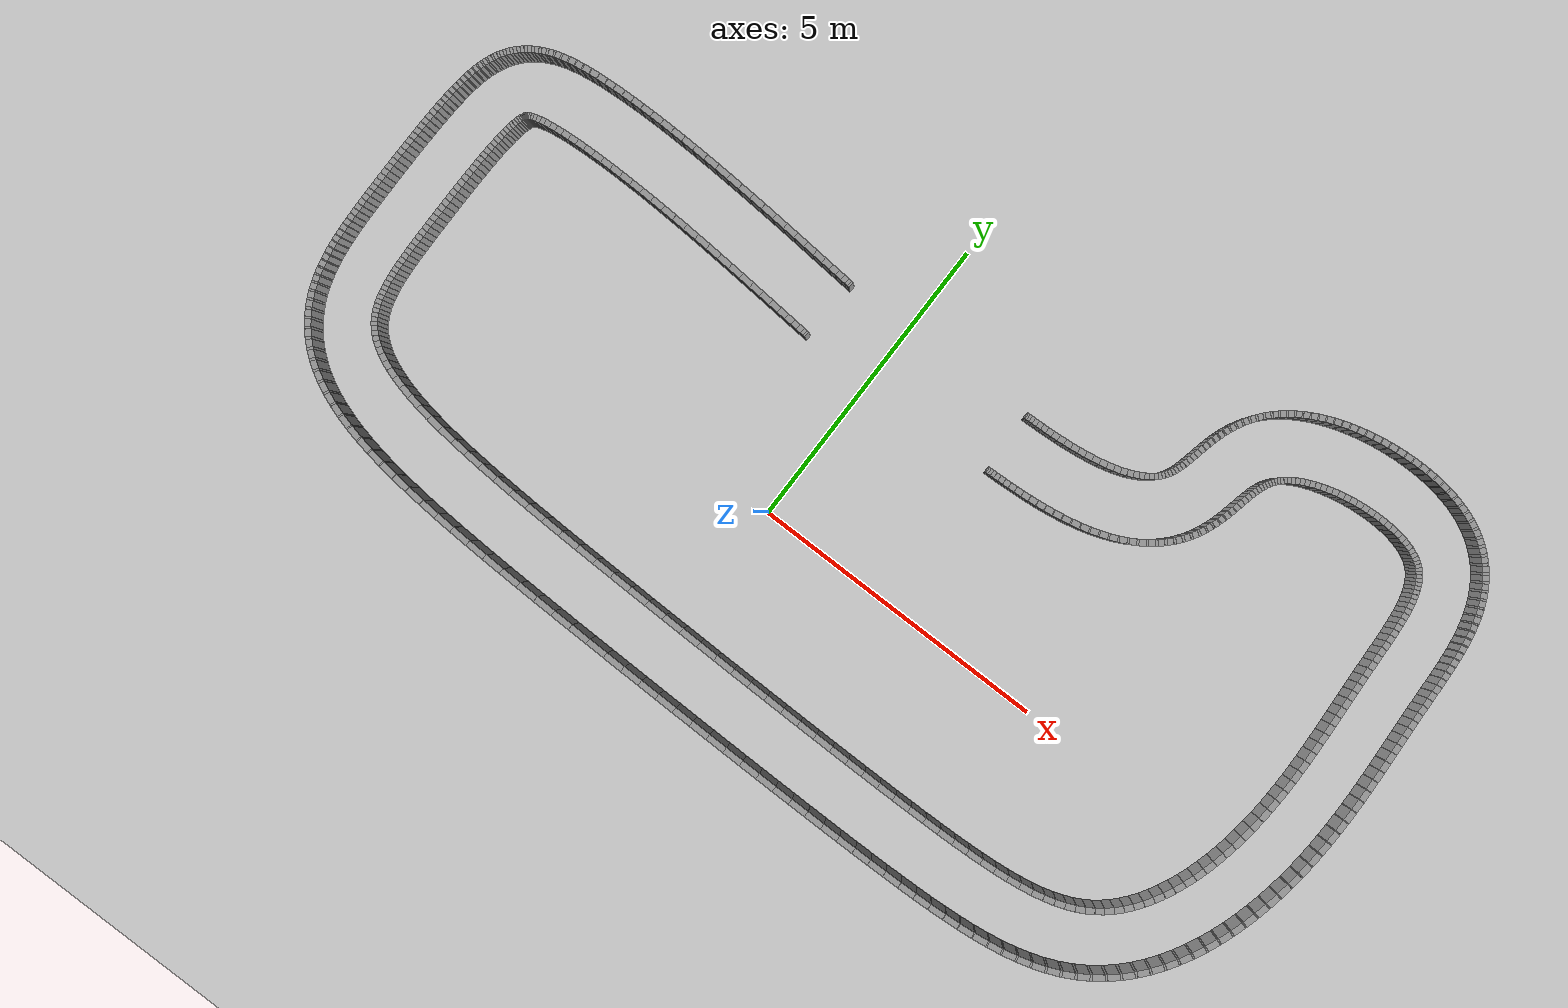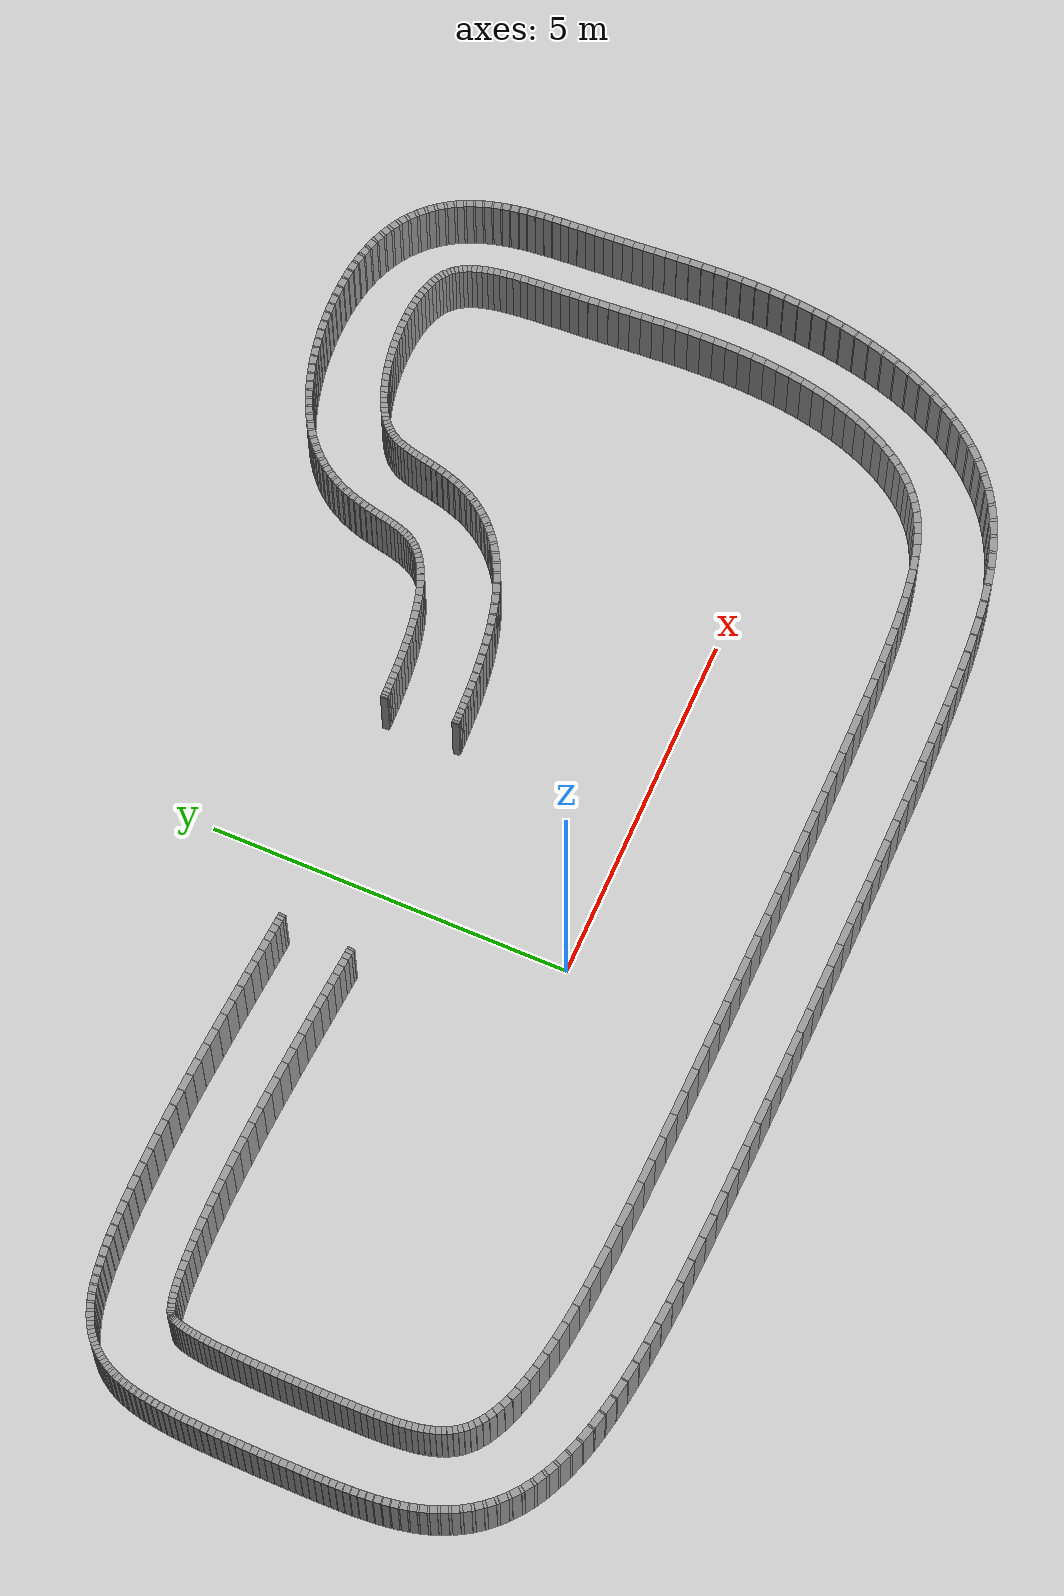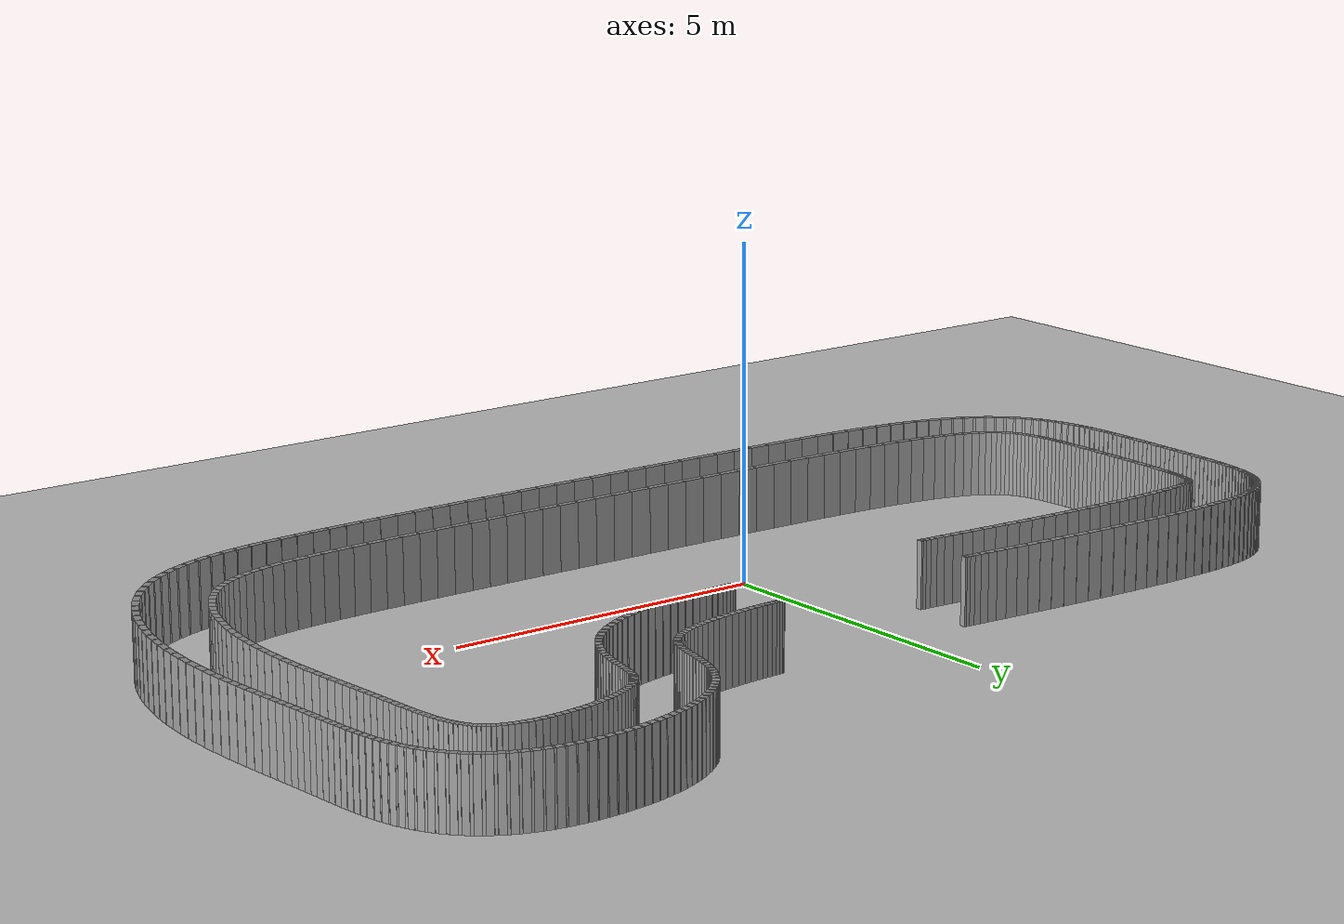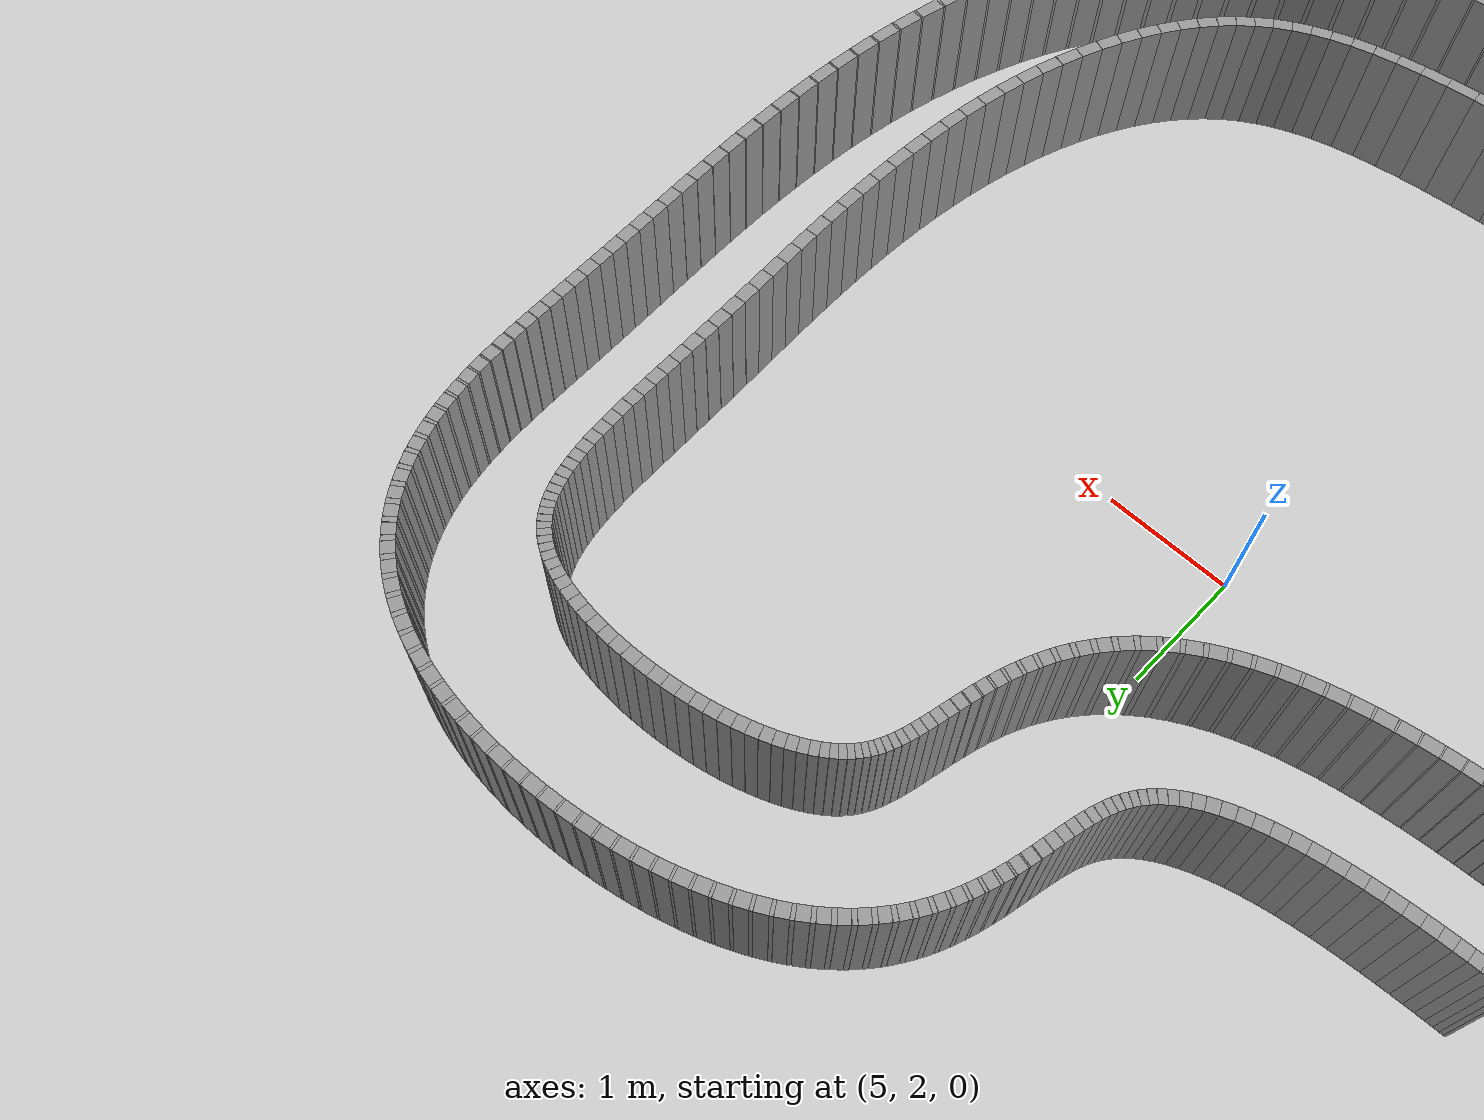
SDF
<?xml version="1.0"?>
        <sdf version="1.6">
        <world name="default">
            <include>
            <uri>model://ground_plane</uri>
            </include>
            <include>
            <uri>model://sun</uri>
            </include>

        <model name="wall_0_outward">
          <static>true</static>
          <link name="link">
            <collision name="collision">
              <geometry>
                <box>
                  <size>0.028140372648619457 0.1 1.0</size>
                </box>
              </geometry>
            </collision>
            <visual name="visual">
              <geometry>
                <box>
                  <size>0.028140372648619457 0.1 1.0</size>
                </box>
              </geometry>
              <material>
                <script>
                  <uri>file://media/materials/scripts/gazebo.material</uri>
                  <name>Gazebo/Gray</name>
                </script>
              </material>
            </visual>
          </link>
          <pose>-1.1622154677570358 2.489480056677835 0.5 0 0 3.0679876131433996</pose>
        </model>

        <model name="wall_1_outward">
          <static>true</static>
          <link name="link">
            <collision name="collision">
              <geometry>
                <box>
                  <size>0.055825213619563545 0.1 1.0</size>
                </box>
              </geometry>
            </collision>
            <visual name="visual">
              <geometry>
                <box>
                  <size>0.055825213619563545 0.1 1.0</size>
                </box>
              </geometry>
              <material>
                <script>
                  <uri>file://media/materials/scripts/gazebo.material</uri>
                  <name>Gazebo/Gray</name>
                </script>
              </material>
            </visual>
          </link>
          <pose>-1.20408429808078 2.49257132808138 0.5 0 0 3.067846946948879</pose>
        </model>

        <model name="wall_2_outward">
          <static>true</static>
          <link name="link">
            <collision name="collision">
              <geometry>
                <box>
                  <size>0.08244396965421265 0.1 1.0</size>
                </box>
              </geometry>
            </collision>
            <visual name="visual">
              <geometry>
                <box>
                  <size>0.08244396965421265 0.1 1.0</size>
                </box>
              </geometry>
              <material>
                <script>
                  <uri>file://media/materials/scripts/gazebo.material</uri>
                  <name>Gazebo/Gray</name>
                </script>
              </material>
            </visual>
          </link>
          <pose>-1.2730303313313385 2.4976738967459715 0.5 0 0 3.0676326591313265</pose>
        </model>

        <model name="wall_3_outward">
          <static>true</static>
          <link name="link">
            <collision name="collision">
              <geometry>
                <box>
                  <size>0.10753430926952938 0.1 1.0</size>
                </box>
              </geometry>
            </collision>
            <visual name="visual">
              <geometry>
                <box>
                  <size>0.10753430926952938 0.1 1.0</size>
                </box>
              </geometry>
              <material>
                <script>
                  <uri>file://media/materials/scripts/gazebo.material</uri>
                  <name>Gazebo/Gray</name>
                </script>
              </material>
            </visual>
          </link>
          <pose>-1.3677589461420014 2.504704263168981 0.5 0 0 3.0674205477627536</pose>
        </model>

        <model name="wall_4_outward">
          <static>true</static>
          <link name="link">
            <collision name="collision">
              <geometry>
                <box>
                  <size>0.1306976688387076 0.1 1.0</size>
                </box>
              </geometry>
            </collision>
            <visual name="visual">
              <geometry>
                <box>
                  <size>0.1306976688387076 0.1 1.0</size>
                </box>
              </geometry>
              <material>
                <script>
                  <uri>file://media/materials/scripts/gazebo.material</uri>
                  <name>Gazebo/Gray</name>
                </script>
              </material>
            </visual>
          </link>
          <pose>-1.4865466899300728 2.5135411570151414 0.5 0 0 3.067268497837281</pose>
        </model>

        <model name="wall_5_outward">
          <static>true</static>
          <link name="link">
            <collision name="collision">
              <geometry>
                <box>
                  <size>0.151537158029325 0.1 1.0</size>
                </box>
              </geometry>
            </collision>
            <visual name="visual">
              <geometry>
                <box>
                  <size>0.151537158029325 0.1 1.0</size>
                </box>
              </geometry>
              <material>
                <script>
                  <uri>file://media/materials/scripts/gazebo.material</uri>
                  <name>Gazebo/Gray</name>
                </script>
              </material>
            </visual>
          </link>
          <pose>-1.6272745344189103 2.524019618722159 0.5 0 0 3.0672726943349033</pose>
        </model>

        <model name="wall_6_outward">
          <static>true</static>
          <link name="link">
            <collision name="collision">
              <geometry>
                <box>
                  <size>0.16990768270761064 0.1 1.0</size>
                </box>
              </geometry>
            </collision>
            <visual name="visual">
              <geometry>
                <box>
                  <size>0.16990768270761064 0.1 1.0</size>
                </box>
              </geometry>
              <material>
                <script>
                  <uri>file://media/materials/scripts/gazebo.material</uri>
                  <name>Gazebo/Gray</name>
                </script>
              </material>
            </visual>
          </link>
          <pose>-1.7875548677201951 2.535932249018213 0.5 0 0 3.067523641800801</pose>
        </model>

        <model name="wall_7_outward">
          <static>true</static>
          <link name="link">
            <collision name="collision">
              <geometry>
                <box>
                  <size>0.18561479345425694 0.1 1.0</size>
                </box>
              </geometry>
            </collision>
            <visual name="visual">
              <geometry>
                <box>
                  <size>0.18561479345425694 0.1 1.0</size>
                </box>
              </geometry>
              <material>
                <script>
                  <uri>file://media/materials/scripts/gazebo.material</uri>
                  <name>Gazebo/Gray</name>
                </script>
              </material>
            </visual>
          </link>
          <pose>-1.9648328296530533 2.549031070232745 0.5 0 0 3.0681259019662304</pose>
        </model>

        <model name="wall_8_outward">
          <static>true</static>
          <link name="link">
            <collision name="collision">
              <geometry>
                <box>
                  <size>0.1985889123548593 0.1 1.0</size>
                </box>
              </geometry>
            </collision>
            <visual name="visual">
              <geometry>
                <box>
                  <size>0.1985889123548593 0.1 1.0</size>
                </box>
              </geometry>
              <material>
                <script>
                  <uri>file://media/materials/scripts/gazebo.material</uri>
                  <name>Gazebo/Gray</name>
                </script>
              </material>
            </visual>
          </link>
          <pose>-2.156424088885226 2.563027538495194 0.5 0 0 3.0691754652221364</pose>
        </model>

        <model name="wall_9_outward">
          <static>true</static>
          <link name="link">
            <collision name="collision">
              <geometry>
                <box>
                  <size>0.20883403933903916 0.1 1.0</size>
                </box>
              </geometry>
            </collision>
            <visual name="visual">
              <geometry>
                <box>
                  <size>0.20883403933903916 0.1 1.0</size>
                </box>
              </geometry>
              <material>
                <script>
                  <uri>file://media/materials/scripts/gazebo.material</uri>
                  <name>Gazebo/Gray</name>
                </script>
              </material>
            </visual>
          </link>
          <pose>-2.359613490430906 2.577601708133042 0.5 0 0 3.0707611890762445</pose>
        </model>

        <model name="wall_10_outward">
          <static>true</static>
          <link name="link">
            <collision name="collision">
              <geometry>
                <box>
                  <size>0.216436371516167 0.1 1.0</size>
                </box>
              </geometry>
            </collision>
            <visual name="visual">
              <geometry>
                <box>
                  <size>0.216436371516167 0.1 1.0</size>
                </box>
              </geometry>
              <material>
                <script>
                  <uri>file://media/materials/scripts/gazebo.material</uri>
                  <name>Gazebo/Gray</name>
                </script>
              </material>
            </visual>
          </link>
          <pose>-2.5717321251800476 2.592412532849492 0.5 0 0 3.072964394940024</pose>
        </model>

        <model name="wall_11_outward">
          <static>true</static>
          <link name="link">
            <collision name="collision">
              <geometry>
                <box>
                  <size>0.22154062162151802 0.1 1.0</size>
                </box>
              </geometry>
            </collision>
            <visual name="visual">
              <geometry>
                <box>
                  <size>0.22154062162151802 0.1 1.0</size>
                </box>
              </geometry>
              <material>
                <script>
                  <uri>file://media/materials/scripts/gazebo.material</uri>
                  <name>Gazebo/Gray</name>
                </script>
              </material>
            </visual>
          </link>
          <pose>-2.790226542347383 2.607111235725002 0.5 0 0 3.0758444247548358</pose>
        </model>

        <model name="wall_12_outward">
          <static>true</static>
          <link name="link">
            <collision name="collision">
              <geometry>
                <box>
                  <size>0.22433429040783703 0.1 1.0</size>
                </box>
              </geometry>
            </collision>
            <visual name="visual">
              <geometry>
                <box>
                  <size>0.22433429040783703 0.1 1.0</size>
                </box>
              </geometry>
              <material>
                <script>
                  <uri>file://media/materials/scripts/gazebo.material</uri>
                  <name>Gazebo/Gray</name>
                </script>
              </material>
            </visual>
          </link>
          <pose>-3.0127080790691334 2.621356044116502 0.5 0 0 3.0794390664921374</pose>
        </model>

        <model name="wall_13_outward">
          <static>true</static>
          <link name="link">
            <collision name="collision">
              <geometry>
                <box>
                  <size>0.22504762564123426 0.1 1.0</size>
                </box>
              </geometry>
            </collision>
            <visual name="visual">
              <geometry>
                <box>
                  <size>0.22504762564123426 0.1 1.0</size>
                </box>
              </geometry>
              <material>
                <script>
                  <uri>file://media/materials/scripts/gazebo.material</uri>
                  <name>Gazebo/Gray</name>
                </script>
              </material>
            </visual>
          </link>
          <pose>-3.236994426883612 2.634825399262277 0.5 0 0 3.083774877540525</pose>
        </model>

        <model name="wall_14_outward">
          <static>true</static>
          <link name="link">
            <collision name="collision">
              <geometry>
                <box>
                  <size>0.2239262534368999 0.1 1.0</size>
                </box>
              </geometry>
            </collision>
            <visual name="visual">
              <geometry>
                <box>
                  <size>0.2239262534368999 0.1 1.0</size>
                </box>
              </geometry>
              <material>
                <script>
                  <uri>file://media/materials/scripts/gazebo.material</uri>
                  <name>Gazebo/Gray</name>
                </script>
              </material>
            </visual>
          </link>
          <pose>-3.461137621740315 2.647230652320924 0.5 0 0 3.0888454774995346</pose>
        </model>

        <model name="wall_15_outward">
          <static>true</static>
          <link name="link">
            <collision name="collision">
              <geometry>
                <box>
                  <size>0.22121787977610916 0.1 1.0</size>
                </box>
              </geometry>
            </collision>
            <visual name="visual">
              <geometry>
                <box>
                  <size>0.22121787977610916 0.1 1.0</size>
                </box>
              </geometry>
              <material>
                <script>
                  <uri>file://media/materials/scripts/gazebo.material</uri>
                  <name>Gazebo/Gray</name>
                </script>
              </material>
            </visual>
          </link>
          <pose>-3.6834319924109 2.658326774298981 0.5 0 0 3.0946251012105375</pose>
        </model>

        <model name="wall_16_outward">
          <static>true</static>
          <link name="link">
            <collision name="collision">
              <geometry>
                <box>
                  <size>0.2171589068234425 0.1 1.0</size>
                </box>
              </geometry>
            </collision>
            <visual name="visual">
              <geometry>
                <box>
                  <size>0.2171589068234425 0.1 1.0</size>
                </box>
              </geometry>
              <material>
                <script>
                  <uri>file://media/materials/scripts/gazebo.material</uri>
                  <name>Gazebo/Gray</name>
                </script>
              </material>
            </visual>
          </link>
          <pose>-3.9024093239194277 2.6679173634878026 0.5 0 0 3.1010815743255806</pose>
        </model>

        <model name="wall_17_outward">
          <static>true</static>
          <link name="link">
            <collision name="collision">
              <geometry>
                <box>
                  <size>0.21196690600001417 0.1 1.0</size>
                </box>
              </geometry>
            </collision>
            <visual name="visual">
              <geometry>
                <box>
                  <size>0.21196690600001417 0.1 1.0</size>
                </box>
              </geometry>
              <material>
                <script>
                  <uri>file://media/materials/scripts/gazebo.material</uri>
                  <name>Gazebo/Gray</name>
                </script>
              </material>
            </visual>
          </link>
          <pose>-4.116823968110159 2.675856025139705 0.5 0 0 3.108173728384551</pose>
        </model>

        <model name="wall_18_outward">
          <static>true</static>
          <link name="link">
            <collision name="collision">
              <geometry>
                <box>
                  <size>0.20583165776811335 0.1 1.0</size>
                </box>
              </geometry>
            </collision>
            <visual name="visual">
              <geometry>
                <box>
                  <size>0.20583165776811335 0.1 1.0</size>
                </box>
              </geometry>
              <material>
                <script>
                  <uri>file://media/materials/scripts/gazebo.material</uri>
                  <name>Gazebo/Gray</name>
                </script>
              </material>
            </visual>
          </link>
          <pose>-4.325630023222242 2.6820443629476562 0.5 0 0 3.115868370377387</pose>
        </model>

        <model name="wall_19_outward">
          <static>true</static>
          <link name="link">
            <collision name="collision">
              <geometry>
                <box>
                  <size>0.1989081307571607 0.1 1.0</size>
                </box>
              </geometry>
            </collision>
            <visual name="visual">
              <geometry>
                <box>
                  <size>0.1989081307571607 0.1 1.0</size>
                </box>
              </geometry>
              <material>
                <script>
                  <uri>file://media/materials/scripts/gazebo.material</uri>
                  <name>Gazebo/Gray</name>
                </script>
              </material>
            </visual>
          </link>
          <pose>-4.5279507352353505 2.6864263655881295 0.5 0 0 3.1241479501018383</pose>
        </model>

        <model name="wall_20_outward">
          <static>true</static>
          <link name="link">
            <collision name="collision">
              <geometry>
                <box>
                  <size>0.1913271043381779 0.1 1.0</size>
                </box>
              </geometry>
            </collision>
            <visual name="visual">
              <geometry>
                <box>
                  <size>0.1913271043381779 0.1 1.0</size>
                </box>
              </geometry>
              <material>
                <script>
                  <uri>file://media/materials/scripts/gazebo.material</uri>
                  <name>Gazebo/Gray</name>
                </script>
              </material>
            </visual>
          </link>
          <pose>-4.7230497058045655 2.688981233878158 0.5 0 0 3.1330207406002106</pose>
        </model>

        <model name="wall_21_outward">
          <static>true</static>
          <link name="link">
            <collision name="collision">
              <geometry>
                <box>
                  <size>0.1831754176465537 0.1 1.0</size>
                </box>
              </geometry>
            </collision>
            <visual name="visual">
              <geometry>
                <box>
                  <size>0.1831754176465537 0.1 1.0</size>
                </box>
              </geometry>
              <material>
                <script>
                  <uri>file://media/materials/scripts/gazebo.material</uri>
                  <name>Gazebo/Gray</name>
                </script>
              </material>
            </visual>
          </link>
          <pose>-4.910297411832005 2.689715199492401 0.5 0 0 -3.1406531825315893</pose>
        </model>

        <model name="wall_22_outward">
          <static>true</static>
          <link name="link">
            <collision name="collision">
              <geometry>
                <box>
                  <size>0.1745138847776721 0.1 1.0</size>
                </box>
              </geometry>
            </collision>
            <visual name="visual">
              <geometry>
                <box>
                  <size>0.1745138847776721 0.1 1.0</size>
                </box>
              </geometry>
              <material>
                <script>
                  <uri>file://media/materials/scripts/gazebo.material</uri>
                  <name>Gazebo/Gray</name>
                </script>
              </material>
            </visual>
          </link>
          <pose>-5.089136544184888 2.688651385560158 0.5 0 0 -3.1303867783887305</pose>
        </model>

        <model name="wall_23_outward">
          <static>true</static>
          <link name="link">
            <collision name="collision">
              <geometry>
                <box>
                  <size>0.16537689547402926 0.1 1.0</size>
                </box>
              </geometry>
            </collision>
            <visual name="visual">
              <geometry>
                <box>
                  <size>0.16537689547402926 0.1 1.0</size>
                </box>
              </geometry>
              <material>
                <script>
                  <uri>file://media/materials/scripts/gazebo.material</uri>
                  <name>Gazebo/Gray</name>
                </script>
              </material>
            </visual>
          </link>
          <pose>-5.259055711600917 2.685821537756546 0.5 0 0 -3.119192514208508</pose>
        </model>

        <model name="wall_24_outward">
          <static>true</static>
          <link name="link">
            <collision name="collision">
              <geometry>
                <box>
                  <size>0.15579286756665978 0.1 1.0</size>
                </box>
              </geometry>
            </collision>
            <visual name="visual">
              <geometry>
                <box>
                  <size>0.15579286756665978 0.1 1.0</size>
                </box>
              </geometry>
              <material>
                <script>
                  <uri>file://media/materials/scripts/gazebo.material</uri>
                  <name>Gazebo/Gray</name>
                </script>
              </material>
            </visual>
          </link>
          <pose>-5.419572740003172 2.6812607695263315 0.5 0 0 -3.106812671907408</pose>
        </model>

        <model name="wall_25_outward">
          <static>true</static>
          <link name="link">
            <collision name="collision">
              <geometry>
                <box>
                  <size>0.14576239276482258 0.1 1.0</size>
                </box>
              </geometry>
            </collision>
            <visual name="visual">
              <geometry>
                <box>
                  <size>0.14576239276482258 0.1 1.0</size>
                </box>
              </geometry>
              <material>
                <script>
                  <uri>file://media/materials/scripts/gazebo.material</uri>
                  <name>Gazebo/Gray</name>
                </script>
              </material>
            </visual>
          </link>
          <pose>-5.570216822638956 2.6750035530914955 0.5 0 0 -3.0928842104872367</pose>
        </model>

        <model name="wall_26_outward">
          <static>true</static>
          <link name="link">
            <collision name="collision">
              <geometry>
                <box>
                  <size>0.13529707555168738 0.1 1.0</size>
                </box>
              </geometry>
            </collision>
            <visual name="visual">
              <geometry>
                <box>
                  <size>0.13529707555168738 0.1 1.0</size>
                </box>
              </geometry>
              <material>
                <script>
                  <uri>file://media/materials/scripts/gazebo.material</uri>
                  <name>Gazebo/Gray</name>
                </script>
              </material>
            </visual>
          </link>
          <pose>-5.71051875122332 2.6670839238849906 0.5 0 0 -3.0769327121487433</pose>
        </model>

        <model name="wall_27_outward">
          <static>true</static>
          <link name="link">
            <collision name="collision">
              <geometry>
                <box>
                  <size>0.12440593182755699 0.1 1.0</size>
                </box>
              </geometry>
            </collision>
            <visual name="visual">
              <geometry>
                <box>
                  <size>0.12440593182755699 0.1 1.0</size>
                </box>
              </geometry>
              <material>
                <script>
                  <uri>file://media/materials/scripts/gazebo.material</uri>
                  <name>Gazebo/Gray</name>
                </script>
              </material>
            </visual>
          </link>
          <pose>-5.840013486167057 2.657540696402026 0.5 0 0 -3.0583473821088925</pose>
        </model>

        <model name="wall_28_outward">
          <static>true</static>
          <link name="link">
            <collision name="collision">
              <geometry>
                <box>
                  <size>0.11310574560206636 0.1 1.0</size>
                </box>
              </geometry>
            </collision>
            <visual name="visual">
              <geometry>
                <box>
                  <size>0.11310574560206636 0.1 1.0</size>
                </box>
              </geometry>
              <material>
                <script>
                  <uri>file://media/materials/scripts/gazebo.material</uri>
                  <name>Gazebo/Gray</name>
                </script>
              </material>
            </visual>
          </link>
          <pose>-5.958241194113793 2.6464294106881496 0.5 0 0 -3.0363790206103327</pose>
        </model>

        <model name="wall_29_outward">
          <static>true</static>
          <link name="link">
            <collision name="collision">
              <geometry>
                <box>
                  <size>0.1014162737693384 0.1 1.0</size>
                </box>
              </geometry>
            </collision>
            <visual name="visual">
              <geometry>
                <box>
                  <size>0.1014162737693384 0.1 1.0</size>
                </box>
              </geometry>
              <material>
                <script>
                  <uri>file://media/materials/scripts/gazebo.material</uri>
                  <name>Gazebo/Gray</name>
                </script>
              </material>
            </visual>
          </link>
          <pose>-6.064751796304438 2.6338422294535917 0.5 0 0 -3.010110535834303</pose>
        </model>

        <model name="wall_30_outward">
          <static>true</static>
          <link name="link">
            <collision name="collision">
              <geometry>
                <box>
                  <size>0.0893771961264983 0.1 1.0</size>
                </box>
              </geometry>
            </collision>
            <visual name="visual">
              <geometry>
                <box>
                  <size>0.0893771961264983 0.1 1.0</size>
                </box>
              </geometry>
              <material>
                <script>
                  <uri>file://media/materials/scripts/gazebo.material</uri>
                  <name>Gazebo/Gray</name>
                </script>
              </material>
            </visual>
          </link>
          <pose>-6.159117503773086 2.619936124576597 0.5 0 0 -2.9784553037772485</pose>
        </model>

        <model name="wall_31_outward">
          <static>true</static>
          <link name="link">
            <collision name="collision">
              <geometry>
                <box>
                  <size>0.07706047219806364 0.1 1.0</size>
                </box>
              </geometry>
            </collision>
            <visual name="visual">
              <geometry>
                <box>
                  <size>0.07706047219806364 0.1 1.0</size>
                </box>
              </geometry>
              <material>
                <script>
                  <uri>file://media/materials/scripts/gazebo.material</uri>
                  <name>Gazebo/Gray</name>
                </script>
              </material>
            </visual>
          </link>
          <pose>-6.240964236394742 2.6049706022092662 0.5 0 0 -2.9401979096768147</pose>
        </model>

        <model name="wall_32_outward">
          <static>true</static>
          <link name="link">
            <collision name="collision">
              <geometry>
                <box>
                  <size>0.06459485305786183 0.1 1.0</size>
                </box>
              </geometry>
            </collision>
            <visual name="visual">
              <geometry>
                <box>
                  <size>0.06459485305786183 0.1 1.0</size>
                </box>
              </geometry>
              <material>
                <script>
                  <uri>file://media/materials/scripts/gazebo.material</uri>
                  <name>Gazebo/Gray</name>
                </script>
              </material>
            </visual>
          </link>
          <pose>-6.310028393585592 2.5893486071235454 0.5 0 0 -2.8940190460786783</pose>
        </model>

        <model name="wall_33_outward">
          <static>true</static>
          <link name="link">
            <collision name="collision">
              <geometry>
                <box>
                  <size>0.05219800385316098 0.1 1.0</size>
                </box>
              </geometry>
            </collision>
            <visual name="visual">
              <geometry>
                <box>
                  <size>0.05219800385316098 0.1 1.0</size>
                </box>
              </geometry>
              <material>
                <script>
                  <uri>file://media/materials/scripts/gazebo.material</uri>
                  <name>Gazebo/Gray</name>
                </script>
              </material>
            </visual>
          </link>
          <pose>-6.366251846193697 2.57364874288543 0.5 0 0 -2.8386826201260953</pose>
        </model>

        <model name="wall_34_outward">
          <static>true</static>
          <link name="link">
            <collision name="collision">
              <geometry>
                <box>
                  <size>0.04021269407964118 0.1 1.0</size>
                </box>
              </geometry>
            </collision>
            <visual name="visual">
              <geometry>
                <box>
                  <size>0.04021269407964118 0.1 1.0</size>
                </box>
              </geometry>
              <material>
                <script>
                  <uri>file://media/materials/scripts/gazebo.material</uri>
                  <name>Gazebo/Gray</name>
                </script>
              </material>
            </visual>
          </link>
          <pose>-6.4099196178435935 2.558621861044299 0.5 0 0 -2.7731493434163204</pose>
        </model>

        <model name="wall_35_outward">
          <static>true</static>
          <link name="link">
            <collision name="collision">
              <geometry>
                <box>
                  <size>0.02916570258736988 0.1 1.0</size>
                </box>
              </geometry>
            </collision>
            <visual name="visual">
              <geometry>
                <box>
                  <size>0.02916570258736988 0.1 1.0</size>
                </box>
              </geometry>
              <material>
                <script>
                  <uri>file://media/materials/scripts/gazebo.material</uri>
                  <name>Gazebo/Gray</name>
                </script>
              </material>
            </visual>
          </link>
          <pose>-6.441842121010467 2.5451090108809797 0.5 0 0 -2.6970505991704186</pose>
        </model>

        <model name="wall_36_outward">
          <static>true</static>
          <link name="link">
            <collision name="collision">
              <geometry>
                <box>
                  <size>0.01970447937732626 0.1 1.0</size>
                </box>
              </geometry>
            </collision>
            <visual name="visual">
              <geometry>
                <box>
                  <size>0.01970447937732626 0.1 1.0</size>
                </box>
              </geometry>
              <material>
                <script>
                  <uri>file://media/materials/scripts/gazebo.material</uri>
                  <name>Gazebo/Gray</name>
                </script>
              </material>
            </visual>
          </link>
          <pose>-6.4635048994722215 2.5338514486330386 0.5 0 0 -2.6109276550862126</pose>
        </model>

        <model name="wall_37_outward">
          <static>true</static>
          <link name="link">
            <collision name="collision">
              <geometry>
                <box>
                  <size>0.012542738685571155 0.1 1.0</size>
                </box>
              </geometry>
            </collision>
            <visual name="visual">
              <geometry>
                <box>
                  <size>0.012542738685571155 0.1 1.0</size>
                </box>
              </geometry>
              <material>
                <script>
                  <uri>file://media/materials/scripts/gazebo.material</uri>
                  <name>Gazebo/Gray</name>
                </script>
              </material>
            </visual>
          </link>
          <pose>-6.477088068018396 2.525195871121216 0.5 0 0 -2.516606615605364</pose>
        </model>

        <model name="wall_38_outward">
          <static>true</static>
          <link name="link">
            <collision name="collision">
              <geometry>
                <box>
                  <size>0.008268420198442037 0.1 1.0</size>
                </box>
              </geometry>
            </collision>
            <visual name="visual">
              <geometry>
                <box>
                  <size>0.008268420198442037 0.1 1.0</size>
                </box>
              </geometry>
              <material>
                <script>
                  <uri>file://media/materials/scripts/gazebo.material</uri>
                  <name>Gazebo/Gray</name>
                </script>
              </material>
            </visual>
          </link>
          <pose>-6.485270146383673 2.518786986967492 0.5 0 0 -2.417221727164259</pose>
        </model>

        <model name="wall_39_outward">
          <static>true</static>
          <link name="link">
            <collision name="collision">
              <geometry>
                <box>
                  <size>0.007109251496982159 0.1 1.0</size>
                </box>
              </geometry>
            </collision>
            <visual name="visual">
              <geometry>
                <box>
                  <size>0.007109251496982159 0.1 1.0</size>
                </box>
              </geometry>
              <material>
                <script>
                  <uri>file://media/materials/scripts/gazebo.material</uri>
                  <name>Gazebo/Gray</name>
                </script>
              </material>
            </visual>
          </link>
          <pose>-6.490779170693379 2.513437117754802 0.5 0 0 -2.3169107187363056</pose>
        </model>

        <model name="wall_40_outward">
          <static>true</static>
          <link name="link">
            <collision name="collision">
              <geometry>
                <box>
                  <size>0.0088053573459172 0.1 1.0</size>
                </box>
              </geometry>
            </collision>
            <visual name="visual">
              <geometry>
                <box>
                  <size>0.0088053573459172 0.1 1.0</size>
                </box>
              </geometry>
              <material>
                <script>
                  <uri>file://media/materials/scripts/gazebo.material</uri>
                  <name>Gazebo/Gray</name>
                </script>
              </material>
            </visual>
          </link>
          <pose>-6.4958532651454215 2.5073195162132977 0.5 0 0 -2.2198855603320045</pose>
        </model>

        <model name="wall_41_outward">
          <static>true</static>
          <link name="link">
            <collision name="collision">
              <geometry>
                <box>
                  <size>0.012729278913564302 0.1 1.0</size>
                </box>
              </geometry>
            </collision>
            <visual name="visual">
              <geometry>
                <box>
                  <size>0.012729278913564302 0.1 1.0</size>
                </box>
              </geometry>
              <material>
                <script>
                  <uri>file://media/materials/scripts/gazebo.material</uri>
                  <name>Gazebo/Gray</name>
                </script>
              </material>
            </visual>
          </link>
          <pose>-6.501889186138682 2.498415874615053 0.5 0 0 -2.1296589106911497</pose>
        </model>

        <model name="wall_42_outward">
          <static>true</static>
          <link name="link">
            <collision name="collision">
              <geometry>
                <box>
                  <size>0.018078094400813375 0.1 1.0</size>
                </box>
              </geometry>
            </collision>
            <visual name="visual">
              <geometry>
                <box>
                  <size>0.018078094400813375 0.1 1.0</size>
                </box>
              </geometry>
              <material>
                <script>
                  <uri>file://media/materials/scripts/gazebo.material</uri>
                  <name>Gazebo/Gray</name>
                </script>
              </material>
            </visual>
          </link>
          <pose>-6.509419431233865 2.484992380916353 0.5 0 0 -2.048493816246914</pose>
        </model>

        <model name="wall_43_outward">
          <static>true</static>
          <link name="link">
            <collision name="collision">
              <geometry>
                <box>
                  <size>0.024121877454705724 0.1 1.0</size>
                </box>
              </geometry>
            </collision>
            <visual name="visual">
              <geometry>
                <box>
                  <size>0.024121877454705724 0.1 1.0</size>
                </box>
              </geometry>
              <material>
                <script>
                  <uri>file://media/materials/scripts/gazebo.material</uri>
                  <name>Gazebo/Gray</name>
                </script>
              </material>
            </visual>
          </link>
          <pose>-6.518344016150102 2.4658871719110413 0.5 0 0 -1.977310241986031</pose>
        </model>

        <model name="wall_44_outward">
          <static>true</static>
          <link name="link">
            <collision name="collision">
              <geometry>
                <box>
                  <size>0.030317028157117235 0.1 1.0</size>
                </box>
              </geometry>
            </collision>
            <visual name="visual">
              <geometry>
                <box>
                  <size>0.030317028157117235 0.1 1.0</size>
                </box>
              </geometry>
              <material>
                <script>
                  <uri>file://media/materials/scripts/gazebo.material</uri>
                  <name>Gazebo/Gray</name>
                </script>
              </material>
            </visual>
          </link>
          <pose>-6.528243036378707 2.44054507561391 0.5 0 0 -1.916038067245079</pose>
        </model>

        <model name="wall_45_outward">
          <static>true</static>
          <link name="link">
            <collision name="collision">
              <geometry>
                <box>
                  <size>0.03633877895909691 0.1 1.0</size>
                </box>
              </geometry>
            </collision>
            <visual name="visual">
              <geometry>
                <box>
                  <size>0.03633877895909691 0.1 1.0</size>
                </box>
              </geometry>
              <material>
                <script>
                  <uri>file://media/materials/scripts/gazebo.material</uri>
                  <name>Gazebo/Gray</name>
                </script>
              </material>
            </visual>
          </link>
          <pose>-6.538622990509031 2.408886620681297 0.5 0 0 -1.8639205412335749</pose>
        </model>

        <model name="wall_46_outward">
          <static>true</static>
          <link name="link">
            <collision name="collision">
              <geometry>
                <box>
                  <size>0.042021028365479135 0.1 1.0</size>
                </box>
              </geometry>
            </collision>
            <visual name="visual">
              <geometry>
                <box>
                  <size>0.042021028365479135 0.1 1.0</size>
                </box>
              </geometry>
              <material>
                <script>
                  <uri>file://media/materials/scripts/gazebo.material</uri>
                  <name>Gazebo/Gray</name>
                </script>
              </material>
            </visual>
          </link>
          <pose>-6.549054362132731 2.3711306367562526 0.5 0 0 -1.8199780611749543</pose>
        </model>

        <model name="wall_47_outward">
          <static>true</static>
          <link name="link">
            <collision name="collision">
              <geometry>
                <box>
                  <size>0.04727209908733998 0.1 1.0</size>
                </box>
              </geometry>
            </collision>
            <visual name="visual">
              <geometry>
                <box>
                  <size>0.04727209908733998 0.1 1.0</size>
                </box>
              </geometry>
              <material>
                <script>
                  <uri>file://media/materials/scripts/gazebo.material</uri>
                  <name>Gazebo/Gray</name>
                </script>
              </material>
            </visual>
          </link>
          <pose>-6.559215694631106 2.3276635586757406 0.5 0 0 -1.783078301091299</pose>
        </model>

        <model name="wall_48_outward">
          <static>true</static>
          <link name="link">
            <collision name="collision">
              <geometry>
                <box>
                  <size>0.052111580436070885 0.1 1.0</size>
                </box>
              </geometry>
            </collision>
            <visual name="visual">
              <geometry>
                <box>
                  <size>0.052111580436070885 0.1 1.0</size>
                </box>
              </geometry>
              <material>
                <script>
                  <uri>file://media/materials/scripts/gazebo.material</uri>
                  <name>Gazebo/Gray</name>
                </script>
              </material>
            </visual>
          </link>
          <pose>-6.568893499312052 2.2789293031315054 0.5 0 0 -1.7520892562855555</pose>
        </model>

        <model name="wall_49_outward">
          <static>true</static>
          <link name="link">
            <collision name="collision">
              <geometry>
                <box>
                  <size>0.056570701424024726 0.1 1.0</size>
                </box>
              </geometry>
            </collision>
            <visual name="visual">
              <geometry>
                <box>
                  <size>0.056570701424024726 0.1 1.0</size>
                </box>
              </geometry>
              <material>
                <script>
                  <uri>file://media/materials/scripts/gazebo.material</uri>
                  <name>Gazebo/Gray</name>
                </script>
              </material>
            </visual>
          </link>
          <pose>-6.5779667077379536 2.225355625883908 0.5 0 0 -1.7261046422392725</pose>
        </model>

        <model name="wall_50_outward">
          <static>true</static>
          <link name="link">
            <collision name="collision">
              <geometry>
                <box>
                  <size>0.060661920310766025 0.1 1.0</size>
                </box>
              </geometry>
            </collision>
            <visual name="visual">
              <geometry>
                <box>
                  <size>0.060661920310766025 0.1 1.0</size>
                </box>
              </geometry>
              <material>
                <script>
                  <uri>file://media/materials/scripts/gazebo.material</uri>
                  <name>Gazebo/Gray</name>
                </script>
              </material>
            </visual>
          </link>
          <pose>-6.586377185959433 2.167349374068392 0.5 0 0 -1.704229816331041</pose>
        </model>

        <model name="wall_51_outward">
          <static>true</static>
          <link name="link">
            <collision name="collision">
              <geometry>
                <box>
                  <size>0.06444283778980993 0.1 1.0</size>
                </box>
              </geometry>
            </collision>
            <visual name="visual">
              <geometry>
                <box>
                  <size>0.06444283778980993 0.1 1.0</size>
                </box>
              </geometry>
              <material>
                <script>
                  <uri>file://media/materials/scripts/gazebo.material</uri>
                  <name>Gazebo/Gray</name>
                </script>
              </material>
            </visual>
          </link>
          <pose>-6.594106605859016 2.1052790858456865 0.5 0 0 -1.6857010988047292</pose>
        </model>

        <model name="wall_52_outward">
          <static>true</static>
          <link name="link">
            <collision name="collision">
              <geometry>
                <box>
                  <size>0.06794869917491102 0.1 1.0</size>
                </box>
              </geometry>
            </collision>
            <visual name="visual">
              <geometry>
                <box>
                  <size>0.06794869917491102 0.1 1.0</size>
                </box>
              </geometry>
              <material>
                <script>
                  <uri>file://media/materials/scripts/gazebo.material</uri>
                  <name>Gazebo/Gray</name>
                </script>
              </material>
            </visual>
          </link>
          <pose>-6.601163390427155 2.0394626036857804 0.5 0 0 -1.6699312808979285</pose>
        </model>

        <model name="wall_53_outward">
          <static>true</static>
          <link name="link">
            <collision name="collision">
              <geometry>
                <box>
                  <size>0.07123879180609102 0.1 1.0</size>
                </box>
              </geometry>
            </collision>
            <visual name="visual">
              <geometry>
                <box>
                  <size>0.07123879180609102 0.1 1.0</size>
                </box>
              </geometry>
              <material>
                <script>
                  <uri>file://media/materials/scripts/gazebo.material</uri>
                  <name>Gazebo/Gray</name>
                </script>
              </material>
            </visual>
          </link>
          <pose>-6.607570051628232 1.970165985193051 0.5 0 0 -1.6563634013423234</pose>
        </model>

        <model name="wall_54_outward">
          <static>true</static>
          <link name="link">
            <collision name="collision">
              <geometry>
                <box>
                  <size>0.07434558531103215 0.1 1.0</size>
                </box>
              </geometry>
            </collision>
            <visual name="visual">
              <geometry>
                <box>
                  <size>0.07434558531103215 0.1 1.0</size>
                </box>
              </geometry>
              <material>
                <script>
                  <uri>file://media/materials/scripts/gazebo.material</uri>
                  <name>Gazebo/Gray</name>
                </script>
              </material>
            </visual>
          </link>
          <pose>-6.613359297207834 1.89760561326572 0.5 0 0 -1.6447110630068738</pose>
        </model>

        <model name="wall_55_outward">
          <static>true</static>
          <link name="link">
            <collision name="collision">
              <geometry>
                <box>
                  <size>0.07726013353156092 0.1 1.0</size>
                </box>
              </geometry>
            </collision>
            <visual name="visual">
              <geometry>
                <box>
                  <size>0.07726013353156092 0.1 1.0</size>
                </box>
              </geometry>
              <material>
                <script>
                  <uri>file://media/materials/scripts/gazebo.material</uri>
                  <name>Gazebo/Gray</name>
                </script>
              </material>
            </visual>
          </link>
          <pose>-6.618567767896582 1.8219828736938526 0.5 0 0 -1.6346074320864317</pose>
        </model>

        <model name="wall_56_outward">
          <static>true</static>
          <link name="link">
            <collision name="collision">
              <geometry>
                <box>
                  <size>0.08000409625759336 0.1 1.0</size>
                </box>
              </geometry>
            </collision>
            <visual name="visual">
              <geometry>
                <box>
                  <size>0.08000409625759336 0.1 1.0</size>
                </box>
              </geometry>
              <material>
                <script>
                  <uri>file://media/materials/scripts/gazebo.material</uri>
                  <name>Gazebo/Gray</name>
                </script>
              </material>
            </visual>
          </link>
          <pose>-6.623229907448105 1.7434898559767587 0.5 0 0 -1.6257908496668392</pose>
        </model>

        <model name="wall_57_outward">
          <static>true</static>
          <link name="link">
            <collision name="collision">
              <geometry>
                <box>
                  <size>0.08258377150234449 0.1 1.0</size>
                </box>
              </geometry>
            </collision>
            <visual name="visual">
              <geometry>
                <box>
                  <size>0.08258377150234449 0.1 1.0</size>
                </box>
              </geometry>
              <material>
                <script>
                  <uri>file://media/materials/scripts/gazebo.material</uri>
                  <name>Gazebo/Gray</name>
                </script>
              </material>
            </visual>
          </link>
          <pose>-6.627379206973265 1.662302492093223 0.5 0 0 -1.6180511512007203</pose>
        </model>

        <model name="wall_58_outward">
          <static>true</static>
          <link name="link">
            <collision name="collision">
              <geometry>
                <box>
                  <size>0.08500392790966992 0.1 1.0</size>
                </box>
              </geometry>
            </collision>
            <visual name="visual">
              <geometry>
                <box>
                  <size>0.08500392790966992 0.1 1.0</size>
                </box>
              </geometry>
              <material>
                <script>
                  <uri>file://media/materials/scripts/gazebo.material</uri>
                  <name>Gazebo/Gray</name>
                </script>
              </material>
            </visual>
          </link>
          <pose>-6.631047580006484 1.5785894672510299 0.5 0 0 -1.6112256680778254</pose>
        </model>

        <model name="wall_59_outward">
          <static>true</static>
          <link name="link">
            <collision name="collision">
              <geometry>
                <box>
                  <size>0.08725417623695413 0.1 1.0</size>
                </box>
              </geometry>
            </collision>
            <visual name="visual">
              <geometry>
                <box>
                  <size>0.08725417623695413 0.1 1.0</size>
                </box>
              </geometry>
              <material>
                <script>
                  <uri>file://media/materials/scripts/gazebo.material</uri>
                  <name>Gazebo/Gray</name>
                </script>
              </material>
            </visual>
          </link>
          <pose>-6.634266493693547 1.4925209765254377 0.5 0 0 -1.6052096176042205</pose>
        </model>

        <model name="wall_60_outward">
          <static>true</static>
          <link name="link">
            <collision name="collision">
              <geometry>
                <box>
                  <size>0.08931690482689453 0.1 1.0</size>
                </box>
              </geometry>
            </collision>
            <visual name="visual">
              <geometry>
                <box>
                  <size>0.08931690482689453 0.1 1.0</size>
                </box>
              </geometry>
              <material>
                <script>
                  <uri>file://media/materials/scripts/gazebo.material</uri>
                  <name>Gazebo/Gray</name>
                </script>
              </material>
            </visual>
          </link>
          <pose>-6.637066803971237 1.4042801703782144 0.5 0 0 -1.59989357957921</pose>
        </model>

        <model name="wall_61_outward">
          <static>true</static>
          <link name="link">
            <collision name="collision">
              <geometry>
                <box>
                  <size>0.09117428337926287 0.1 1.0</size>
                </box>
              </geometry>
            </collision>
            <visual name="visual">
              <geometry>
                <box>
                  <size>0.09117428337926287 0.1 1.0</size>
                </box>
              </geometry>
              <material>
                <script>
                  <uri>file://media/materials/scripts/gazebo.material</uri>
                  <name>Gazebo/Gray</name>
                </script>
              </material>
            </visual>
          </link>
          <pose>-6.639479142666225 1.3140670708792523 0.5 0 0 -1.5952153703341418</pose>
        </model>

        <model name="wall_62_outward">
          <static>true</static>
          <link name="link">
            <collision name="collision">
              <geometry>
                <box>
                  <size>0.09279264553125924 0.1 1.0</size>
                </box>
              </geometry>
            </collision>
            <visual name="visual">
              <geometry>
                <box>
                  <size>0.09279264553125924 0.1 1.0</size>
                </box>
              </geometry>
              <material>
                <script>
                  <uri>file://media/materials/scripts/gazebo.material</uri>
                  <name>Gazebo/Gray</name>
                </script>
              </material>
            </visual>
          </link>
          <pose>-6.641534927853381 1.2221067754248607 0.5 0 0 -1.5911161762372308</pose>
        </model>

        <model name="wall_63_outward">
          <static>true</static>
          <link name="link">
            <collision name="collision">
              <geometry>
                <box>
                  <size>0.09414056988934752 0.1 1.0</size>
                </box>
              </geometry>
            </collision>
            <visual name="visual">
              <geometry>
                <box>
                  <size>0.09414056988934752 0.1 1.0</size>
                </box>
              </geometry>
              <material>
                <script>
                  <uri>file://media/materials/scripts/gazebo.material</uri>
                  <name>Gazebo/Gray</name>
                </script>
              </material>
            </visual>
          </link>
          <pose>-6.643265457971897 1.1286563393375038 0.5 0 0 -1.5875343918012572</pose>
        </model>

        <model name="wall_64_outward">
          <static>true</static>
          <link name="link">
            <collision name="collision">
              <geometry>
                <box>
                  <size>0.0951912660683378 0.1 1.0</size>
                </box>
              </geometry>
            </collision>
            <visual name="visual">
              <geometry>
                <box>
                  <size>0.0951912660683378 0.1 1.0</size>
                </box>
              </geometry>
              <material>
                <script>
                  <uri>file://media/materials/scripts/gazebo.material</uri>
                  <name>Gazebo/Gray</name>
                </script>
              </material>
            </visual>
          </link>
          <pose>-6.64470134997784 1.0340014271040308 0.5 0 0 -1.5844127720375745</pose>
        </model>

        <model name="wall_65_outward">
          <static>true</static>
          <link name="link">
            <collision name="collision">
              <geometry>
                <box>
                  <size>0.0959221498164724 0.1 1.0</size>
                </box>
              </geometry>
            </collision>
            <visual name="visual">
              <geometry>
                <box>
                  <size>0.0959221498164724 0.1 1.0</size>
                </box>
              </geometry>
              <material>
                <script>
                  <uri>file://media/materials/scripts/gazebo.material</uri>
                  <name>Gazebo/Gray</name>
                </script>
              </material>
            </visual>
          </link>
          <pose>-6.645872458408411 0.9384519835388287 0.5 0 0 -1.5817021602312016</pose>
        </model>

        <model name="wall_66_outward">
          <static>true</static>
          <link name="link">
            <collision name="collision">
              <geometry>
                <box>
                  <size>0.09631572807930842 0.1 1.0</size>
                </box>
              </geometry>
            </collision>
            <visual name="visual">
              <geometry>
                <box>
                  <size>0.09631572807930842 0.1 1.0</size>
                </box>
              </geometry>
              <material>
                <script>
                  <uri>file://media/materials/scripts/gazebo.material</uri>
                  <name>Gazebo/Gray</name>
                </script>
              </material>
            </visual>
          </link>
          <pose>-6.646806929179499 0.8423376542330165 0.5 0 0 -1.5793397009311867</pose>
        </model>

        <model name="wall_67_outward">
          <static>true</static>
          <link name="link">
            <collision name="collision">
              <geometry>
                <box>
                  <size>0.09636997948394029 0.1 1.0</size>
                </box>
              </geometry>
            </collision>
            <visual name="visual">
              <geometry>
                <box>
                  <size>0.09636997948394029 0.1 1.0</size>
                </box>
              </geometry>
              <material>
                <script>
                  <uri>file://media/materials/scripts/gazebo.material</uri>
                  <name>Gazebo/Gray</name>
                </script>
              </material>
            </visual>
          </link>
          <pose>-6.6475295909052825 0.7459975631209121 0.5 0 0 -1.5772555633033383</pose>
        </model>

        <model name="wall_68_outward">
          <static>true</static>
          <link name="link">
            <collision name="collision">
              <geometry>
                <box>
                  <size>0.09609616892084166 0.1 1.0</size>
                </box>
              </geometry>
            </collision>
            <visual name="visual">
              <geometry>
                <box>
                  <size>0.09609616892084166 0.1 1.0</size>
                </box>
              </geometry>
              <material>
                <script>
                  <uri>file://media/materials/scripts/gazebo.material</uri>
                  <name>Gazebo/Gray</name>
                </script>
              </material>
            </visual>
          </link>
          <pose>-6.648060812452079 0.6497659976939563 0.5 0 0 -1.5753747868347545</pose>
        </model>

        <model name="wall_69_outward">
          <static>true</static>
          <link name="link">
            <collision name="collision">
              <geometry>
                <box>
                  <size>0.09551934050685137 0.1 1.0</size>
                </box>
              </geometry>
            </collision>
            <visual name="visual">
              <geometry>
                <box>
                  <size>0.09551934050685137 0.1 1.0</size>
                </box>
              </geometry>
              <material>
                <script>
                  <uri>file://media/materials/scripts/gazebo.material</uri>
                  <name>Gazebo/Gray</name>
                </script>
              </material>
            </visual>
          </link>
          <pose>-6.64841480212271 0.5539589345733616 0.5 0 0 -1.5736021330247256</pose>
        </model>

        <model name="wall_70_outward">
          <static>true</static>
          <link name="link">
            <collision name="collision">
              <geometry>
                <box>
                  <size>0.09467899923356797 0.1 1.0</size>
                </box>
              </geometry>
            </collision>
            <visual name="visual">
              <geometry>
                <box>
                  <size>0.09467899923356797 0.1 1.0</size>
                </box>
              </geometry>
              <material>
                <script>
                  <uri>file://media/materials/scripts/gazebo.material</uri>
                  <name>Gazebo/Gray</name>
                </script>
              </material>
            </visual>
          </link>
          <pose>-6.648597572060714 0.45885997781566623 0.5 0 0 -1.5718264547539569</pose>
        </model>

        <model name="wall_71_outward">
          <static>true</static>
          <link name="link">
            <collision name="collision">
              <geometry>
                <box>
                  <size>0.09362774729241372 0.1 1.0</size>
                </box>
              </geometry>
            </collision>
            <visual name="visual">
              <geometry>
                <box>
                  <size>0.09362774729241372 0.1 1.0</size>
                </box>
              </geometry>
              <material>
                <script>
                  <uri>file://media/materials/scripts/gazebo.material</uri>
                  <name>Gazebo/Gray</name>
                </script>
              </material>
            </visual>
          </link>
          <pose>-6.648605551240209 0.36470664743778175 0.5 0 0 -1.569925077398375</pose>
        </model>

        <model name="wall_72_outward">
          <static>true</static>
          <link name="link">
            <collision name="collision">
              <geometry>
                <box>
                  <size>0.09242669823755846 0.1 1.0</size>
                </box>
              </geometry>
            </collision>
            <visual name="visual">
              <geometry>
                <box>
                  <size>0.09242669823755846 0.1 1.0</size>
                </box>
              </geometry>
              <material>
                <script>
                  <uri>file://media/materials/scripts/gazebo.material</uri>
                  <name>Gazebo/Gray</name>
                </script>
              </material>
            </visual>
          </link>
          <pose>-6.648423612673602 0.2716796580051666 0.5 0 0 -1.5677419662093321</pose>
        </model>

        <model name="wall_73_outward">
          <static>true</static>
          <link name="link">
            <collision name="collision">
              <geometry>
                <box>
                  <size>0.09113584901181712 0.1 1.0</size>
                </box>
              </geometry>
            </collision>
            <visual name="visual">
              <geometry>
                <box>
                  <size>0.09113584901181712 0.1 1.0</size>
                </box>
              </geometry>
              <material>
                <script>
                  <uri>file://media/materials/scripts/gazebo.material</uri>
                  <name>Gazebo/Gray</name>
                </script>
              </material>
            </visual>
          </link>
          <pose>-6.648023358422238 0.17989933658742335 0.5 0 0 -1.5651102298796487</pose>
        </model>

        <model name="wall_74_outward">
          <static>true</static>
          <link name="link">
            <collision name="collision">
              <geometry>
                <box>
                  <size>0.08981278426145214 0.1 1.0</size>
                </box>
              </geometry>
            </collision>
            <visual name="visual">
              <geometry>
                <box>
                  <size>0.08981278426145214 0.1 1.0</size>
                </box>
              </geometry>
              <material>
                <script>
                  <uri>file://media/materials/scripts/gazebo.material</uri>
                  <name>Gazebo/Gray</name>
                </script>
              </material>
            </visual>
          </link>
          <pose>-6.647361095609651 0.08942756637681172 0.5 0 0 -1.5618184069321794</pose>
        </model>

        <model name="wall_75_outward">
          <static>true</static>
          <link name="link">
            <collision name="collision">
              <geometry>
                <box>
                  <size>0.08850952684762141 0.1 1.0</size>
                </box>
              </geometry>
            </collision>
            <visual name="visual">
              <geometry>
                <box>
                  <size>0.08850952684762141 0.1 1.0</size>
                </box>
              </geometry>
              <material>
                <script>
                  <uri>file://media/materials/scripts/gazebo.material</uri>
                  <name>Gazebo/Gray</name>
                </script>
              </material>
            </visual>
          </link>
          <pose>-6.646375726987853 0.0002720504862332683 0.5 0 0 -1.557640119449319</pose>
        </model>

        <model name="wall_76_outward">
          <static>true</static>
          <link name="link">
            <collision name="collision">
              <geometry>
                <box>
                  <size>0.08726296151428786 0.1 1.0</size>
                </box>
              </geometry>
            </collision>
            <visual name="visual">
              <geometry>
                <box>
                  <size>0.08726296151428786 0.1 1.0</size>
                </box>
              </geometry>
              <material>
                <script>
                  <uri>file://media/materials/scripts/gazebo.material</uri>
                  <name>Gazebo/Gray</name>
                </script>
              </material>
            </visual>
          </link>
          <pose>-6.644986794409071 -0.08760290520799549 0.5 0 0 -1.552305767029209</pose>
        </model>

        <model name="wall_77_outward">
          <static>true</static>
          <link name="link">
            <collision name="collision">
              <geometry>
                <box>
                  <size>0.08610045240167953 0.1 1.0</size>
                </box>
              </geometry>
            </collision>
            <visual name="visual">
              <geometry>
                <box>
                  <size>0.08610045240167953 0.1 1.0</size>
                </box>
              </geometry>
              <material>
                <script>
                  <uri>file://media/materials/scripts/gazebo.material</uri>
                  <name>Gazebo/Gray</name>
                </script>
              </material>
            </visual>
          </link>
          <pose>-6.6430923979326995 -0.17426341124934486 0.5 0 0 -1.5455284527245339</pose>
        </model>

        <model name="wall_78_outward">
          <static>true</static>
          <link name="link">
            <collision name="collision">
              <geometry>
                <box>
                  <size>0.08503401619928413 0.1 1.0</size>
                </box>
              </geometry>
            </collision>
            <visual name="visual">
              <geometry>
                <box>
                  <size>0.08503401619928413 0.1 1.0</size>
                </box>
              </geometry>
              <material>
                <script>
                  <uri>file://media/materials/scripts/gazebo.material</uri>
                  <name>Gazebo/Gray</name>
                </script>
              </material>
            </visual>
          </link>
          <pose>-6.6405685250781765 -0.2597926392818611 0.5 0 0 -1.537010455135015</pose>
        </model>

        <model name="wall_79_outward">
          <static>true</static>
          <link name="link">
            <collision name="collision">
              <geometry>
                <box>
                  <size>0.08403524210491692 0.1 1.0</size>
                </box>
              </geometry>
            </collision>
            <visual name="visual">
              <geometry>
                <box>
                  <size>0.08403524210491692 0.1 1.0</size>
                </box>
              </geometry>
              <material>
                <script>
                  <uri>file://media/materials/scripts/gazebo.material</uri>
                  <name>Gazebo/Gray</name>
                </script>
              </material>
            </visual>
          </link>
          <pose>-6.637269340854101 -0.34426168354729436 0.5 0 0 -1.5264436431702448</pose>
        </model>

        <model name="wall_80_outward">
          <static>true</static>
          <link name="link">
            <collision name="collision">
              <geometry>
                <box>
                  <size>0.08307576225322622 0.1 1.0</size>
                </box>
              </geometry>
            </collision>
            <visual name="visual">
              <geometry>
                <box>
                  <size>0.08307576225322622 0.1 1.0</size>
                </box>
              </geometry>
              <material>
                <script>
                  <uri>file://media/materials/scripts/gazebo.material</uri>
                  <name>Gazebo/Gray</name>
                </script>
              </material>
            </visual>
          </link>
          <pose>-6.633024968198006 -0.42770754543979006 0.5 0 0 -1.5134343301970588</pose>
        </model>

        <model name="wall_81_outward">
          <static>true</static>
          <link name="link">
            <collision name="collision">
              <geometry>
                <box>
                  <size>0.08211374612448818 0.1 1.0</size>
                </box>
              </geometry>
            </collision>
            <visual name="visual">
              <geometry>
                <box>
                  <size>0.08211374612448818 0.1 1.0</size>
                </box>
              </geometry>
              <material>
                <script>
                  <uri>file://media/materials/scripts/gazebo.material</uri>
                  <name>Gazebo/Gray</name>
                </script>
              </material>
            </visual>
          </link>
          <pose>-6.62764266120326 -0.5101241622783206 0.5 0 0 -1.4976393644849058</pose>
        </model>

        <model name="wall_82_outward">
          <static>true</static>
          <link name="link">
            <collision name="collision">
              <geometry>
                <box>
                  <size>0.08107876198842183 0.1 1.0</size>
                </box>
              </geometry>
            </collision>
            <visual name="visual">
              <geometry>
                <box>
                  <size>0.08107876198842183 0.1 1.0</size>
                </box>
              </geometry>
              <material>
                <script>
                  <uri>file://media/materials/scripts/gazebo.material</uri>
                  <name>Gazebo/Gray</name>
                </script>
              </material>
            </visual>
          </link>
          <pose>-6.62091075624418 -0.5914385450416495 0.5 0 0 -1.47863225270721</pose>
        </model>

        <model name="wall_83_outward">
          <static>true</static>
          <link name="link">
            <collision name="collision">
              <geometry>
                <box>
                  <size>0.07991718326872983 0.1 1.0</size>
                </box>
              </geometry>
            </collision>
            <visual name="visual">
              <geometry>
                <box>
                  <size>0.07991718326872983 0.1 1.0</size>
                </box>
              </geometry>
              <material>
                <script>
                  <uri>file://media/materials/scripts/gazebo.material</uri>
                  <name>Gazebo/Gray</name>
                </script>
              </material>
            </visual>
          </link>
          <pose>-6.612600901495648 -0.6715012505308858 0.5 0 0 -1.45595374251454</pose>
        </model>

        <model name="wall_84_outward">
          <static>true</static>
          <link name="link">
            <collision name="collision">
              <geometry>
                <box>
                  <size>0.07856723562071932 0.1 1.0</size>
                </box>
              </geometry>
            </collision>
            <visual name="visual">
              <geometry>
                <box>
                  <size>0.07856723562071932 0.1 1.0</size>
                </box>
              </geometry>
              <material>
                <script>
                  <uri>file://media/materials/scripts/gazebo.material</uri>
                  <name>Gazebo/Gray</name>
                </script>
              </material>
            </visual>
          </link>
          <pose>-6.602475267364241 -0.750086678565346 0.5 0 0 -1.4291249330398235</pose>
        </model>

        <model name="wall_85_outward">
          <static>true</static>
          <link name="link">
            <collision name="collision">
              <geometry>
                <box>
                  <size>0.07698762433729496 0.1 1.0</size>
                </box>
              </geometry>
            </collision>
            <visual name="visual">
              <geometry>
                <box>
                  <size>0.07698762433729496 0.1 1.0</size>
                </box>
              </geometry>
              <material>
                <script>
                  <uri>file://media/materials/scripts/gazebo.material</uri>
                  <name>Gazebo/Gray</name>
                </script>
              </material>
            </visual>
          </link>
          <pose>-6.590294246321818 -0.8268945378711168 0.5 0 0 -1.3975855189452417</pose>
        </model>

        <model name="wall_86_outward">
          <static>true</static>
          <link name="link">
            <collision name="collision">
              <geometry>
                <box>
                  <size>0.07518534213825824 0.1 1.0</size>
                </box>
              </geometry>
            </collision>
            <visual name="visual">
              <geometry>
                <box>
                  <size>0.07518534213825824 0.1 1.0</size>
                </box>
              </geometry>
              <material>
                <script>
                  <uri>file://media/materials/scripts/gazebo.material</uri>
                  <name>Gazebo/Gray</name>
                </script>
              </material>
            </visual>
          </link>
          <pose>-6.575822420470814 -0.9015789267510637 0.5 0 0 -1.3607689364903768</pose>
        </model>

        <model name="wall_87_outward">
          <static>true</static>
          <link name="link">
            <collision name="collision">
              <geometry>
                <box>
                  <size>0.07320153283139844 0.1 1.0</size>
                </box>
              </geometry>
            </collision>
            <visual name="visual">
              <geometry>
                <box>
                  <size>0.07320153283139844 0.1 1.0</size>
                </box>
              </geometry>
              <material>
                <script>
                  <uri>file://media/materials/scripts/gazebo.material</uri>
                  <name>Gazebo/Gray</name>
                </script>
              </material>
            </visual>
          </link>
          <pose>-6.5588357145371265 -0.9737843192031871 0.5 0 0 -1.3181459025360924</pose>
        </model>

        <model name="wall_88_outward">
          <static>true</static>
          <link name="link">
            <collision name="collision">
              <geometry>
                <box>
                  <size>0.07114072034224858 0.1 1.0</size>
                </box>
              </geometry>
            </collision>
            <visual name="visual">
              <geometry>
                <box>
                  <size>0.07114072034224858 0.1 1.0</size>
                </box>
              </geometry>
              <material>
                <script>
                  <uri>file://media/materials/scripts/gazebo.material</uri>
                  <name>Gazebo/Gray</name>
                </script>
              </material>
            </visual>
          </link>
          <pose>-6.539121154249054 -1.0431881476569411 0.5 0 0 -1.2692166866374879</pose>
        </model>

        <model name="wall_89_outward">
          <static>true</static>
          <link name="link">
            <collision name="collision">
              <geometry>
                <box>
                  <size>0.06919142123643665 0.1 1.0</size>
                </box>
              </geometry>
            </collision>
            <visual name="visual">
              <geometry>
                <box>
                  <size>0.06919142123643665 0.1 1.0</size>
                </box>
              </geometry>
              <material>
                <script>
                  <uri>file://media/materials/scripts/gazebo.material</uri>
                  <name>Gazebo/Gray</name>
                </script>
              </material>
            </visual>
          </link>
          <pose>-6.516460964256153 -1.1095658133714832 0.5 0 0 -1.213648997851773</pose>
        </model>

        <model name="wall_90_outward">
          <static>true</static>
          <link name="link">
            <collision name="collision">
              <geometry>
                <box>
                  <size>0.06761527598463407 0.1 1.0</size>
                </box>
              </geometry>
            </collision>
            <visual name="visual">
              <geometry>
                <box>
                  <size>0.06761527598463407 0.1 1.0</size>
                </box>
              </geometry>
              <material>
                <script>
                  <uri>file://media/materials/scripts/gazebo.material</uri>
                  <name>Gazebo/Gray</name>
                </script>
              </material>
            </visual>
          </link>
          <pose>-6.490598193803983 -1.1728556132185068 0.5 0 0 -1.151360292855766</pose>
        </model>

        <model name="wall_91_outward">
          <static>true</static>
          <link name="link">
            <collision name="collision">
              <geometry>
                <box>
                  <size>0.06673826582033647 0.1 1.0</size>
                </box>
              </geometry>
            </collision>
            <visual name="visual">
              <geometry>
                <box>
                  <size>0.06673826582033647 0.1 1.0</size>
                </box>
              </geometry>
              <material>
                <script>
                  <uri>file://media/materials/scripts/gazebo.material</uri>
                  <name>Gazebo/Gray</name>
                </script>
              </material>
            </visual>
          </link>
          <pose>-6.4611790343304625 -1.2332037732575896 0.5 0 0 -1.0826031948928696</pose>
        </model>

        <model name="wall_92_outward">
          <static>true</static>
          <link name="link">
            <collision name="collision">
              <geometry>
                <box>
                  <size>0.06693331207335154 0.1 1.0</size>
                </box>
              </geometry>
            </collision>
            <visual name="visual">
              <geometry>
                <box>
                  <size>0.06693331207335154 0.1 1.0</size>
                </box>
              </geometry>
              <material>
                <script>
                  <uri>file://media/materials/scripts/gazebo.material</uri>
                  <name>Gazebo/Gray</name>
                </script>
              </material>
            </visual>
          </link>
          <pose>-6.427672778025029 -1.2909804781485636 0.5 0 0 -1.0080403564376326</pose>
        </model>

        <model name="wall_93_outward">
          <static>true</static>
          <link name="link">
            <collision name="collision">
              <geometry>
                <box>
                  <size>0.06858158933500379 0.1 1.0</size>
                </box>
              </geometry>
            </collision>
            <visual name="visual">
              <geometry>
                <box>
                  <size>0.06858158933500379 0.1 1.0</size>
                </box>
              </geometry>
              <material>
                <script>
                  <uri>file://media/materials/scripts/gazebo.material</uri>
                  <name>Gazebo/Gray</name>
                </script>
              </material>
            </visual>
          </link>
          <pose>-6.389283598581196 -1.3467490626238656 0.5 0 0 -0.928767122730248</pose>
        </model>

        <model name="wall_94_outward">
          <static>true</static>
          <link name="link">
            <collision name="collision">
              <geometry>
                <box>
                  <size>0.07203968442664313 0.1 1.0</size>
                </box>
              </geometry>
            </collision>
            <visual name="visual">
              <geometry>
                <box>
                  <size>0.07203968442664313 0.1 1.0</size>
                </box>
              </geometry>
              <material>
                <script>
                  <uri>file://media/materials/scripts/gazebo.material</uri>
                  <name>Gazebo/Gray</name>
                </script>
              </material>
            </visual>
          </link>
          <pose>-6.344876790815532 -1.4011845629545454 0.5 0 0 -0.8462896217126984</pose>
        </model>

        <model name="wall_95_outward">
          <static>true</static>
          <link name="link">
            <collision name="collision">
              <geometry>
                <box>
                  <size>0.07757597076624428 0.1 1.0</size>
                </box>
              </geometry>
            </collision>
            <visual name="visual">
              <geometry>
                <box>
                  <size>0.07757597076624428 0.1 1.0</size>
                </box>
              </geometry>
              <material>
                <script>
                  <uri>file://media/materials/scripts/gazebo.material</uri>
                  <name>Gazebo/Gray</name>
                </script>
              </material>
            </visual>
          </link>
          <pose>-6.292954586463381 -1.4549477480855428 0.5 0 0 -0.7624463716337303</pose>
        </model>

        <model name="wall_96_outward">
          <static>true</static>
          <link name="link">
            <collision name="collision">
              <geometry>
                <box>
                  <size>0.08532649711289683 0.1 1.0</size>
                </box>
              </geometry>
            </collision>
            <visual name="visual">
              <geometry>
                <box>
                  <size>0.08532649711289683 0.1 1.0</size>
                </box>
              </geometry>
              <material>
                <script>
                  <uri>file://media/materials/scripts/gazebo.material</uri>
                  <name>Gazebo/Gray</name>
                </script>
              </material>
            </visual>
          </link>
          <pose>-6.231709650742372 -1.5085378379438021 0.5 0 0 -0.6791912611696956</pose>
        </model>

        <model name="wall_97_outward">
          <static>true</static>
          <link name="link">
            <collision name="collision">
              <geometry>
                <box>
                  <size>0.0952984141335097 0.1 1.0</size>
                </box>
              </geometry>
            </collision>
            <visual name="visual">
              <geometry>
                <box>
                  <size>0.0952984141335097 0.1 1.0</size>
                </box>
              </geometry>
              <material>
                <script>
                  <uri>file://media/materials/scripts/gazebo.material</uri>
                  <name>Gazebo/Gray</name>
                </script>
              </material>
            </visual>
          </link>
          <pose>-6.15914495853417 -1.5621796839339233 0.5 0 0 -0.5984132444574249</pose>
        </model>

        <model name="wall_98_outward">
          <static>true</static>
          <link name="link">
            <collision name="collision">
              <geometry>
                <box>
                  <size>0.10736680912191676 0.1 1.0</size>
                </box>
              </geometry>
            </collision>
            <visual name="visual">
              <geometry>
                <box>
                  <size>0.10736680912191676 0.1 1.0</size>
                </box>
              </geometry>
              <material>
                <script>
                  <uri>file://media/materials/scripts/gazebo.material</uri>
                  <name>Gazebo/Gray</name>
                </script>
              </material>
            </visual>
          </link>
          <pose>-6.073235434523615 -1.615778488534839 0.5 0 0 -0.5217665300394687</pose>
        </model>

        <model name="wall_99_outward">
          <static>true</static>
          <link name="link">
            <collision name="collision">
              <geometry>
                <box>
                  <size>0.12129840647334751 0.1 1.0</size>
                </box>
              </geometry>
            </collision>
            <visual name="visual">
              <geometry>
                <box>
                  <size>0.12129840647334751 0.1 1.0</size>
                </box>
              </geometry>
              <material>
                <script>
                  <uri>file://media/materials/scripts/gazebo.material</uri>
                  <name>Gazebo/Gray</name>
                </script>
              </material>
            </visual>
          </link>
          <pose>-5.972097645047224 -1.6689440407074936 0.5 0 0 -0.45052679043272414</pose>
        </model>

        <model name="wall_100_outward">
          <static>true</static>
          <link name="link">
            <collision name="collision">
              <geometry>
                <box>
                  <size>0.1367852743493145 0.1 1.0</size>
                </box>
              </geometry>
            </collision>
            <visual name="visual">
              <geometry>
                <box>
                  <size>0.1367852743493145 0.1 1.0</size>
                </box>
              </geometry>
              <material>
                <script>
                  <uri>file://media/materials/scripts/gazebo.material</uri>
                  <name>Gazebo/Gray</name>
                </script>
              </material>
            </visual>
          </link>
          <pose>-5.854128028085939 -1.7210732852494899 0.5 0 0 -0.38554728693386464</pose>
        </model>

        <model name="wall_101_outward">
          <static>true</static>
          <link name="link">
            <collision name="collision">
              <geometry>
                <box>
                  <size>0.15348123411152953 0.1 1.0</size>
                </box>
              </geometry>
            </collision>
            <visual name="visual">
              <geometry>
                <box>
                  <size>0.15348123411152953 0.1 1.0</size>
                </box>
              </geometry>
              <material>
                <script>
                  <uri>file://media/materials/scripts/gazebo.material</uri>
                  <name>Gazebo/Gray</name>
                </script>
              </material>
            </visual>
          </link>
          <pose>-5.71808826188563 -1.7714619702120444 0.5 0 0 -0.3272637623252619</pose>
        </model>

        <model name="wall_102_outward">
          <static>true</static>
          <link name="link">
            <collision name="collision">
              <geometry>
                <box>
                  <size>0.17101043017087691 0.1 1.0</size>
                </box>
              </geometry>
            </collision>
            <visual name="visual">
              <geometry>
                <box>
                  <size>0.17101043017087691 0.1 1.0</size>
                </box>
              </geometry>
              <material>
                <script>
                  <uri>file://media/materials/scripts/gazebo.material</uri>
                  <name>Gazebo/Gray</name>
                </script>
              </material>
            </visual>
          </link>
          <pose>-5.563146124544544 -1.8194124467511958 0.5 0 0 -0.2757690331140755</pose>
        </model>

        <model name="wall_103_outward">
          <static>true</static>
          <link name="link">
            <collision name="collision">
              <geometry>
                <box>
                  <size>0.18899383843622286 0.1 1.0</size>
                </box>
              </geometry>
            </collision>
            <visual name="visual">
              <geometry>
                <box>
                  <size>0.18899383843622286 0.1 1.0</size>
                </box>
              </geometry>
              <material>
                <script>
                  <uri>file://media/materials/scripts/gazebo.material</uri>
                  <name>Gazebo/Gray</name>
                </script>
              </material>
            </visual>
          </link>
          <pose>-5.388882087559892 -1.864318270838763 0.5 0 0 -0.23087710204363832</pose>
        </model>

        <model name="wall_104_outward">
          <static>true</static>
          <link name="link">
            <collision name="collision">
              <geometry>
                <box>
                  <size>0.2070390200465224 0.1 1.0</size>
                </box>
              </geometry>
            </collision>
            <visual name="visual">
              <geometry>
                <box>
                  <size>0.2070390200465224 0.1 1.0</size>
                </box>
              </geometry>
              <material>
                <script>
                  <uri>file://media/materials/scripts/gazebo.material</uri>
                  <name>Gazebo/Gray</name>
                </script>
              </material>
            </visual>
          </link>
          <pose>-5.195279566981792 -1.9057181803288965 0.5 0 0 -0.1922183642382167</pose>
        </model>

        <model name="wall_105_outward">
          <static>true</static>
          <link name="link">
            <collision name="collision">
              <geometry>
                <box>
                  <size>0.22477146798443184 0.1 1.0</size>
                </box>
              </geometry>
            </collision>
            <visual name="visual">
              <geometry>
                <box>
                  <size>0.22477146798443184 0.1 1.0</size>
                </box>
              </geometry>
              <material>
                <script>
                  <uri>file://media/materials/scripts/gazebo.material</uri>
                  <name>Gazebo/Gray</name>
                </script>
              </material>
            </visual>
          </link>
          <pose>-4.9827035296404425 -1.9433198348055365 0.5 0 0 -0.15928366221227067</pose>
        </model>

        <model name="wall_106_outward">
          <static>true</static>
          <link name="link">
            <collision name="collision">
              <geometry>
                <box>
                  <size>0.24184038587932466 0.1 1.0</size>
                </box>
              </geometry>
            </collision>
            <visual name="visual">
              <geometry>
                <box>
                  <size>0.24184038587932466 0.1 1.0</size>
                </box>
              </geometry>
              <material>
                <script>
                  <uri>file://media/materials/scripts/gazebo.material</uri>
                  <name>Gazebo/Gray</name>
                </script>
              </material>
            </visual>
          </link>
          <pose>-4.7518644875207565 -1.977002371498501 0.5 0 0 -0.13151424753716573</pose>
        </model>

        <model name="wall_107_outward">
          <static>true</static>
          <link name="link">
            <collision name="collision">
              <geometry>
                <box>
                  <size>0.2579221022300264 0.1 1.0</size>
                </box>
              </geometry>
            </collision>
            <visual name="visual">
              <geometry>
                <box>
                  <size>0.2579221022300264 0.1 1.0</size>
                </box>
              </geometry>
              <material>
                <script>
                  <uri>file://media/materials/scripts/gazebo.material</uri>
                  <name>Gazebo/Gray</name>
                </script>
              </material>
            </visual>
          </link>
          <pose>-4.503783368454294 -2.0068018735864714 0.5 0 0 -0.10832636845760608</pose>
        </model>

        <model name="wall_108_outward">
          <static>true</static>
          <link name="link">
            <collision name="collision">
              <geometry>
                <box>
                  <size>0.27274174312101246 0.1 1.0</size>
                </box>
              </geometry>
            </collision>
            <visual name="visual">
              <geometry>
                <box>
                  <size>0.27274174312101246 0.1 1.0</size>
                </box>
              </geometry>
              <material>
                <script>
                  <uri>file://media/materials/scripts/gazebo.material</uri>
                  <name>Gazebo/Gray</name>
                </script>
              </material>
            </visual>
          </link>
          <pose>-4.239748844947918 -2.0328849809651803 0.5 0 0 -0.08914385459792704</pose>
        </model>

        <model name="wall_109_outward">
          <static>true</static>
          <link name="link">
            <collision name="collision">
              <geometry>
                <box>
                  <size>0.2860803457742471 0.1 1.0</size>
                </box>
              </geometry>
            </collision>
            <visual name="visual">
              <geometry>
                <box>
                  <size>0.2860803457742471 0.1 1.0</size>
                </box>
              </geometry>
              <material>
                <script>
                  <uri>file://media/materials/scripts/gazebo.material</uri>
                  <name>Gazebo/Gray</name>
                </script>
              </material>
            </visual>
          </link>
          <pose>-3.9612646490370924 -2.0555181897192973 0.5 0 0 -0.07342070831206039</pose>
        </model>

        <model name="wall_110_outward">
          <static>true</static>
          <link name="link">
            <collision name="collision">
              <geometry>
                <box>
                  <size>0.29778614511936535 0.1 1.0</size>
                </box>
              </geometry>
            </collision>
            <visual name="visual">
              <geometry>
                <box>
                  <size>0.29778614511936535 0.1 1.0</size>
                </box>
              </geometry>
              <material>
                <script>
                  <uri>file://media/materials/scripts/gazebo.material</uri>
                  <name>Gazebo/Gray</name>
                </script>
              </material>
            </visual>
          </link>
          <pose>-3.6699905541302424 -2.075036118974178 0.5 0 0 -0.06065283764905289</pose>
        </model>

        <model name="wall_111_outward">
          <static>true</static>
          <link name="link">
            <collision name="collision">
              <geometry>
                <box>
                  <size>0.3077722774730943 0.1 1.0</size>
                </box>
              </geometry>
            </collision>
            <visual name="visual">
              <geometry>
                <box>
                  <size>0.3077722774730943 0.1 1.0</size>
                </box>
              </geometry>
              <material>
                <script>
                  <uri>file://media/materials/scripts/gazebo.material</uri>
                  <name>Gazebo/Gray</name>
                </script>
              </material>
            </visual>
          </link>
          <pose>-3.367680429245766 -2.0918118188253834 0.5 0 0 -0.05038614240022373</pose>
        </model>

        <model name="wall_112_outward">
          <static>true</static>
          <link name="link">
            <collision name="collision">
              <geometry>
                <box>
                  <size>0.3160221276902532 0.1 1.0</size>
                </box>
              </geometry>
            </collision>
            <visual name="visual">
              <geometry>
                <box>
                  <size>0.3160221276902532 0.1 1.0</size>
                </box>
              </geometry>
              <material>
                <script>
                  <uri>file://media/materials/scripts/gazebo.material</uri>
                  <name>Gazebo/Gray</name>
                </script>
              </material>
            </visual>
          </link>
          <pose>-3.0561192725037487 -2.1062300503966203 0.5 0 0 -0.04221073744997625</pose>
        </model>

        <model name="wall_113_outward">
          <static>true</static>
          <link name="link">
            <collision name="collision">
              <geometry>
                <box>
                  <size>0.3225789740543398 0.1 1.0</size>
                </box>
              </geometry>
            </collision>
            <visual name="visual">
              <geometry>
                <box>
                  <size>0.3225789740543398 0.1 1.0</size>
                </box>
              </geometry>
              <material>
                <script>
                  <uri>file://media/materials/scripts/gazebo.material</uri>
                  <name>Gazebo/Gray</name>
                </script>
              </material>
            </visual>
          </link>
          <pose>-2.7370626502371667 -2.118666160453621 0.5 0 0 -0.03577144094286338</pose>
        </model>

        <model name="wall_114_outward">
          <static>true</static>
          <link name="link">
            <collision name="collision">
              <geometry>
                <box>
                  <size>0.3275412892666153 0.1 1.0</size>
                </box>
              </geometry>
            </collision>
            <visual name="visual">
              <geometry>
                <box>
                  <size>0.3275412892666153 0.1 1.0</size>
                </box>
              </geometry>
              <material>
                <script>
                  <uri>file://media/materials/scripts/gazebo.material</uri>
                  <name>Gazebo/Gray</name>
                </script>
              </material>
            </visual>
          </link>
          <pose>-2.412183129210276 -2.129469880354068 0.5 0 0 -0.03075146118492356</pose>
        </model>

        <model name="wall_115_outward">
          <static>true</static>
          <link name="link">
            <collision name="collision">
              <geometry>
                <box>
                  <size>0.3310462891742299 0.1 1.0</size>
                </box>
              </geometry>
            </collision>
            <visual name="visual">
              <geometry>
                <box>
                  <size>0.3310462891742299 0.1 1.0</size>
                </box>
              </geometry>
              <material>
                <script>
                  <uri>file://media/materials/scripts/gazebo.material</uri>
                  <name>Gazebo/Gray</name>
                </script>
              </material>
            </visual>
          </link>
          <pose>-2.083026539912125 -2.1389531252310263 0.5 0 0 -0.026874715504981158</pose>
        </model>

        <model name="wall_116_outward">
          <static>true</static>
          <link name="link">
            <collision name="collision">
              <geometry>
                <box>
                  <size>0.33325689390825775 0.1 1.0</size>
                </box>
              </geometry>
            </collision>
            <visual name="visual">
              <geometry>
                <box>
                  <size>0.33325689390825775 0.1 1.0</size>
                </box>
              </geometry>
              <material>
                <script>
                  <uri>file://media/materials/scripts/gazebo.material</uri>
                  <name>Gazebo/Gray</name>
                </script>
              </material>
            </visual>
          </link>
          <pose>-1.750982319578268 -2.14738354415886 0.5 0 0 -0.0239031588449662</pose>
        </model>

        <model name="wall_117_outward">
          <static>true</static>
          <link name="link">
            <collision name="collision">
              <geometry>
                <box>
                  <size>0.3343492521348256 0.1 1.0</size>
                </box>
              </geometry>
            </collision>
            <visual name="visual">
              <geometry>
                <box>
                  <size>0.3343492521348256 0.1 1.0</size>
                </box>
              </geometry>
              <material>
                <script>
                  <uri>file://media/materials/scripts/gazebo.material</uri>
                  <name>Gazebo/Gray</name>
                </script>
              </material>
            </visual>
          </link>
          <pose>-1.4172659547280226 -2.1549819348031547 0.5 0 0 -0.021630708846978396</pose>
        </model>

        <model name="wall_118_outward">
          <static>true</static>
          <link name="link">
            <collision name="collision">
              <geometry>
                <box>
                  <size>0.33450129369341125 0.1 1.0</size>
                </box>
              </geometry>
            </collision>
            <visual name="visual">
              <geometry>
                <box>
                  <size>0.33450129369341125 0.1 1.0</size>
                </box>
              </geometry>
              <material>
                <script>
                  <uri>file://media/materials/scripts/gazebo.material</uri>
                  <name>Gazebo/Gray</name>
                </script>
              </material>
            </visual>
          </link>
          <pose>-1.0829128476204746 -2.1619229361456433 0.5 0 0 -0.01988271388038462</pose>
        </model>

        <model name="wall_119_outward">
          <static>true</static>
          <link name="link">
            <collision name="collision">
              <geometry>
                <box>
                  <size>0.33388144293123556 0.1 1.0</size>
                </box>
              </geometry>
            </collision>
            <visual name="visual">
              <geometry>
                <box>
                  <size>0.33388144293123556 0.1 1.0</size>
                </box>
              </geometry>
              <material>
                <script>
                  <uri>file://media/materials/scripts/gazebo.material</uri>
                  <name>Gazebo/Gray</name>
                </script>
              </material>
            </visual>
          </link>
          <pose>-0.7487831376515343 -2.1683381543103275 0.5 0 0 -0.018510863924873746</pose>
        </model>

        <model name="wall_120_outward">
          <static>true</static>
          <link name="link">
            <collision name="collision">
              <geometry>
                <box>
                  <size>0.33264679299315847 0.1 1.0</size>
                </box>
              </geometry>
            </collision>
            <visual name="visual">
              <geometry>
                <box>
                  <size>0.33264679299315847 0.1 1.0</size>
                </box>
              </geometry>
              <material>
                <script>
                  <uri>file://media/materials/scripts/gazebo.material</uri>
                  <name>Gazebo/Gray</name>
                </script>
              </material>
            </visual>
          </link>
          <pose>-0.4155727695194471 -2.174320463714849 0.5 0 0 -0.01739030556445779</pose>
        </model>

        <model name="wall_121_outward">
          <static>true</static>
          <link name="link">
            <collision name="collision">
              <geometry>
                <box>
                  <size>0.33093459077308524 0.1 1.0</size>
                </box>
              </geometry>
            </collision>
            <visual name="visual">
              <geometry>
                <box>
                  <size>0.33093459077308524 0.1 1.0</size>
                </box>
              </geometry>
              <material>
                <script>
                  <uri>file://media/materials/scripts/gazebo.material</uri>
                  <name>Gazebo/Gray</name>
                </script>
              </material>
            </visual>
          </link>
          <pose>-0.08382952784442027 -2.1799292794613083 0.5 0 0 -0.016418162189786967</pose>
        </model>

        <model name="wall_122_outward">
          <static>true</static>
          <link name="link">
            <collision name="collision">
              <geometry>
                <box>
                  <size>0.32886352233430943 0.1 1.0</size>
                </box>
              </geometry>
            </collision>
            <visual name="visual">
              <geometry>
                <box>
                  <size>0.32886352233430943 0.1 1.0</size>
                </box>
              </geometry>
              <material>
                <script>
                  <uri>file://media/materials/scripts/gazebo.material</uri>
                  <name>Gazebo/Gray</name>
                </script>
              </material>
            </visual>
          </link>
          <pose>0.24602744488529366 -2.1851964155968027 0.5 0 0 -0.015512158752550801</pose>
        </model>

        <model name="wall_123_outward">
          <static>true</static>
          <link name="link">
            <collision name="collision">
              <geometry>
                <box>
                  <size>0.32653154499854453 0.1 1.0</size>
                </box>
              </geometry>
            </collision>
            <visual name="visual">
              <geometry>
                <box>
                  <size>0.32653154499854453 0.1 1.0</size>
                </box>
              </geometry>
              <material>
                <script>
                  <uri>file://media/materials/scripts/gazebo.material</uri>
                  <name>Gazebo/Gray</name>
                </script>
              </material>
            </visual>
          </link>
          <pose>0.5736877673115767 -2.190132497778353 0.5 0 0 -0.014611622145655223</pose>
        </model>

        <model name="wall_124_outward">
          <static>true</static>
          <link name="link">
            <collision name="collision">
              <geometry>
                <box>
                  <size>0.3240164192819175 0.1 1.0</size>
                </box>
              </geometry>
            </collision>
            <visual name="visual">
              <geometry>
                <box>
                  <size>0.3240164192819175 0.1 1.0</size>
                </box>
              </geometry>
              <material>
                <script>
                  <uri>file://media/materials/scripts/gazebo.material</uri>
                  <name>Gazebo/Gray</name>
                </script>
              </material>
            </visual>
          </link>
          <pose>0.8989291843758371 -2.1947325661140438 0.5 0 0 -0.01366995180546447</pose>
        </model>

        <model name="wall_125_outward">
          <static>true</static>
          <link name="link">
            <collision name="collision">
              <geometry>
                <box>
                  <size>0.32137712179323413 0.1 1.0</size>
                </box>
              </geometry>
            </collision>
            <visual name="visual">
              <geometry>
                <box>
                  <size>0.32137712179323413 0.1 1.0</size>
                </box>
              </geometry>
              <material>
                <script>
                  <uri>file://media/materials/scripts/gazebo.material</uri>
                  <name>Gazebo/Gray</name>
                </script>
              </material>
            </visual>
          </link>
          <pose>1.221597938526929 -2.1989816038408705 0.5 0 0 -0.012661241276962897</pose>
        </model>

        <model name="wall_126_outward">
          <static>true</static>
          <link name="link">
            <collision name="collision">
              <geometry>
                <box>
                  <size>0.3186509595862095 0.1 1.0</size>
                </box>
              </geometry>
            </collision>
            <visual name="visual">
              <geometry>
                <box>
                  <size>0.3186509595862095 0.1 1.0</size>
                </box>
              </geometry>
              <material>
                <script>
                  <uri>file://media/materials/scripts/gazebo.material</uri>
                  <name>Gazebo/Gray</name>
                </script>
              </material>
            </visual>
          </link>
          <pose>1.5415884359099705 -2.2028594035083384 0.5 0 0 -0.011569891479919754</pose>
        </model>

        <model name="wall_127_outward">
          <static>true</static>
          <link name="link">
            <collision name="collision">
              <geometry>
                <box>
                  <size>0.3158594668355228 0.1 1.0</size>
                </box>
              </geometry>
            </collision>
            <visual name="visual">
              <geometry>
                <box>
                  <size>0.3158594668355228 0.1 1.0</size>
                </box>
              </geometry>
              <material>
                <script>
                  <uri>file://media/materials/scripts/gazebo.material</uri>
                  <name>Gazebo/Gray</name>
                </script>
              </material>
            </visual>
          </link>
          <pose>1.8588244734232942 -2.206342409893896 0.5 0 0 -0.010382455688424623</pose>
        </model>

        <model name="wall_128_outward">
          <static>true</static>
          <link name="link">
            <collision name="collision">
              <geometry>
                <box>
                  <size>0.3130063467733465 0.1 1.0</size>
                </box>
              </geometry>
            </collision>
            <visual name="visual">
              <geometry>
                <box>
                  <size>0.3130063467733465 0.1 1.0</size>
                </box>
              </geometry>
              <material>
                <script>
                  <uri>file://media/materials/scripts/gazebo.material</uri>
                  <name>Gazebo/Gray</name>
                </script>
              </material>
            </visual>
          </link>
          <pose>2.173242403721133 -2.2094045410623773 0.5 0 0 -0.009089155976046625</pose>
        </model>

        <model name="wall_129_outward">
          <static>true</static>
          <link name="link">
            <collision name="collision">
              <geometry>
                <box>
                  <size>0.3100769272049285 0.1 1.0</size>
                </box>
              </geometry>
            </collision>
            <visual name="visual">
              <geometry>
                <box>
                  <size>0.3100769272049285 0.1 1.0</size>
                </box>
              </geometry>
              <material>
                <script>
                  <uri>file://media/materials/scripts/gazebo.material</uri>
                  <name>Gazebo/Gray</name>
                </script>
              </material>
            </visual>
          </link>
          <pose>2.484773004230438 -2.2120176474997324 0.5 0 0 -0.007679745694210032</pose>
        </model>

        <model name="wall_130_outward">
          <static>true</static>
          <link name="link">
            <collision name="collision">
              <geometry>
                <box>
                  <size>0.3070367761473882 0.1 1.0</size>
                </box>
              </geometry>
            </collision>
            <visual name="visual">
              <geometry>
                <box>
                  <size>0.3070367761473882 0.1 1.0</size>
                </box>
              </geometry>
              <material>
                <script>
                  <uri>file://media/materials/scripts/gazebo.material</uri>
                  <name>Gazebo/Gray</name>
                </script>
              </material>
            </visual>
          </link>
          <pose>2.7933224042082534 -2.2141486012222606 0.5 0 0 -0.006125099048085566</pose>
        </model>

        <model name="wall_131_outward">
          <static>true</static>
          <link name="link">
            <collision name="collision">
              <geometry>
                <box>
                  <size>0.303830010964234 0.1 1.0</size>
                </box>
              </geometry>
            </collision>
            <visual name="visual">
              <geometry>
                <box>
                  <size>0.303830010964234 0.1 1.0</size>
                </box>
              </geometry>
              <material>
                <script>
                  <uri>file://media/materials/scripts/gazebo.material</uri>
                  <name>Gazebo/Gray</name>
                </script>
              </material>
            </visual>
          </link>
          <pose>3.098751464220999 -2.215753517969673 0.5 0 0 -0.00437487667725614</pose>
        </model>

        <model name="wall_132_outward">
          <static>true</static>
          <link name="link">
            <collision name="collision">
              <geometry>
                <box>
                  <size>0.3003830584958823 0.1 1.0</size>
                </box>
              </geometry>
            </collision>
            <visual name="visual">
              <geometry>
                <box>
                  <size>0.3003830584958823 0.1 1.0</size>
                </box>
              </geometry>
              <material>
                <script>
                  <uri>file://media/materials/scripts/gazebo.material</uri>
                  <name>Gazebo/Gray</name>
                </script>
              </material>
            </visual>
          </link>
          <pose>3.4008561335696834 -2.216769742908646 0.5 0 0 -0.002341130472355524</pose>
        </model>

        <model name="wall_133_outward">
          <static>true</static>
          <link name="link">
            <collision name="collision">
              <geometry>
                <box>
                  <size>0.2966033449777525 0.1 1.0</size>
                </box>
              </geometry>
            </collision>
            <visual name="visual">
              <geometry>
                <box>
                  <size>0.2966033449777525 0.1 1.0</size>
                </box>
              </geometry>
              <material>
                <script>
                  <uri>file://media/materials/scripts/gazebo.material</uri>
                  <name>Gazebo/Gray</name>
                </script>
              </material>
            </visual>
          </link>
          <pose>3.6993489229550724 -2.21710634809853 0.5 0 0 0.00010122916690713846</pose>
        </model>

        <model name="wall_134_outward">
          <static>true</static>
          <link name="link">
            <collision name="collision">
              <geometry>
                <box>
                  <size>0.29238200993950597 0.1 1.0</size>
                </box>
              </geometry>
            </collision>
            <visual name="visual">
              <geometry>
                <box>
                  <size>0.29238200993950597 0.1 1.0</size>
                </box>
              </geometry>
              <material>
                <script>
                  <uri>file://media/materials/scripts/gazebo.material</uri>
                  <name>Gazebo/Gray</name>
                </script>
              </material>
            </visual>
          </link>
          <pose>3.9938408787812865 -2.216632239085267 0.5 0 0 0.0031403937146114373</pose>
        </model>

        <model name="wall_135_outward">
          <static>true</static>
          <link name="link">
            <collision name="collision">
              <geometry>
                <box>
                  <size>0.28759851907610473 0.1 1.0</size>
                </box>
              </geometry>
            </collision>
            <visual name="visual">
              <geometry>
                <box>
                  <size>0.28759851907610473 0.1 1.0</size>
                </box>
              </geometry>
              <material>
                <script>
                  <uri>file://media/materials/scripts/gazebo.material</uri>
                  <name>Gazebo/Gray</name>
                </script>
              </material>
            </visual>
          </link>
          <pose>4.28382687863083 -2.2151636005713593 0.5 0 0 0.007020552482287304</pose>
        </model>

        <model name="wall_136_outward">
          <static>true</static>
          <link name="link">
            <collision name="collision">
              <geometry>
                <box>
                  <size>0.28212309002715363 0.1 1.0</size>
                </box>
              </geometry>
            </collision>
            <visual name="visual">
              <geometry>
                <box>
                  <size>0.28212309002715363 0.1 1.0</size>
                </box>
              </geometry>
              <material>
                <script>
                  <uri>file://media/materials/scripts/gazebo.material</uri>
                  <name>Gazebo/Gray</name>
                </script>
              </material>
            </visual>
          </link>
          <pose>4.5686738656198695 -2.2124516003542145 0.5 0 0 0.012069197128705491</pose>
        </model>

        <model name="wall_137_outward">
          <static>true</static>
          <link name="link">
            <collision name="collision">
              <geometry>
                <box>
                  <size>0.2758243706131458 0.1 1.0</size>
                </box>
              </geometry>
            </collision>
            <visual name="visual">
              <geometry>
                <box>
                  <size>0.2758243706131458 0.1 1.0</size>
                </box>
              </geometry>
              <material>
                <script>
                  <uri>file://media/materials/scripts/gazebo.material</uri>
                  <name>Gazebo/Gray</name>
                </script>
              </material>
            </visual>
          </link>
          <pose>4.8476132005579675 -2.208169850579427 0.5 0 0 0.018703509738927367</pose>
        </model>

        <model name="wall_138_outward">
          <static>true</static>
          <link name="link">
            <collision name="collision">
              <geometry>
                <box>
                  <size>0.2685928106176442 0.1 1.0</size>
                </box>
              </geometry>
            </collision>
            <visual name="visual">
              <geometry>
                <box>
                  <size>0.2685928106176442 0.1 1.0</size>
                </box>
              </geometry>
              <material>
                <script>
                  <uri>file://media/materials/scripts/gazebo.material</uri>
                  <name>Gazebo/Gray</name>
                </script>
              </material>
            </visual>
          </link>
          <pose>5.119747110142365 -2.2019058145659374 0.5 0 0 0.02744084600088649</pose>
        </model>

        <model name="wall_139_outward">
          <static>true</static>
          <link name="link">
            <collision name="collision">
              <geometry>
                <box>
                  <size>0.2603315406669322 0.1 1.0</size>
                </box>
              </geometry>
            </collision>
            <visual name="visual">
              <geometry>
                <box>
                  <size>0.2603315406669322 0.1 1.0</size>
                </box>
              </geometry>
              <material>
                <script>
                  <uri>file://media/materials/scripts/gazebo.material</uri>
                  <name>Gazebo/Gray</name>
                </script>
              </material>
            </visual>
          </link>
          <pose>5.384060266715352 -2.1931592071302877 0.5 0 0 0.03889762724946351</pose>
        </model>

        <model name="wall_140_outward">
          <static>true</static>
          <link name="link">
            <collision name="collision">
              <geometry>
                <box>
                  <size>0.2509880227683084 0.1 1.0</size>
                </box>
              </geometry>
            </collision>
            <visual name="visual">
              <geometry>
                <box>
                  <size>0.2509880227683084 0.1 1.0</size>
                </box>
              </geometry>
              <material>
                <script>
                  <uri>file://media/materials/scripts/gazebo.material</uri>
                  <name>Gazebo/Gray</name>
                </script>
              </material>
            </visual>
          </link>
          <pose>5.639439827797187 -2.1813455448037233 0.5 0 0 0.053827755555634814</pose>
        </model>

        <model name="wall_141_outward">
          <static>true</static>
          <link name="link">
            <collision name="collision">
              <geometry>
                <box>
                  <size>0.2405701083804975 0.1 1.0</size>
                </box>
              </geometry>
            </collision>
            <visual name="visual">
              <geometry>
                <box>
                  <size>0.2405701083804975 0.1 1.0</size>
                </box>
              </geometry>
              <material>
                <script>
                  <uri>file://media/materials/scripts/gazebo.material</uri>
                  <name>Gazebo/Gray</name>
                </script>
              </material>
            </visual>
          </link>
          <pose>5.884716099679677 -2.165811501431465 0.5 0 0 0.07307695426481567</pose>
        </model>

        <model name="wall_142_outward">
          <static>true</static>
          <link name="link">
            <collision name="collision">
              <geometry>
                <box>
                  <size>0.2291511320796465 0.1 1.0</size>
                </box>
              </geometry>
            </collision>
            <visual name="visual">
              <geometry>
                <box>
                  <size>0.2291511320796465 0.1 1.0</size>
                </box>
              </geometry>
              <material>
                <script>
                  <uri>file://media/materials/scripts/gazebo.material</uri>
                  <name>Gazebo/Gray</name>
                </script>
              </material>
            </visual>
          </link>
          <pose>6.11871048022329 -2.145865138694485 0.5 0 0 0.09759376316164019</pose>
        </model>

        <model name="wall_143_outward">
          <static>true</static>
          <link name="link">
            <collision name="collision">
              <geometry>
                <box>
                  <size>0.2169049978945903 0.1 1.0</size>
                </box>
              </geometry>
            </collision>
            <visual name="visual">
              <geometry>
                <box>
                  <size>0.2169049978945903 0.1 1.0</size>
                </box>
              </geometry>
              <material>
                <script>
                  <uri>file://media/materials/scripts/gazebo.material</uri>
                  <name>Gazebo/Gray</name>
                </script>
              </material>
            </visual>
          </link>
          <pose>6.340300856982852 -2.120816239822476 0.5 0 0 0.1283787198196812</pose>
        </model>

        <model name="wall_144_outward">
          <static>true</static>
          <link name="link">
            <collision name="collision">
              <geometry>
                <box>
                  <size>0.2041206651933666 0.1 1.0</size>
                </box>
              </geometry>
            </collision>
            <visual name="visual">
              <geometry>
                <box>
                  <size>0.2041206651933666 0.1 1.0</size>
                </box>
              </geometry>
              <material>
                <script>
                  <uri>file://media/materials/scripts/gazebo.material</uri>
                  <name>Gazebo/Gray</name>
                </script>
              </material>
            </visual>
          </link>
          <pose>6.54851150929955 -2.09002698567358 0.5 0 0 0.16639899769269756</pose>
        </model>

        <model name="wall_145_outward">
          <static>true</static>
          <link name="link">
            <collision name="collision">
              <geometry>
                <box>
                  <size>0.19121238748569638 0.1 1.0</size>
                </box>
              </geometry>
            </collision>
            <visual name="visual">
              <geometry>
                <box>
                  <size>0.19121238748569638 0.1 1.0</size>
                </box>
              </geometry>
              <material>
                <script>
                  <uri>file://media/materials/scripts/gazebo.material</uri>
                  <name>Gazebo/Gray</name>
                </script>
              </material>
            </visual>
          </link>
          <pose>6.7426183248866645 -2.0529610008047325 0.5 0 0 0.21247593791916072</pose>
        </model>

        <model name="wall_146_outward">
          <static>true</static>
          <link name="link">
            <collision name="collision">
              <geometry>
                <box>
                  <size>0.17872390431773244 0.1 1.0</size>
                </box>
              </geometry>
            </collision>
            <visual name="visual">
              <geometry>
                <box>
                  <size>0.17872390431773244 0.1 1.0</size>
                </box>
              </geometry>
              <material>
                <script>
                  <uri>file://media/materials/scripts/gazebo.material</uri>
                  <name>Gazebo/Gray</name>
                </script>
              </material>
            </visual>
          </link>
          <pose>6.922267460812252 -2.009212777377275 0.5 0 0 0.26711080698095785</pose>
        </model>

        <model name="wall_147_outward">
          <static>true</static>
          <link name="link">
            <collision name="collision">
              <geometry>
                <box>
                  <size>0.16731556900374545 0.1 1.0</size>
                </box>
              </geometry>
            </collision>
            <visual name="visual">
              <geometry>
                <box>
                  <size>0.16731556900374545 0.1 1.0</size>
                </box>
              </geometry>
              <material>
                <script>
                  <uri>file://media/materials/scripts/gazebo.material</uri>
                  <name>Gazebo/Gray</name>
                </script>
              </material>
            </visual>
          </link>
          <pose>7.087596131763334 -1.958493734245705 0.5 0 0 0.33029831655572733</pose>
        </model>

        <model name="wall_148_outward">
          <static>true</static>
          <link name="link">
            <collision name="collision">
              <geometry>
                <box>
                  <size>0.15767994164092786 0.1 1.0</size>
                </box>
              </geometry>
            </collision>
            <visual name="visual">
              <geometry>
                <box>
                  <size>0.15767994164092786 0.1 1.0</size>
                </box>
              </geometry>
              <material>
                <script>
                  <uri>file://media/materials/scripts/gazebo.material</uri>
                  <name>Gazebo/Gray</name>
                </script>
              </material>
            </visual>
          </link>
          <pose>7.239308497756994 -1.900565772927406 0.5 0 0 0.40129345043062525</pose>
        </model>

        <model name="wall_149_outward">
          <static>true</static>
          <link name="link">
            <collision name="collision">
              <geometry>
                <box>
                  <size>0.1504219524128529 0.1 1.0</size>
                </box>
              </geometry>
            </collision>
            <visual name="visual">
              <geometry>
                <box>
                  <size>0.1504219524128529 0.1 1.0</size>
                </box>
              </geometry>
              <material>
                <script>
                  <uri>file://media/materials/scripts/gazebo.material</uri>
                  <name>Gazebo/Gray</name>
                </script>
              </material>
            </visual>
          </link>
          <pose>7.378645646839857 -1.8351330709254898 0.5 0 0 0.4785945941113874</pose>
        </model>

        <model name="wall_150_outward">
          <static>true</static>
          <link name="link">
            <collision name="collision">
              <geometry>
                <box>
                  <size>0.14593976442525844 0.1 1.0</size>
                </box>
              </geometry>
            </collision>
            <visual name="visual">
              <geometry>
                <box>
                  <size>0.14593976442525844 0.1 1.0</size>
                </box>
              </geometry>
              <material>
                <script>
                  <uri>file://media/materials/scripts/gazebo.material</uri>
                  <name>Gazebo/Gray</name>
                </script>
              </material>
            </visual>
          </link>
          <pose>7.507229793416954 -1.7617346746248512 0.5 0 0 0.5600118203813078</pose>
        </model>

        <model name="wall_151_outward">
          <static>true</static>
          <link name="link">
            <collision name="collision">
              <geometry>
                <box>
                  <size>0.14430631198835697 0.1 1.0</size>
                </box>
              </geometry>
            </collision>
            <visual name="visual">
              <geometry>
                <box>
                  <size>0.14430631198835697 0.1 1.0</size>
                </box>
              </geometry>
              <material>
                <script>
                  <uri>file://media/materials/scripts/gazebo.material</uri>
                  <name>Gazebo/Gray</name>
                </script>
              </material>
            </visual>
          </link>
          <pose>7.626798886368884 -1.679712033712637 0.5 0 0 0.642971476886444</pose>
        </model>

        <model name="wall_152_outward">
          <static>true</static>
          <link name="link">
            <collision name="collision">
              <geometry>
                <box>
                  <size>0.14525679130613325 0.1 1.0</size>
                </box>
              </geometry>
            </collision>
            <visual name="visual">
              <geometry>
                <box>
                  <size>0.14525679130613325 0.1 1.0</size>
                </box>
              </geometry>
              <material>
                <script>
                  <uri>file://media/materials/scripts/gazebo.material</uri>
                  <name>Gazebo/Gray</name>
                </script>
              </material>
            </visual>
          </link>
          <pose>7.738909226837016 -1.5882911700535436 0.5 0 0 0.7249463707849249</pose>
        </model>

        <model name="wall_153_outward">
          <static>true</static>
          <link name="link">
            <collision name="collision">
              <geometry>
                <box>
                  <size>0.14825762714398188 0.1 1.0</size>
                </box>
              </geometry>
            </collision>
            <visual name="visual">
              <geometry>
                <box>
                  <size>0.14825762714398188 0.1 1.0</size>
                </box>
              </geometry>
              <material>
                <script>
                  <uri>file://media/materials/scripts/gazebo.material</uri>
                  <name>Gazebo/Gray</name>
                </script>
              </material>
            </visual>
          </link>
          <pose>7.844715026364122 -1.4867564000456548 0.5 0 0 0.8038504586439579</pose>
        </model>

        <model name="wall_154_outward">
          <static>true</static>
          <link name="link">
            <collision name="collision">
              <geometry>
                <box>
                  <size>0.1526488804750223 0.1 1.0</size>
                </box>
              </geometry>
            </collision>
            <visual name="visual">
              <geometry>
                <box>
                  <size>0.1526488804750223 0.1 1.0</size>
                </box>
              </geometry>
              <material>
                <script>
                  <uri>file://media/materials/scripts/gazebo.material</uri>
                  <name>Gazebo/Gray</name>
                </script>
              </material>
            </visual>
          </link>
          <pose>7.944887191002919 -1.3746386509723814 0.5 0 0 0.8782809093574084</pose>
        </model>

        <model name="wall_155_outward">
          <static>true</static>
          <link name="link">
            <collision name="collision">
              <geometry>
                <box>
                  <size>0.15778710465075552 0.1 1.0</size>
                </box>
              </geometry>
            </collision>
            <visual name="visual">
              <geometry>
                <box>
                  <size>0.15778710465075552 0.1 1.0</size>
                </box>
              </geometry>
              <material>
                <script>
                  <uri>file://media/materials/scripts/gazebo.material</uri>
                  <name>Gazebo/Gray</name>
                </script>
              </material>
            </visual>
          </link>
          <pose>8.039667069564452 -1.251835860756073 0.5 0 0 0.9475424033333922</pose>
        </model>

        <model name="wall_156_outward">
          <static>true</static>
          <link name="link">
            <collision name="collision">
              <geometry>
                <box>
                  <size>0.1631370078991836 0.1 1.0</size>
                </box>
              </geometry>
            </collision>
            <visual name="visual">
              <geometry>
                <box>
                  <size>0.1631370078991836 0.1 1.0</size>
                </box>
              </geometry>
              <material>
                <script>
                  <uri>file://media/materials/scripts/gazebo.material</uri>
                  <name>Gazebo/Gray</name>
                </script>
              </material>
            </visual>
          </link>
          <pose>8.128993587637202 -1.1186348407029123 0.5 0 0 1.011522024071525</pose>
        </model>

        <model name="wall_157_outward">
          <static>true</static>
          <link name="link">
            <collision name="collision">
              <geometry>
                <box>
                  <size>0.16831043082675046 0.1 1.0</size>
                </box>
              </geometry>
            </collision>
            <visual name="visual">
              <geometry>
                <box>
                  <size>0.16831043082675046 0.1 1.0</size>
                </box>
              </geometry>
              <material>
                <script>
                  <uri>file://media/materials/scripts/gazebo.material</uri>
                  <name>Gazebo/Gray</name>
                </script>
              </material>
            </visual>
          </link>
          <pose>8.212639608901572 -0.9756529366634783 0.5 0 0 1.0704989264986968</pose>
        </model>

        <model name="wall_158_outward">
          <static>true</static>
          <link name="link">
            <collision name="collision">
              <geometry>
                <box>
                  <size>0.17306880570400301 0.1 1.0</size>
                </box>
              </geometry>
            </collision>
            <visual name="visual">
              <geometry>
                <box>
                  <size>0.17306880570400301 0.1 1.0</size>
                </box>
              </geometry>
              <material>
                <script>
                  <uri>file://media/materials/scripts/gazebo.material</uri>
                  <name>Gazebo/Gray</name>
                </script>
              </material>
            </visual>
          </link>
          <pose>8.290321889160369 -0.8237358234995437 0.5 0 0 1.1249672601689382</pose>
        </model>

        <model name="wall_159_outward">
          <static>true</static>
          <link name="link">
            <collision name="collision">
              <geometry>
                <box>
                  <size>0.17729578739120488 0.1 1.0</size>
                </box>
              </geometry>
            </collision>
            <visual name="visual">
              <geometry>
                <box>
                  <size>0.17729578739120488 0.1 1.0</size>
                </box>
              </geometry>
              <material>
                <script>
                  <uri>file://media/materials/scripts/gazebo.material</uri>
                  <name>Gazebo/Gray</name>
                </script>
              </material>
            </visual>
          </link>
          <pose>8.36177650243934 -0.6638498435169142 0.5 0 0 1.175453859626568</pose>
        </model>

        <model name="wall_160_outward">
          <static>true</static>
          <link name="link">
            <collision name="collision">
              <geometry>
                <box>
                  <size>0.18095847448255484 0.1 1.0</size>
                </box>
              </geometry>
            </collision>
            <visual name="visual">
              <geometry>
                <box>
                  <size>0.18095847448255484 0.1 1.0</size>
                </box>
              </geometry>
              <material>
                <script>
                  <uri>file://media/materials/scripts/gazebo.material</uri>
                  <name>Gazebo/Gray</name>
                </script>
              </material>
            </visual>
          </link>
          <pose>8.4267999912662 -0.4969943675870705 0.5 0 0 1.2224676811666433</pose>
        </model>

        <model name="wall_161_outward">
          <static>true</static>
          <link name="link">
            <collision name="collision">
              <geometry>
                <box>
                  <size>0.1840690001953242 0.1 1.0</size>
                </box>
              </geometry>
            </collision>
            <visual name="visual">
              <geometry>
                <box>
                  <size>0.1840690001953242 0.1 1.0</size>
                </box>
              </geometry>
              <material>
                <script>
                  <uri>file://media/materials/scripts/gazebo.material</uri>
                  <name>Gazebo/Gray</name>
                </script>
              </material>
            </visual>
          </link>
          <pose>8.485268806549021 -0.3241458654748218 0.5 0 0 1.2663835035639879</pose>
        </model>

        <model name="wall_162_outward">
          <static>true</static>
          <link name="link">
            <collision name="collision">
              <geometry>
                <box>
                  <size>0.1866441144249408 0.1 1.0</size>
                </box>
              </geometry>
            </collision>
            <visual name="visual">
              <geometry>
                <box>
                  <size>0.1866441144249408 0.1 1.0</size>
                </box>
              </geometry>
              <material>
                <script>
                  <uri>file://media/materials/scripts/gazebo.material</uri>
                  <name>Gazebo/Gray</name>
                </script>
              </material>
            </visual>
          </link>
          <pose>8.537141946322636 -0.1462366068855537 0.5 0 0 1.3075119560980817</pose>
        </model>

        <model name="wall_163_outward">
          <static>true</static>
          <link name="link">
            <collision name="collision">
              <geometry>
                <box>
                  <size>0.18870588157974744 0.1 1.0</size>
                </box>
              </geometry>
            </collision>
            <visual name="visual">
              <geometry>
                <box>
                  <size>0.18870588157974744 0.1 1.0</size>
                </box>
              </geometry>
              <material>
                <script>
                  <uri>file://media/materials/scripts/gazebo.material</uri>
                  <name>Gazebo/Gray</name>
                </script>
              </material>
            </visual>
          </link>
          <pose>8.582456508733136 0.035849686068769704 0.5 0 0 1.3460522334356402</pose>
        </model>

        <model name="wall_164_outward">
          <static>true</static>
          <link name="link">
            <collision name="collision">
              <geometry>
                <box>
                  <size>0.19025715744602192 0.1 1.0</size>
                </box>
              </geometry>
            </collision>
            <visual name="visual">
              <geometry>
                <box>
                  <size>0.19025715744602192 0.1 1.0</size>
                </box>
              </geometry>
              <material>
                <script>
                  <uri>file://media/materials/scripts/gazebo.material</uri>
                  <name>Gazebo/Gray</name>
                </script>
              </material>
            </visual>
          </link>
          <pose>8.621325482982815 0.2212702108509159 0.5 0 0 1.3821246973177053</pose>
        </model>

        <model name="wall_165_outward">
          <static>true</static>
          <link name="link">
            <collision name="collision">
              <geometry>
                <box>
                  <size>0.19127813667916946 0.1 1.0</size>
                </box>
              </geometry>
            </collision>
            <visual name="visual">
              <geometry>
                <box>
                  <size>0.19127813667916946 0.1 1.0</size>
                </box>
              </geometry>
              <material>
                <script>
                  <uri>file://media/materials/scripts/gazebo.material</uri>
                  <name>Gazebo/Gray</name>
                </script>
              </material>
            </visual>
          </link>
          <pose>8.653931331642818 0.40920327118774624 0.5 0 0 1.4158036363986675</pose>
        </model>

        <model name="wall_166_outward">
          <static>true</static>
          <link name="link">
            <collision name="collision">
              <geometry>
                <box>
                  <size>0.19174035529146213 0.1 1.0</size>
                </box>
              </geometry>
            </collision>
            <visual name="visual">
              <geometry>
                <box>
                  <size>0.19174035529146213 0.1 1.0</size>
                </box>
              </geometry>
              <material>
                <script>
                  <uri>file://media/materials/scripts/gazebo.material</uri>
                  <name>Gazebo/Gray</name>
                </script>
              </material>
            </visual>
          </link>
          <pose>8.680521306682628 0.598833881846959 0.5 0 0 1.447128102586341</pose>
        </model>

        <model name="wall_167_outward">
          <static>true</static>
          <link name="link">
            <collision name="collision">
              <geometry>
                <box>
                  <size>0.19160703107006444 0.1 1.0</size>
                </box>
              </geometry>
            </collision>
            <visual name="visual">
              <geometry>
                <box>
                  <size>0.19160703107006444 0.1 1.0</size>
                </box>
              </geometry>
              <material>
                <script>
                  <uri>file://media/materials/scripts/gazebo.material</uri>
                  <name>Gazebo/Gray</name>
                </script>
              </material>
            </visual>
          </link>
          <pose>8.70140357017118 0.7893463852205038 0.5 0 0 1.476124340086819</pose>
        </model>

        <model name="wall_168_outward">
          <static>true</static>
          <link name="link">
            <collision name="collision">
              <geometry>
                <box>
                  <size>0.1908517306693967 0.1 1.0</size>
                </box>
              </geometry>
            </collision>
            <visual name="visual">
              <geometry>
                <box>
                  <size>0.1908517306693967 0.1 1.0</size>
                </box>
              </geometry>
              <material>
                <script>
                  <uri>file://media/materials/scripts/gazebo.material</uri>
                  <name>Gazebo/Gray</name>
                </script>
              </material>
            </visual>
          </link>
          <pose>8.716943434260257 0.9799262453466737 0.5 0 0 1.502801176285816</pose>
        </model>

        <model name="wall_169_outward">
          <static>true</static>
          <link name="link">
            <collision name="collision">
              <geometry>
                <box>
                  <size>0.1894625225161594 0.1 1.0</size>
                </box>
              </geometry>
            </collision>
            <visual name="visual">
              <geometry>
                <box>
                  <size>0.1894625225161594 0.1 1.0</size>
                </box>
              </geometry>
              <material>
                <script>
                  <uri>file://media/materials/scripts/gazebo.material</uri>
                  <name>Gazebo/Gray</name>
                </script>
              </material>
            </visual>
          </link>
          <pose>8.727558482016574 1.1697727254670132 0.5 0 0 1.5271691108640966</pose>
        </model>

        <model name="wall_170_outward">
          <static>true</static>
          <link name="link">
            <collision name="collision">
              <geometry>
                <box>
                  <size>0.18745086621647 0.1 1.0</size>
                </box>
              </geometry>
            </collision>
            <visual name="visual">
              <geometry>
                <box>
                  <size>0.18745086621647 0.1 1.0</size>
                </box>
              </geometry>
              <material>
                <script>
                  <uri>file://media/materials/scripts/gazebo.material</uri>
                  <name>Gazebo/Gray</name>
                </script>
              </material>
            </visual>
          </link>
          <pose>8.733711453852397 1.3581174804961935 0.5 0 0 1.5492271727756162</pose>
        </model>

        <model name="wall_171_outward">
          <static>true</static>
          <link name="link">
            <collision name="collision">
              <geometry>
                <box>
                  <size>0.18486163532605535 0.1 1.0</size>
                </box>
              </geometry>
            </collision>
            <visual name="visual">
              <geometry>
                <box>
                  <size>0.18486163532605535 0.1 1.0</size>
                </box>
              </geometry>
              <material>
                <script>
                  <uri>file://media/materials/scripts/gazebo.material</uri>
                  <name>Gazebo/Gray</name>
                </script>
              </material>
            </visual>
          </link>
          <pose>8.735901214072884 1.544251776953153 0.5 0 0 1.568975086204383</pose>
        </model>

        <model name="wall_172_outward">
          <static>true</static>
          <link name="link">
            <collision name="collision">
              <geometry>
                <box>
                  <size>0.1817647674760306 0.1 1.0</size>
                </box>
              </geometry>
            </collision>
            <visual name="visual">
              <geometry>
                <box>
                  <size>0.1817647674760306 0.1 1.0</size>
                </box>
              </geometry>
              <material>
                <script>
                  <uri>file://media/materials/scripts/gazebo.material</uri>
                  <name>Gazebo/Gray</name>
                </script>
              </material>
            </visual>
          </link>
          <pose>8.734653495788944 1.727553792455915 0.5 0 0 1.586378161170094</pose>
        </model>

        <model name="wall_173_outward">
          <static>true</static>
          <link name="link">
            <collision name="collision">
              <geometry>
                <box>
                  <size>0.17824548664974268 0.1 1.0</size>
                </box>
              </geometry>
            </collision>
            <visual name="visual">
              <geometry>
                <box>
                  <size>0.17824548664974268 0.1 1.0</size>
                </box>
              </geometry>
              <material>
                <script>
                  <uri>file://media/materials/scripts/gazebo.material</uri>
                  <name>Gazebo/Gray</name>
                </script>
              </material>
            </visual>
          </link>
          <pose>8.730510552334385 1.9075061599033907 0.5 0 0 1.6013980795928768</pose>
        </model>

        <model name="wall_174_outward">
          <static>true</static>
          <link name="link">
            <collision name="collision">
              <geometry>
                <box>
                  <size>0.1744007754955968 0.1 1.0</size>
                </box>
              </geometry>
            </collision>
            <visual name="visual">
              <geometry>
                <box>
                  <size>0.1744007754955968 0.1 1.0</size>
                </box>
              </geometry>
              <material>
                <script>
                  <uri>file://media/materials/scripts/gazebo.material</uri>
                  <name>Gazebo/Gray</name>
                </script>
              </material>
            </visual>
          </link>
          <pose>8.7240174895766 2.0837061956104215 0.5 0 0 1.6139996681585267</pose>
        </model>

        <model name="wall_175_outward">
          <static>true</static>
          <link name="link">
            <collision name="collision">
              <geometry>
                <box>
                  <size>0.1703280734105496 0.1 1.0</size>
                </box>
              </geometry>
            </collision>
            <visual name="visual">
              <geometry>
                <box>
                  <size>0.1703280734105496 0.1 1.0</size>
                </box>
              </geometry>
              <material>
                <script>
                  <uri>file://media/materials/scripts/gazebo.material</uri>
                  <name>Gazebo/Gray</name>
                </script>
              </material>
            </visual>
          </link>
          <pose>8.715709129499041 2.255868037827235 0.5 0 0 1.6241561743513073</pose>
        </model>

        <model name="wall_176_outward">
          <static>true</static>
          <link name="link">
            <collision name="collision">
              <geometry>
                <box>
                  <size>0.1661158601931843 0.1 1.0</size>
                </box>
              </geometry>
            </collision>
            <visual name="visual">
              <geometry>
                <box>
                  <size>0.1661158601931843 0.1 1.0</size>
                </box>
              </geometry>
              <material>
                <script>
                  <uri>file://media/materials/scripts/gazebo.material</uri>
                  <name>Gazebo/Gray</name>
                </script>
              </material>
            </visual>
          </link>
          <pose>8.706096664265658 2.423813888331357 0.5 0 0 1.6318794258622877</pose>
        </model>

        <model name="wall_177_outward">
          <static>true</static>
          <link name="link">
            <collision name="collision">
              <geometry>
                <box>
                  <size>0.16183723346916842 0.1 1.0</size>
                </box>
              </geometry>
            </collision>
            <visual name="visual">
              <geometry>
                <box>
                  <size>0.16183723346916842 0.1 1.0</size>
                </box>
              </geometry>
              <material>
                <script>
                  <uri>file://media/materials/scripts/gazebo.material</uri>
                  <name>Gazebo/Gray</name>
                </script>
              </material>
            </visual>
          </link>
          <pose>8.695654344153592 2.5874570159262467 0.5 0 0 1.6372333579715226</pose>
        </model>

        <model name="wall_178_outward">
          <static>true</static>
          <link name="link">
            <collision name="collision">
              <geometry>
                <box>
                  <size>0.15754447799560303 0.1 1.0</size>
                </box>
              </geometry>
            </collision>
            <visual name="visual">
              <geometry>
                <box>
                  <size>0.15754447799560303 0.1 1.0</size>
                </box>
              </geometry>
              <material>
                <script>
                  <uri>file://media/materials/scripts/gazebo.material</uri>
                  <name>Gazebo/Gray</name>
                </script>
              </material>
            </visual>
          </link>
          <pose>8.684807798406707 2.7467788911423856 0.5 0 0 1.6403503176470888</pose>
        </model>

        <model name="wall_179_outward">
          <static>true</static>
          <link name="link">
            <collision name="collision">
              <geometry>
                <box>
                  <size>0.15312096966044925 0.1 1.0</size>
                </box>
              </geometry>
            </collision>
            <visual name="visual">
              <geometry>
                <box>
                  <size>0.15312096966044925 0.1 1.0</size>
                </box>
              </geometry>
              <material>
                <script>
                  <uri>file://media/materials/scripts/gazebo.material</uri>
                  <name>Gazebo/Gray</name>
                </script>
              </material>
            </visual>
          </link>
          <pose>8.673928379236784 2.9017301286795947 0.5 0 0 1.6414517284035783</pose>
        </model>

        <model name="wall_180_outward">
          <static>true</static>
          <link name="link">
            <collision name="collision">
              <geometry>
                <box>
                  <size>0.14871708610244608 0.1 1.0</size>
                </box>
              </geometry>
            </collision>
            <visual name="visual">
              <geometry>
                <box>
                  <size>0.14871708610244608 0.1 1.0</size>
                </box>
              </geometry>
              <material>
                <script>
                  <uri>file://media/materials/scripts/gazebo.material</uri>
                  <name>Gazebo/Gray</name>
                </script>
              </material>
            </visual>
          </link>
          <pose>8.663320617502727 3.0522758895613613 0.5 0 0 1.6408233081770272</pose>
        </model>

        <model name="wall_181_outward">
          <static>true</static>
          <link name="link">
            <collision name="collision">
              <geometry>
                <box>
                  <size>0.0009846858905019167 0.1 1.0</size>
                </box>
              </geometry>
            </collision>
            <visual name="visual">
              <geometry>
                <box>
                  <size>0.0009846858905019167 0.1 1.0</size>
                </box>
              </geometry>
              <material>
                <script>
                  <uri>file://media/materials/scripts/gazebo.material</uri>
                  <name>Gazebo/Gray</name>
                </script>
              </material>
            </visual>
          </link>
          <pose>8.65808380273631 3.126943358180662 0.5 0 0 1.639837956855327</pose>
        </model>

        <model name="wall_182_outward">
          <static>true</static>
          <link name="link">
            <collision name="collision">
              <geometry>
                <box>
                  <size>0.14365857857073439 0.1 1.0</size>
                </box>
              </geometry>
            </collision>
            <visual name="visual">
              <geometry>
                <box>
                  <size>0.14365857857073439 0.1 1.0</size>
                </box>
              </geometry>
              <material>
                <script>
                  <uri>file://media/materials/scripts/gazebo.material</uri>
                  <name>Gazebo/Gray</name>
                </script>
              </material>
            </visual>
          </link>
          <pose>8.65316512848498 3.199097534066887 0.5 0 0 1.6388532708069434</pose>
        </model>

        <model name="wall_183_outward">
          <static>true</static>
          <link name="link">
            <collision name="collision">
              <geometry>
                <box>
                  <size>0.001421012813645482 0.1 1.0</size>
                </box>
              </geometry>
            </collision>
            <visual name="visual">
              <geometry>
                <box>
                  <size>0.001421012813645482 0.1 1.0</size>
                </box>
              </geometry>
              <material>
                <script>
                  <uri>file://media/materials/scripts/gazebo.material</uri>
                  <name>Gazebo/Gray</name>
                </script>
              </material>
            </visual>
          </link>
          <pose>8.648233109168988 3.27146946952171 0.5 0 0 1.6374322575152969</pose>
        </model>

        <model name="wall_184_outward">
          <static>true</static>
          <link name="link">
            <collision name="collision">
              <geometry>
                <box>
                  <size>0.13919002764957894 0.1 1.0</size>
                </box>
              </geometry>
            </collision>
            <visual name="visual">
              <geometry>
                <box>
                  <size>0.13919002764957894 0.1 1.0</size>
                </box>
              </geometry>
              <material>
                <script>
                  <uri>file://media/materials/scripts/gazebo.material</uri>
                  <name>Gazebo/Gray</name>
                </script>
              </material>
            </visual>
          </link>
          <pose>8.643650382303097 3.3416254720422467 0.5 0 0 1.6360112442231782</pose>
        </model>

        <model name="wall_185_outward">
          <static>true</static>
          <link name="link">
            <collision name="collision">
              <geometry>
                <box>
                  <size>0.001596361126806575 0.1 1.0</size>
                </box>
              </geometry>
            </collision>
            <visual name="visual">
              <geometry>
                <box>
                  <size>0.001596361126806575 0.1 1.0</size>
                </box>
              </geometry>
              <material>
                <script>
                  <uri>file://media/materials/scripts/gazebo.material</uri>
                  <name>Gazebo/Gray</name>
                </script>
              </material>
            </visual>
          </link>
          <pose>8.639064220814166 3.4118691108817245 0.5 0 0 1.6344148824183604</pose>
        </model>

        <model name="wall_186_outward">
          <static>true</static>
          <link name="link">
            <collision name="collision">
              <geometry>
                <box>
                  <size>0.13500516715398175 0.1 1.0</size>
                </box>
              </geometry>
            </collision>
            <visual name="visual">
              <geometry>
                <box>
                  <size>0.13500516715398175 0.1 1.0</size>
                </box>
              </geometry>
              <material>
                <script>
                  <uri>file://media/materials/scripts/gazebo.material</uri>
                  <name>Gazebo/Gray</name>
                </script>
              </material>
            </visual>
          </link>
          <pose>8.634829501300867 3.4800384690677975 0.5 0 0 1.6328185206135242</pose>
        </model>

        <model name="wall_187_outward">
          <static>true</static>
          <link name="link">
            <collision name="collision">
              <geometry>
                <box>
                  <size>0.001477948734229055 0.1 1.0</size>
                </box>
              </geometry>
            </collision>
            <visual name="visual">
              <geometry>
                <box>
                  <size>0.001477948734229055 0.1 1.0</size>
                </box>
              </geometry>
              <material>
                <script>
                  <uri>file://media/materials/scripts/gazebo.material</uri>
                  <name>Gazebo/Gray</name>
                </script>
              </material>
            </visual>
          </link>
          <pose>8.630600813319642 3.548148881778599 0.5 0 0 1.6313405713418323</pose>
        </model>

        <model name="wall_188_outward">
          <static>true</static>
          <link name="link">
            <collision name="collision">
              <geometry>
                <box>
                  <size>0.13110091205188307 0.1 1.0</size>
                </box>
              </geometry>
            </collision>
            <visual name="visual">
              <geometry>
                <box>
                  <size>0.13110091205188307 0.1 1.0</size>
                </box>
              </geometry>
              <material>
                <script>
                  <uri>file://media/materials/scripts/gazebo.material</uri>
                  <name>Gazebo/Gray</name>
                </script>
              </material>
            </visual>
          </link>
          <pose>8.626686528373108 3.6143226443237637 0.5 0 0 1.6298626220689547</pose>
        </model>

        <model name="wall_189_outward">
          <static>true</static>
          <link name="link">
            <collision name="collision">
              <geometry>
                <box>
                  <size>0.0010540876238989754 0.1 1.0</size>
                </box>
              </geometry>
            </collision>
            <visual name="visual">
              <geometry>
                <box>
                  <size>0.0010540876238989754 0.1 1.0</size>
                </box>
              </geometry>
              <material>
                <script>
                  <uri>file://media/materials/scripts/gazebo.material</uri>
                  <name>Gazebo/Gray</name>
                </script>
              </material>
            </visual>
          </link>
          <pose>8.622786398914531 3.6802849436821585 0.5 0 0 1.628808534248347</pose>
        </model>

        <model name="wall_190_outward">
          <static>true</static>
          <link name="link">
            <collision name="collision">
              <geometry>
                <box>
                  <size>0.1274690021187451 0.1 1.0</size>
                </box>
              </geometry>
            </collision>
            <visual name="visual">
              <geometry>
                <box>
                  <size>0.1274690021187451 0.1 1.0</size>
                </box>
              </geometry>
              <material>
                <script>
                  <uri>file://media/materials/scripts/gazebo.material</uri>
                  <name>Gazebo/Gray</name>
                </script>
              </material>
            </visual>
          </link>
          <pose>8.619127606295903 3.744442245281431 0.5 0 0 1.6277544464307574</pose>
        </model>

        <model name="wall_191_outward">
          <static>true</static>
          <link name="link">
            <collision name="collision">
              <geometry>
                <box>
                  <size>0.12408286811491556 0.1 1.0</size>
                </box>
              </geometry>
            </collision>
            <visual name="visual">
              <geometry>
                <box>
                  <size>0.12408286811491556 0.1 1.0</size>
                </box>
              </geometry>
              <material>
                <script>
                  <uri>file://media/materials/scripts/gazebo.material</uri>
                  <name>Gazebo/Gray</name>
                </script>
              </material>
            </visual>
          </link>
          <pose>8.61200878268524 3.870016551770031 0.5 0 0 1.62708827171126</pose>
        </model>

        <model name="wall_192_outward">
          <static>true</static>
          <link name="link">
            <collision name="collision">
              <geometry>
                <box>
                  <size>0.11960977318167446 0.1 1.0</size>
                </box>
              </geometry>
            </collision>
            <visual name="visual">
              <geometry>
                <box>
                  <size>0.11960977318167446 0.1 1.0</size>
                </box>
              </geometry>
              <material>
                <script>
                  <uri>file://media/materials/scripts/gazebo.material</uri>
                  <name>Gazebo/Gray</name>
                </script>
              </material>
            </visual>
          </link>
          <pose>8.605070868698578 3.991665160925017 0.5 0 0 1.6284711639940075</pose>
        </model>

        <model name="wall_193_outward">
          <static>true</static>
          <link name="link">
            <collision name="collision">
              <geometry>
                <box>
                  <size>0.11523822448251414 0.1 1.0</size>
                </box>
              </geometry>
            </collision>
            <visual name="visual">
              <geometry>
                <box>
                  <size>0.11523822448251414 0.1 1.0</size>
                </box>
              </geometry>
              <material>
                <script>
                  <uri>file://media/materials/scripts/gazebo.material</uri>
                  <name>Gazebo/Gray</name>
                </script>
              </material>
            </visual>
          </link>
          <pose>8.59807111550164 4.108880105906995 0.5 0 0 1.6324890935750607</pose>
        </model>

        <model name="wall_194_outward">
          <static>true</static>
          <link name="link">
            <collision name="collision">
              <geometry>
                <box>
                  <size>0.11079864901834684 0.1 1.0</size>
                </box>
              </geometry>
            </collision>
            <visual name="visual">
              <geometry>
                <box>
                  <size>0.11079864901834684 0.1 1.0</size>
                </box>
              </geometry>
              <material>
                <script>
                  <uri>file://media/materials/scripts/gazebo.material</uri>
                  <name>Gazebo/Gray</name>
                </script>
              </material>
            </visual>
          </link>
          <pose>8.590704701506574 4.221657484795065 0.5 0 0 1.6396961787246884</pose>
        </model>

        <model name="wall_195_outward">
          <static>true</static>
          <link name="link">
            <collision name="collision">
              <geometry>
                <box>
                  <size>0.1062916871452372 0.1 1.0</size>
                </box>
              </geometry>
            </collision>
            <visual name="visual">
              <geometry>
                <box>
                  <size>0.1062916871452372 0.1 1.0</size>
                </box>
              </geometry>
              <material>
                <script>
                  <uri>file://media/materials/scripts/gazebo.material</uri>
                  <name>Gazebo/Gray</name>
                </script>
              </material>
            </visual>
          </link>
          <pose>8.582653476334471 4.329902025655575 0.5 0 0 1.6506095522564228</pose>
        </model>

        <model name="wall_196_outward">
          <static>true</static>
          <link name="link">
            <collision name="collision">
              <geometry>
                <box>
                  <size>0.10171289454144286 0.1 1.0</size>
                </box>
              </geometry>
            </collision>
            <visual name="visual">
              <geometry>
                <box>
                  <size>0.10171289454144286 0.1 1.0</size>
                </box>
              </geometry>
              <material>
                <script>
                  <uri>file://media/materials/scripts/gazebo.material</uri>
                  <name>Gazebo/Gray</name>
                </script>
              </material>
            </visual>
          </link>
          <pose>8.573596636017339 4.433506243989507 0.5 0 0 1.665707491691132</pose>
        </model>

        <model name="wall_197_outward">
          <static>true</static>
          <link name="link">
            <collision name="collision">
              <geometry>
                <box>
                  <size>0.09706615270189756 0.1 1.0</size>
                </box>
              </geometry>
            </collision>
            <visual name="visual">
              <geometry>
                <box>
                  <size>0.09706615270189756 0.1 1.0</size>
                </box>
              </geometry>
              <material>
                <script>
                  <uri>file://media/materials/scripts/gazebo.material</uri>
                  <name>Gazebo/Gray</name>
                </script>
              </material>
            </visual>
          </link>
          <pose>8.563224902694095 4.532348253878128 0.5 0 0 1.6854462675255808</pose>
        </model>

        <model name="wall_198_outward">
          <static>true</static>
          <link name="link">
            <collision name="collision">
              <geometry>
                <box>
                  <size>0.09235992115724898 0.1 1.0</size>
                </box>
              </geometry>
            </collision>
            <visual name="visual">
              <geometry>
                <box>
                  <size>0.09235992115724898 0.1 1.0</size>
                </box>
              </geometry>
              <material>
                <script>
                  <uri>file://media/materials/scripts/gazebo.material</uri>
                  <name>Gazebo/Gray</name>
                </script>
              </material>
            </visual>
          </link>
          <pose>8.55125463066131 4.626294491207142 0.5 0 0 1.7102287401825482</pose>
        </model>

        <model name="wall_199_outward">
          <static>true</static>
          <link name="link">
            <collision name="collision">
              <geometry>
                <box>
                  <size>0.08759831414546027 0.1 1.0</size>
                </box>
              </geometry>
            </collision>
            <visual name="visual">
              <geometry>
                <box>
                  <size>0.08759831414546027 0.1 1.0</size>
                </box>
              </geometry>
              <material>
                <script>
                  <uri>file://media/materials/scripts/gazebo.material</uri>
                  <name>Gazebo/Gray</name>
                </script>
              </material>
            </visual>
          </link>
          <pose>8.53744287080287 4.715196875224038 0.5 0 0 1.7404158646846464</pose>
        </model>

        <model name="wall_200_outward">
          <static>true</static>
          <link name="link">
            <collision name="collision">
              <geometry>
                <box>
                  <size>0.08279096462977255 0.1 1.0</size>
                </box>
              </geometry>
            </collision>
            <visual name="visual">
              <geometry>
                <box>
                  <size>0.08279096462977255 0.1 1.0</size>
                </box>
              </geometry>
              <material>
                <script>
                  <uri>file://media/materials/scripts/gazebo.material</uri>
                  <name>Gazebo/Gray</name>
                </script>
              </material>
            </visual>
          </link>
          <pose>8.52160032079816 4.79889155926119 0.5 0 0 1.7763433578772803</pose>
        </model>

        <model name="wall_201_outward">
          <static>true</static>
          <link name="link">
            <collision name="collision">
              <geometry>
                <box>
                  <size>0.07796044053849092 0.1 1.0</size>
                </box>
              </geometry>
            </collision>
            <visual name="visual">
              <geometry>
                <box>
                  <size>0.07796044053849092 0.1 1.0</size>
                </box>
              </geometry>
              <material>
                <script>
                  <uri>file://media/materials/scripts/gazebo.material</uri>
                  <name>Gazebo/Gray</name>
                </script>
              </material>
            </visual>
          </link>
          <pose>8.503601538717838 4.877207944605388 0.5 0 0 1.818308032217738</pose>
        </model>

        <model name="wall_202_outward">
          <static>true</static>
          <link name="link">
            <collision name="collision">
              <geometry>
                <box>
                  <size>0.0731374717671151 0.1 1.0</size>
                </box>
              </geometry>
            </collision>
            <visual name="visual">
              <geometry>
                <box>
                  <size>0.0731374717671151 0.1 1.0</size>
                </box>
              </geometry>
              <material>
                <script>
                  <uri>file://media/materials/scripts/gazebo.material</uri>
                  <name>Gazebo/Gray</name>
                </script>
              </material>
            </visual>
          </link>
          <pose>8.483392981082602 4.94998115942253 0.5 0 0 1.866559989626174</pose>
        </model>

        <model name="wall_203_outward">
          <static>true</static>
          <link name="link">
            <collision name="collision">
              <geometry>
                <box>
                  <size>0.06839937056278961 0.1 1.0</size>
                </box>
              </geometry>
            </collision>
            <visual name="visual">
              <geometry>
                <box>
                  <size>0.06839937056278961 0.1 1.0</size>
                </box>
              </geometry>
              <material>
                <script>
                  <uri>file://media/materials/scripts/gazebo.material</uri>
                  <name>Gazebo/Gray</name>
                </script>
              </material>
            </visual>
          </link>
          <pose>8.460990945843449 5.017082359365348 0.5 0 0 1.9213047626104818</pose>
        </model>

        <model name="wall_204_outward">
          <static>true</static>
          <link name="link">
            <collision name="collision">
              <geometry>
                <box>
                  <size>0.06386743062861154 0.1 1.0</size>
                </box>
              </geometry>
            </collision>
            <visual name="visual">
              <geometry>
                <box>
                  <size>0.06386743062861154 0.1 1.0</size>
                </box>
              </geometry>
              <material>
                <script>
                  <uri>file://media/materials/scripts/gazebo.material</uri>
                  <name>Gazebo/Gray</name>
                </script>
              </material>
            </visual>
          </link>
          <pose>8.436466306945597 5.078466961953789 0.5 0 0 1.9825804812165428</pose>
        </model>

        <model name="wall_205_outward">
          <static>true</static>
          <link name="link">
            <collision name="collision">
              <geometry>
                <box>
                  <size>0.05970769353476436 0.1 1.0</size>
                </box>
              </geometry>
            </collision>
            <visual name="visual">
              <geometry>
                <box>
                  <size>0.05970769353476436 0.1 1.0</size>
                </box>
              </geometry>
              <material>
                <script>
                  <uri>file://media/materials/scripts/gazebo.material</uri>
                  <name>Gazebo/Gray</name>
                </script>
              </material>
            </visual>
          </link>
          <pose>8.409913163427348 5.134218800544559 0.5 0 0 2.0502657997335483</pose>
        </model>

        <model name="wall_206_outward">
          <static>true</static>
          <link name="link">
            <collision name="collision">
              <geometry>
                <box>
                  <size>0.056142117745932994 0.1 1.0</size>
                </box>
              </geometry>
            </collision>
            <visual name="visual">
              <geometry>
                <box>
                  <size>0.056142117745932994 0.1 1.0</size>
                </box>
              </geometry>
              <material>
                <script>
                  <uri>file://media/materials/scripts/gazebo.material</uri>
                  <name>Gazebo/Gray</name>
                </script>
              </material>
            </visual>
          </link>
          <pose>8.381393376809548 5.184591091359547 0.5 0 0 2.123957117440786</pose>
        </model>

        <model name="wall_207_outward">
          <static>true</static>
          <link name="link">
            <collision name="collision">
              <geometry>
                <box>
                  <size>0.053439309950452006 0.1 1.0</size>
                </box>
              </geometry>
            </collision>
            <visual name="visual">
              <geometry>
                <box>
                  <size>0.053439309950452006 0.1 1.0</size>
                </box>
              </geometry>
              <material>
                <script>
                  <uri>file://media/materials/scripts/gazebo.material</uri>
                  <name>Gazebo/Gray</name>
                </script>
              </material>
            </visual>
          </link>
          <pose>8.35085768802288 5.2300324693643505 0.5 0 0 2.202928202275638</pose>
        </model>

        <model name="wall_208_outward">
          <static>true</static>
          <link name="link">
            <collision name="collision">
              <geometry>
                <box>
                  <size>0.051879364887424936 0.1 1.0</size>
                </box>
              </geometry>
            </collision>
            <visual name="visual">
              <geometry>
                <box>
                  <size>0.051879364887424936 0.1 1.0</size>
                </box>
              </geometry>
              <material>
                <script>
                  <uri>file://media/materials/scripts/gazebo.material</uri>
                  <name>Gazebo/Gray</name>
                </script>
              </material>
            </visual>
          </link>
          <pose>8.318059125996436 5.271172206095704 0.5 0 0 2.2860167977524077</pose>
        </model>

        <model name="wall_209_outward">
          <static>true</static>
          <link name="link">
            <collision name="collision">
              <geometry>
                <box>
                  <size>0.051698517737410014 0.1 1.0</size>
                </box>
              </geometry>
            </collision>
            <visual name="visual">
              <geometry>
                <box>
                  <size>0.051698517737410014 0.1 1.0</size>
                </box>
              </geometry>
              <material>
                <script>
                  <uri>file://media/materials/scripts/gazebo.material</uri>
                  <name>Gazebo/Gray</name>
                </script>
              </material>
            </visual>
          </link>
          <pose>8.282489319381511 5.308748344955941 0.5 0 0 2.3716772579365166</pose>
        </model>

        <model name="wall_210_outward">
          <static>true</static>
          <link name="link">
            <collision name="collision">
              <geometry>
                <box>
                  <size>0.053022391144761725 0.1 1.0</size>
                </box>
              </geometry>
            </collision>
            <visual name="visual">
              <geometry>
                <box>
                  <size>0.053022391144761725 0.1 1.0</size>
                </box>
              </geometry>
              <material>
                <script>
                  <uri>file://media/materials/scripts/gazebo.material</uri>
                  <name>Gazebo/Gray</name>
                </script>
              </material>
            </visual>
          </link>
          <pose>8.243375226948313 5.34348443964074 0.5 0 0 2.458044886425209</pose>
        </model>

        <model name="wall_211_outward">
          <static>true</static>
          <link name="link">
            <collision name="collision">
              <geometry>
                <box>
                  <size>0.05582637126116896 0.1 1.0</size>
                </box>
              </geometry>
            </collision>
            <visual name="visual">
              <geometry>
                <box>
                  <size>0.05582637126116896 0.1 1.0</size>
                </box>
              </geometry>
              <material>
                <script>
                  <uri>file://media/materials/scripts/gazebo.material</uri>
                  <name>Gazebo/Gray</name>
                </script>
              </material>
            </visual>
          </link>
          <pose>8.199756779340936 5.375951024436143 0.5 0 0 2.5432182193713744</pose>
        </model>

        <model name="wall_212_outward">
          <static>true</static>
          <link name="link">
            <collision name="collision">
              <geometry>
                <box>
                  <size>0.05995046312315907 0.1 1.0</size>
                </box>
              </geometry>
            </collision>
            <visual name="visual">
              <geometry>
                <box>
                  <size>0.05995046312315907 0.1 1.0</size>
                </box>
              </geometry>
              <material>
                <script>
                  <uri>file://media/materials/scripts/gazebo.material</uri>
                  <name>Gazebo/Gray</name>
                </script>
              </material>
            </visual>
          </link>
          <pose>8.1506237798967 5.406469360327763 0.5 0 0 2.625404325792765</pose>
        </model>

        <model name="wall_213_outward">
          <static>true</static>
          <link name="link">
            <collision name="collision">
              <geometry>
                <box>
                  <size>0.06509933092890204 0.1 1.0</size>
                </box>
              </geometry>
            </collision>
            <visual name="visual">
              <geometry>
                <box>
                  <size>0.06509933092890204 0.1 1.0</size>
                </box>
              </geometry>
              <material>
                <script>
                  <uri>file://media/materials/scripts/gazebo.material</uri>
                  <name>Gazebo/Gray</name>
                </script>
              </material>
            </visual>
          </link>
          <pose>8.095083386614988 5.435082907767775 0.5 0 0 2.70313628802765</pose>
        </model>

        <model name="wall_214_outward">
          <static>true</static>
          <link name="link">
            <collision name="collision">
              <geometry>
                <box>
                  <size>0.07090601450926234 0.1 1.0</size>
                </box>
              </geometry>
            </collision>
            <visual name="visual">
              <geometry>
                <box>
                  <size>0.07090601450926234 0.1 1.0</size>
                </box>
              </geometry>
              <material>
                <script>
                  <uri>file://media/materials/scripts/gazebo.material</uri>
                  <name>Gazebo/Gray</name>
                </script>
              </material>
            </visual>
          </link>
          <pose>8.032509874602791 5.461594985831955 0.5 0 0 2.775431662112693</pose>
        </model>

        <model name="wall_215_outward">
          <static>true</static>
          <link name="link">
            <collision name="collision">
              <geometry>
                <box>
                  <size>0.07699504733626207 0.1 1.0</size>
                </box>
              </geometry>
            </collision>
            <visual name="visual">
              <geometry>
                <box>
                  <size>0.07699504733626207 0.1 1.0</size>
                </box>
              </geometry>
              <material>
                <script>
                  <uri>file://media/materials/scripts/gazebo.material</uri>
                  <name>Gazebo/Gray</name>
                </script>
              </material>
            </visual>
          </link>
          <pose>7.962626741277601 5.485657832459349 0.5 0 0 2.841791571436246</pose>
        </model>

        <model name="wall_216_outward">
          <static>true</static>
          <link name="link">
            <collision name="collision">
              <geometry>
                <box>
                  <size>0.08301848457207754 0.1 1.0</size>
                </box>
              </geometry>
            </collision>
            <visual name="visual">
              <geometry>
                <box>
                  <size>0.08301848457207754 0.1 1.0</size>
                </box>
              </geometry>
              <material>
                <script>
                  <uri>file://media/materials/scripts/gazebo.material</uri>
                  <name>Gazebo/Gray</name>
                </script>
              </material>
            </visual>
          </link>
          <pose>7.885521438888849 5.506871880847077 0.5 0 0 2.902145391687688</pose>
        </model>

        <model name="wall_217_outward">
          <static>true</static>
          <link name="link">
            <collision name="collision">
              <geometry>
                <box>
                  <size>0.08868573841281405 0.1 1.0</size>
                </box>
              </geometry>
            </collision>
            <visual name="visual">
              <geometry>
                <box>
                  <size>0.08868573841281405 0.1 1.0</size>
                </box>
              </geometry>
              <material>
                <script>
                  <uri>file://media/materials/scripts/gazebo.material</uri>
                  <name>Gazebo/Gray</name>
                </script>
              </material>
            </visual>
          </link>
          <pose>7.8016088474082945 5.524865537663162 0.5 0 0 2.956767672621904</pose>
        </model>

        <model name="wall_218_outward">
          <static>true</static>
          <link name="link">
            <collision name="collision">
              <geometry>
                <box>
                  <size>0.09377079176446705 0.1 1.0</size>
                </box>
              </geometry>
            </collision>
            <visual name="visual">
              <geometry>
                <box>
                  <size>0.09377079176446705 0.1 1.0</size>
                </box>
              </geometry>
              <material>
                <script>
                  <uri>file://media/materials/scripts/gazebo.material</uri>
                  <name>Gazebo/Gray</name>
                </script>
              </material>
            </visual>
          </link>
          <pose>7.711565120805339 5.539344903621009 0.5 0 0 3.006163068854115</pose>
        </model>

        <model name="wall_219_outward">
          <static>true</static>
          <link name="link">
            <collision name="collision">
              <geometry>
                <box>
                  <size>0.0981175118577259 0.1 1.0</size>
                </box>
              </geometry>
            </collision>
            <visual name="visual">
              <geometry>
                <box>
                  <size>0.0981175118577259 0.1 1.0</size>
                </box>
              </geometry>
              <material>
                <script>
                  <uri>file://media/materials/scripts/gazebo.material</uri>
                  <name>Gazebo/Gray</name>
                </script>
              </material>
            </visual>
          </link>
          <pose>7.616251529898774 5.550114297664309 0.5 0 0 3.050983003352547</pose>
        </model>

        <model name="wall_220_outward">
          <static>true</static>
          <link name="link">
            <collision name="collision">
              <geometry>
                <box>
                  <size>0.10162600915687924 0.1 1.0</size>
                </box>
              </geometry>
            </collision>
            <visual name="visual">
              <geometry>
                <box>
                  <size>0.10162600915687924 0.1 1.0</size>
                </box>
              </geometry>
              <material>
                <script>
                  <uri>file://media/materials/scripts/gazebo.material</uri>
                  <name>Gazebo/Gray</name>
                </script>
              </material>
            </visual>
          </link>
          <pose>7.516643686479449 5.55707622343524 0.5 0 0 3.091923345869126</pose>
        </model>

        <model name="wall_221_outward">
          <static>true</static>
          <link name="link">
            <collision name="collision">
              <geometry>
                <box>
                  <size>0.10425214143422878 0.1 1.0</size>
                </box>
              </geometry>
            </collision>
            <visual name="visual">
              <geometry>
                <box>
                  <size>0.10425214143422878 0.1 1.0</size>
                </box>
              </geometry>
              <material>
                <script>
                  <uri>file://media/materials/scripts/gazebo.material</uri>
                  <name>Gazebo/Gray</name>
                </script>
              </material>
            </visual>
          </link>
          <pose>7.413770955394101 5.560218266210343 0.5 0 0 3.1297128364050724</pose>
        </model>

        <model name="wall_222_outward">
          <static>true</static>
          <link name="link">
            <collision name="collision">
              <geometry>
                <box>
                  <size>0.10599500957717113 0.1 1.0</size>
                </box>
              </geometry>
            </collision>
            <visual name="visual">
              <geometry>
                <box>
                  <size>0.10599500957717113 0.1 1.0</size>
                </box>
              </geometry>
              <material>
                <script>
                  <uri>file://media/materials/scripts/gazebo.material</uri>
                  <name>Gazebo/Gray</name>
                </script>
              </material>
            </visual>
          </link>
          <pose>7.308665594637407 5.559596296106831 0.5 0 0 -3.1181704712085003</pose>
        </model>

        <model name="wall_223_outward">
          <static>true</static>
          <link name="link">
            <collision name="collision">
              <geometry>
                <box>
                  <size>0.10688000333019294 0.1 1.0</size>
                </box>
              </geometry>
            </collision>
            <visual name="visual">
              <geometry>
                <box>
                  <size>0.10688000333019294 0.1 1.0</size>
                </box>
              </geometry>
              <material>
                <script>
                  <uri>file://media/materials/scripts/gazebo.material</uri>
                  <name>Gazebo/Gray</name>
                </script>
              </material>
            </visual>
          </link>
          <pose>7.202329036396534 5.555317294556017 0.5 0 0 -3.0847169772143976</pose>
        </model>

        <model name="wall_224_outward">
          <static>true</static>
          <link name="link">
            <collision name="collision">
              <geometry>
                <box>
                  <size>0.10696598660294745 0.1 1.0</size>
                </box>
              </geometry>
            </collision>
            <visual name="visual">
              <geometry>
                <box>
                  <size>0.10696598660294745 0.1 1.0</size>
                </box>
              </geometry>
              <material>
                <script>
                  <uri>file://media/materials/scripts/gazebo.material</uri>
                  <name>Gazebo/Gray</name>
                </script>
              </material>
            </visual>
          </link>
          <pose>7.0957043651149725 5.54752318849598 0.5 0 0 -3.0525437843858363</pose>
        </model>

        <model name="wall_225_outward">
          <static>true</static>
          <link name="link">
            <collision name="collision">
              <geometry>
                <box>
                  <size>0.1063183626840919 0.1 1.0</size>
                </box>
              </geometry>
            </collision>
            <visual name="visual">
              <geometry>
                <box>
                  <size>0.1063183626840919 0.1 1.0</size>
                </box>
              </geometry>
              <material>
                <script>
                  <uri>file://media/materials/scripts/gazebo.material</uri>
                  <name>Gazebo/Gray</name>
                </script>
              </material>
            </visual>
          </link>
          <pose>6.989659174433154 5.536380023327034 0.5 0 0 -3.021155822221346</pose>
        </model>

        <model name="wall_226_outward">
          <static>true</static>
          <link name="link">
            <collision name="collision">
              <geometry>
                <box>
                  <size>0.10501615840802588 0.1 1.0</size>
                </box>
              </geometry>
            </collision>
            <visual name="visual">
              <geometry>
                <box>
                  <size>0.10501615840802588 0.1 1.0</size>
                </box>
              </geometry>
              <material>
                <script>
                  <uri>file://media/materials/scripts/gazebo.material</uri>
                  <name>Gazebo/Gray</name>
                </script>
              </material>
            </visual>
          </link>
          <pose>6.884978440751743 5.5220684749826585 0.5 0 0 -2.9900904714254004</pose>
        </model>

        <model name="wall_227_outward">
          <static>true</static>
          <link name="link">
            <collision name="collision">
              <geometry>
                <box>
                  <size>0.10313655621044901 0.1 1.0</size>
                </box>
              </geometry>
            </collision>
            <visual name="visual">
              <geometry>
                <box>
                  <size>0.10313655621044901 0.1 1.0</size>
                </box>
              </geometry>
              <material>
                <script>
                  <uri>file://media/materials/scripts/gazebo.material</uri>
                  <name>Gazebo/Gray</name>
                </script>
              </material>
            </visual>
          </link>
          <pose>6.782361101849957 5.504778382736661 0.5 0 0 -2.958967530170526</pose>
        </model>

        <model name="wall_228_outward">
          <static>true</static>
          <link name="link">
            <collision name="collision">
              <geometry>
                <box>
                  <size>0.10075711178670715 0.1 1.0</size>
                </box>
              </geometry>
            </collision>
            <visual name="visual">
              <geometry>
                <box>
                  <size>0.10075711178670715 0.1 1.0</size>
                </box>
              </geometry>
              <material>
                <script>
                  <uri>file://media/materials/scripts/gazebo.material</uri>
                  <name>Gazebo/Gray</name>
                </script>
              </material>
            </visual>
          </link>
          <pose>6.682422951948803 5.4847051106708085 0.5 0 0 -2.92741064654284</pose>
        </model>

        <model name="wall_229_outward">
          <static>true</static>
          <link name="link">
            <collision name="collision">
              <geometry>
                <box>
                  <size>0.09794020908362813 0.1 1.0</size>
                </box>
              </geometry>
            </collision>
            <visual name="visual">
              <geometry>
                <box>
                  <size>0.09794020908362813 0.1 1.0</size>
                </box>
              </geometry>
              <material>
                <script>
                  <uri>file://media/materials/scripts/gazebo.material</uri>
                  <name>Gazebo/Gray</name>
                </script>
              </material>
            </visual>
          </link>
          <pose>6.585705332641698 5.462049287182218 0.5 0 0 -2.895120123076851</pose>
        </model>

        <model name="wall_230_outward">
          <static>true</static>
          <link name="link">
            <collision name="collision">
              <geometry>
                <box>
                  <size>0.094729739419281 0.1 1.0</size>
                </box>
              </geometry>
            </collision>
            <visual name="visual">
              <geometry>
                <box>
                  <size>0.094729739419281 0.1 1.0</size>
                </box>
              </geometry>
              <material>
                <script>
                  <uri>file://media/materials/scripts/gazebo.material</uri>
                  <name>Gazebo/Gray</name>
                </script>
              </material>
            </visual>
          </link>
          <pose>6.492692766437545 5.437019148546813 0.5 0 0 -2.8617543999374733</pose>
        </model>

        <model name="wall_231_outward">
          <static>true</static>
          <link name="link">
            <collision name="collision">
              <geometry>
                <box>
                  <size>0.09116728067584746 0.1 1.0</size>
                </box>
              </geometry>
            </collision>
            <visual name="visual">
              <geometry>
                <box>
                  <size>0.09116728067584746 0.1 1.0</size>
                </box>
              </geometry>
              <material>
                <script>
                  <uri>file://media/materials/scripts/gazebo.material</uri>
                  <name>Gazebo/Gray</name>
                </script>
              </material>
            </visual>
          </link>
          <pose>6.403824024808419 5.409831594691321 0.5 0 0 -2.8269893704129645</pose>
        </model>

        <model name="wall_232_outward">
          <static>true</static>
          <link name="link">
            <collision name="collision">
              <geometry>
                <box>
                  <size>0.08727541460235813 0.1 1.0</size>
                </box>
              </geometry>
            </collision>
            <visual name="visual">
              <geometry>
                <box>
                  <size>0.08727541460235813 0.1 1.0</size>
                </box>
              </geometry>
              <material>
                <script>
                  <uri>file://media/materials/scripts/gazebo.material</uri>
                  <name>Gazebo/Gray</name>
                </script>
              </material>
            </visual>
          </link>
          <pose>6.319502337682961 5.380717162694282 0.5 0 0 -2.7904753713255004</pose>
        </model>

        <model name="wall_233_outward">
          <static>true</static>
          <link name="link">
            <collision name="collision">
              <geometry>
                <box>
                  <size>0.08307569083572564 0.1 1.0</size>
                </box>
              </geometry>
            </collision>
            <visual name="visual">
              <geometry>
                <box>
                  <size>0.08307569083572564 0.1 1.0</size>
                </box>
              </geometry>
              <material>
                <script>
                  <uri>file://media/materials/scripts/gazebo.material</uri>
                  <name>Gazebo/Gray</name>
                </script>
              </material>
            </visual>
          </link>
          <pose>6.240104617225761 5.349924805192407 0.5 0 0 -2.7518246813445324</pose>
        </model>

        <model name="wall_234_outward">
          <static>true</static>
          <link name="link">
            <collision name="collision">
              <geometry>
                <box>
                  <size>0.07858195476373597 0.1 1.0</size>
                </box>
              </geometry>
            </collision>
            <visual name="visual">
              <geometry>
                <box>
                  <size>0.07858195476373597 0.1 1.0</size>
                </box>
              </geometry>
              <material>
                <script>
                  <uri>file://media/materials/scripts/gazebo.material</uri>
                  <name>Gazebo/Gray</name>
                </script>
              </material>
            </visual>
          </link>
          <pose>6.165983883697352 5.317727817645947 0.5 0 0 -2.7106283042936674</pose>
        </model>

        <model name="wall_235_outward">
          <static>true</static>
          <link name="link">
            <collision name="collision">
              <geometry>
                <box>
                  <size>0.07382531686332017 0.1 1.0</size>
                </box>
              </geometry>
            </collision>
            <visual name="visual">
              <geometry>
                <box>
                  <size>0.07382531686332017 0.1 1.0</size>
                </box>
              </geometry>
              <material>
                <script>
                  <uri>file://media/materials/scripts/gazebo.material</uri>
                  <name>Gazebo/Gray</name>
                </script>
              </material>
            </visual>
          </link>
          <pose>6.097462404003185 5.284426674954325 0.5 0 0 -2.6664138173351883</pose>
        </model>

        <model name="wall_236_outward">
          <static>true</static>
          <link name="link">
            <collision name="collision">
              <geometry>
                <box>
                  <size>0.06887111057482227 0.1 1.0</size>
                </box>
              </geometry>
            </collision>
            <visual name="visual">
              <geometry>
                <box>
                  <size>0.06887111057482227 0.1 1.0</size>
                </box>
              </geometry>
              <material>
                <script>
                  <uri>file://media/materials/scripts/gazebo.material</uri>
                  <name>Gazebo/Gray</name>
                </script>
              </material>
            </visual>
          </link>
          <pose>6.034804521221858 5.250343427154345 0.5 0 0 -2.618730691392386</pose>
        </model>

        <model name="wall_237_outward">
          <static>true</static>
          <link name="link">
            <collision name="collision">
              <geometry>
                <box>
                  <size>0.06381877566655578 0.1 1.0</size>
                </box>
              </geometry>
            </collision>
            <visual name="visual">
              <geometry>
                <box>
                  <size>0.06381877566655578 0.1 1.0</size>
                </box>
              </geometry>
              <material>
                <script>
                  <uri>file://media/materials/scripts/gazebo.material</uri>
                  <name>Gazebo/Gray</name>
                </script>
              </material>
            </visual>
          </link>
          <pose>5.978181418325321 5.2158100136790235 0.5 0 0 -2.567183375779532</pose>
        </model>

        <model name="wall_238_outward">
          <static>true</static>
          <link name="link">
            <collision name="collision">
              <geometry>
                <box>
                  <size>0.05882028474571985 0.1 1.0</size>
                </box>
              </geometry>
            </collision>
            <visual name="visual">
              <geometry>
                <box>
                  <size>0.05882028474571985 0.1 1.0</size>
                </box>
              </geometry>
              <material>
                <script>
                  <uri>file://media/materials/scripts/gazebo.material</uri>
                  <name>Gazebo/Gray</name>
                </script>
              </material>
            </visual>
          </link>
          <pose>5.927630631859757 5.181143132241562 0.5 0 0 -2.5114901246663437</pose>
        </model>

        <model name="wall_239_outward">
          <static>true</static>
          <link name="link">
            <collision name="collision">
              <geometry>
                <box>
                  <size>0.05408720525059506 0.1 1.0</size>
                </box>
              </geometry>
            </collision>
            <visual name="visual">
              <geometry>
                <box>
                  <size>0.05408720525059506 0.1 1.0</size>
                </box>
              </geometry>
              <material>
                <script>
                  <uri>file://media/materials/scripts/gazebo.material</uri>
                  <name>Gazebo/Gray</name>
                </script>
              </material>
            </visual>
          </link>
          <pose>5.883010910804789 5.146599633696312 0.5 0 0 -2.4515939818297907</pose>
        </model>

        <model name="wall_240_outward">
          <static>true</static>
          <link name="link">
            <collision name="collision">
              <geometry>
                <box>
                  <size>0.04987176911246013 0.1 1.0</size>
                </box>
              </geometry>
            </collision>
            <visual name="visual">
              <geometry>
                <box>
                  <size>0.04987176911246013 0.1 1.0</size>
                </box>
              </geometry>
              <material>
                <script>
                  <uri>file://media/materials/scripts/gazebo.material</uri>
                  <name>Gazebo/Gray</name>
                </script>
              </material>
            </visual>
          </link>
          <pose>5.843973627917768 5.112318290293825 0.5 0 0 -2.387757572910626</pose>
        </model>

        <model name="wall_241_outward">
          <static>true</static>
          <link name="link">
            <collision name="collision">
              <geometry>
                <box>
                  <size>0.046473204746329926 0.1 1.0</size>
                </box>
              </geometry>
            </collision>
            <visual name="visual">
              <geometry>
                <box>
                  <size>0.046473204746329926 0.1 1.0</size>
                </box>
              </geometry>
              <material>
                <script>
                  <uri>file://media/materials/scripts/gazebo.material</uri>
                  <name>Gazebo/Gray</name>
                </script>
              </material>
            </visual>
          </link>
          <pose>5.809957631141192 5.078246456220851 0.5 0 0 -2.3206221658220016</pose>
        </model>

        <model name="wall_242_outward">
          <static>true</static>
          <link name="link">
            <collision name="collision">
              <geometry>
                <box>
                  <size>0.044161696143782445 0.1 1.0</size>
                </box>
              </geometry>
            </collision>
            <visual name="visual">
              <geometry>
                <box>
                  <size>0.044161696143782445 0.1 1.0</size>
                </box>
              </geometry>
              <material>
                <script>
                  <uri>file://media/materials/scripts/gazebo.material</uri>
                  <name>Gazebo/Gray</name>
                </script>
              </material>
            </visual>
          </link>
          <pose>5.780227791998172 5.044079995390269 0.5 0 0 -2.2513525788003808</pose>
        </model>

        <model name="wall_243_outward">
          <static>true</static>
          <link name="link">
            <collision name="collision">
              <geometry>
                <box>
                  <size>0.04312392012872396 0.1 1.0</size>
                </box>
              </geometry>
            </collision>
            <visual name="visual">
              <geometry>
                <box>
                  <size>0.04312392012872396 0.1 1.0</size>
                </box>
              </geometry>
              <material>
                <script>
                  <uri>file://media/materials/scripts/gazebo.material</uri>
                  <name>Gazebo/Gray</name>
                </script>
              </material>
            </visual>
          </link>
          <pose>5.753970544217557 5.009252921073463 0.5 0 0 -2.1814342052342663</pose>
        </model>

        <model name="wall_244_outward">
          <static>true</static>
          <link name="link">
            <collision name="collision">
              <geometry>
                <box>
                  <size>0.04346492859870355 0.1 1.0</size>
                </box>
              </geometry>
            </collision>
            <visual name="visual">
              <geometry>
                <box>
                  <size>0.04346492859870355 0.1 1.0</size>
                </box>
              </geometry>
              <material>
                <script>
                  <uri>file://media/materials/scripts/gazebo.material</uri>
                  <name>Gazebo/Gray</name>
                </script>
              </material>
            </visual>
          </link>
          <pose>5.7303993481668485 4.972968088856651 0.5 0 0 -2.1126394915526587</pose>
        </model>

        <model name="wall_245_outward">
          <static>true</static>
          <link name="link">
            <collision name="collision">
              <geometry>
                <box>
                  <size>0.045146735553079353 0.1 1.0</size>
                </box>
              </geometry>
            </collision>
            <visual name="visual">
              <geometry>
                <box>
                  <size>0.045146735553079353 0.1 1.0</size>
                </box>
              </geometry>
              <material>
                <script>
                  <uri>file://media/materials/scripts/gazebo.material</uri>
                  <name>Gazebo/Gray</name>
                </script>
              </material>
            </visual>
          </link>
          <pose>5.708846607974415 4.934285223857794 0.5 0 0 -2.0468572406583445</pose>
        </model>

        <model name="wall_246_outward">
          <static>true</static>
          <link name="link">
            <collision name="collision">
              <geometry>
                <box>
                  <size>0.048004178926924074 0.1 1.0</size>
                </box>
              </geometry>
            </collision>
            <visual name="visual">
              <geometry>
                <box>
                  <size>0.048004178926924074 0.1 1.0</size>
                </box>
              </geometry>
              <material>
                <script>
                  <uri>file://media/materials/scripts/gazebo.material</uri>
                  <name>Gazebo/Gray</name>
                </script>
              </material>
            </visual>
          </link>
          <pose>5.68882391536165 4.89225729829358 0.5 0 0 -1.985811421218133</pose>
        </model>

        <model name="wall_247_outward">
          <static>true</static>
          <link name="link">
            <collision name="collision">
              <geometry>
                <box>
                  <size>0.051810924929084276 0.1 1.0</size>
                </box>
              </geometry>
            </collision>
            <visual name="visual">
              <geometry>
                <box>
                  <size>0.051810924929084276 0.1 1.0</size>
                </box>
              </geometry>
              <material>
                <script>
                  <uri>file://media/materials/scripts/gazebo.material</uri>
                  <name>Gazebo/Gray</name>
                </script>
              </material>
            </visual>
          </link>
          <pose>5.670016447585288 4.846049372080335 0.5 0 0 -1.930957542307776</pose>
        </model>

        <model name="wall_248_outward">
          <static>true</static>
          <link name="link">
            <collision name="collision">
              <geometry>
                <box>
                  <size>0.05630084568796702 0.1 1.0</size>
                </box>
              </geometry>
            </collision>
            <visual name="visual">
              <geometry>
                <box>
                  <size>0.05630084568796702 0.1 1.0</size>
                </box>
              </geometry>
              <material>
                <script>
                  <uri>file://media/materials/scripts/gazebo.material</uri>
                  <name>Gazebo/Gray</name>
                </script>
              </material>
            </visual>
          </link>
          <pose>5.652228771010693 4.795020067687675 0.5 0 0 -1.883423888779952</pose>
        </model>

        <model name="wall_249_outward">
          <static>true</static>
          <link name="link">
            <collision name="collision">
              <geometry>
                <box>
                  <size>0.06122900756149922 0.1 1.0</size>
                </box>
              </geometry>
            </collision>
            <visual name="visual">
              <geometry>
                <box>
                  <size>0.06122900756149922 0.1 1.0</size>
                </box>
              </geometry>
              <material>
                <script>
                  <uri>file://media/materials/scripts/gazebo.material</uri>
                  <name>Gazebo/Gray</name>
                </script>
              </material>
            </visual>
          </link>
          <pose>5.635311859730585 4.7387546939804075 0.5 0 0 -1.8439537332949423</pose>
        </model>

        <model name="wall_250_outward">
          <static>true</static>
          <link name="link">
            <collision name="collision">
              <geometry>
                <box>
                  <size>0.06640830715730045 0.1 1.0</size>
                </box>
              </geometry>
            </collision>
            <visual name="visual">
              <geometry>
                <box>
                  <size>0.06640830715730045 0.1 1.0</size>
                </box>
              </geometry>
              <material>
                <script>
                  <uri>file://media/materials/scripts/gazebo.material</uri>
                  <name>Gazebo/Gray</name>
                </script>
              </material>
            </visual>
          </link>
          <pose>5.619087327837915 4.677040715050532 0.5 0 0 -1.8130556098517185</pose>
        </model>

        <model name="wall_251_outward">
          <static>true</static>
          <link name="link">
            <collision name="collision">
              <geometry>
                <box>
                  <size>0.07170387707385684 0.1 1.0</size>
                </box>
              </geometry>
            </collision>
            <visual name="visual">
              <geometry>
                <box>
                  <size>0.07170387707385684 0.1 1.0</size>
                </box>
              </geometry>
              <material>
                <script>
                  <uri>file://media/materials/scripts/gazebo.material</uri>
                  <name>Gazebo/Gray</name>
                </script>
              </material>
            </visual>
          </link>
          <pose>5.603289019240068 4.609820325743945 0.5 0 0 -1.791047616483303</pose>
        </model>

        <model name="wall_252_outward">
          <static>true</static>
          <link name="link">
            <collision name="collision">
              <geometry>
                <box>
                  <size>0.07704072606978592 0.1 1.0</size>
                </box>
              </geometry>
            </collision>
            <visual name="visual">
              <geometry>
                <box>
                  <size>0.07704072606978592 0.1 1.0</size>
                </box>
              </geometry>
              <material>
                <script>
                  <uri>file://media/materials/scripts/gazebo.material</uri>
                  <name>Gazebo/Gray</name>
                </script>
              </material>
            </visual>
          </link>
          <pose>5.587525497561829 4.537139369396245 0.5 0 0 -1.7781645851803065</pose>
        </model>

        <model name="wall_253_outward">
          <static>true</static>
          <link name="link">
            <collision name="collision">
              <geometry>
                <box>
                  <size>0.08088910439930437 0.1 1.0</size>
                </box>
              </geometry>
            </collision>
            <visual name="visual">
              <geometry>
                <box>
                  <size>0.08088910439930437 0.1 1.0</size>
                </box>
              </geometry>
              <material>
                <script>
                  <uri>file://media/materials/scripts/gazebo.material</uri>
                  <name>Gazebo/Gray</name>
                </script>
              </material>
            </visual>
          </link>
          <pose>5.571408373581726 4.459836869376188 0.5 0 0 -1.7746137395964356</pose>
        </model>

        <model name="wall_254_outward">
          <static>true</static>
          <link name="link">
            <collision name="collision">
              <geometry>
                <box>
                  <size>0.0030009866027214754 0.1 1.0</size>
                </box>
              </geometry>
            </collision>
            <visual name="visual">
              <geometry>
                <box>
                  <size>0.0030009866027214754 0.1 1.0</size>
                </box>
              </geometry>
              <material>
                <script>
                  <uri>file://media/materials/scripts/gazebo.material</uri>
                  <name>Gazebo/Gray</name>
                </script>
              </material>
            </visual>
          </link>
          <pose>5.562913902392068 4.418760960929161 0.5 0 0 -1.7776147307034371</pose>
        </model>

        <model name="wall_255_outward">
          <static>true</static>
          <link name="link">
            <collision name="collision">
              <geometry>
                <box>
                  <size>0.0823065950242805 0.1 1.0</size>
                </box>
              </geometry>
            </collision>
            <visual name="visual">
              <geometry>
                <box>
                  <size>0.0823065950242805 0.1 1.0</size>
                </box>
              </geometry>
              <material>
                <script>
                  <uri>file://media/materials/scripts/gazebo.material</uri>
                  <name>Gazebo/Gray</name>
                </script>
              </material>
            </visual>
          </link>
          <pose>5.5540342374357845 4.377041698412825 0.5 0 0 -1.7806157218108025</pose>
        </model>

        <model name="wall_256_outward">
          <static>true</static>
          <link name="link">
            <collision name="collision">
              <geometry>
                <box>
                  <size>0.007893287443352513 0.1 1.0</size>
                </box>
              </geometry>
            </collision>
            <visual name="visual">
              <geometry>
                <box>
                  <size>0.007893287443352513 0.1 1.0</size>
                </box>
              </geometry>
              <material>
                <script>
                  <uri>file://media/materials/scripts/gazebo.material</uri>
                  <name>Gazebo/Gray</name>
                </script>
              </material>
            </visual>
          </link>
          <pose>5.544610231509431 4.332937473080274 0.5 0 0 -1.788509091220344</pose>
        </model>

        <model name="wall_257_outward">
          <static>true</static>
          <link name="link">
            <collision name="collision">
              <geometry>
                <box>
                  <size>0.08276006132037096 0.1 1.0</size>
                </box>
              </geometry>
            </collision>
            <visual name="visual">
              <geometry>
                <box>
                  <size>0.08276006132037096 0.1 1.0</size>
                </box>
              </geometry>
              <material>
                <script>
                  <uri>file://media/materials/scripts/gazebo.material</uri>
                  <name>Gazebo/Gray</name>
                </script>
              </material>
            </visual>
          </link>
          <pose>5.534501172480656 4.2887525869662415 0.5 0 0 -1.7964024606298625</pose>
        </model>

        <model name="wall_258_outward">
          <static>true</static>
          <link name="link">
            <collision name="collision">
              <geometry>
                <box>
                  <size>0.012884007476464357 0.1 1.0</size>
                </box>
              </geometry>
            </collision>
            <visual name="visual">
              <geometry>
                <box>
                  <size>0.012884007476464357 0.1 1.0</size>
                </box>
              </geometry>
              <material>
                <script>
                  <uri>file://media/materials/scripts/gazebo.material</uri>
                  <name>Gazebo/Gray</name>
                </script>
              </material>
            </visual>
          </link>
          <pose>5.5237227424820485 4.242161513047656 0.5 0 0 -1.8092868245854612</pose>
        </model>

        <model name="wall_259_outward">
          <static>true</static>
          <link name="link">
            <collision name="collision">
              <geometry>
                <box>
                  <size>0.08318186117913362 0.1 1.0</size>
                </box>
              </geometry>
            </collision>
            <visual name="visual">
              <geometry>
                <box>
                  <size>0.08318186117913362 0.1 1.0</size>
                </box>
              </geometry>
              <material>
                <script>
                  <uri>file://media/materials/scripts/gazebo.material</uri>
                  <name>Gazebo/Gray</name>
                </script>
              </material>
            </visual>
          </link>
          <pose>5.511855753227276 4.195618061642035 0.5 0 0 -1.8221711885410317</pose>
        </model>

        <model name="wall_260_outward">
          <static>true</static>
          <link name="link">
            <collision name="collision">
              <geometry>
                <box>
                  <size>0.017905885627952804 0.1 1.0</size>
                </box>
              </geometry>
            </collision>
            <visual name="visual">
              <geometry>
                <box>
                  <size>0.017905885627952804 0.1 1.0</size>
                </box>
              </geometry>
              <material>
                <script>
                  <uri>file://media/materials/scripts/gazebo.material</uri>
                  <name>Gazebo/Gray</name>
                </script>
              </material>
            </visual>
          </link>
          <pose>5.4991287651282486 4.14670397863664 0.5 0 0 -1.84007803114011</pose>
        </model>

        <model name="wall_261_outward">
          <static>true</static>
          <link name="link">
            <collision name="collision">
              <geometry>
                <box>
                  <size>0.08364015027208513 0.1 1.0</size>
                </box>
              </geometry>
            </collision>
            <visual name="visual">
              <geometry>
                <box>
                  <size>0.08364015027208513 0.1 1.0</size>
                </box>
              </geometry>
              <material>
                <script>
                  <uri>file://media/materials/scripts/gazebo.material</uri>
                  <name>Gazebo/Gray</name>
                </script>
              </material>
            </visual>
          </link>
          <pose>5.484901101588403 4.09796638649427 0.5 0 0 -1.8579848737391937</pose>
        </model>

        <model name="wall_262_outward">
          <static>true</static>
          <link name="link">
            <collision name="collision">
              <geometry>
                <box>
                  <size>0.02284983359659462 0.1 1.0</size>
                </box>
              </geometry>
            </collision>
            <visual name="visual">
              <geometry>
                <box>
                  <size>0.02284983359659462 0.1 1.0</size>
                </box>
              </geometry>
              <material>
                <script>
                  <uri>file://media/materials/scripts/gazebo.material</uri>
                  <name>Gazebo/Gray</name>
                </script>
              </material>
            </visual>
          </link>
          <pose>5.469569562087384 4.046978902066114 0.5 0 0 -1.8808366961761713</pose>
        </model>

        <model name="wall_263_outward">
          <static>true</static>
          <link name="link">
            <collision name="collision">
              <geometry>
                <box>
                  <size>0.08422196024305521 0.1 1.0</size>
                </box>
              </geometry>
            </collision>
            <visual name="visual">
              <geometry>
                <box>
                  <size>0.08422196024305521 0.1 1.0</size>
                </box>
              </geometry>
              <material>
                <script>
                  <uri>file://media/materials/scripts/gazebo.material</uri>
                  <name>Gazebo/Gray</name>
                </script>
              </material>
            </visual>
          </link>
          <pose>5.4523229196576395 3.9962995733995275 0.5 0 0 -1.9036885186131765</pose>
        </model>

        <model name="wall_264_outward">
          <static>true</static>
          <link name="link">
            <collision name="collision">
              <geometry>
                <box>
                  <size>0.027566832550623976 0.1 1.0</size>
                </box>
              </geometry>
            </collision>
            <visual name="visual">
              <geometry>
                <box>
                  <size>0.027566832550623976 0.1 1.0</size>
                </box>
              </geometry>
              <material>
                <script>
                  <uri>file://media/materials/scripts/gazebo.material</uri>
                  <name>Gazebo/Gray</name>
                </script>
              </material>
            </visual>
          </link>
          <pose>5.433700477713545 3.9436028274653827 0.5 0 0 -1.9312588438366614</pose>
        </model>

        <model name="wall_265_outward">
          <static>true</static>
          <link name="link">
            <collision name="collision">
              <geometry>
                <box>
                  <size>0.08503293473833458 0.1 1.0</size>
                </box>
              </geometry>
            </collision>
            <visual name="visual">
              <geometry>
                <box>
                  <size>0.08503293473833458 0.1 1.0</size>
                </box>
              </geometry>
              <material>
                <script>
                  <uri>file://media/materials/scripts/gazebo.material</uri>
                  <name>Gazebo/Gray</name>
                </script>
              </material>
            </visual>
          </link>
          <pose>5.412752088556587 3.891349631682776 0.5 0 0 -1.9588291690601691</pose>
        </model>

        <model name="wall_266_outward">
          <static>true</static>
          <link name="link">
            <collision name="collision">
              <geometry>
                <box>
                  <size>0.031822554387531975 0.1 1.0</size>
                </box>
              </geometry>
            </collision>
            <visual name="visual">
              <geometry>
                <box>
                  <size>0.031822554387531975 0.1 1.0</size>
                </box>
              </geometry>
              <material>
                <script>
                  <uri>file://media/materials/scripts/gazebo.material</uri>
                  <name>Gazebo/Gray</name>
                </script>
              </material>
            </visual>
          </link>
          <pose>5.390179240938409 3.8374647298475697 0.5 0 0 -1.9906570968808106</pose>
        </model>

        <model name="wall_267_outward">
          <static>true</static>
          <link name="link">
            <collision name="collision">
              <geometry>
                <box>
                  <size>0.08618125440583424 0.1 1.0</size>
                </box>
              </geometry>
            </collision>
            <visual name="visual">
              <geometry>
                <box>
                  <size>0.08618125440583424 0.1 1.0</size>
                </box>
              </geometry>
              <material>
                <script>
                  <uri>file://media/materials/scripts/gazebo.material</uri>
                  <name>Gazebo/Gray</name>
                </script>
              </material>
            </visual>
          </link>
          <pose>5.364884840391629 3.7841662914995933 0.5 0 0 -2.0224850247014197</pose>
        </model>

        <model name="wall_268_outward">
          <static>true</static>
          <link name="link">
            <collision name="collision">
              <geometry>
                <box>
                  <size>0.03538896782805799 0.1 1.0</size>
                </box>
              </geometry>
            </collision>
            <visual name="visual">
              <geometry>
                <box>
                  <size>0.03538896782805799 0.1 1.0</size>
                </box>
              </geometry>
              <material>
                <script>
                  <uri>file://media/materials/scripts/gazebo.material</uri>
                  <name>Gazebo/Gray</name>
                </script>
              </material>
            </visual>
          </link>
          <pose>5.337794469029871 3.729760535215286 0.5 0 0 -2.0578813834291503</pose>
        </model>

        <model name="wall_269_outward">
          <static>true</static>
          <link name="link">
            <collision name="collision">
              <geometry>
                <box>
                  <size>0.0877751730826177 0.1 1.0</size>
                </box>
              </geometry>
            </collision>
            <visual name="visual">
              <geometry>
                <box>
                  <size>0.0877751730826177 0.1 1.0</size>
                </box>
              </geometry>
              <material>
                <script>
                  <uri>file://media/materials/scripts/gazebo.material</uri>
                  <name>Gazebo/Gray</name>
                </script>
              </material>
            </visual>
          </link>
          <pose>5.307611220253905 3.6760916426194035 0.5 0 0 -2.0932777421568702</pose>
        </model>

        <model name="wall_270_outward">
          <static>true</static>
          <link name="link">
            <collision name="collision">
              <geometry>
                <box>
                  <size>0.03801697591939937 0.1 1.0</size>
                </box>
              </geometry>
            </collision>
            <visual name="visual">
              <geometry>
                <box>
                  <size>0.03801697591939937 0.1 1.0</size>
                </box>
              </geometry>
              <material>
                <script>
                  <uri>file://media/materials/scripts/gazebo.material</uri>
                  <name>Gazebo/Gray</name>
                </script>
              </material>
            </visual>
          </link>
          <pose>5.2756046897010105 3.6219594706756224 0.5 0 0 -2.1313038816327396</pose>
        </model>

        <model name="wall_271_outward">
          <static>true</static>
          <link name="link">
            <collision name="collision">
              <geometry>
                <box>
                  <size>0.0898987762643298 0.1 1.0</size>
                </box>
              </geometry>
            </collision>
            <visual name="visual">
              <geometry>
                <box>
                  <size>0.0898987762643298 0.1 1.0</size>
                </box>
              </geometry>
              <material>
                <script>
                  <uri>file://media/materials/scripts/gazebo.material</uri>
                  <name>Gazebo/Gray</name>
                </script>
              </material>
            </visual>
          </link>
          <pose>5.240173561430167 3.5687240526516257 0.5 0 0 -2.1693300211086215</pose>
        </model>

        <model name="wall_272_outward">
          <static>true</static>
          <link name="link">
            <collision name="collision">
              <geometry>
                <box>
                  <size>0.03957538245784664 0.1 1.0</size>
                </box>
              </geometry>
            </collision>
            <visual name="visual">
              <geometry>
                <box>
                  <size>0.03957538245784664 0.1 1.0</size>
                </box>
              </geometry>
              <material>
                <script>
                  <uri>file://media/materials/scripts/gazebo.material</uri>
                  <name>Gazebo/Gray</name>
                </script>
              </material>
            </visual>
          </link>
          <pose>5.203060402320267 3.5156947281098354 0.5 0 0 -2.2089157414200664</pose>
        </model>

        <model name="wall_273_outward">
          <static>true</static>
          <link name="link">
            <collision name="collision">
              <geometry>
                <box>
                  <size>0.09260326282201257 0.1 1.0</size>
                </box>
              </geometry>
            </collision>
            <visual name="visual">
              <geometry>
                <box>
                  <size>0.09260326282201257 0.1 1.0</size>
                </box>
              </geometry>
              <material>
                <script>
                  <uri>file://media/materials/scripts/gazebo.material</uri>
                  <name>Gazebo/Gray</name>
                </script>
              </material>
            </visual>
          </link>
          <pose>5.162241707667242 3.4637313063079334 0.5 0 0 -2.248501461731513</pose>
        </model>

        <model name="wall_274_outward">
          <static>true</static>
          <link name="link">
            <collision name="collision">
              <geometry>
                <box>
                  <size>0.040026259323675234 0.1 1.0</size>
                </box>
              </geometry>
            </collision>
            <visual name="visual">
              <geometry>
                <box>
                  <size>0.040026259323675234 0.1 1.0</size>
                </box>
              </geometry>
              <material>
                <script>
                  <uri>file://media/materials/scripts/gazebo.material</uri>
                  <name>Gazebo/Gray</name>
                </script>
              </material>
            </visual>
          </link>
          <pose>5.120047918348929 3.4125859593850265 0.5 0 0 -2.2885384164557045</pose>
        </model>

        <model name="wall_275_outward">
          <static>true</static>
          <link name="link">
            <collision name="collision">
              <geometry>
                <box>
                  <size>0.09589452172944031 0.1 1.0</size>
                </box>
              </geometry>
            </collision>
            <visual name="visual">
              <geometry>
                <box>
                  <size>0.09589452172944031 0.1 1.0</size>
                </box>
              </geometry>
              <material>
                <script>
                  <uri>file://media/materials/scripts/gazebo.material</uri>
                  <name>Gazebo/Gray</name>
                </script>
              </material>
            </visual>
          </link>
          <pose>5.073930945539713 3.3626830381567228 0.5 0 0 -2.3285753711798995</pose>
        </model>

        <model name="wall_276_outward">
          <static>true</static>
          <link name="link">
            <collision name="collision">
              <geometry>
                <box>
                  <size>0.03946402137485216 0.1 1.0</size>
                </box>
              </geometry>
            </collision>
            <visual name="visual">
              <geometry>
                <box>
                  <size>0.03946402137485216 0.1 1.0</size>
                </box>
              </geometry>
              <material>
                <script>
                  <uri>file://media/materials/scripts/gazebo.material</uri>
                  <name>Gazebo/Gray</name>
                </script>
              </material>
            </visual>
          </link>
          <pose>5.026859252688631 3.3140696089665913 0.5 0 0 -2.3680496433440448</pose>
        </model>

        <model name="wall_277_outward">
          <static>true</static>
          <link name="link">
            <collision name="collision">
              <geometry>
                <box>
                  <size>0.0997280472433963 0.1 1.0</size>
                </box>
              </geometry>
            </collision>
            <visual name="visual">
              <geometry>
                <box>
                  <size>0.0997280472433963 0.1 1.0</size>
                </box>
              </geometry>
              <material>
                <script>
                  <uri>file://media/materials/scripts/gazebo.material</uri>
                  <name>Gazebo/Gray</name>
                </script>
              </material>
            </visual>
          </link>
          <pose>4.975720397941294 3.266879646392719 0.5 0 0 -2.4075239155081922</pose>
        </model>

        <model name="wall_278_outward">
          <static>true</static>
          <link name="link">
            <collision name="collision">
              <geometry>
                <box>
                  <size>0.038052462075673935 0.1 1.0</size>
                </box>
              </geometry>
            </collision>
            <visual name="visual">
              <geometry>
                <box>
                  <size>0.038052462075673935 0.1 1.0</size>
                </box>
              </geometry>
              <material>
                <script>
                  <uri>file://media/materials/scripts/gazebo.material</uri>
                  <name>Gazebo/Gray</name>
                </script>
              </material>
            </visual>
          </link>
          <pose>4.924097718772908 3.2212771032453054 0.5 0 0 -2.4455855668360664</pose>
        </model>

        <model name="wall_279_outward">
          <static>true</static>
          <link name="link">
            <collision name="collision">
              <geometry>
                <box>
                  <size>0.10401185915973808 0.1 1.0</size>
                </box>
              </geometry>
            </collision>
            <visual name="visual">
              <geometry>
                <box>
                  <size>0.10401185915973808 0.1 1.0</size>
                </box>
              </geometry>
              <material>
                <script>
                  <uri>file://media/materials/scripts/gazebo.material</uri>
                  <name>Gazebo/Gray</name>
                </script>
              </material>
            </visual>
          </link>
          <pose>4.868347124614208 3.177277037091784 0.5 0 0 -2.4836472181639486</pose>
        </model>

        <model name="wall_280_outward">
          <static>true</static>
          <link name="link">
            <collision name="collision">
              <geometry>
                <box>
                  <size>0.03601517791794918 0.1 1.0</size>
                </box>
              </geometry>
            </collision>
            <visual name="visual">
              <geometry>
                <box>
                  <size>0.03601517791794918 0.1 1.0</size>
                </box>
              </geometry>
              <material>
                <script>
                  <uri>file://media/materials/scripts/gazebo.material</uri>
                  <name>Gazebo/Gray</name>
                </script>
              </material>
            </visual>
          </link>
          <pose>4.812561572975367 3.1349846041642895 0.5 0 0 -2.519670186469389</pose>
        </model>

        <model name="wall_281_outward">
          <static>true</static>
          <link name="link">
            <collision name="collision">
              <geometry>
                <box>
                  <size>0.10860867387679511 0.1 1.0</size>
                </box>
              </geometry>
            </collision>
            <visual name="visual">
              <geometry>
                <box>
                  <size>0.10860867387679511 0.1 1.0</size>
                </box>
              </geometry>
              <material>
                <script>
                  <uri>file://media/materials/scripts/gazebo.material</uri>
                  <name>Gazebo/Gray</name>
                </script>
              </material>
            </visual>
          </link>
          <pose>4.752678535591696 3.0944658722669502 0.5 0 0 -2.5556931547748083</pose>
        </model>

        <model name="wall_282_outward">
          <static>true</static>
          <link name="link">
            <collision name="collision">
              <geometry>
                <box>
                  <size>0.033583290756874454 0.1 1.0</size>
                </box>
              </geometry>
            </collision>
            <visual name="visual">
              <geometry>
                <box>
                  <size>0.033583290756874454 0.1 1.0</size>
                </box>
              </geometry>
              <material>
                <script>
                  <uri>file://media/materials/scripts/gazebo.material</uri>
                  <name>Gazebo/Gray</name>
                </script>
              </material>
            </visual>
          </link>
          <pose>4.693136367125312 3.0556285170932567 0.5 0 0 -2.589282761486371</pose>
        </model>

        <model name="wall_283_outward">
          <static>true</static>
          <link name="link">
            <collision name="collision">
              <geometry>
                <box>
                  <size>0.11334935981841734 0.1 1.0</size>
                </box>
              </geometry>
            </collision>
            <visual name="visual">
              <geometry>
                <box>
                  <size>0.11334935981841734 0.1 1.0</size>
                </box>
              </geometry>
              <material>
                <script>
                  <uri>file://media/materials/scripts/gazebo.material</uri>
                  <name>Gazebo/Gray</name>
                </script>
              </material>
            </visual>
          </link>
          <pose>4.629622017881552 3.018721136129818 0.5 0 0 -2.622872368197955</pose>
        </model>

        <model name="wall_284_outward">
          <static>true</static>
          <link name="link">
            <collision name="collision">
              <geometry>
                <box>
                  <size>0.03095622613777977 0.1 1.0</size>
                </box>
              </geometry>
            </collision>
            <visual name="visual">
              <geometry>
                <box>
                  <size>0.03095622613777977 0.1 1.0</size>
                </box>
              </geometry>
              <material>
                <script>
                  <uri>file://media/materials/scripts/gazebo.material</uri>
                  <name>Gazebo/Gray</name>
                </script>
              </material>
            </visual>
          </link>
          <pose>4.566729509538741 2.9833697980952514 0.5 0 0 -2.6538335406320375</pose>
        </model>

        <model name="wall_285_outward">
          <static>true</static>
          <link name="link">
            <collision name="collision">
              <geometry>
                <box>
                  <size>0.11805103080360965 0.1 1.0</size>
                </box>
              </geometry>
            </collision>
            <visual name="visual">
              <geometry>
                <box>
                  <size>0.11805103080360965 0.1 1.0</size>
                </box>
              </geometry>
              <material>
                <script>
                  <uri>file://media/materials/scripts/gazebo.material</uri>
                  <name>Gazebo/Gray</name>
                </script>
              </material>
            </visual>
          </link>
          <pose>4.500082775749904 2.9500812441250868 0.5 0 0 -2.684794713066111</pose>
        </model>

        <model name="wall_286_outward">
          <static>true</static>
          <link name="link">
            <collision name="collision">
              <geometry>
                <box>
                  <size>0.028269231743902785 0.1 1.0</size>
                </box>
              </geometry>
            </collision>
            <visual name="visual">
              <geometry>
                <box>
                  <size>0.028269231743902785 0.1 1.0</size>
                </box>
              </geometry>
              <material>
                <script>
                  <uri>file://media/materials/scripts/gazebo.material</uri>
                  <name>Gazebo/Gray</name>
                </script>
              </material>
            </visual>
          </link>
          <pose>4.4342526196991825 2.918173118258961 0.5 0 0 -2.7130677113882578</pose>
        </model>

        <model name="wall_287_outward">
          <static>true</static>
          <link name="link">
            <collision name="collision">
              <geometry>
                <box>
                  <size>0.12252169627060434 0.1 1.0</size>
                </box>
              </geometry>
            </collision>
            <visual name="visual">
              <geometry>
                <box>
                  <size>0.12252169627060434 0.1 1.0</size>
                </box>
              </geometry>
              <material>
                <script>
                  <uri>file://media/materials/scripts/gazebo.material</uri>
                  <name>Gazebo/Gray</name>
                </script>
              </material>
            </visual>
          </link>
          <pose>4.3649770949829 2.8884294542701117 0.5 0 0 -2.74134070971041</pose>
        </model>

        <model name="wall_288_outward">
          <static>true</static>
          <link name="link">
            <collision name="collision">
              <geometry>
                <box>
                  <size>0.0256197042916161 0.1 1.0</size>
                </box>
              </geometry>
            </collision>
            <visual name="visual">
              <geometry>
                <box>
                  <size>0.0256197042916161 0.1 1.0</size>
                </box>
              </geometry>
              <material>
                <script>
                  <uri>file://media/materials/scripts/gazebo.material</uri>
                  <name>Gazebo/Gray</name>
                </script>
              </material>
            </visual>
          </link>
          <pose>4.296636726608076 2.8598716615473645 0.5 0 0 -2.7669632174945007</pose>
        </model>

        <model name="wall_289_outward">
          <static>true</static>
          <link name="link">
            <collision name="collision">
              <geometry>
                <box>
                  <size>0.12657483410761208 0.1 1.0</size>
                </box>
              </geometry>
            </collision>
            <visual name="visual">
              <geometry>
                <box>
                  <size>0.12657483410761208 0.1 1.0</size>
                </box>
              </geometry>
              <material>
                <script>
                  <uri>file://media/materials/scripts/gazebo.material</uri>
                  <name>Gazebo/Gray</name>
                </script>
              </material>
            </visual>
          </link>
          <pose>4.225243329628526 2.833542114649391 0.5 0 0 -2.792585725278594</pose>
        </model>

        <model name="wall_290_outward">
          <static>true</static>
          <link name="link">
            <collision name="collision">
              <geometry>
                <box>
                  <size>0.02306725927045801 0.1 1.0</size>
                </box>
              </geometry>
            </collision>
            <visual name="visual">
              <geometry>
                <box>
                  <size>0.02306725927045801 0.1 1.0</size>
                </box>
              </geometry>
              <material>
                <script>
                  <uri>file://media/materials/scripts/gazebo.material</uri>
                  <name>Gazebo/Gray</name>
                </script>
              </material>
            </visual>
          </link>
          <pose>4.154844940904798 2.8082070116396762 0.5 0 0 -2.8156550307145216</pose>
        </model>

        <model name="wall_291_outward">
          <static>true</static>
          <link name="link">
            <collision name="collision">
              <geometry>
                <box>
                  <size>0.13003181577984943 0.1 1.0</size>
                </box>
              </geometry>
            </collision>
            <visual name="visual">
              <geometry>
                <box>
                  <size>0.13003181577984943 0.1 1.0</size>
                </box>
              </geometry>
              <material>
                <script>
                  <uri>file://media/materials/scripts/gazebo.material</uri>
                  <name>Gazebo/Gray</name>
                </script>
              </material>
            </visual>
          </link>
          <pose>4.081861842981954 2.7851223835191874 0.5 0 0 -2.8387243361504417</pose>
        </model>

        <model name="wall_292_outward">
          <static>true</static>
          <link name="link">
            <collision name="collision">
              <geometry>
                <box>
                  <size>0.020635787454358283 0.1 1.0</size>
                </box>
              </geometry>
            </collision>
            <visual name="visual">
              <geometry>
                <box>
                  <size>0.020635787454358283 0.1 1.0</size>
                </box>
              </geometry>
              <material>
                <script>
                  <uri>file://media/materials/scripts/gazebo.material</uri>
                  <name>Gazebo/Gray</name>
                </script>
              </material>
            </visual>
          </link>
          <pose>4.009895458162845 2.7628572666424027 0.5 0 0 -2.8593615884614416</pose>
        </model>

        <model name="wall_293_outward">
          <static>true</static>
          <link name="link">
            <collision name="collision">
              <geometry>
                <box>
                  <size>0.13273129198517697 0.1 1.0</size>
                </box>
              </geometry>
            </collision>
            <visual name="visual">
              <geometry>
                <box>
                  <size>0.13273129198517697 0.1 1.0</size>
                </box>
              </geometry>
              <material>
                <script>
                  <uri>file://media/materials/scripts/gazebo.material</uri>
                  <name>Gazebo/Gray</name>
                </script>
              </material>
            </visual>
          </link>
          <pose>3.935877955449542 2.74282022762936 0.5 0 0 -2.8799988407724317</pose>
        </model>

        <model name="wall_294_outward">
          <static>true</static>
          <link name="link">
            <collision name="collision">
              <geometry>
                <box>
                  <size>0.01833709464321489 0.1 1.0</size>
                </box>
              </geometry>
            </collision>
            <visual name="visual">
              <geometry>
                <box>
                  <size>0.01833709464321489 0.1 1.0</size>
                </box>
              </geometry>
              <material>
                <script>
                  <uri>file://media/materials/scripts/gazebo.material</uri>
                  <name>Gazebo/Gray</name>
                </script>
              </material>
            </visual>
          </link>
          <pose>3.8628715186730758 2.723448342538667 0.5 0 0 -2.898336963209586</pose>
        </model>

        <model name="wall_295_outward">
          <static>true</static>
          <link name="link">
            <collision name="collision">
              <geometry>
                <box>
                  <size>0.13452823630365707 0.1 1.0</size>
                </box>
              </geometry>
            </collision>
            <visual name="visual">
              <geometry>
                <box>
                  <size>0.13452823630365707 0.1 1.0</size>
                </box>
              </geometry>
              <material>
                <script>
                  <uri>file://media/materials/scripts/gazebo.material</uri>
                  <name>Gazebo/Gray</name>
                </script>
              </material>
            </visual>
          </link>
          <pose>3.788403000251959 2.706238324278117 0.5 0 0 -2.916675085646735</pose>
        </model>

        <model name="wall_296_outward">
          <static>true</static>
          <link name="link">
            <collision name="collision">
              <geometry>
                <box>
                  <size>0.016178261108947534 0.1 1.0</size>
                </box>
              </geometry>
            </collision>
            <visual name="visual">
              <geometry>
                <box>
                  <size>0.016178261108947534 0.1 1.0</size>
                </box>
              </geometry>
              <material>
                <script>
                  <uri>file://media/materials/scripts/gazebo.material</uri>
                  <name>Gazebo/Gray</name>
                </script>
              </material>
            </visual>
          </link>
          <pose>3.7149195569141713 2.6895603980367797 0.5 0 0 -2.9328540525780573</pose>
        </model>

        <model name="wall_297_outward">
          <static>true</static>
          <link name="link">
            <collision name="collision">
              <geometry>
                <box>
                  <size>0.1352980975713387 0.1 1.0</size>
                </box>
              </geometry>
            </collision>
            <visual name="visual">
              <geometry>
                <box>
                  <size>0.1352980975713387 0.1 1.0</size>
                </box>
              </geometry>
              <material>
                <script>
                  <uri>file://media/materials/scripts/gazebo.material</uri>
                  <name>Gazebo/Gray</name>
                </script>
              </material>
            </visual>
          </link>
          <pose>3.6406072837873698 2.674937996204403 0.5 0 0 -2.949033019509399</pose>
        </model>

        <model name="wall_298_outward">
          <static>true</static>
          <link name="link">
            <collision name="collision">
              <geometry>
                <box>
                  <size>0.014159286005706156 0.1 1.0</size>
                </box>
              </geometry>
            </collision>
            <visual name="visual">
              <geometry>
                <box>
                  <size>0.014159286005706156 0.1 1.0</size>
                </box>
              </geometry>
              <material>
                <script>
                  <uri>file://media/materials/scripts/gazebo.material</uri>
                  <name>Gazebo/Gray</name>
                </script>
              </material>
            </visual>
          </link>
          <pose>3.5672412698662646 2.6607355543632103 0.5 0 0 -2.963192778679424</pose>
        </model>

        <model name="wall_299_outward">
          <static>true</static>
          <link name="link">
            <collision name="collision">
              <geometry>
                <box>
                  <size>0.1349333020725645 0.1 1.0</size>
                </box>
              </geometry>
            </collision>
            <visual name="visual">
              <geometry>
                <box>
                  <size>0.1349333020725645 0.1 1.0</size>
                </box>
              </geometry>
              <material>
                <script>
                  <uri>file://media/materials/scripts/gazebo.material</uri>
                  <name>Gazebo/Gray</name>
                </script>
              </material>
            </visual>
          </link>
          <pose>3.493715244124988 2.6484482548606914 0.5 0 0 -2.9773525378494696</pose>
        </model>

        <model name="wall_300_outward">
          <static>true</static>
          <link name="link">
            <collision name="collision">
              <geometry>
                <box>
                  <size>0.01227946826668087 0.1 1.0</size>
                </box>
              </geometry>
            </collision>
            <visual name="visual">
              <geometry>
                <box>
                  <size>0.01227946826668087 0.1 1.0</size>
                </box>
              </geometry>
              <material>
                <script>
                  <uri>file://media/materials/scripts/gazebo.material</uri>
                  <name>Gazebo/Gray</name>
                </script>
              </material>
            </visual>
          </link>
          <pose>3.421087518442446 2.636487864475721 0.5 0 0 -2.989632314731082</pose>
        </model>

        <model name="wall_301_outward">
          <static>true</static>
          <link name="link">
            <collision name="collision">
              <geometry>
                <box>
                  <size>0.13334605998814075 0.1 1.0</size>
                </box>
              </geometry>
            </collision>
            <visual name="visual">
              <geometry>
                <box>
                  <size>0.13334605998814075 0.1 1.0</size>
                </box>
              </geometry>
              <material>
                <script>
                  <uri>file://media/materials/scripts/gazebo.material</uri>
                  <name>Gazebo/Gray</name>
                </script>
              </material>
            </visual>
          </link>
          <pose>3.3489948677770616 2.626275782763299 0.5 0 0 -3.0019120916126503</pose>
        </model>

        <model name="wall_302_outward">
          <static>true</static>
          <link name="link">
            <collision name="collision">
              <geometry>
                <box>
                  <size>0.010543450045767115 0.1 1.0</size>
                </box>
              </geometry>
            </collision>
            <visual name="visual">
              <geometry>
                <box>
                  <size>0.010543450045767115 0.1 1.0</size>
                </box>
              </geometry>
              <material>
                <script>
                  <uri>file://media/materials/scripts/gazebo.material</uri>
                  <name>Gazebo/Gray</name>
                </script>
              </material>
            </visual>
          </link>
          <pose>3.277743368826779 2.6163142267377264 0.5 0 0 -3.012455737010776</pose>
        </model>

        <model name="wall_303_outward">
          <static>true</static>
          <link name="link">
            <collision name="collision">
              <geometry>
                <box>
                  <size>0.13046753921735724 0.1 1.0</size>
                </box>
              </geometry>
            </collision>
            <visual name="visual">
              <geometry>
                <box>
                  <size>0.13046753921735724 0.1 1.0</size>
                </box>
              </geometry>
              <material>
                <script>
                  <uri>file://media/materials/scripts/gazebo.material</uri>
                  <name>Gazebo/Gray</name>
                </script>
              </material>
            </visual>
          </link>
          <pose>3.207739968030117 2.60791717843035 0.5 0 0 -3.0229993824089467</pose>
        </model>

        <model name="wall_304_outward">
          <static>true</static>
          <link name="link">
            <collision name="collision">
              <geometry>
                <box>
                  <size>0.008949121451481638 0.1 1.0</size>
                </box>
              </geometry>
            </collision>
            <visual name="visual">
              <geometry>
                <box>
                  <size>0.008949121451481638 0.1 1.0</size>
                </box>
              </geometry>
              <material>
                <script>
                  <uri>file://media/materials/scripts/gazebo.material</uri>
                  <name>Gazebo/Gray</name>
                </script>
              </material>
            </visual>
          </link>
          <pose>3.1385167052676533 2.599709387415867 0.5 0 0 -3.0319486233158</pose>
        </model>

        <model name="wall_305_outward">
          <static>true</static>
          <link name="link">
            <collision name="collision">
              <geometry>
                <box>
                  <size>0.12624586399154972 0.1 1.0</size>
                </box>
              </geometry>
            </collision>
            <visual name="visual">
              <geometry>
                <box>
                  <size>0.12624586399154972 0.1 1.0</size>
                </box>
              </geometry>
              <material>
                <script>
                  <uri>file://media/materials/scripts/gazebo.material</uri>
                  <name>Gazebo/Gray</name>
                </script>
              </material>
            </visual>
          </link>
          <pose>3.071265827081879 2.5928743464705697 0.5 0 0 -3.040897864222612</pose>
        </model>

        <model name="wall_306_outward">
          <static>true</static>
          <link name="link">
            <collision name="collision">
              <geometry>
                <box>
                  <size>0.007505698256718448 0.1 1.0</size>
                </box>
              </geometry>
            </collision>
            <visual name="visual">
              <geometry>
                <box>
                  <size>0.007505698256718448 0.1 1.0</size>
                </box>
              </geometry>
              <material>
                <script>
                  <uri>file://media/materials/scripts/gazebo.material</uri>
                  <name>Gazebo/Gray</name>
                </script>
              </material>
            </visual>
          </link>
          <pose>3.004726074705722 2.5861797136106315 0.5 0 0 -3.0484036329540096</pose>
        </model>

        <model name="wall_307_outward">
          <static>true</static>
          <link name="link">
            <collision name="collision">
              <geometry>
                <box>
                  <size>0.12064989694440542 0.1 1.0</size>
                </box>
              </geometry>
            </collision>
            <visual name="visual">
              <geometry>
                <box>
                  <size>0.12064989694440542 0.1 1.0</size>
                </box>
              </geometry>
              <material>
                <script>
                  <uri>file://media/materials/scripts/gazebo.material</uri>
                  <name>Gazebo/Gray</name>
                </script>
              </material>
            </visual>
          </link>
          <pose>2.940885866518805 2.5806679797645042 0.5 0 0 -3.0559094016853923</pose>
        </model>

        <model name="wall_308_outward">
          <static>true</static>
          <link name="link">
            <collision name="collision">
              <geometry>
                <box>
                  <size>0.006214637166314889 0.1 1.0</size>
                </box>
              </geometry>
            </collision>
            <visual name="visual">
              <geometry>
                <box>
                  <size>0.006214637166314889 0.1 1.0</size>
                </box>
              </geometry>
              <material>
                <script>
                  <uri>file://media/materials/scripts/gazebo.material</uri>
                  <name>Gazebo/Gray</name>
                </script>
              </material>
            </visual>
          </link>
          <pose>2.8776847120232025 2.5752587899416026 0.5 0 0 -3.0621240788556916</pose>
        </model>

        <model name="wall_309_outward">
          <static>true</static>
          <link name="link">
            <collision name="collision">
              <geometry>
                <box>
                  <size>0.11366733680068042 0.1 1.0</size>
                </box>
              </geometry>
            </collision>
            <visual name="visual">
              <geometry>
                <box>
                  <size>0.11366733680068042 0.1 1.0</size>
                </box>
              </geometry>
              <material>
                <script>
                  <uri>file://media/materials/scripts/gazebo.material</uri>
                  <name>Gazebo/Gray</name>
                </script>
              </material>
            </visual>
          </link>
          <pose>2.817905951979694 2.5708525503267445 0.5 0 0 -3.068338756026061</pose>
        </model>

        <model name="wall_310_outward">
          <static>true</static>
          <link name="link">
            <collision name="collision">
              <geometry>
                <box>
                  <size>0.005069601279111928 0.1 1.0</size>
                </box>
              </geometry>
            </collision>
            <visual name="visual">
              <geometry>
                <box>
                  <size>0.005069601279111928 0.1 1.0</size>
                </box>
              </geometry>
              <material>
                <script>
                  <uri>file://media/materials/scripts/gazebo.material</uri>
                  <name>Gazebo/Gray</name>
                </script>
              </material>
            </visual>
          </link>
          <pose>2.7586957932711247 2.5665202854103226 0.5 0 0 -3.07340837902098</pose>
        </model>

        <model name="wall_311_outward">
          <static>true</static>
          <link name="link">
            <collision name="collision">
              <geometry>
                <box>
                  <size>0.10531123472927832 0.1 1.0</size>
                </box>
              </geometry>
            </collision>
            <visual name="visual">
              <geometry>
                <box>
                  <size>0.10531123472927832 0.1 1.0</size>
                </box>
              </geometry>
              <material>
                <script>
                  <uri>file://media/materials/scripts/gazebo.material</uri>
                  <name>Gazebo/Gray</name>
                </script>
              </material>
            </visual>
          </link>
          <pose>2.703616106192793 2.5630264507724183 0.5 0 0 -3.07847800201582</pose>
        </model>

        <model name="wall_312_outward">
          <static>true</static>
          <link name="link">
            <collision name="collision">
              <geometry>
                <box>
                  <size>0.0040732172462499446 0.1 1.0</size>
                </box>
              </geometry>
            </collision>
            <visual name="visual">
              <geometry>
                <box>
                  <size>0.0040732172462499446 0.1 1.0</size>
                </box>
              </geometry>
              <material>
                <script>
                  <uri>file://media/materials/scripts/gazebo.material</uri>
                  <name>Gazebo/Gray</name>
                </script>
              </material>
            </visual>
          </link>
          <pose>2.649032269813892 2.55958514136469 0.5 0 0 -3.082551230525299</pose>
        </model>

        <model name="wall_313_outward">
          <static>true</static>
          <link name="link">
            <collision name="collision">
              <geometry>
                <box>
                  <size>0.0956206454724584 0.1 1.0</size>
                </box>
              </geometry>
            </collision>
            <visual name="visual">
              <geometry>
                <box>
                  <size>0.0956206454724584 0.1 1.0</size>
                </box>
              </geometry>
              <material>
                <script>
                  <uri>file://media/materials/scripts/gazebo.material</uri>
                  <name>Gazebo/Gray</name>
                </script>
              </material>
            </visual>
          </link>
          <pose>2.5992610984377293 2.556838243060853 0.5 0 0 -3.086624459034872</pose>
        </model>

        <model name="wall_314_outward">
          <static>true</static>
          <link name="link">
            <collision name="collision">
              <geometry>
                <box>
                  <size>0.0032147562011742513 0.1 1.0</size>
                </box>
              </geometry>
            </collision>
            <visual name="visual">
              <geometry>
                <box>
                  <size>0.0032147562011742513 0.1 1.0</size>
                </box>
              </geometry>
              <material>
                <script>
                  <uri>file://media/materials/scripts/gazebo.material</uri>
                  <name>Gazebo/Gray</name>
                </script>
              </material>
            </visual>
          </link>
          <pose>2.5499177610533317 2.554128368976377 0.5 0 0 -3.0898392207733476</pose>
        </model>

        <model name="wall_315_outward">
          <static>true</static>
          <link name="link">
            <collision name="collision">
              <geometry>
                <box>
                  <size>0.08466341760344048 0.1 1.0</size>
                </box>
              </geometry>
            </collision>
            <visual name="visual">
              <geometry>
                <box>
                  <size>0.08466341760344048 0.1 1.0</size>
                </box>
              </geometry>
              <material>
                <script>
                  <uri>file://media/materials/scripts/gazebo.material</uri>
                  <name>Gazebo/Gray</name>
                </script>
              </material>
            </visual>
          </link>
          <pose>2.506030683303695 2.551991300610061 0.5 0 0 -3.09305398251174</pose>
        </model>

        <model name="wall_316_outward">
          <static>true</static>
          <link name="link">
            <collision name="collision">
              <geometry>
                <box>
                  <size>0.0024870756125042405 0.1 1.0</size>
                </box>
              </geometry>
            </collision>
            <visual name="visual">
              <geometry>
                <box>
                  <size>0.0024870756125042405 0.1 1.0</size>
                </box>
              </geometry>
              <material>
                <script>
                  <uri>file://media/materials/scripts/gazebo.material</uri>
                  <name>Gazebo/Gray</name>
                </script>
              </material>
            </visual>
          </link>
          <pose>2.4625066120966403 2.549880135790681 0.5 0 0 -3.0955410606882756</pose>
        </model>

        <model name="wall_317_outward">
          <static>true</static>
          <link name="link">
            <collision name="collision">
              <geometry>
                <box>
                  <size>0.07253846112976793 0.1 1.0</size>
                </box>
              </geometry>
            </collision>
            <visual name="visual">
              <geometry>
                <box>
                  <size>0.07253846112976793 0.1 1.0</size>
                </box>
              </geometry>
              <material>
                <script>
                  <uri>file://media/materials/scripts/gazebo.material</uri>
                  <name>Gazebo/Gray</name>
                </script>
              </material>
            </visual>
          </link>
          <pose>2.4250295737523553 2.548243337444639 0.5 0 0 -3.0980281388647355</pose>
        </model>

        <model name="wall_318_outward">
          <static>true</static>
          <link name="link">
            <collision name="collision">
              <geometry>
                <box>
                  <size>0.0018633351127018652 0.1 1.0</size>
                </box>
              </geometry>
            </collision>
            <visual name="visual">
              <geometry>
                <box>
                  <size>0.0018633351127018652 0.1 1.0</size>
                </box>
              </geometry>
              <material>
                <script>
                  <uri>file://media/materials/scripts/gazebo.material</uri>
                  <name>Gazebo/Gray</name>
                </script>
              </material>
            </visual>
          </link>
          <pose>2.3878638972371826 2.5466249453804424 0.5 0 0 -3.0998914750555246</pose>
        </model>

        <model name="wall_319_outward">
          <static>true</static>
          <link name="link">
            <collision name="collision">
              <geometry>
                <box>
                  <size>0.05937721278257338 0.1 1.0</size>
                </box>
              </geometry>
            </collision>
            <visual name="visual">
              <geometry>
                <box>
                  <size>0.05937721278257338 0.1 1.0</size>
                </box>
              </geometry>
              <material>
                <script>
                  <uri>file://media/materials/scripts/gazebo.material</uri>
                  <name>Gazebo/Gray</name>
                </script>
              </material>
            </visual>
          </link>
          <pose>2.357267988842117 2.545403687801829 0.5 0 0 -3.101754811246653</pose>
        </model>

        <model name="wall_320_outward">
          <static>true</static>
          <link name="link">
            <collision name="collision">
              <geometry>
                <box>
                  <size>0.0013483112834920489 0.1 1.0</size>
                </box>
              </geometry>
            </collision>
            <visual name="visual">
              <geometry>
                <box>
                  <size>0.0013483112834920489 0.1 1.0</size>
                </box>
              </geometry>
              <material>
                <script>
                  <uri>file://media/materials/scripts/gazebo.material</uri>
                  <name>Gazebo/Gray</name>
                </script>
              </material>
            </visual>
          </link>
          <pose>2.326929281699816 2.5441953290708983 0.5 0 0 -3.1031031229387716</pose>
        </model>

        <model name="wall_321_outward">
          <static>true</static>
          <link name="link">
            <collision name="collision">
              <geometry>
                <box>
                  <size>0.04534154176574482 0.1 1.0</size>
                </box>
              </geometry>
            </collision>
            <visual name="visual">
              <geometry>
                <box>
                  <size>0.04534154176574482 0.1 1.0</size>
                </box>
              </geometry>
              <material>
                <script>
                  <uri>file://media/materials/scripts/gazebo.material</uri>
                  <name>Gazebo/Gray</name>
                </script>
              </material>
            </visual>
          </link>
          <pose>2.303600489503803 2.543327561054495 0.5 0 0 -3.104451434630689</pose>
        </model>

        <model name="wall_322_outward">
          <static>true</static>
          <link name="link">
            <collision name="collision">
              <geometry>
                <box>
                  <size>0.0009135970784180047 0.1 1.0</size>
                </box>
              </geometry>
            </collision>
            <visual name="visual">
              <geometry>
                <box>
                  <size>0.0009135970784180047 0.1 1.0</size>
                </box>
              </geometry>
              <material>
                <script>
                  <uri>file://media/materials/scripts/gazebo.material</uri>
                  <name>Gazebo/Gray</name>
                </script>
              </material>
            </visual>
          </link>
          <pose>2.280488854837753 2.542469189461003 0.5 0 0 -3.1053650318361288</pose>
        </model>

        <model name="wall_323_outward">
          <static>true</static>
          <link name="link">
            <collision name="collision">
              <geometry>
                <box>
                  <size>0.030621175903839427 0.1 1.0</size>
                </box>
              </geometry>
            </collision>
            <visual name="visual">
              <geometry>
                <box>
                  <size>0.030621175903839427 0.1 1.0</size>
                </box>
              </geometry>
              <material>
                <script>
                  <uri>file://media/materials/scripts/gazebo.material</uri>
                  <name>Gazebo/Gray</name>
                </script>
              </material>
            </visual>
          </link>
          <pose>2.2647313138487557 2.5419120782484015 0.5 0 0 -3.106278629041706</pose>
        </model>

        <model name="wall_324_outward">
          <static>true</static>
          <link name="link">
            <collision name="collision">
              <geometry>
                <box>
                  <size>0.0005376412775519356 0.1 1.0</size>
                </box>
              </geometry>
            </collision>
            <visual name="visual">
              <geometry>
                <box>
                  <size>0.0005376412775519356 0.1 1.0</size>
                </box>
              </geometry>
              <material>
                <script>
                  <uri>file://media/materials/scripts/gazebo.material</uri>
                  <name>Gazebo/Gray</name>
                </script>
              </material>
            </visual>
          </link>
          <pose>2.2491616135715375 2.5413621654155554 0.5 0 0 -3.1068162703456066</pose>
        </model>

        <model name="wall_325_outward">
          <static>true</static>
          <link name="link">
            <collision name="collision">
              <geometry>
                <box>
                  <size>0.015429990358384568 0.1 1.0</size>
                </box>
              </geometry>
            </collision>
            <visual name="visual">
              <geometry>
                <box>
                  <size>0.015429990358384568 0.1 1.0</size>
                </box>
              </geometry>
              <material>
                <script>
                  <uri>file://media/materials/scripts/gazebo.material</uri>
                  <name>Gazebo/Gray</name>
                </script>
              </material>
            </visual>
          </link>
          <pose>2.2411824819622908 2.5410887185686724 0.5 0 0 -3.107353911648613</pose>
        </model>

        <model name="wall_0_inward">
          <static>true</static>
          <link name="link">
            <collision name="collision">
              <geometry>
                <box>
                  <size>0.028105183917032178 0.1 1.0</size>
                </box>
              </geometry>
            </collision>
            <visual name="visual">
              <geometry>
                <box>
                  <size>0.028105183917032178 0.1 1.0</size>
                </box>
              </geometry>
              <material>
                <script>
                  <uri>file://media/materials/scripts/gazebo.material</uri>
                  <name>Gazebo/Gray</name>
                </script>
              </material>
            </visual>
          </link>
          <pose>-1.0886593242782392 3.4867711345814163 0.5 0 0 3.0679876131433965</pose>
        </model>

        <model name="wall_1_inward">
          <static>true</static>
          <link name="link">
            <collision name="collision">
              <geometry>
                <box>
                  <size>0.055666062833797623 0.1 1.0</size>
                </box>
              </geometry>
            </collision>
            <visual name="visual">
              <geometry>
                <box>
                  <size>0.055666062833797623 0.1 1.0</size>
                </box>
              </geometry>
              <material>
                <script>
                  <uri>file://media/materials/scripts/gazebo.material</uri>
                  <name>Gazebo/Gray</name>
                </script>
              </material>
            </visual>
          </link>
          <pose>-1.130431248584888 3.4898552515567816 0.5 0 0 3.0678468582257628</pose>
        </model>

        <model name="wall_2_inward">
          <static>true</static>
          <link name="link">
            <collision name="collision">
              <geometry>
                <box>
                  <size>0.08223019669286277 0.1 1.0</size>
                </box>
              </geometry>
            </collision>
            <visual name="visual">
              <geometry>
                <box>
                  <size>0.08223019669286277 0.1 1.0</size>
                </box>
              </geometry>
              <material>
                <script>
                  <uri>file://media/materials/scripts/gazebo.material</uri>
                  <name>Gazebo/Gray</name>
                </script>
              </material>
            </visual>
          </link>
          <pose>-1.1991913278468374 3.494944067251871 0.5 0 0 3.067632519821713</pose>
        </model>

        <model name="wall_3_inward">
          <static>true</static>
          <link name="link">
            <collision name="collision">
              <geometry>
                <box>
                  <size>0.10733725442025505 0.1 1.0</size>
                </box>
              </geometry>
            </collision>
            <visual name="visual">
              <geometry>
                <box>
                  <size>0.10733725442025505 0.1 1.0</size>
                </box>
              </geometry>
              <material>
                <script>
                  <uri>file://media/materials/scripts/gazebo.material</uri>
                  <name>Gazebo/Gray</name>
                </script>
              </material>
            </visual>
          </link>
          <pose>-1.2937150910188486 3.5019592455773236 0.5 0 0 3.067420443199626</pose>
        </model>

        <model name="wall_4_inward">
          <static>true</static>
          <link name="link">
            <collision name="collision">
              <geometry>
                <box>
                  <size>0.13058685729663236 0.1 1.0</size>
                </box>
              </geometry>
            </collision>
            <visual name="visual">
              <geometry>
                <box>
                  <size>0.13058685729663236 0.1 1.0</size>
                </box>
              </geometry>
              <material>
                <script>
                  <uri>file://media/materials/scripts/gazebo.material</uri>
                  <name>Gazebo/Gray</name>
                </script>
              </material>
            </visual>
          </link>
          <pose>-1.4123493248439891 3.5107847324103134 0.5 0 0 3.0672684536841874</pose>
        </model>

        <model name="wall_5_inward">
          <static>true</static>
          <link name="link">
            <collision name="collision">
              <geometry>
                <box>
                  <size>0.1517264286900302 0.1 1.0</size>
                </box>
              </geometry>
            </collision>
            <visual name="visual">
              <geometry>
                <box>
                  <size>0.1517264286900302 0.1 1.0</size>
                </box>
              </geometry>
              <material>
                <script>
                  <uri>file://media/materials/scripts/gazebo.material</uri>
                  <name>Gazebo/Gray</name>
                </script>
              </material>
            </visual>
          </link>
          <pose>-1.5531162909883092 3.5212661017663267 0.5 0 0 3.0672727980983545</pose>
        </model>

        <model name="wall_6_inward">
          <static>true</static>
          <link name="link">
            <collision name="collision">
              <geometry>
                <box>
                  <size>0.17042211468500557 0.1 1.0</size>
                </box>
              </geometry>
            </collision>
            <visual name="visual">
              <geometry>
                <box>
                  <size>0.17042211468500557 0.1 1.0</size>
                </box>
              </geometry>
              <material>
                <script>
                  <uri>file://media/materials/scripts/gazebo.material</uri>
                  <name>Gazebo/Gray</name>
                </script>
              </material>
            </visual>
          </link>
          <pose>-1.7137475130624993 3.5332047401364832 0.5 0 0 3.0675241738874037</pose>
        </model>

        <model name="wall_7_inward">
          <static>true</static>
          <link name="link">
            <collision name="collision">
              <geometry>
                <box>
                  <size>0.18602774933864613 0.1 1.0</size>
                </box>
              </geometry>
            </collision>
            <visual name="visual">
              <geometry>
                <box>
                  <size>0.18602774933864613 0.1 1.0</size>
                </box>
              </geometry>
              <material>
                <script>
                  <uri>file://media/materials/scripts/gazebo.material</uri>
                  <name>Gazebo/Gray</name>
                </script>
              </material>
            </visual>
          </link>
          <pose>-1.8914879100647073 3.54633770607592 0.5 0 0 3.0681259019662317</pose>
        </model>

        <model name="wall_8_inward">
          <static>true</static>
          <link name="link">
            <collision name="collision">
              <geometry>
                <box>
                  <size>0.000524781603865018 0.1 1.0</size>
                </box>
              </geometry>
            </collision>
            <visual name="visual">
              <geometry>
                <box>
                  <size>0.000524781603865018 0.1 1.0</size>
                </box>
              </geometry>
              <material>
                <script>
                  <uri>file://media/materials/scripts/gazebo.material</uri>
                  <name>Gazebo/Gray</name>
                </script>
              </material>
            </visual>
          </link>
          <pose>-1.9845125758469824 3.553184110215236 0.5 0 0 3.0686506835937664</pose>
        </model>

        <model name="wall_9_inward">
          <static>true</static>
          <link name="link">
            <collision name="collision">
              <geometry>
                <box>
                  <size>0.19924773423918213 0.1 1.0</size>
                </box>
              </geometry>
            </collision>
            <visual name="visual">
              <geometry>
                <box>
                  <size>0.19924773423918213 0.1 1.0</size>
                </box>
              </geometry>
              <material>
                <script>
                  <uri>file://media/materials/scripts/gazebo.material</uri>
                  <name>Gazebo/Gray</name>
                </script>
              </material>
            </visual>
          </link>
          <pose>-2.08413702399878 3.5604114087987986 0.5 0 0 3.069175465222136</pose>
        </model>

        <model name="wall_10_inward">
          <static>true</static>
          <link name="link">
            <collision name="collision">
              <geometry>
                <box>
                  <size>0.0007928618439846253 0.1 1.0</size>
                </box>
              </geometry>
            </collision>
            <visual name="visual">
              <geometry>
                <box>
                  <size>0.0007928618439846253 0.1 1.0</size>
                </box>
              </geometry>
              <material>
                <script>
                  <uri>file://media/materials/scripts/gazebo.material</uri>
                  <name>Gazebo/Gray</name>
                </script>
              </material>
            </visual>
          </link>
          <pose>-2.1838951935709687 3.567647954874552 0.5 0 0 3.069968327149446</pose>
        </model>

        <model name="wall_11_inward">
          <static>true</static>
          <link name="link">
            <collision name="collision">
              <geometry>
                <box>
                  <size>0.2097812720745181 0.1 1.0</size>
                </box>
              </geometry>
            </collision>
            <visual name="visual">
              <geometry>
                <box>
                  <size>0.2097812720745181 0.1 1.0</size>
                </box>
              </geometry>
              <material>
                <script>
                  <uri>file://media/materials/scripts/gazebo.material</uri>
                  <name>Gazebo/Gray</name>
                </script>
              </material>
            </visual>
          </link>
          <pose>-2.288918230887539 3.5750996711563605 0.5 0 0 3.0707611890762436</pose>
        </model>

        <model name="wall_12_inward">
          <static>true</static>
          <link name="link">
            <collision name="collision">
              <geometry>
                <box>
                  <size>0.001101602709085606 0.1 1.0</size>
                </box>
              </geometry>
            </collision>
            <visual name="visual">
              <geometry>
                <box>
                  <size>0.001101602709085606 0.1 1.0</size>
                </box>
              </geometry>
              <material>
                <script>
                  <uri>file://media/materials/scripts/gazebo.material</uri>
                  <name>Gazebo/Gray</name>
                </script>
              </material>
            </visual>
          </link>
          <pose>-2.3940953165306413 3.582561393796774 0.5 0 0 3.0718627920081247</pose>
        </model>

        <model name="wall_13_inward">
          <static>true</static>
          <link name="link">
            <collision name="collision">
              <geometry>
                <box>
                  <size>0.2177071811562366 0.1 1.0</size>
                </box>
              </geometry>
            </collision>
            <visual name="visual">
              <geometry>
                <box>
                  <size>0.2177071811562366 0.1 1.0</size>
                </box>
              </geometry>
              <material>
                <script>
                  <uri>file://media/materials/scripts/gazebo.material</uri>
                  <name>Gazebo/Gray</name>
                </script>
              </material>
            </visual>
          </link>
          <pose>-2.5032421291501628 3.5900643396445866 0.5 0 0 3.0729643949400245</pose>
        </model>

        <model name="wall_14_inward">
          <static>true</static>
          <link name="link">
            <collision name="collision">
              <geometry>
                <box>
                  <size>0.0014400144097257283 0.1 1.0</size>
                </box>
              </geometry>
            </collision>
            <visual name="visual">
              <geometry>
                <box>
                  <size>0.0014400144097257283 0.1 1.0</size>
                </box>
              </geometry>
              <material>
                <script>
                  <uri>file://media/materials/scripts/gazebo.material</uri>
                  <name>Gazebo/Gray</name>
                </script>
              </material>
            </visual>
          </link>
          <pose>-2.612557861606825 3.5975772489377644 0.5 0 0 3.0744044098475456</pose>
        </model>

        <model name="wall_15_inward">
          <static>true</static>
          <link name="link">
            <collision name="collision">
              <geometry>
                <box>
                  <size>0.22315929097505227 0.1 1.0</size>
                </box>
              </geometry>
            </collision>
            <visual name="visual">
              <geometry>
                <box>
                  <size>0.22315929097505227 0.1 1.0</size>
                </box>
              </geometry>
              <material>
                <script>
                  <uri>file://media/materials/scripts/gazebo.material</uri>
                  <name>Gazebo/Gray</name>
                </script>
              </material>
            </visual>
          </link>
          <pose>-2.724614806729247 3.604956468277846 0.5 0 0 3.075844424754835</pose>
        </model>

        <model name="wall_16_inward">
          <static>true</static>
          <link name="link">
            <collision name="collision">
              <geometry>
                <box>
                  <size>0.0017973199009863137 0.1 1.0</size>
                </box>
              </geometry>
            </collision>
            <visual name="visual">
              <geometry>
                <box>
                  <size>0.0017973199009863137 0.1 1.0</size>
                </box>
              </geometry>
              <material>
                <script>
                  <uri>file://media/materials/scripts/gazebo.material</uri>
                  <name>Gazebo/Gray</name>
                </script>
              </material>
            </visual>
          </link>
          <pose>-2.8368501921289537 3.6123447789421523 0.5 0 0 3.0776417456232865</pose>
        </model>

        <model name="wall_17_inward">
          <static>true</static>
          <link name="link">
            <collision name="collision">
              <geometry>
                <box>
                  <size>0.22631690626994475 0.1 1.0</size>
                </box>
              </geometry>
            </collision>
            <visual name="visual">
              <geometry>
                <box>
                  <size>0.22631690626994475 0.1 1.0</size>
                </box>
              </geometry>
              <material>
                <script>
                  <uri>file://media/materials/scripts/gazebo.material</uri>
                  <name>Gazebo/Gray</name>
                </script>
              </material>
            </visual>
          </link>
          <pose>-2.9506869691391397 3.619430886253319 0.5 0 0 3.079439066492139</pose>
        </model>

        <model name="wall_18_inward">
          <static>true</static>
          <link name="link">
            <collision name="collision">
              <geometry>
                <box>
                  <size>0.002167903826067013 0.1 1.0</size>
                </box>
              </geometry>
            </collision>
            <visual name="visual">
              <geometry>
                <box>
                  <size>0.002167903826067013 0.1 1.0</size>
                </box>
              </geometry>
              <material>
                <script>
                  <uri>file://media/materials/scripts/gazebo.material</uri>
                  <name>Gazebo/Gray</name>
                </script>
              </material>
            </visual>
          </link>
          <pose>-3.064708925521218 3.626524545216432 0.5 0 0 3.0816069720163526</pose>
        </model>

        <model name="wall_19_inward">
          <static>true</static>
          <link name="link">
            <collision name="collision">
              <geometry>
                <box>
                  <size>0.22739923280727042 0.1 1.0</size>
                </box>
              </geometry>
            </collision>
            <visual name="visual">
              <geometry>
                <box>
                  <size>0.22739923280727042 0.1 1.0</size>
                </box>
              </geometry>
              <material>
                <script>
                  <uri>file://media/materials/scripts/gazebo.material</uri>
                  <name>Gazebo/Gray</name>
                </script>
              </material>
            </visual>
          </link>
          <pose>-3.1793005542229977 3.633159724773367 0.5 0 0 3.083774877540524</pose>
        </model>

        <model name="wall_20_inward">
          <static>true</static>
          <link name="link">
            <collision name="collision">
              <geometry>
                <box>
                  <size>0.0025352972634628034 0.1 1.0</size>
                </box>
              </geometry>
            </collision>
            <visual name="visual">
              <geometry>
                <box>
                  <size>0.0025352972634628034 0.1 1.0</size>
                </box>
              </geometry>
              <material>
                <script>
                  <uri>file://media/materials/scripts/gazebo.material</uri>
                  <name>Gazebo/Gray</name>
                </script>
              </material>
            </visual>
          </link>
          <pose>-3.294075892670823 3.6397999647887094 0.5 0 0 3.0863101775200357</pose>
        </model>

        <model name="wall_21_inward">
          <static>true</static>
          <link name="link">
            <collision name="collision">
              <geometry>
                <box>
                  <size>0.22663881609263203 0.1 1.0</size>
                </box>
              </geometry>
            </collision>
            <visual name="visual">
              <geometry>
                <box>
                  <size>0.22663881609263203 0.1 1.0</size>
                </box>
              </geometry>
              <material>
                <script>
                  <uri>file://media/materials/scripts/gazebo.material</uri>
                  <name>Gazebo/Gray</name>
                </script>
              </material>
            </visual>
          </link>
          <pose>-3.408503407037493 3.6458445152818033 0.5 0 0 3.0888454774995378</pose>
        </model>

        <model name="wall_22_inward">
          <static>true</static>
          <link name="link">
            <collision name="collision">
              <geometry>
                <box>
                  <size>0.0028898078333603637 0.1 1.0</size>
                </box>
              </geometry>
            </collision>
            <visual name="visual">
              <geometry>
                <box>
                  <size>0.0028898078333603637 0.1 1.0</size>
                </box>
              </geometry>
              <material>
                <script>
                  <uri>file://media/materials/scripts/gazebo.material</uri>
                  <name>Gazebo/Gray</name>
                </script>
              </material>
            </visual>
          </link>
          <pose>-3.52310831779151 3.6518910319688045 0.5 0 0 3.0917352893549994</pose>
        </model>

        <model name="wall_23_inward">
          <static>true</static>
          <link name="link">
            <collision name="collision">
              <geometry>
                <box>
                  <size>0.22427691361200344 0.1 1.0</size>
                </box>
              </geometry>
            </collision>
            <visual name="visual">
              <geometry>
                <box>
                  <size>0.22427691361200344 0.1 1.0</size>
                </box>
              </geometry>
              <material>
                <script>
                  <uri>file://media/materials/scripts/gazebo.material</uri>
                  <name>Gazebo/Gray</name>
                </script>
              </material>
            </visual>
          </link>
          <pose>-3.636566219812597 3.6572279738763482 0.5 0 0 3.094625101210538</pose>
        </model>

        <model name="wall_24_inward">
          <static>true</static>
          <link name="link">
            <collision name="collision">
              <geometry>
                <box>
                  <size>0.0032282309503404273 0.1 1.0</size>
                </box>
              </geometry>
            </collision>
            <visual name="visual">
              <geometry>
                <box>
                  <size>0.0032282309503404273 0.1 1.0</size>
                </box>
              </geometry>
              <material>
                <script>
                  <uri>file://media/materials/scripts/gazebo.material</uri>
                  <name>Gazebo/Gray</name>
                </script>
              </material>
            </visual>
          </link>
          <pose>-3.7501935851016373 3.6625634843220647 0.5 0 0 3.097853337767983</pose>
        </model>

        <model name="wall_25_inward">
          <static>true</static>
          <link name="link">
            <collision name="collision">
              <geometry>
                <box>
                  <size>0.22054607665594356 0.1 1.0</size>
                </box>
              </geometry>
            </collision>
            <visual name="visual">
              <geometry>
                <box>
                  <size>0.22054607665594356 0.1 1.0</size>
                </box>
              </geometry>
              <material>
                <script>
                  <uri>file://media/materials/scripts/gazebo.material</uri>
                  <name>Gazebo/Gray</name>
                </script>
              </material>
            </visual>
          </link>
          <pose>-3.861988720357959 3.667100120105321 0.5 0 0 3.101081574325581</pose>
        </model>

        <model name="wall_26_inward">
          <static>true</static>
          <link name="link">
            <collision name="collision">
              <geometry>
                <box>
                  <size>0.0035460695977034607 0.1 1.0</size>
                </box>
              </geometry>
            </collision>
            <visual name="visual">
              <geometry>
                <box>
                  <size>0.0035460695977034607 0.1 1.0</size>
                </box>
              </geometry>
              <material>
                <script>
                  <uri>file://media/materials/scripts/gazebo.material</uri>
                  <name>Gazebo/Gray</name>
                </script>
              </material>
            </visual>
          </link>
          <pose>-3.9739431074868286 3.6716317034016175 0.5 0 0 3.104627651355055</pose>
        </model>

        <model name="wall_27_inward">
          <static>true</static>
          <link name="link">
            <collision name="collision">
              <geometry>
                <box>
                  <size>0.2156636219360734 0.1 1.0</size>
                </box>
              </geometry>
            </collision>
            <visual name="visual">
              <geometry>
                <box>
                  <size>0.2156636219360734 0.1 1.0</size>
                </box>
              </geometry>
              <material>
                <script>
                  <uri>file://media/materials/scripts/gazebo.material</uri>
                  <name>Gazebo/Gray</name>
                </script>
              </material>
            </visual>
          </link>
          <pose>-4.0834865330405385 3.6753001812059054 0.5 0 0 3.1081737283845525</pose>
        </model>

        <model name="wall_28_inward">
          <static>true</static>
          <link name="link">
            <collision name="collision">
              <geometry>
                <box>
                  <size>0.003847311505160195 0.1 1.0</size>
                </box>
              </geometry>
            </collision>
            <visual name="visual">
              <geometry>
                <box>
                  <size>0.003847311505160195 0.1 1.0</size>
                </box>
              </geometry>
              <material>
                <script>
                  <uri>file://media/materials/scripts/gazebo.material</uri>
                  <name>Gazebo/Gray</name>
                </script>
              </material>
            </visual>
          </link>
          <pose>-4.193180949719789 3.6789600109957217 0.5 0 0 3.1120210493810343</pose>
        </model>

        <model name="wall_29_inward">
          <static>true</static>
          <link name="link">
            <collision name="collision">
              <geometry>
                <box>
                  <size>0.20982523451340243 0.1 1.0</size>
                </box>
              </geometry>
            </collision>
            <visual name="visual">
              <geometry>
                <box>
                  <size>0.20982523451340243 0.1 1.0</size>
                </box>
              </geometry>
              <material>
                <script>
                  <uri>file://media/materials/scripts/gazebo.material</uri>
                  <name>Gazebo/Gray</name>
                </script>
              </material>
            </visual>
          </link>
          <pose>-4.2999816712335726 3.6817153925301698 0.5 0 0 3.1158683703773864</pose>
        </model>

        <model name="wall_30_inward">
          <static>true</static>
          <link name="link">
            <collision name="collision">
              <geometry>
                <box>
                  <size>0.00413977803771315 0.1 1.0</size>
                </box>
              </geometry>
            </collision>
            <visual name="visual">
              <geometry>
                <box>
                  <size>0.00413977803771315 0.1 1.0</size>
                </box>
              </geometry>
              <material>
                <script>
                  <uri>file://media/materials/scripts/gazebo.material</uri>
                  <name>Gazebo/Gray</name>
                </script>
              </material>
            </visual>
          </link>
          <pose>-4.406928984899421 3.6844585708052966 0.5 0 0 3.1200081602395886</pose>
        </model>

        <model name="wall_31_inward">
          <static>true</static>
          <link name="link">
            <collision name="collision">
              <geometry>
                <box>
                  <size>0.2031962496901268 0.1 1.0</size>
                </box>
              </geometry>
            </collision>
            <visual name="visual">
              <geometry>
                <box>
                  <size>0.2031962496901268 0.1 1.0</size>
                </box>
              </geometry>
              <material>
                <script>
                  <uri>file://media/materials/scripts/gazebo.material</uri>
                  <name>Gazebo/Gray</name>
                </script>
              </material>
            </visual>
          </link>
          <pose>-4.5105810579506205 3.686275504113362 0.5 0 0 3.124147950101838</pose>
        </model>

        <model name="wall_32_inward">
          <static>true</static>
          <link name="link">
            <collision name="collision">
              <geometry>
                <box>
                  <size>0.004436380696639443 0.1 1.0</size>
                </box>
              </geometry>
            </collision>
            <visual name="visual">
              <geometry>
                <box>
                  <size>0.004436380696639443 0.1 1.0</size>
                </box>
              </geometry>
              <material>
                <script>
                  <uri>file://media/materials/scripts/gazebo.material</uri>
                  <name>Gazebo/Gray</name>
                </script>
              </material>
            </visual>
          </link>
          <pose>-4.614381726809132 3.6880766174747244 0.5 0 0 3.128584345351043</pose>
        </model>

        <model name="wall_33_inward">
          <static>true</static>
          <link name="link">
            <collision name="collision">
              <geometry>
                <box>
                  <size>0.19592318045386636 0.1 1.0</size>
                </box>
              </geometry>
            </collision>
            <visual name="visual">
              <geometry>
                <box>
                  <size>0.19592318045386636 0.1 1.0</size>
                </box>
              </geometry>
              <material>
                <script>
                  <uri>file://media/materials/scripts/gazebo.material</uri>
                  <name>Gazebo/Gray</name>
                </script>
              </material>
            </visual>
          </link>
          <pose>-4.7145577207365355 3.6889451795090866 0.5 0 0 3.1330207406002115</pose>
        </model>

        <model name="wall_34_inward">
          <static>true</static>
          <link name="link">
            <collision name="collision">
              <geometry>
                <box>
                  <size>0.004755674097644114 0.1 1.0</size>
                </box>
              </geometry>
            </collision>
            <visual name="visual">
              <geometry>
                <box>
                  <size>0.004755674097644114 0.1 1.0</size>
                </box>
              </geometry>
              <material>
                <script>
                  <uri>file://media/materials/scripts/gazebo.material</uri>
                  <name>Gazebo/Gray</name>
                </script>
              </material>
            </visual>
          </link>
          <pose>-4.814893531723691 3.6897939617830176 0.5 0 0 3.137776432624041</pose>
        </model>

        <model name="wall_35_inward">
          <static>true</static>
          <link name="link">
            <collision name="collision">
              <geometry>
                <box>
                  <size>0.18811990516394855 0.1 1.0</size>
                </box>
              </geometry>
            </collision>
            <visual name="visual">
              <geometry>
                <box>
                  <size>0.18811990516394855 0.1 1.0</size>
                </box>
              </geometry>
              <material>
                <script>
                  <uri>file://media/materials/scripts/gazebo.material</uri>
                  <name>Gazebo/Gray</name>
                </script>
              </material>
            </visual>
          </link>
          <pose>-4.911331262530713 3.6897146695224023 0.5 0 0 -3.1406531825315884</pose>
        </model>

        <model name="wall_36_inward">
          <static>true</static>
          <link name="link">
            <collision name="collision">
              <geometry>
                <box>
                  <size>0.0051331795283478645 0.1 1.0</size>
                </box>
              </geometry>
            </collision>
            <visual name="visual">
              <geometry>
                <box>
                  <size>0.0051331795283478645 0.1 1.0</size>
                </box>
              </geometry>
              <material>
                <script>
                  <uri>file://media/materials/scripts/gazebo.material</uri>
                  <name>Gazebo/Gray</name>
                </script>
              </material>
            </visual>
          </link>
          <pose>-5.007957716043551 3.689610716967314 0.5 0 0 -3.135519980460133</pose>
        </model>

        <model name="wall_37_inward">
          <static>true</static>
          <link name="link">
            <collision name="collision">
              <geometry>
                <box>
                  <size>0.17987910362654705 0.1 1.0</size>
                </box>
              </geometry>
            </collision>
            <visual name="visual">
              <geometry>
                <box>
                  <size>0.17987910362654705 0.1 1.0</size>
                </box>
              </geometry>
              <material>
                <script>
                  <uri>file://media/materials/scripts/gazebo.material</uri>
                  <name>Gazebo/Gray</name>
                </script>
              </material>
            </visual>
          </link>
          <pose>-5.100458163427241 3.6885873007019474 0.5 0 0 -3.130386778388732</pose>
        </model>

        <model name="wall_38_inward">
          <static>true</static>
          <link name="link">
            <collision name="collision">
              <geometry>
                <box>
                  <size>0.005597102865769934 0.1 1.0</size>
                </box>
              </geometry>
            </collision>
            <visual name="visual">
              <geometry>
                <box>
                  <size>0.005597102865769934 0.1 1.0</size>
                </box>
              </geometry>
              <material>
                <script>
                  <uri>file://media/materials/scripts/gazebo.material</uri>
                  <name>Gazebo/Gray</name>
                </script>
              </material>
            </visual>
          </link>
          <pose>-5.193190224740339 3.687532448534123 0.5 0 0 -3.1247896462986016</pose>
        </model>

        <model name="wall_39_inward">
          <static>true</static>
          <link name="link">
            <collision name="collision">
              <geometry>
                <box>
                  <size>0.17127049084767218 0.1 1.0</size>
                </box>
              </geometry>
            </collision>
            <visual name="visual">
              <geometry>
                <box>
                  <size>0.17127049084767218 0.1 1.0</size>
                </box>
              </geometry>
              <material>
                <script>
                  <uri>file://media/materials/scripts/gazebo.material</uri>
                  <name>Gazebo/Gray</name>
                </script>
              </material>
            </visual>
          </link>
          <pose>-5.281602142993968 3.6855673456474296 0.5 0 0 -3.119192514208508</pose>
        </model>

        <model name="wall_40_inward">
          <static>true</static>
          <link name="link">
            <collision name="collision">
              <geometry>
                <box>
                  <size>0.0061898816226934866 0.1 1.0</size>
                </box>
              </geometry>
            </collision>
            <visual name="visual">
              <geometry>
                <box>
                  <size>0.0061898816226934866 0.1 1.0</size>
                </box>
              </geometry>
              <material>
                <script>
                  <uri>file://media/materials/scripts/gazebo.material</uri>
                  <name>Gazebo/Gray</name>
                </script>
              </material>
            </visual>
          </link>
          <pose>-5.3703095808866514 3.6835607921368823 0.5 0 0 -3.113002593057978</pose>
        </model>

        <model name="wall_41_inward">
          <static>true</static>
          <link name="link">
            <collision name="collision">
              <geometry>
                <box>
                  <size>0.16237003932138386 0.1 1.0</size>
                </box>
              </geometry>
            </collision>
            <visual name="visual">
              <geometry>
                <box>
                  <size>0.16237003932138386 0.1 1.0</size>
                </box>
              </geometry>
              <material>
                <script>
                  <uri>file://media/materials/scripts/gazebo.material</uri>
                  <name>Gazebo/Gray</name>
                </script>
              </material>
            </visual>
          </link>
          <pose>-5.454539178892286 3.680649275377217 0.5 0 0 -3.1068126719074085</pose>
        </model>

        <model name="wall_42_inward">
          <static>true</static>
          <link name="link">
            <collision name="collision">
              <geometry>
                <box>
                  <size>0.006964174415432868 0.1 1.0</size>
                </box>
              </geometry>
            </collision>
            <visual name="visual">
              <geometry>
                <box>
                  <size>0.006964174415432868 0.1 1.0</size>
                </box>
              </geometry>
              <material>
                <script>
                  <uri>file://media/materials/scripts/gazebo.material</uri>
                  <name>Gazebo/Gray</name>
                </script>
              </material>
            </visual>
          </link>
          <pose>-5.539154154631438 3.6776809163331294 0.5 0 0 -3.099848441197315</pose>
        </model>

        <model name="wall_43_inward">
          <static>true</static>
          <link name="link">
            <collision name="collision">
              <geometry>
                <box>
                  <size>0.1532325235621706 0.1 1.0</size>
                </box>
              </geometry>
            </collision>
            <visual name="visual">
              <geometry>
                <box>
                  <size>0.1532325235621706 0.1 1.0</size>
                </box>
              </geometry>
              <material>
                <script>
                  <uri>file://media/materials/scripts/gazebo.material</uri>
                  <name>Gazebo/Gray</name>
                </script>
              </material>
            </visual>
          </link>
          <pose>-5.619158601605301 3.6738052182016703 0.5 0 0 -3.092884210487236</pose>
        </model>

        <model name="wall_44_inward">
          <static>true</static>
          <link name="link">
            <collision name="collision">
              <geometry>
                <box>
                  <size>0.007975664609857968 0.1 1.0</size>
                </box>
              </geometry>
            </collision>
            <visual name="visual">
              <geometry>
                <box>
                  <size>0.007975664609857968 0.1 1.0</size>
                </box>
              </geometry>
              <material>
                <script>
                  <uri>file://media/materials/scripts/gazebo.material</uri>
                  <name>Gazebo/Gray</name>
                </script>
              </material>
            </visual>
          </link>
          <pose>-5.69966542221026 3.6698489088251547 0.5 0 0 -3.084908461317966</pose>
        </model>

        <model name="wall_45_inward">
          <static>true</static>
          <link name="link">
            <collision name="collision">
              <geometry>
                <box>
                  <size>0.14393150095525645 0.1 1.0</size>
                </box>
              </geometry>
            </collision>
            <visual name="visual">
              <geometry>
                <box>
                  <size>0.14393150095525645 0.1 1.0</size>
                </box>
              </geometry>
              <material>
                <script>
                  <uri>file://media/materials/scripts/gazebo.material</uri>
                  <name>Gazebo/Gray</name>
                </script>
              </material>
            </visual>
          </link>
          <pose>-5.775462211376555 3.6649729234191213 0.5 0 0 -3.076932712148744</pose>
        </model>

        <model name="wall_46_inward">
          <static>true</static>
          <link name="link">
            <collision name="collision">
              <geometry>
                <box>
                  <size>0.009292531277954945 0.1 1.0</size>
                </box>
              </geometry>
            </collision>
            <visual name="visual">
              <geometry>
                <box>
                  <size>0.009292531277954945 0.1 1.0</size>
                </box>
              </geometry>
              <material>
                <script>
                  <uri>file://media/materials/scripts/gazebo.material</uri>
                  <name>Gazebo/Gray</name>
                </script>
              </material>
            </visual>
          </link>
          <pose>-5.851911139412763 3.6599795736876954 0.5 0 0 -3.067640047128807</pose>
        </model>

        <model name="wall_47_inward">
          <static>true</static>
          <link name="link">
            <collision name="collision">
              <geometry>
                <box>
                  <size>0.1345447093476481 0.1 1.0</size>
                </box>
              </geometry>
            </collision>
            <visual name="visual">
              <geometry>
                <box>
                  <size>0.1345447093476481 0.1 1.0</size>
                </box>
              </geometry>
              <material>
                <script>
                  <uri>file://media/materials/scripts/gazebo.material</uri>
                  <name>Gazebo/Gray</name>
                </script>
              </material>
            </visual>
          </link>
          <pose>-5.923584103755713 3.6540426435849165 0.5 0 0 -3.0583473821088916</pose>
        </model>

        <model name="wall_48_inward">
          <static>true</static>
          <link name="link">
            <collision name="collision">
              <geometry>
                <box>
                  <size>0.01098395987296773 0.1 1.0</size>
                </box>
              </geometry>
            </collision>
            <visual name="visual">
              <geometry>
                <box>
                  <size>0.01098395987296773 0.1 1.0</size>
                </box>
              </geometry>
              <material>
                <script>
                  <uri>file://media/materials/scripts/gazebo.material</uri>
                  <name>Gazebo/Gray</name>
                </script>
              </material>
            </visual>
          </link>
          <pose>-5.996091117662431 3.6479322630665907 0.5 0 0 -3.0473632013596297</pose>
        </model>

        <model name="wall_49_inward">
          <static>true</static>
          <link name="link">
            <collision name="collision">
              <geometry>
                <box>
                  <size>0.12516555571275725 0.1 1.0</size>
                </box>
              </geometry>
            </collision>
            <visual name="visual">
              <geometry>
                <box>
                  <size>0.12516555571275725 0.1 1.0</size>
                </box>
              </geometry>
              <material>
                <script>
                  <uri>file://media/materials/scripts/gazebo.material</uri>
                  <name>Gazebo/Gray</name>
                </script>
              </material>
            </visual>
          </link>
          <pose>-6.0637954379379035 3.640843102577901 0.5 0 0 -3.0363790206103327</pose>
        </model>

        <model name="wall_50_inward">
          <static>true</static>
          <link name="link">
            <collision name="collision">
              <geometry>
                <box>
                  <size>0.013133864763583808 0.1 1.0</size>
                </box>
              </geometry>
            </collision>
            <visual name="visual">
              <geometry>
                <box>
                  <size>0.013133864763583808 0.1 1.0</size>
                </box>
              </geometry>
              <material>
                <script>
                  <uri>file://media/materials/scripts/gazebo.material</uri>
                  <name>Gazebo/Gray</name>
                </script>
              </material>
            </visual>
          </link>
          <pose>-6.132553139492642 3.6334953133171215 0.5 0 0 -3.0232447782223186</pose>
        </model>

        <model name="wall_51_inward">
          <static>true</static>
          <link name="link">
            <collision name="collision">
              <geometry>
                <box>
                  <size>0.11589824153598319 0.1 1.0</size>
                </box>
              </geometry>
            </collision>
            <visual name="visual">
              <geometry>
                <box>
                  <size>0.11589824153598319 0.1 1.0</size>
                </box>
              </geometry>
              <material>
                <script>
                  <uri>file://media/materials/scripts/gazebo.material</uri>
                  <name>Gazebo/Gray</name>
                </script>
              </material>
            </visual>
          </link>
          <pose>-6.196523079457633 3.6251226047855427 0.5 0 0 -3.0101105358343037</pose>
        </model>

        <model name="wall_52_inward">
          <static>true</static>
          <link name="link">
            <collision name="collision">
              <geometry>
                <box>
                  <size>0.01582695519840932 0.1 1.0</size>
                </box>
              </geometry>
            </collision>
            <visual name="visual">
              <geometry>
                <box>
                  <size>0.01582695519840932 0.1 1.0</size>
                </box>
              </geometry>
              <material>
                <script>
                  <uri>file://media/materials/scripts/gazebo.material</uri>
                  <name>Gazebo/Gray</name>
                </script>
              </material>
            </visual>
          </link>
          <pose>-6.26179979323593 3.616363745032811 0.5 0 0 -2.9942829198057885</pose>
        </model>

        <model name="wall_53_inward">
          <static>true</static>
          <link name="link">
            <collision name="collision">
              <geometry>
                <box>
                  <size>0.1068571802954396 0.1 1.0</size>
                </box>
              </geometry>
            </collision>
            <visual name="visual">
              <geometry>
                <box>
                  <size>0.1068571802954396 0.1 1.0</size>
                </box>
              </geometry>
              <material>
                <script>
                  <uri>file://media/materials/scripts/gazebo.material</uri>
                  <name>Gazebo/Gray</name>
                </script>
              </material>
            </visual>
          </link>
          <pose>-6.3223467609126045 3.606524636116326 0.5 0 0 -2.9784553037772503</pose>
        </model>

        <model name="wall_54_inward">
          <static>true</static>
          <link name="link">
            <collision name="collision">
              <geometry>
                <box>
                  <size>0.019127530517375632 0.1 1.0</size>
                </box>
              </geometry>
            </collision>
            <visual name="visual">
              <geometry>
                <box>
                  <size>0.019127530517375632 0.1 1.0</size>
                </box>
              </geometry>
              <material>
                <script>
                  <uri>file://media/materials/scripts/gazebo.material</uri>
                  <name>Gazebo/Gray</name>
                </script>
              </material>
            </visual>
          </link>
          <pose>-6.384471303746235 3.596113533752654 0.5 0 0 -2.9593266067270294</pose>
        </model>

        <model name="wall_55_inward">
          <static>true</static>
          <link name="link">
            <collision name="collision">
              <geometry>
                <box>
                  <size>0.09817275536538758 0.1 1.0</size>
                </box>
              </geometry>
            </collision>
            <visual name="visual">
              <geometry>
                <box>
                  <size>0.09817275536538758 0.1 1.0</size>
                </box>
              </geometry>
              <material>
                <script>
                  <uri>file://media/materials/scripts/gazebo.material</uri>
                  <name>Gazebo/Gray</name>
                </script>
              </material>
            </visual>
          </link>
          <pose>-6.441970919724618 3.584560973026199 0.5 0 0 -2.9401979096768085</pose>
        </model>

        <model name="wall_56_inward">
          <static>true</static>
          <link name="link">
            <collision name="collision">
              <geometry>
                <box>
                  <size>0.023087380273607426 0.1 1.0</size>
                </box>
              </geometry>
            </collision>
            <visual name="visual">
              <geometry>
                <box>
                  <size>0.023087380273607426 0.1 1.0</size>
                </box>
              </geometry>
              <material>
                <script>
                  <uri>file://media/materials/scripts/gazebo.material</uri>
                  <name>Gazebo/Gray</name>
                </script>
              </material>
            </visual>
          </link>
          <pose>-6.501319237759367 3.5721722605590402 0.5 0 0 -2.9171084778777434</pose>
        </model>

        <model name="wall_57_inward">
          <static>true</static>
          <link name="link">
            <collision name="collision">
              <geometry>
                <box>
                  <size>0.08997925868580818 0.1 1.0</size>
                </box>
              </geometry>
            </collision>
            <visual name="visual">
              <geometry>
                <box>
                  <size>0.08997925868580818 0.1 1.0</size>
                </box>
              </geometry>
              <material>
                <script>
                  <uri>file://media/materials/scripts/gazebo.material</uri>
                  <name>Gazebo/Gray</name>
                </script>
              </material>
            </visual>
          </link>
          <pose>-6.556191175479819 3.558577783753715 0.5 0 0 -2.894019046078686</pose>
        </model>

        <model name="wall_58_inward">
          <static>true</static>
          <link name="link">
            <collision name="collision">
              <geometry>
                <box>
                  <size>0.027664682970193952 0.1 1.0</size>
                </box>
              </geometry>
            </collision>
            <visual name="visual">
              <geometry>
                <box>
                  <size>0.027664682970193952 0.1 1.0</size>
                </box>
              </geometry>
              <material>
                <script>
                  <uri>file://media/materials/scripts/gazebo.material</uri>
                  <name>Gazebo/Gray</name>
                </script>
              </material>
            </visual>
          </link>
          <pose>-6.613120750376876 3.5437936237818333 0.5 0 0 -2.8663508331023926</pose>
        </model>

        <model name="wall_59_inward">
          <static>true</static>
          <link name="link">
            <collision name="collision">
              <geometry>
                <box>
                  <size>0.08242482659146055 0.1 1.0</size>
                </box>
              </geometry>
            </collision>
            <visual name="visual">
              <geometry>
                <box>
                  <size>0.08242482659146055 0.1 1.0</size>
                </box>
              </geometry>
              <material>
                <script>
                  <uri>file://media/materials/scripts/gazebo.material</uri>
                  <name>Gazebo/Gray</name>
                </script>
              </material>
            </visual>
          </link>
          <pose>-6.665768549645563 3.5277406524789217 0.5 0 0 -2.83868262012609</pose>
        </model>

        <model name="wall_60_inward">
          <static>true</static>
          <link name="link">
            <collision name="collision">
              <geometry>
                <box>
                  <size>0.03276077533861807 0.1 1.0</size>
                </box>
              </geometry>
            </collision>
            <visual name="visual">
              <geometry>
                <box>
                  <size>0.03276077533861807 0.1 1.0</size>
                </box>
              </geometry>
              <material>
                <script>
                  <uri>file://media/materials/scripts/gazebo.material</uri>
                  <name>Gazebo/Gray</name>
                </script>
              </material>
            </visual>
          </link>
          <pose>-6.7205708229487495 3.510051197080387 0.5 0 0 -2.8059159817711983</pose>
        </model>

        <model name="wall_61_inward">
          <static>true</static>
          <link name="link">
            <collision name="collision">
              <geometry>
                <box>
                  <size>0.07563575151495724 0.1 1.0</size>
                </box>
              </geometry>
            </collision>
            <visual name="visual">
              <geometry>
                <box>
                  <size>0.07563575151495724 0.1 1.0</size>
                </box>
              </geometry>
              <material>
                <script>
                  <uri>file://media/materials/scripts/gazebo.material</uri>
                  <name>Gazebo/Gray</name>
                </script>
              </material>
            </visual>
          </link>
          <pose>-6.771316867818796 3.491034739710824 0.5 0 0 -2.773149343416321</pose>
        </model>

        <model name="wall_62_inward">
          <static>true</static>
          <link name="link">
            <collision name="collision">
              <geometry>
                <box>
                  <size>0.03804019176117815 0.1 1.0</size>
                </box>
              </geometry>
            </collision>
            <visual name="visual">
              <geometry>
                <box>
                  <size>0.03804019176117815 0.1 1.0</size>
                </box>
              </geometry>
              <material>
                <script>
                  <uri>file://media/materials/scripts/gazebo.material</uri>
                  <name>Gazebo/Gray</name>
                </script>
              </material>
            </visual>
          </link>
          <pose>-6.824066963041432 3.4698937551041293 0.5 0 0 -2.735099971293381</pose>
        </model>

        <model name="wall_63_inward">
          <static>true</static>
          <link name="link">
            <collision name="collision">
              <geometry>
                <box>
                  <size>0.06974362897317701 0.1 1.0</size>
                </box>
              </geometry>
            </collision>
            <visual name="visual">
              <geometry>
                <box>
                  <size>0.06974362897317701 0.1 1.0</size>
                </box>
              </geometry>
              <material>
                <script>
                  <uri>file://media/materials/scripts/gazebo.material</uri>
                  <name>Gazebo/Gray</name>
                </script>
              </material>
            </visual>
          </link>
          <pose>-6.873019715245392 3.447376963034143 0.5 0 0 -2.6970505991704243</pose>
        </model>

        <model name="wall_64_inward">
          <static>true</static>
          <link name="link">
            <collision name="collision">
              <geometry>
                <box>
                  <size>0.04304816519704628 0.1 1.0</size>
                </box>
              </geometry>
            </collision>
            <visual name="visual">
              <geometry>
                <box>
                  <size>0.04304816519704628 0.1 1.0</size>
                </box>
              </geometry>
              <material>
                <script>
                  <uri>file://media/materials/scripts/gazebo.material</uri>
                  <name>Gazebo/Gray</name>
                </script>
              </material>
            </visual>
          </link>
          <pose>-6.923517884318352 3.4222962823611085 0.5 0 0 -2.6539891271283094</pose>
        </model>

        <model name="wall_65_inward">
          <static>true</static>
          <link name="link">
            <collision name="collision">
              <geometry>
                <box>
                  <size>0.06484629052584087 0.1 1.0</size>
                </box>
              </geometry>
            </collision>
            <visual name="visual">
              <geometry>
                <box>
                  <size>0.06484629052584087 0.1 1.0</size>
                </box>
              </geometry>
              <material>
                <script>
                  <uri>file://media/materials/scripts/gazebo.material</uri>
                  <name>Gazebo/Gray</name>
                </script>
              </material>
            </visual>
          </link>
          <pose>-6.970497523682079 3.395802452705197 0.5 0 0 -2.610927655086227</pose>
        </model>

        <model name="wall_66_inward">
          <static>true</static>
          <link name="link">
            <collision name="collision">
              <geometry>
                <box>
                  <size>0.04714303995080613 0.1 1.0</size>
                </box>
              </geometry>
            </collision>
            <visual name="visual">
              <geometry>
                <box>
                  <size>0.04714303995080613 0.1 1.0</size>
                </box>
              </geometry>
              <material>
                <script>
                  <uri>file://media/materials/scripts/gazebo.material</uri>
                  <name>Gazebo/Gray</name>
                </script>
              </material>
            </visual>
          </link>
          <pose>-7.018206275353085 3.366518019023368 0.5 0 0 -2.5637671353457954</pose>
        </model>

        <model name="wall_67_inward">
          <static>true</static>
          <link name="link">
            <collision name="collision">
              <geometry>
                <box>
                  <size>0.061007189435378965 0.1 1.0</size>
                </box>
              </geometry>
            </collision>
            <visual name="visual">
              <geometry>
                <box>
                  <size>0.061007189435378965 0.1 1.0</size>
                </box>
              </geometry>
              <material>
                <script>
                  <uri>file://media/materials/scripts/gazebo.material</uri>
                  <name>Gazebo/Gray</name>
                </script>
              </material>
            </visual>
          </link>
          <pose>-7.062688553719518 3.3357959412522984 0.5 0 0 -2.5166066156053604</pose>
        </model>

        <model name="wall_68_inward">
          <static>true</static>
          <link name="link">
            <collision name="collision">
              <geometry>
                <box>
                  <size>0.04967199549694586 0.1 1.0</size>
                </box>
              </geometry>
            </collision>
            <visual name="visual">
              <geometry>
                <box>
                  <size>0.04967199549694586 0.1 1.0</size>
                </box>
              </geometry>
              <material>
                <script>
                  <uri>file://media/materials/scripts/gazebo.material</uri>
                  <name>Gazebo/Gray</name>
                </script>
              </material>
            </visual>
          </link>
          <pose>-7.106820718251377 3.3024350031161016 0.5 0 0 -2.4669141713847873</pose>
        </model>

        <model name="wall_69_inward">
          <static>true</static>
          <link name="link">
            <collision name="collision">
              <geometry>
                <box>
                  <size>0.05823391538451826 0.1 1.0</size>
                </box>
              </geometry>
            </collision>
            <visual name="visual">
              <geometry>
                <box>
                  <size>0.05823391538451826 0.1 1.0</size>
                </box>
              </geometry>
              <material>
                <script>
                  <uri>file://media/materials/scripts/gazebo.material</uri>
                  <name>Gazebo/Gray</name>
                </script>
              </material>
            </visual>
          </link>
          <pose>-7.148021511416872 3.26762651691711 0.5 0 0 -2.4172217271642293</pose>
        </model>

        <model name="wall_70_inward">
          <static>true</static>
          <link name="link">
            <collision name="collision">
              <geometry>
                <box>
                  <size>0.050134478539932886 0.1 1.0</size>
                </box>
              </geometry>
            </collision>
            <visual name="visual">
              <geometry>
                <box>
                  <size>0.050134478539932886 0.1 1.0</size>
                </box>
              </geometry>
              <material>
                <script>
                  <uri>file://media/materials/scripts/gazebo.material</uri>
                  <name>Gazebo/Gray</name>
                </script>
              </material>
            </visual>
          </link>
          <pose>-7.187744546939273 3.2308002767857653 0.5 0 0 -2.3670662229502923</pose>
        </model>

        <model name="wall_71_inward">
          <static>true</static>
          <link name="link">
            <collision name="collision">
              <geometry>
                <box>
                  <size>0.056483389454661366 0.1 1.0</size>
                </box>
              </geometry>
            </collision>
            <visual name="visual">
              <geometry>
                <box>
                  <size>0.056483389454661366 0.1 1.0</size>
                </box>
              </geometry>
              <material>
                <script>
                  <uri>file://media/materials/scripts/gazebo.material</uri>
                  <name>Gazebo/Gray</name>
                </script>
              </material>
            </visual>
          </link>
          <pose>-7.224831610244276 3.1925300315104503 0.5 0 0 -2.3169107187363447</pose>
        </model>

        <model name="wall_72_inward">
          <static>true</static>
          <link name="link">
            <collision name="collision">
              <geometry>
                <box>
                  <size>0.04849355262185562 0.1 1.0</size>
                </box>
              </geometry>
            </collision>
            <visual name="visual">
              <geometry>
                <box>
                  <size>0.04849355262185562 0.1 1.0</size>
                </box>
              </geometry>
              <material>
                <script>
                  <uri>file://media/materials/scripts/gazebo.material</uri>
                  <name>Gazebo/Gray</name>
                </script>
              </material>
            </visual>
          </link>
          <pose>-7.259577489176273 3.1532088893702914 0.5 0 0 -2.2683981395341575</pose>
        </model>

        <model name="wall_73_inward">
          <static>true</static>
          <link name="link">
            <collision name="collision">
              <geometry>
                <box>
                  <size>0.055652671105604026 0.1 1.0</size>
                </box>
              </geometry>
            </collision>
            <visual name="visual">
              <geometry>
                <box>
                  <size>0.055652671105604026 0.1 1.0</size>
                </box>
              </geometry>
              <material>
                <script>
                  <uri>file://media/materials/scripts/gazebo.material</uri>
                  <name>Gazebo/Gray</name>
                </script>
              </material>
            </visual>
          </link>
          <pose>-7.291973109809283 3.112459102003478 0.5 0 0 -2.219885560331987</pose>
        </model>

        <model name="wall_74_inward">
          <static>true</static>
          <link name="link">
            <collision name="collision">
              <geometry>
                <box>
                  <size>0.045098023846961696 0.1 1.0</size>
                </box>
              </geometry>
            </collision>
            <visual name="visual">
              <geometry>
                <box>
                  <size>0.045098023846961696 0.1 1.0</size>
                </box>
              </geometry>
              <material>
                <script>
                  <uri>file://media/materials/scripts/gazebo.material</uri>
                  <name>Gazebo/Gray</name>
                </script>
              </material>
            </visual>
          </link>
          <pose>-7.32159907013662 3.071731944997124 0.5 0 0 -2.1747722355115746</pose>
        </model>

        <model name="wall_75_inward">
          <static>true</static>
          <link name="link">
            <collision name="collision">
              <geometry>
                <box>
                  <size>0.05560367680122284 0.1 1.0</size>
                </box>
              </geometry>
            </collision>
            <visual name="visual">
              <geometry>
                <box>
                  <size>0.05560367680122284 0.1 1.0</size>
                </box>
              </geometry>
              <material>
                <script>
                  <uri>file://media/materials/scripts/gazebo.material</uri>
                  <name>Gazebo/Gray</name>
                </script>
              </material>
            </visual>
          </link>
          <pose>-7.34914624400062 3.029600179376872 0.5 0 0 -2.1296589106911394</pose>
        </model>

        <model name="wall_76_inward">
          <static>true</static>
          <link name="link">
            <collision name="collision">
              <geometry>
                <box>
                  <size>0.04057140861477485 0.1 1.0</size>
                </box>
              </geometry>
            </collision>
            <visual name="visual">
              <geometry>
                <box>
                  <size>0.04057140861477485 0.1 1.0</size>
                </box>
              </geometry>
              <material>
                <script>
                  <uri>file://media/materials/scripts/gazebo.material</uri>
                  <name>Gazebo/Gray</name>
                </script>
              </material>
            </visual>
          </link>
          <pose>-7.3739366650365366 2.9884065139263996 0.5 0 0 -2.0890763634690273</pose>
        </model>

        <model name="wall_77_inward">
          <static>true</static>
          <link name="link">
            <collision name="collision">
              <geometry>
                <box>
                  <size>0.05618392672088215 0.1 1.0</size>
                </box>
              </geometry>
            </collision>
            <visual name="visual">
              <geometry>
                <box>
                  <size>0.05618392672088215 0.1 1.0</size>
                </box>
              </geometry>
              <material>
                <script>
                  <uri>file://media/materials/scripts/gazebo.material</uri>
                  <name>Gazebo/Gray</name>
                </script>
              </material>
            </visual>
          </link>
          <pose>-7.396900811605716 2.9458376486085767 0.5 0 0 -2.0484938162469004</pose>
        </model>

        <model name="wall_78_inward">
          <static>true</static>
          <link name="link">
            <collision name="collision">
              <geometry>
                <box>
                  <size>0.03558427314017571 0.1 1.0</size>
                </box>
              </geometry>
            </collision>
            <visual name="visual">
              <geometry>
                <box>
                  <size>0.03558427314017571 0.1 1.0</size>
                </box>
              </geometry>
              <material>
                <script>
                  <uri>file://media/materials/scripts/gazebo.material</uri>
                  <name>Gazebo/Gray</name>
                </script>
              </material>
            </visual>
          </link>
          <pose>-7.417427941083471 2.9048089453138872 0.5 0 0 -2.0129020291164657</pose>
        </model>

        <model name="wall_79_inward">
          <static>true</static>
          <link name="link">
            <collision name="collision">
              <geometry>
                <box>
                  <size>0.05724812713214473 0.1 1.0</size>
                </box>
              </geometry>
            </collision>
            <visual name="visual">
              <geometry>
                <box>
                  <size>0.05724812713214473 0.1 1.0</size>
                </box>
              </geometry>
              <material>
                <script>
                  <uri>file://media/materials/scripts/gazebo.material</uri>
                  <name>Gazebo/Gray</name>
                </script>
              </material>
            </visual>
          </link>
          <pose>-7.436358427718382 2.8624361329042505 0.5 0 0 -1.977310241986029</pose>
        </model>

        <model name="wall_80_inward">
          <static>true</static>
          <link name="link">
            <collision name="collision">
              <geometry>
                <box>
                  <size>0.030631295244048628 0.1 1.0</size>
                </box>
              </geometry>
            </collision>
            <visual name="visual">
              <geometry>
                <box>
                  <size>0.030631295244048628 0.1 1.0</size>
                </box>
              </geometry>
              <material>
                <script>
                  <uri>file://media/materials/scripts/gazebo.material</uri>
                  <name>Gazebo/Gray</name>
                </script>
              </material>
            </visual>
          </link>
          <pose>-7.453298870614054 2.8218983951696557 0.5 0 0 -1.9466741546155315</pose>
        </model>

        <model name="wall_81_inward">
          <static>true</static>
          <link name="link">
            <collision name="collision">
              <geometry>
                <box>
                  <size>0.05867219753789073 0.1 1.0</size>
                </box>
              </geometry>
            </collision>
            <visual name="visual">
              <geometry>
                <box>
                  <size>0.05867219753789073 0.1 1.0</size>
                </box>
              </geometry>
              <material>
                <script>
                  <uri>file://media/materials/scripts/gazebo.material</uri>
                  <name>Gazebo/Gray</name>
                </script>
              </material>
            </visual>
          </link>
          <pose>-7.468849124333719 2.780046914941379 0.5 0 0 -1.916038067245081</pose>
        </model>

        <model name="wall_82_inward">
          <static>true</static>
          <link name="link">
            <collision name="collision">
              <geometry>
                <box>
                  <size>0.026055813865726706 0.1 1.0</size>
                </box>
              </geometry>
            </collision>
            <visual name="visual">
              <geometry>
                <box>
                  <size>0.026055813865726706 0.1 1.0</size>
                </box>
              </geometry>
              <material>
                <script>
                  <uri>file://media/materials/scripts/gazebo.material</uri>
                  <name>Gazebo/Gray</name>
                </script>
              </material>
            </visual>
          </link>
          <pose>-7.48286520777443 2.7400719368857835 0.5 0 0 -1.8899793042393551</pose>
        </model>

        <model name="wall_83_inward">
          <static>true</static>
          <link name="link">
            <collision name="collision">
              <geometry>
                <box>
                  <size>0.060358498575318935 0.1 1.0</size>
                </box>
              </geometry>
            </collision>
            <visual name="visual">
              <geometry>
                <box>
                  <size>0.060358498575318935 0.1 1.0</size>
                </box>
              </geometry>
              <material>
                <script>
                  <uri>file://media/materials/scripts/gazebo.material</uri>
                  <name>Gazebo/Gray</name>
                </script>
              </material>
            </visual>
          </link>
          <pose>-7.495673377164809 2.698810063766671 0.5 0 0 -1.8639205412335886</pose>
        </model>

        <model name="wall_84_inward">
          <static>true</static>
          <link name="link">
            <collision name="collision">
              <geometry>
                <box>
                  <size>0.021969472356135396 0.1 1.0</size>
                </box>
              </geometry>
            </collision>
            <visual name="visual">
              <geometry>
                <box>
                  <size>0.021969472356135396 0.1 1.0</size>
                </box>
              </geometry>
              <material>
                <script>
                  <uri>file://media/materials/scripts/gazebo.material</uri>
                  <name>Gazebo/Gray</name>
                </script>
              </material>
            </visual>
          </link>
          <pose>-7.507335686582829 2.659334701668736 0.5 0 0 -1.8419493012042578</pose>
        </model>

        <model name="wall_85_inward">
          <static>true</static>
          <link name="link">
            <collision name="collision">
              <geometry>
                <box>
                  <size>0.06223440331812633 0.1 1.0</size>
                </box>
              </geometry>
            </collision>
            <visual name="visual">
              <geometry>
                <box>
                  <size>0.06223440331812633 0.1 1.0</size>
                </box>
              </geometry>
              <material>
                <script>
                  <uri>file://media/materials/scripts/gazebo.material</uri>
                  <name>Gazebo/Gray</name>
                </script>
              </material>
            </visual>
          </link>
          <pose>-7.517951711105511 2.6185951853022145 0.5 0 0 -1.8199780611749543</pose>
        </model>

        <model name="wall_86_inward">
          <static>true</static>
          <link name="link">
            <collision name="collision">
              <geometry>
                <box>
                  <size>0.018448833342376035 0.1 1.0</size>
                </box>
              </geometry>
            </collision>
            <visual name="visual">
              <geometry>
                <box>
                  <size>0.018448833342376035 0.1 1.0</size>
                </box>
              </geometry>
              <material>
                <script>
                  <uri>file://media/materials/scripts/gazebo.material</uri>
                  <name>Gazebo/Gray</name>
                </script>
              </material>
            </visual>
          </link>
          <pose>-7.527735089100218 2.5794590896858374 0.5 0 0 -1.8015281811331316</pose>
        </model>

        <model name="wall_87_inward">
          <static>true</static>
          <link name="link">
            <collision name="collision">
              <geometry>
                <box>
                  <size>0.06424596721711477 0.1 1.0</size>
                </box>
              </geometry>
            </collision>
            <visual name="visual">
              <geometry>
                <box>
                  <size>0.06424596721711477 0.1 1.0</size>
                </box>
              </geometry>
              <material>
                <script>
                  <uri>file://media/materials/scripts/gazebo.material</uri>
                  <name>Gazebo/Gray</name>
                </script>
              </material>
            </visual>
          </link>
          <pose>-7.536612651211497 2.5390772182780825 0.5 0 0 -1.7830783010912905</pose>
        </model>

        <model name="wall_88_inward">
          <static>true</static>
          <link name="link">
            <collision name="collision">
              <geometry>
                <box>
                  <size>0.0154939024222421 0.1 1.0</size>
                </box>
              </geometry>
            </collision>
            <visual name="visual">
              <geometry>
                <box>
                  <size>0.0154939024222421 0.1 1.0</size>
                </box>
              </geometry>
              <material>
                <script>
                  <uri>file://media/materials/scripts/gazebo.material</uri>
                  <name>Gazebo/Gray</name>
                </script>
              </material>
            </visual>
          </link>
          <pose>-7.544895363416172 2.5000778767830507 0.5 0 0 -1.7675837786884305</pose>
        </model>

        <model name="wall_89_inward">
          <static>true</static>
          <link name="link">
            <collision name="collision">
              <geometry>
                <box>
                  <size>0.06635598073837366 0.1 1.0</size>
                </box>
              </geometry>
            </collision>
            <visual name="visual">
              <geometry>
                <box>
                  <size>0.06635598073837366 0.1 1.0</size>
                </box>
              </geometry>
              <material>
                <script>
                  <uri>file://media/materials/scripts/gazebo.material</uri>
                  <name>Gazebo/Gray</name>
                </script>
              </material>
            </visual>
          </link>
          <pose>-7.552392086002323 2.4598461941480045 0.5 0 0 -1.7520892562855521</pose>
        </model>

        <model name="wall_90_inward">
          <static>true</static>
          <link name="link">
            <collision name="collision">
              <geometry>
                <box>
                  <size>0.012991941509228623 0.1 1.0</size>
                </box>
              </geometry>
            </collision>
            <visual name="visual">
              <geometry>
                <box>
                  <size>0.012991941509228623 0.1 1.0</size>
                </box>
              </geometry>
              <material>
                <script>
                  <uri>file://media/materials/scripts/gazebo.material</uri>
                  <name>Gazebo/Gray</name>
                </script>
              </material>
            </visual>
          </link>
          <pose>-7.5594622482716645 2.420807756462624 0.5 0 0 -1.7390969492624402</pose>
        </model>

        <model name="wall_91_inward">
          <static>true</static>
          <link name="link">
            <collision name="collision">
              <geometry>
                <box>
                  <size>0.0685361450330409 0.1 1.0</size>
                </box>
              </geometry>
            </collision>
            <visual name="visual">
              <geometry>
                <box>
                  <size>0.0685361450330409 0.1 1.0</size>
                </box>
              </geometry>
              <material>
                <script>
                  <uri>file://media/materials/scripts/gazebo.material</uri>
                  <name>Gazebo/Gray</name>
                </script>
              </material>
            </visual>
          </link>
          <pose>-7.565851117205613 2.3805479501733133 0.5 0 0 -1.726104642239275</pose>
        </model>

        <model name="wall_92_inward">
          <static>true</static>
          <link name="link">
            <collision name="collision">
              <geometry>
                <box>
                  <size>0.010937194887103768 0.1 1.0</size>
                </box>
              </geometry>
            </collision>
            <visual name="visual">
              <geometry>
                <box>
                  <size>0.010937194887103768 0.1 1.0</size>
                </box>
              </geometry>
              <material>
                <script>
                  <uri>file://media/materials/scripts/gazebo.material</uri>
                  <name>Gazebo/Gray</name>
                </script>
              </material>
            </visual>
          </link>
          <pose>-7.571938630702132 2.341280626591576 0.5 0 0 -1.7151672292850926</pose>
        </model>

        <model name="wall_93_inward">
          <static>true</static>
          <link name="link">
            <collision name="collision">
              <geometry>
                <box>
                  <size>0.07076315677682152 0.1 1.0</size>
                </box>
              </geometry>
            </collision>
            <visual name="visual">
              <geometry>
                <box>
                  <size>0.07076315677682152 0.1 1.0</size>
                </box>
              </geometry>
              <material>
                <script>
                  <uri>file://media/materials/scripts/gazebo.material</uri>
                  <name>Gazebo/Gray</name>
                </script>
              </material>
            </visual>
          </link>
          <pose>-7.577432487804645 2.3008018512453834 0.5 0 0 -1.7042298163310357</pose>
        </model>

        <model name="wall_94_inward">
          <static>true</static>
          <link name="link">
            <collision name="collision">
              <geometry>
                <box>
                  <size>0.009264226239622792 0.1 1.0</size>
                </box>
              </geometry>
            </collision>
            <visual name="visual">
              <geometry>
                <box>
                  <size>0.009264226239622792 0.1 1.0</size>
                </box>
              </geometry>
              <material>
                <script>
                  <uri>file://media/materials/scripts/gazebo.material</uri>
                  <name>Gazebo/Gray</name>
                </script>
              </material>
            </visual>
          </link>
          <pose>-7.582713266927726 2.2611383313116287 0.5 0 0 -1.6949654575678683</pose>
        </model>

        <model name="wall_95_inward">
          <static>true</static>
          <link name="link">
            <collision name="collision">
              <geometry>
                <box>
                  <size>0.07301768588192474 0.1 1.0</size>
                </box>
              </geometry>
            </collision>
            <visual name="visual">
              <geometry>
                <box>
                  <size>0.07301768588192474 0.1 1.0</size>
                </box>
              </geometry>
              <material>
                <script>
                  <uri>file://media/materials/scripts/gazebo.material</uri>
                  <name>Gazebo/Gray</name>
                </script>
              </material>
            </visual>
          </link>
          <pose>-7.587472770651433 2.220273788302977 0.5 0 0 -1.6857010988047394</pose>
        </model>

        <model name="wall_96_inward">
          <static>true</static>
          <link name="link">
            <collision name="collision">
              <geometry>
                <box>
                  <size>0.00788482725050996 0.1 1.0</size>
                </box>
              </geometry>
            </collision>
            <visual name="visual">
              <geometry>
                <box>
                  <size>0.00788482725050996 0.1 1.0</size>
                </box>
              </geometry>
              <material>
                <script>
                  <uri>file://media/materials/scripts/gazebo.material</uri>
                  <name>Gazebo/Gray</name>
                </script>
              </material>
            </visual>
          </link>
          <pose>-7.592079697398694 2.1800858369343388 0.5 0 0 -1.6778161898513397</pose>
        </model>

        <model name="wall_97_inward">
          <static>true</static>
          <link name="link">
            <collision name="collision">
              <geometry>
                <box>
                  <size>0.07528325728154832 0.1 1.0</size>
                </box>
              </geometry>
            </collision>
            <visual name="visual">
              <geometry>
                <box>
                  <size>0.07528325728154832 0.1 1.0</size>
                </box>
              </geometry>
              <material>
                <script>
                  <uri>file://media/materials/scripts/gazebo.material</uri>
                  <name>Gazebo/Gray</name>
                </script>
              </material>
            </visual>
          </link>
          <pose>-7.596226300970027 2.1387091644747307 0.5 0 0 -1.669931280897928</pose>
        </model>

        <model name="wall_98_inward">
          <static>true</static>
          <link name="link">
            <collision name="collision">
              <geometry>
                <box>
                  <size>0.006783887743028946 0.1 1.0</size>
                </box>
              </geometry>
            </collision>
            <visual name="visual">
              <geometry>
                <box>
                  <size>0.006783887743028946 0.1 1.0</size>
                </box>
              </geometry>
              <material>
                <script>
                  <uri>file://media/materials/scripts/gazebo.material</uri>
                  <name>Gazebo/Gray</name>
                </script>
              </material>
            </visual>
          </link>
          <pose>-7.600264597278 2.0978748607573534 0.5 0 0 -1.6631473411201163</pose>
        </model>

        <model name="wall_99_inward">
          <static>true</static>
          <link name="link">
            <collision name="collision">
              <geometry>
                <box>
                  <size>0.07754393127601014 0.1 1.0</size>
                </box>
              </geometry>
            </collision>
            <visual name="visual">
              <geometry>
                <box>
                  <size>0.07754393127601014 0.1 1.0</size>
                </box>
              </geometry>
              <material>
                <script>
                  <uri>file://media/materials/scripts/gazebo.material</uri>
                  <name>Gazebo/Gray</name>
                </script>
              </material>
            </visual>
          </link>
          <pose>-7.60389095838199 2.0558672576615526 0.5 0 0 -1.6563634013423154</pose>
        </model>

        <model name="wall_100_inward">
          <static>true</static>
          <link name="link">
            <collision name="collision">
              <geometry>
                <box>
                  <size>0.005826136206950376 0.1 1.0</size>
                </box>
              </geometry>
            </collision>
            <visual name="visual">
              <geometry>
                <box>
                  <size>0.005826136206950376 0.1 1.0</size>
                </box>
              </geometry>
              <material>
                <script>
                  <uri>file://media/materials/scripts/gazebo.material</uri>
                  <name>Gazebo/Gray</name>
                </script>
              </material>
            </visual>
          </link>
          <pose>-7.607436559699892 2.014333332786965 0.5 0 0 -1.650537232174664</pose>
        </model>

        <model name="wall_101_inward">
          <static>true</static>
          <link name="link">
            <collision name="collision">
              <geometry>
                <box>
                  <size>0.07978463207425615 0.1 1.0</size>
                </box>
              </geometry>
            </collision>
            <visual name="visual">
              <geometry>
                <box>
                  <size>0.07978463207425615 0.1 1.0</size>
                </box>
              </geometry>
              <material>
                <script>
                  <uri>file://media/materials/scripts/gazebo.material</uri>
                  <name>Gazebo/Gray</name>
                </script>
              </material>
            </visual>
          </link>
          <pose>-7.610614550123449 1.971646129274959 0.5 0 0 -1.6447110630068842</pose>
        </model>

        <model name="wall_102_inward">
          <static>true</static>
          <link name="link">
            <collision name="collision">
              <geometry>
                <box>
                  <size>0.005051793972493494 0.1 1.0</size>
                </box>
              </geometry>
            </collision>
            <visual name="visual">
              <geometry>
                <box>
                  <size>0.005051793972493494 0.1 1.0</size>
                </box>
              </geometry>
              <material>
                <script>
                  <uri>file://media/materials/scripts/gazebo.material</uri>
                  <name>Gazebo/Gray</name>
                </script>
              </material>
            </visual>
          </link>
          <pose>-7.613734299157681 1.929342826915847 0.5 0 0 -1.6396592475467249</pose>
        </model>

        <model name="wall_103_inward">
          <static>true</static>
          <link name="link">
            <collision name="collision">
              <geometry>
                <box>
                  <size>0.08199022263229053 0.1 1.0</size>
                </box>
              </geometry>
            </collision>
            <visual name="visual">
              <geometry>
                <box>
                  <size>0.08199022263229053 0.1 1.0</size>
                </box>
              </geometry>
              <material>
                <script>
                  <uri>file://media/materials/scripts/gazebo.material</uri>
                  <name>Gazebo/Gray</name>
                </script>
              </material>
            </visual>
          </link>
          <pose>-7.616522270794971 1.885911240079262 0.5 0 0 -1.6346074320864283</pose>
        </model>

        <model name="wall_104_inward">
          <static>true</static>
          <link name="link">
            <collision name="collision">
              <geometry>
                <box>
                  <size>0.004408276932060316 0.1 1.0</size>
                </box>
              </geometry>
            </collision>
            <visual name="visual">
              <geometry>
                <box>
                  <size>0.004408276932060316 0.1 1.0</size>
                </box>
              </geometry>
              <material>
                <script>
                  <uri>file://media/materials/scripts/gazebo.material</uri>
                  <name>Gazebo/Gray</name>
                </script>
              </material>
            </visual>
          </link>
          <pose>-7.619267294267628 1.8427993128208708 0.5 0 0 -1.630199140876471</pose>
        </model>

        <model name="wall_105_inward">
          <static>true</static>
          <link name="link">
            <collision name="collision">
              <geometry>
                <box>
                  <size>0.08414319041587237 0.1 1.0</size>
                </box>
              </geometry>
            </collision>
            <visual name="visual">
              <geometry>
                <box>
                  <size>0.08414319041587237 0.1 1.0</size>
                </box>
              </geometry>
              <material>
                <script>
                  <uri>file://media/materials/scripts/gazebo.material</uri>
                  <name>Gazebo/Gray</name>
                </script>
              </material>
            </visual>
          </link>
          <pose>-7.621710690525027 1.7985910714506947 0.5 0 0 -1.6257908496668585</pose>
        </model>

        <model name="wall_106_inward">
          <static>true</static>
          <link name="link">
            <collision name="collision">
              <geometry>
                <box>
                  <size>0.003869839574099081 0.1 1.0</size>
                </box>
              </geometry>
            </collision>
            <visual name="visual">
              <geometry>
                <box>
                  <size>0.003869839574099081 0.1 1.0</size>
                </box>
              </geometry>
              <material>
                <script>
                  <uri>file://media/materials/scripts/gazebo.material</uri>
                  <name>Gazebo/Gray</name>
                </script>
              </material>
            </visual>
          </link>
          <pose>-7.624122110800112 1.7546506891678748 0.5 0 0 -1.6219210004335545</pose>
        </model>

        <model name="wall_107_inward">
          <static>true</static>
          <link name="link">
            <collision name="collision">
              <geometry>
                <box>
                  <size>0.08622508318338039 0.1 1.0</size>
                </box>
              </geometry>
            </collision>
            <visual name="visual">
              <geometry>
                <box>
                  <size>0.08622508318338039 0.1 1.0</size>
                </box>
              </geometry>
              <material>
                <script>
                  <uri>file://media/materials/scripts/gazebo.material</uri>
                  <name>Gazebo/Gray</name>
                </script>
              </material>
            </visual>
          </link>
          <pose>-7.626257507310641 1.7096538825128675 0.5 0 0 -1.6180511512007216</pose>
        </model>

        <model name="wall_108_inward">
          <static>true</static>
          <link name="link">
            <collision name="collision">
              <geometry>
                <box>
                  <size>0.0034127349368620057 0.1 1.0</size>
                </box>
              </geometry>
            </collision>
            <visual name="visual">
              <geometry>
                <box>
                  <size>0.0034127349368620057 0.1 1.0</size>
                </box>
              </geometry>
              <material>
                <script>
                  <uri>file://media/materials/scripts/gazebo.material</uri>
                  <name>Gazebo/Gray</name>
                </script>
              </material>
            </visual>
          </link>
          <pose>-7.6283688115058315 1.6648847397119533 0.5 0 0 -1.6146384096393112</pose>
        </model>

        <model name="wall_109_inward">
          <static>true</static>
          <link name="link">
            <collision name="collision">
              <geometry>
                <box>
                  <size>0.0882143224696196 0.1 1.0</size>
                </box>
              </geometry>
            </collision>
            <visual name="visual">
              <geometry>
                <box>
                  <size>0.0882143224696196 0.1 1.0</size>
                </box>
              </geometry>
              <material>
                <script>
                  <uri>file://media/materials/scripts/gazebo.material</uri>
                  <name>Gazebo/Gray</name>
                </script>
              </material>
            </visual>
          </link>
          <pose>-7.630226335971175 1.6191088930400412 0.5 0 0 -1.6112256680778265</pose>
        </model>

        <model name="wall_110_inward">
          <static>true</static>
          <link name="link">
            <collision name="collision">
              <geometry>
                <box>
                  <size>0.003008020700595125 0.1 1.0</size>
                </box>
              </geometry>
            </collision>
            <visual name="visual">
              <geometry>
                <box>
                  <size>0.003008020700595125 0.1 1.0</size>
                </box>
              </geometry>
              <material>
                <script>
                  <uri>file://media/materials/scripts/gazebo.material</uri>
                  <name>Gazebo/Gray</name>
                </script>
              </material>
            </visual>
          </link>
          <pose>-7.632065342608029 1.5735348167716299 0.5 0 0 -1.6082176428410155</pose>
        </model>

        <model name="wall_111_inward">
          <static>true</static>
          <link name="link">
            <collision name="collision">
              <geometry>
                <box>
                  <size>0.09008720602782187 0.1 1.0</size>
                </box>
              </geometry>
            </collision>
            <visual name="visual">
              <geometry>
                <box>
                  <size>0.09008720602782187 0.1 1.0</size>
                </box>
              </geometry>
              <material>
                <script>
                  <uri>file://media/materials/scripts/gazebo.material</uri>
                  <name>Gazebo/Gray</name>
                </script>
              </material>
            </visual>
          </link>
          <pose>-7.6336714041904665 1.5270149257236394 0.5 0 0 -1.6052096176042199</pose>
        </model>

        <model name="wall_112_inward">
          <static>true</static>
          <link name="link">
            <collision name="collision">
              <geometry>
                <box>
                  <size>0.002658015882662642 0.1 1.0</size>
                </box>
              </geometry>
            </collision>
            <visual name="visual">
              <geometry>
                <box>
                  <size>0.002658015882662642 0.1 1.0</size>
                </box>
              </geometry>
              <material>
                <script>
                  <uri>file://media/materials/scripts/gazebo.material</uri>
                  <name>Gazebo/Gray</name>
                </script>
              </material>
            </visual>
          </link>
          <pose>-7.6352633927769915 1.4806696541610656 0.5 0 0 -1.6025515985919654</pose>
        </model>

        <model name="wall_113_inward">
          <static>true</static>
          <link name="link">
            <collision name="collision">
              <geometry>
                <box>
                  <size>0.09181547190716367 0.1 1.0</size>
                </box>
              </geometry>
            </collision>
            <visual name="visual">
              <geometry>
                <box>
                  <size>0.09181547190716367 0.1 1.0</size>
                </box>
              </geometry>
              <material>
                <script>
                  <uri>file://media/materials/scripts/gazebo.material</uri>
                  <name>Gazebo/Gray</name>
                </script>
              </material>
            </visual>
          </link>
          <pose>-7.636641189207636 1.43345301281781 0.5 0 0 -1.5998935795792046</pose>
        </model>

        <model name="wall_114_inward">
          <static>true</static>
          <link name="link">
            <collision name="collision">
              <geometry>
                <box>
                  <size>0.0023391024894974977 0.1 1.0</size>
                </box>
              </geometry>
            </collision>
            <visual name="visual">
              <geometry>
                <box>
                  <size>0.0023391024894974977 0.1 1.0</size>
                </box>
              </geometry>
              <material>
                <script>
                  <uri>file://media/materials/scripts/gazebo.material</uri>
                  <name>Gazebo/Gray</name>
                </script>
              </material>
            </visual>
          </link>
          <pose>-7.638008081013518 1.386395576816926 0.5 0 0 -1.5975544749566404</pose>
        </model>

        <model name="wall_115_inward">
          <static>true</static>
          <link name="link">
            <collision name="collision">
              <geometry>
                <box>
                  <size>0.09336863778275807 0.1 1.0</size>
                </box>
              </geometry>
            </collision>
            <visual name="visual">
              <geometry>
                <box>
                  <size>0.09336863778275807 0.1 1.0</size>
                </box>
              </geometry>
              <material>
                <script>
                  <uri>file://media/materials/scripts/gazebo.material</uri>
                  <name>Gazebo/Gray</name>
                </script>
              </material>
            </visual>
          </link>
          <pose>-7.639179245429905 1.3385560433516224 0.5 0 0 -1.5952153703341432</pose>
        </model>

        <model name="wall_116_inward">
          <static>true</static>
          <link name="link">
            <collision name="collision">
              <geometry>
                <box>
                  <size>0.0020495956134491426 0.1 1.0</size>
                </box>
              </geometry>
            </collision>
            <visual name="visual">
              <geometry>
                <box>
                  <size>0.0020495956134491426 0.1 1.0</size>
                </box>
              </geometry>
              <material>
                <script>
                  <uri>file://media/materials/scripts/gazebo.material</uri>
                  <name>Gazebo/Gray</name>
                </script>
              </material>
            </visual>
          </link>
          <pose>-7.640342040803105 1.2908611010405504 0.5 0 0 -1.5931657732855602</pose>
        </model>

        <model name="wall_117_inward">
          <static>true</static>
          <link name="link">
            <collision name="collision">
              <geometry>
                <box>
                  <size>0.09471289255685084 0.1 1.0</size>
                </box>
              </geometry>
            </collision>
            <visual name="visual">
              <geometry>
                <box>
                  <size>0.09471289255685084 0.1 1.0</size>
                </box>
              </geometry>
              <material>
                <script>
                  <uri>file://media/materials/scripts/gazebo.material</uri>
                  <name>Gazebo/Gray</name>
                </script>
              </material>
            </visual>
          </link>
          <pose>-7.641327172690858 1.2424898896589835 0.5 0 0 -1.5911161762372303</pose>
        </model>

        <model name="wall_118_inward">
          <static>true</static>
          <link name="link">
            <collision name="collision">
              <geometry>
                <box>
                  <size>0.0017908912606673195 0.1 1.0</size>
                </box>
              </geometry>
            </collision>
            <visual name="visual">
              <geometry>
                <box>
                  <size>0.0017908912606673195 0.1 1.0</size>
                </box>
              </geometry>
              <material>
                <script>
                  <uri>file://media/materials/scripts/gazebo.material</uri>
                  <name>Gazebo/Gray</name>
                </script>
              </material>
            </visual>
          </link>
          <pose>-7.642305973055121 1.1942479277729263 0.5 0 0 -1.5893252840191938</pose>
        </model>

        <model name="wall_119_inward">
          <static>true</static>
          <link name="link">
            <collision name="collision">
              <geometry>
                <box>
                  <size>0.09581642253030143 0.1 1.0</size>
                </box>
              </geometry>
            </collision>
            <visual name="visual">
              <geometry>
                <box>
                  <size>0.09581642253030143 0.1 1.0</size>
                </box>
              </geometry>
              <material>
                <script>
                  <uri>file://media/materials/scripts/gazebo.material</uri>
                  <name>Gazebo/Gray</name>
                </script>
              </material>
            </visual>
          </link>
          <pose>-7.643124417091227 1.1454511354793588 0.5 0 0 -1.5875343918012563</pose>
        </model>

        <model name="wall_120_inward">
          <static>true</static>
          <link name="link">
            <collision name="collision">
              <geometry>
                <box>
                  <size>0.0015608092481190251 0.1 1.0</size>
                </box>
              </geometry>
            </collision>
            <visual name="visual">
              <geometry>
                <box>
                  <size>0.0015608092481190251 0.1 1.0</size>
                </box>
              </geometry>
              <material>
                <script>
                  <uri>file://media/materials/scripts/gazebo.material</uri>
                  <name>Gazebo/Gray</name>
                </script>
              </material>
            </visual>
          </link>
          <pose>-7.643938114348277 1.0967693203642717 0.5 0 0 -1.585973581919358</pose>
        </model>

        <model name="wall_121_inward">
          <static>true</static>
          <link name="link">
            <collision name="collision">
              <geometry>
                <box>
                  <size>0.09664932500944709 0.1 1.0</size>
                </box>
              </geometry>
            </collision>
            <visual name="visual">
              <geometry>
                <box>
                  <size>0.09664932500944709 0.1 1.0</size>
                </box>
              </geometry>
              <material>
                <script>
                  <uri>file://media/materials/scripts/gazebo.material</uri>
                  <name>Gazebo/Gray</name>
                </script>
              </material>
            </visual>
          </link>
          <pose>-7.644607948081348 1.0476688229266777 0.5 0 0 -1.5844127720375742</pose>
        </model>

        <model name="wall_122_inward">
          <static>true</static>
          <link name="link">
            <collision name="collision">
              <geometry>
                <box>
                  <size>0.0013553054882658574 0.1 1.0</size>
                </box>
              </geometry>
            </collision>
            <visual name="visual">
              <geometry>
                <box>
                  <size>0.0013553054882658574 0.1 1.0</size>
                </box>
              </geometry>
              <material>
                <script>
                  <uri>file://media/materials/scripts/gazebo.material</uri>
                  <name>Gazebo/Gray</name>
                </script>
              </material>
            </visual>
          </link>
          <pose>-7.645274246455596 0.9986710384250014 0.5 0 0 -1.583057466134251</pose>
        </model>

        <model name="wall_123_inward">
          <static>true</static>
          <link name="link">
            <collision name="collision">
              <geometry>
                <box>
                  <size>0.09719041828307008 0.1 1.0</size>
                </box>
              </geometry>
            </collision>
            <visual name="visual">
              <geometry>
                <box>
                  <size>0.09719041828307008 0.1 1.0</size>
                </box>
              </geometry>
              <material>
                <script>
                  <uri>file://media/materials/scripts/gazebo.material</uri>
                  <name>Gazebo/Gray</name>
                </script>
              </material>
            </visual>
          </link>
          <pose>-7.645812515793345 0.9494011173368231 0.5 0 0 -1.5817021602312096</pose>
        </model>

        <model name="wall_124_inward">
          <static>true</static>
          <link name="link">
            <collision name="collision">
              <geometry>
                <box>
                  <size>0.001181229375318984 0.1 1.0</size>
                </box>
              </geometry>
            </collision>
            <visual name="visual">
              <geometry>
                <box>
                  <size>0.001181229375318984 0.1 1.0</size>
                </box>
              </geometry>
              <material>
                <script>
                  <uri>file://media/materials/scripts/gazebo.material</uri>
                  <name>Gazebo/Gray</name>
                </script>
              </material>
            </visual>
          </link>
          <pose>-7.646348219947862 0.9002182112944924 0.5 0 0 -1.580520930581827</pose>
        </model>

        <model name="wall_125_inward">
          <static>true</static>
          <link name="link">
            <collision name="collision">
              <geometry>
                <box>
                  <size>0.09742737777414394 0.1 1.0</size>
                </box>
              </geometry>
            </collision>
            <visual name="visual">
              <geometry>
                <box>
                  <size>0.09742737777414394 0.1 1.0</size>
                </box>
              </geometry>
              <material>
                <script>
                  <uri>file://media/materials/scripts/gazebo.material</uri>
                  <name>Gazebo/Gray</name>
                </script>
              </material>
            </visual>
          </link>
          <pose>-7.6467701375581365 0.850915713422933 0.5 0 0 -1.5793397009311803</pose>
        </model>

        <model name="wall_126_inward">
          <static>true</static>
          <link name="link">
            <collision name="collision">
              <geometry>
                <box>
                  <size>0.0010420686253213988 0.1 1.0</size>
                </box>
              </geometry>
            </collision>
            <visual name="visual">
              <geometry>
                <box>
                  <size>0.0010420686253213988 0.1 1.0</size>
                </box>
              </geometry>
              <material>
                <script>
                  <uri>file://media/materials/scripts/gazebo.material</uri>
                  <name>Gazebo/Gray</name>
                </script>
              </material>
            </visual>
          </link>
          <pose>-7.647190220165916 0.8016827826591142 0.5 0 0 -1.578297632117041</pose>
        </model>

        <model name="wall_127_inward">
          <static>true</static>
          <link name="link">
            <collision name="collision">
              <geometry>
                <box>
                  <size>0.09736120833529102 0.1 1.0</size>
                </box>
              </geometry>
            </collision>
            <visual name="visual">
              <geometry>
                <box>
                  <size>0.09736120833529102 0.1 1.0</size>
                </box>
              </geometry>
              <material>
                <script>
                  <uri>file://media/materials/scripts/gazebo.material</uri>
                  <name>Gazebo/Gray</name>
                </script>
              </material>
            </visual>
          </link>
          <pose>-7.647508565915928 0.7524821743540642 0.5 0 0 -1.577255563303341</pose>
        </model>

        <model name="wall_128_inward">
          <static>true</static>
          <link name="link">
            <collision name="collision">
              <geometry>
                <box>
                  <size>0.0009403880956931294 0.1 1.0</size>
                </box>
              </geometry>
            </collision>
            <visual name="visual">
              <geometry>
                <box>
                  <size>0.0009403880956931294 0.1 1.0</size>
                </box>
              </geometry>
              <material>
                <script>
                  <uri>file://media/materials/scripts/gazebo.material</uri>
                  <name>Gazebo/Gray</name>
                </script>
              </material>
            </visual>
          </link>
          <pose>-7.6478255981815675 0.7033323988151989 0.5 0 0 -1.5763151750689106</pose>
        </model>

        <model name="wall_129_inward">
          <static>true</static>
          <link name="link">
            <collision name="collision">
              <geometry>
                <box>
                  <size>0.09700952674514839 0.1 1.0</size>
                </box>
              </geometry>
            </collision>
            <visual name="visual">
              <geometry>
                <box>
                  <size>0.09700952674514839 0.1 1.0</size>
                </box>
              </geometry>
              <material>
                <script>
                  <uri>file://media/materials/scripts/gazebo.material</uri>
                  <name>Gazebo/Gray</name>
                </script>
              </material>
            </visual>
          </link>
          <pose>-7.648050269442975 0.6543579569399951 0.5 0 0 -1.57537478683475</pose>
        </model>

        <model name="wall_130_inward">
          <static>true</static>
          <link name="link">
            <collision name="collision">
              <geometry>
                <box>
                  <size>0.0008863267889623332 0.1 1.0</size>
                </box>
              </geometry>
            </collision>
            <visual name="visual">
              <geometry>
                <box>
                  <size>0.0008863267889623332 0.1 1.0</size>
                </box>
              </geometry>
              <material>
                <script>
                  <uri>file://media/materials/scripts/gazebo.material</uri>
                  <name>Gazebo/Gray</name>
                </script>
              </material>
            </visual>
          </link>
          <pose>-7.648273982002481 0.6054105415782278 0.5 0 0 -1.5744884599296194</pose>
        </model>

        <model name="wall_131_inward">
          <static>true</static>
          <link name="link">
            <collision name="collision">
              <geometry>
                <box>
                  <size>0.09640642375962412 0.1 1.0</size>
                </box>
              </geometry>
            </collision>
            <visual name="visual">
              <geometry>
                <box>
                  <size>0.09640642375962412 0.1 1.0</size>
                </box>
              </geometry>
              <material>
                <script>
                  <uri>file://media/materials/scripts/gazebo.material</uri>
                  <name>Gazebo/Gray</name>
                </script>
              </material>
            </visual>
          </link>
          <pose>-7.648410866911748 0.5567643590654385 0.5 0 0 -1.5736021330247332</pose>
        </model>

        <model name="wall_132_inward">
          <static>true</static>
          <link name="link">
            <collision name="collision">
              <geometry>
                <box>
                  <size>0.0008878390187475332 0.1 1.0</size>
                </box>
              </geometry>
            </collision>
            <visual name="visual">
              <geometry>
                <box>
                  <size>0.0008878390187475332 0.1 1.0</size>
                </box>
              </geometry>
              <material>
                <script>
                  <uri>file://media/materials/scripts/gazebo.material</uri>
                  <name>Gazebo/Gray</name>
                </script>
              </material>
            </visual>
          </link>
          <pose>-7.6485469670289685 0.5081174182336927 0.5 0 0 -1.5727142938889964</pose>
        </model>

        <model name="wall_133_inward">
          <static>true</static>
          <link name="link">
            <collision name="collision">
              <geometry>
                <box>
                  <size>0.0955982634004976 0.1 1.0</size>
                </box>
              </geometry>
            </collision>
            <visual name="visual">
              <geometry>
                <box>
                  <size>0.0955982634004976 0.1 1.0</size>
                </box>
              </geometry>
              <material>
                <script>
                  <uri>file://media/materials/scripts/gazebo.material</uri>
                  <name>Gazebo/Gray</name>
                </script>
              </material>
            </visual>
          </link>
          <pose>-7.648597057664733 0.45987439320191803 0.5 0 0 -1.571826454753956</pose>
        </model>

        <model name="wall_134_inward">
          <static>true</static>
          <link name="link">
            <collision name="collision">
              <geometry>
                <box>
                  <size>0.0009506885345854045 0.1 1.0</size>
                </box>
              </geometry>
            </collision>
            <visual name="visual">
              <geometry>
                <box>
                  <size>0.0009506885345854045 0.1 1.0</size>
                </box>
              </geometry>
              <material>
                <script>
                  <uri>file://media/materials/scripts/gazebo.material</uri>
                  <name>Gazebo/Gray</name>
                </script>
              </material>
            </visual>
          </link>
          <pose>-7.6486463346390146 0.41159994259722377 0.5 0 0 -1.570875766076798</pose>
        </model>

        <model name="wall_135_inward">
          <static>true</static>
          <link name="link">
            <collision name="collision">
              <geometry>
                <box>
                  <size>0.09464886978830478 0.1 1.0</size>
                </box>
              </geometry>
            </collision>
            <visual name="visual">
              <geometry>
                <box>
                  <size>0.09464886978830478 0.1 1.0</size>
                </box>
              </geometry>
              <material>
                <script>
                  <uri>file://media/materials/scripts/gazebo.material</uri>
                  <name>Gazebo/Gray</name>
                </script>
              </material>
            </visual>
          </link>
          <pose>-7.648605141019896 0.3638001813986872 0.5 0 0 -1.5699250773983717</pose>
        </model>

        <model name="wall_136_inward">
          <static>true</static>
          <link name="link">
            <collision name="collision">
              <geometry>
                <box>
                  <size>0.0010915553777553508 0.1 1.0</size>
                </box>
              </geometry>
            </collision>
            <visual name="visual">
              <geometry>
                <box>
                  <size>0.0010915553777553508 0.1 1.0</size>
                </box>
              </geometry>
              <material>
                <script>
                  <uri>file://media/materials/scripts/gazebo.material</uri>
                  <name>Gazebo/Gray</name>
                </script>
              </material>
            </visual>
          </link>
          <pose>-7.648562838385287 0.31592998782839793 0.5 0 0 -1.5688335218040168</pose>
        </model>

        <model name="wall_137_inward">
          <static>true</static>
          <link name="link">
            <collision name="collision">
              <geometry>
                <box>
                  <size>0.09363041071362793 0.1 1.0</size>
                </box>
              </geometry>
            </collision>
            <visual name="visual">
              <geometry>
                <box>
                  <size>0.09363041071362793 0.1 1.0</size>
                </box>
              </geometry>
              <material>
                <script>
                  <uri>file://media/materials/scripts/gazebo.material</uri>
                  <name>Gazebo/Gray</name>
                </script>
              </material>
            </visual>
          </link>
          <pose>-7.648418776835085 0.2685692242061699 0.5 0 0 -1.5677419662093337</pose>
        </model>

        <model name="wall_138_inward">
          <static>true</static>
          <link name="link">
            <collision name="collision">
              <geometry>
                <box>
                  <size>0.0013158677851040886 0.1 1.0</size>
                </box>
              </geometry>
            </collision>
            <visual name="visual">
              <geometry>
                <box>
                  <size>0.0013158677851040886 0.1 1.0</size>
                </box>
              </geometry>
              <material>
                <script>
                  <uri>file://media/materials/scripts/gazebo.material</uri>
                  <name>Gazebo/Gray</name>
                </script>
              </material>
            </visual>
          </link>
          <pose>-7.648272911226906 0.2210963096118319 0.5 0 0 -1.5664260980444236</pose>
        </model>

        <model name="wall_139_inward">
          <static>true</static>
          <link name="link">
            <collision name="collision">
              <geometry>
                <box>
                  <size>0.09261673995394798 0.1 1.0</size>
                </box>
              </geometry>
            </collision>
            <visual name="visual">
              <geometry>
                <box>
                  <size>0.09261673995394798 0.1 1.0</size>
                </box>
              </geometry>
              <material>
                <script>
                  <uri>file://media/materials/scripts/gazebo.material</uri>
                  <name>Gazebo/Gray</name>
                </script>
              </material>
            </visual>
          </link>
          <pose>-7.648006723453665 0.17413076063730498 0.5 0 0 -1.5651102298796464</pose>
        </model>

        <model name="wall_140_inward">
          <static>true</static>
          <link name="link">
            <collision name="collision">
              <geometry>
                <box>
                  <size>0.001645910730596254 0.1 1.0</size>
                </box>
              </geometry>
            </collision>
            <visual name="visual">
              <geometry>
                <box>
                  <size>0.001645910730596254 0.1 1.0</size>
                </box>
              </geometry>
              <material>
                <script>
                  <uri>file://media/materials/scripts/gazebo.material</uri>
                  <name>Gazebo/Gray</name>
                </script>
              </material>
            </visual>
          </link>
          <pose>-7.647737377131303 0.1270002060273963 0.5 0 0 -1.563464318405781</pose>
        </model>

        <model name="wall_141_inward">
          <static>true</static>
          <link name="link">
            <collision name="collision">
              <geometry>
                <box>
                  <size>0.09168031413186999 0.1 1.0</size>
                </box>
              </geometry>
            </collision>
            <visual name="visual">
              <geometry>
                <box>
                  <size>0.09168031413186999 0.1 1.0</size>
                </box>
              </geometry>
              <material>
                <script>
                  <uri>file://media/materials/scripts/gazebo.material</uri>
                  <name>Gazebo/Gray</name>
                </script>
              </material>
            </visual>
          </link>
          <pose>-7.647319799541756 0.08033896313213795 0.5 0 0 -1.5618184069321825</pose>
        </model>

        <model name="wall_142_inward">
          <static>true</static>
          <link name="link">
            <collision name="collision">
              <geometry>
                <box>
                  <size>0.0020891422217466493 0.1 1.0</size>
                </box>
              </geometry>
            </collision>
            <visual name="visual">
              <geometry>
                <box>
                  <size>0.0020891422217466493 0.1 1.0</size>
                </box>
              </geometry>
              <material>
                <script>
                  <uri>file://media/materials/scripts/gazebo.material</uri>
                  <name>Gazebo/Gray</name>
                </script>
              </material>
            </visual>
          </link>
          <pose>-7.646896695714849 0.03345614633987147 0.5 0 0 -1.5597292631906399</pose>
        </model>

        <model name="wall_143_inward">
          <static>true</static>
          <link name="link">
            <collision name="collision">
              <geometry>
                <box>
                  <size>0.0908876915055411 0.1 1.0</size>
                </box>
              </geometry>
            </collision>
            <visual name="visual">
              <geometry>
                <box>
                  <size>0.0908876915055411 0.1 1.0</size>
                </box>
              </geometry>
              <material>
                <script>
                  <uri>file://media/materials/scripts/gazebo.material</uri>
                  <name>Gazebo/Gray</name>
                </script>
              </material>
            </visual>
          </link>
          <pose>-7.646287284205551 -0.013028273769660183 0.5 0 0 -1.557640119449319</pose>
        </model>

        <model name="wall_144_inward">
          <static>true</static>
          <link name="link">
            <collision name="collision">
              <geometry>
                <box>
                  <size>0.0026671730477494226 0.1 1.0</size>
                </box>
              </geometry>
            </collision>
            <visual name="visual">
              <geometry>
                <box>
                  <size>0.0026671730477494226 0.1 1.0</size>
                </box>
              </geometry>
              <material>
                <script>
                  <uri>file://media/materials/scripts/gazebo.material</uri>
                  <name>Gazebo/Gray</name>
                </script>
              </material>
            </visual>
          </link>
          <pose>-7.645668331824688 -0.05980160631316303 0.5 0 0 -1.5549729432395012</pose>
        </model>

        <model name="wall_145_inward">
          <static>true</static>
          <link name="link">
            <collision name="collision">
              <geometry>
                <box>
                  <size>0.09029088784300002 0.1 1.0</size>
                </box>
              </geometry>
            </collision>
            <visual name="visual">
              <geometry>
                <box>
                  <size>0.09029088784300002 0.1 1.0</size>
                </box>
              </geometry>
              <material>
                <script>
                  <uri>file://media/materials/scripts/gazebo.material</uri>
                  <name>Gazebo/Gray</name>
                </script>
              </material>
            </visual>
          </link>
          <pose>-7.644812513892169 -0.10627275239885906 0.5 0 0 -1.5523057670292106</pose>
        </model>

        <model name="wall_146_inward">
          <static>true</static>
          <link name="link">
            <collision name="collision">
              <geometry>
                <box>
                  <size>0.003388650667022037 0.1 1.0</size>
                </box>
              </geometry>
            </collision>
            <visual name="visual">
              <geometry>
                <box>
                  <size>0.003388650667022037 0.1 1.0</size>
                </box>
              </geometry>
              <material>
                <script>
                  <uri>file://media/materials/scripts/gazebo.material</uri>
                  <name>Gazebo/Gray</name>
                </script>
              </material>
            </visual>
          </link>
          <pose>-7.64394072937619 -0.15310439872134568 0.5 0 0 -1.5489171098767973</pose>
        </model>

        <model name="wall_147_inward">
          <static>true</static>
          <link name="link">
            <collision name="collision">
              <geometry>
                <box>
                  <size>0.08992429973634936 0.1 1.0</size>
                </box>
              </geometry>
            </collision>
            <visual name="visual">
              <geometry>
                <box>
                  <size>0.08992429973634936 0.1 1.0</size>
                </box>
              </geometry>
              <material>
                <script>
                  <uri>file://media/materials/scripts/gazebo.material</uri>
                  <name>Gazebo/Gray</name>
                </script>
              </material>
            </visual>
          </link>
          <pose>-7.642767684770782 -0.19974611577613996 0.5 0 0 -1.545528452724527</pose>
        </model>

        <model name="wall_148_inward">
          <static>true</static>
          <link name="link">
            <collision name="collision">
              <geometry>
                <box>
                  <size>0.004258985919052926 0.1 1.0</size>
                </box>
              </geometry>
            </collision>
            <visual name="visual">
              <geometry>
                <box>
                  <size>0.004258985919052926 0.1 1.0</size>
                </box>
              </geometry>
              <material>
                <script>
                  <uri>file://media/materials/scripts/gazebo.material</uri>
                  <name>Gazebo/Gray</name>
                </script>
              </material>
            </visual>
          </link>
          <pose>-7.641568839587501 -0.24682247776054683 0.5 0 0 -1.541269453929624</pose>
        </model>

        <model name="wall_149_inward">
          <static>true</static>
          <link name="link">
            <collision name="collision">
              <geometry>
                <box>
                  <size>0.08980525604455952 0.1 1.0</size>
                </box>
              </geometry>
            </collision>
            <visual name="visual">
              <geometry>
                <box>
                  <size>0.08980525604455952 0.1 1.0</size>
                </box>
              </geometry>
              <material>
                <script>
                  <uri>file://media/materials/scripts/gazebo.material</uri>
                  <name>Gazebo/Gray</name>
                </script>
              </material>
            </visual>
          </link>
          <pose>-7.639989185631291 -0.2938280451220163 0.5 0 0 -1.5370104551350177</pose>
        </model>

        <model name="wall_150_inward">
          <static>true</static>
          <link name="link">
            <collision name="collision">
              <geometry>
                <box>
                  <size>0.005283381401922221 0.1 1.0</size>
                </box>
              </geometry>
            </collision>
            <visual name="visual">
              <geometry>
                <box>
                  <size>0.005283381401922221 0.1 1.0</size>
                </box>
              </geometry>
              <material>
                <script>
                  <uri>file://media/materials/scripts/gazebo.material</uri>
                  <name>Gazebo/Gray</name>
                </script>
              </material>
            </visual>
          </link>
          <pose>-7.638369217113972 -0.34134472254895837 0.5 0 0 -1.53172704915273</pose>
        </model>

        <model name="wall_151_inward">
          <static>true</static>
          <link name="link">
            <collision name="collision">
              <geometry>
                <box>
                  <size>0.08992934379016378 0.1 1.0</size>
                </box>
              </geometry>
            </collision>
            <visual name="visual">
              <geometry>
                <box>
                  <size>0.08992934379016378 0.1 1.0</size>
                </box>
              </geometry>
              <material>
                <script>
                  <uri>file://media/materials/scripts/gazebo.material</uri>
                  <name>Gazebo/Gray</name>
                </script>
              </material>
            </visual>
          </link>
          <pose>-7.636272384342519 -0.38890485013725823 0.5 0 0 -1.5264436431702433</pose>
        </model>

        <model name="wall_152_inward">
          <static>true</static>
          <link name="link">
            <collision name="collision">
              <geometry>
                <box>
                  <size>0.006504610617417317 0.1 1.0</size>
                </box>
              </geometry>
            </collision>
            <visual name="visual">
              <geometry>
                <box>
                  <size>0.006504610617417317 0.1 1.0</size>
                </box>
              </geometry>
              <material>
                <script>
                  <uri>file://media/materials/scripts/gazebo.material</uri>
                  <name>Gazebo/Gray</name>
                </script>
              </material>
            </visual>
          </link>
          <pose>-7.634113401959437 -0.4370734031393523 0.5 0 0 -1.5199389866836204</pose>
        </model>

        <model name="wall_153_inward">
          <static>true</static>
          <link name="link">
            <collision name="collision">
              <geometry>
                <box>
                  <size>0.09027695989131487 0.1 1.0</size>
                </box>
              </geometry>
            </collision>
            <visual name="visual">
              <geometry>
                <box>
                  <size>0.09027695989131487 0.1 1.0</size>
                </box>
              </geometry>
              <material>
                <script>
                  <uri>file://media/materials/scripts/gazebo.material</uri>
                  <name>Gazebo/Gray</name>
                </script>
              </material>
            </visual>
          </link>
          <pose>-7.631360256023182 -0.4853857418702179 0.5 0 0 -1.5134343301970588</pose>
        </model>

        <model name="wall_154_inward">
          <static>true</static>
          <link name="link">
            <collision name="collision">
              <geometry>
                <box>
                  <size>0.00789740076168775 0.1 1.0</size>
                </box>
              </geometry>
            </collision>
            <visual name="visual">
              <geometry>
                <box>
                  <size>0.00789740076168775 0.1 1.0</size>
                </box>
              </geometry>
              <material>
                <script>
                  <uri>file://media/materials/scripts/gazebo.material</uri>
                  <name>Gazebo/Gray</name>
                </script>
              </material>
            </visual>
          </link>
          <pose>-7.62851493512962 -0.5343902753820278 0.5 0 0 -1.5055368473409787</pose>
        </model>

        <model name="wall_155_inward">
          <static>true</static>
          <link name="link">
            <collision name="collision">
              <geometry>
                <box>
                  <size>0.09081449065517641 0.1 1.0</size>
                </box>
              </geometry>
            </collision>
            <visual name="visual">
              <geometry>
                <box>
                  <size>0.09081449065517641 0.1 1.0</size>
                </box>
              </geometry>
              <material>
                <script>
                  <uri>file://media/materials/scripts/gazebo.material</uri>
                  <name>Gazebo/Gray</name>
                </script>
              </material>
            </visual>
          </link>
          <pose>-7.624938534002988 -0.5836163614427187 0.5 0 0 -1.4976393644849066</pose>
        </model>

        <model name="wall_156_inward">
          <static>true</static>
          <link name="link">
            <collision name="collision">
              <geometry>
                <box>
                  <size>0.009503412833141666 0.1 1.0</size>
                </box>
              </geometry>
            </collision>
            <visual name="visual">
              <geometry>
                <box>
                  <size>0.009503412833141666 0.1 1.0</size>
                </box>
              </geometry>
              <material>
                <script>
                  <uri>file://media/materials/scripts/gazebo.material</uri>
                  <name>Gazebo/Gray</name>
                </script>
              </material>
            </visual>
          </link>
          <pose>-7.62122730876436 -0.6336376345208434 0.5 0 0 -1.4881358085960792</pose>
        </model>

        <model name="wall_157_inward">
          <static>true</static>
          <link name="link">
            <collision name="collision">
              <geometry>
                <box>
                  <size>0.09150055355279368 0.1 1.0</size>
                </box>
              </geometry>
            </collision>
            <visual name="visual">
              <geometry>
                <box>
                  <size>0.09150055355279368 0.1 1.0</size>
                </box>
              </geometry>
              <material>
                <script>
                  <uri>file://media/materials/scripts/gazebo.material</uri>
                  <name>Gazebo/Gray</name>
                </script>
              </material>
            </visual>
          </link>
          <pose>-7.6166244123132385 -0.6839292244392696 0.5 0 0 -1.4786322527072095</pose>
        </model>

        <model name="wall_158_inward">
          <static>true</static>
          <link name="link">
            <collision name="collision">
              <geometry>
                <box>
                  <size>0.011339012100104082 0.1 1.0</size>
                </box>
              </geometry>
            </collision>
            <visual name="visual">
              <geometry>
                <box>
                  <size>0.011339012100104082 0.1 1.0</size>
                </box>
              </geometry>
              <material>
                <script>
                  <uri>file://media/materials/scripts/gazebo.material</uri>
                  <name>Gazebo/Gray</name>
                </script>
              </material>
            </visual>
          </link>
          <pose>-7.611828081672116 -0.7351244969526924 0.5 0 0 -1.467292997610837</pose>
        </model>

        <model name="wall_159_inward">
          <static>true</static>
          <link name="link">
            <collision name="collision">
              <geometry>
                <box>
                  <size>0.09229465853683093 0.1 1.0</size>
                </box>
              </geometry>
            </collision>
            <visual name="visual">
              <geometry>
                <box>
                  <size>0.09229465853683093 0.1 1.0</size>
                </box>
              </geometry>
              <material>
                <script>
                  <uri>file://media/materials/scripts/gazebo.material</uri>
                  <name>Gazebo/Gray</name>
                </script>
              </material>
            </visual>
          </link>
          <pose>-7.605954279294736 -0.7866070107611376 0.5 0 0 -1.455953742514543</pose>
        </model>

        <model name="wall_160_inward">
          <static>true</static>
          <link name="link">
            <collision name="collision">
              <geometry>
                <box>
                  <size>0.013414002428999086 0.1 1.0</size>
                </box>
              </geometry>
            </collision>
            <visual name="visual">
              <geometry>
                <box>
                  <size>0.013414002428999086 0.1 1.0</size>
                </box>
              </geometry>
              <material>
                <script>
                  <uri>file://media/materials/scripts/gazebo.material</uri>
                  <name>Gazebo/Gray</name>
                </script>
              </material>
            </visual>
          </link>
          <pose>-7.599808379176245 -0.8391022721488655 0.5 0 0 -1.4425393377771887</pose>
        </model>

        <model name="wall_161_inward">
          <static>true</static>
          <link name="link">
            <collision name="collision">
              <geometry>
                <box>
                  <size>0.09316034753043745 0.1 1.0</size>
                </box>
              </geometry>
            </collision>
            <visual name="visual">
              <geometry>
                <box>
                  <size>0.09316034753043745 0.1 1.0</size>
                </box>
              </geometry>
              <material>
                <script>
                  <uri>file://media/materials/scripts/gazebo.material</uri>
                  <name>Gazebo/Gray</name>
                </script>
              </material>
            </visual>
          </link>
          <pose>-7.592373490368709 -0.8918676891279982 0.5 0 0 -1.4291249330398215</pose>
        </model>

        <model name="wall_162_inward">
          <static>true</static>
          <link name="link">
            <collision name="collision">
              <geometry>
                <box>
                  <size>0.01576905344400309 0.1 1.0</size>
                </box>
              </geometry>
            </collision>
            <visual name="visual">
              <geometry>
                <box>
                  <size>0.01576905344400309 0.1 1.0</size>
                </box>
              </geometry>
              <material>
                <script>
                  <uri>file://media/materials/scripts/gazebo.material</uri>
                  <name>Gazebo/Gray</name>
                </script>
              </material>
            </visual>
          </link>
          <pose>-7.584560238310163 -0.9457682026794583 0.5 0 0 -1.4133552259925741</pose>
        </model>

        <model name="wall_163_inward">
          <static>true</static>
          <link name="link">
            <collision name="collision">
              <geometry>
                <box>
                  <size>0.0940783169468342 0.1 1.0</size>
                </box>
              </geometry>
            </collision>
            <visual name="visual">
              <geometry>
                <box>
                  <size>0.0940783169468342 0.1 1.0</size>
                </box>
              </geometry>
              <material>
                <script>
                  <uri>file://media/materials/scripts/gazebo.material</uri>
                  <name>Gazebo/Gray</name>
                </script>
              </material>
            </visual>
          </link>
          <pose>-7.575217001189606 -0.9998904983190224 0.5 0 0 -1.3975855189452455</pose>
        </model>

        <model name="wall_164_inward">
          <static>true</static>
          <link name="link">
            <collision name="collision">
              <geometry>
                <box>
                  <size>0.01840725159021153 0.1 1.0</size>
                </box>
              </geometry>
            </collision>
            <visual name="visual">
              <geometry>
                <box>
                  <size>0.01840725159021153 0.1 1.0</size>
                </box>
              </geometry>
              <material>
                <script>
                  <uri>file://media/materials/scripts/gazebo.material</uri>
                  <name>Gazebo/Gray</name>
                </script>
              </material>
            </visual>
          </link>
          <pose>-7.565357172895643 -1.0552609585595847 0.5 0 0 -1.3791772277177792</pose>
        </model>

        <model name="wall_165_inward">
          <static>true</static>
          <link name="link">
            <collision name="collision">
              <geometry>
                <box>
                  <size>0.09504789954295231 0.1 1.0</size>
                </box>
              </geometry>
            </collision>
            <visual name="visual">
              <geometry>
                <box>
                  <size>0.09504789954295231 0.1 1.0</size>
                </box>
              </geometry>
              <material>
                <script>
                  <uri>file://media/materials/scripts/gazebo.material</uri>
                  <name>Gazebo/Gray</name>
                </script>
              </material>
            </visual>
          </link>
          <pose>-7.553696244261909 -1.1107757526248156 0.5 0 0 -1.3607689364903761</pose>
        </model>

        <model name="wall_166_inward">
          <static>true</static>
          <link name="link">
            <collision name="collision">
              <geometry>
                <box>
                  <size>0.0213099038002963 0.1 1.0</size>
                </box>
              </geometry>
            </collision>
            <visual name="visual">
              <geometry>
                <box>
                  <size>0.0213099038002963 0.1 1.0</size>
                </box>
              </geometry>
              <material>
                <script>
                  <uri>file://media/materials/scripts/gazebo.material</uri>
                  <name>Gazebo/Gray</name>
                </script>
              </material>
            </visual>
          </link>
          <pose>-7.5413451556737545 -1.1676264803043164 0.5 0 0 -1.3394574195132287</pose>
        </model>

        <model name="wall_167_inward">
          <static>true</static>
          <link name="link">
            <collision name="collision">
              <geometry>
                <box>
                  <size>0.09609364979975504 0.1 1.0</size>
                </box>
              </geometry>
            </collision>
            <visual name="visual">
              <geometry>
                <box>
                  <size>0.09609364979975504 0.1 1.0</size>
                </box>
              </geometry>
              <material>
                <script>
                  <uri>file://media/materials/scripts/gazebo.material</uri>
                  <name>Gazebo/Gray</name>
                </script>
              </material>
            </visual>
          </link>
          <pose>-7.526891859536951 -1.224519083754205 0.5 0 0 -1.3181459025360893</pose>
        </model>

        <model name="wall_168_inward">
          <static>true</static>
          <link name="link">
            <collision name="collision">
              <geometry>
                <box>
                  <size>0.024462167608196774 0.1 1.0</size>
                </box>
              </geometry>
            </collision>
            <visual name="visual">
              <geometry>
                <box>
                  <size>0.024462167608196774 0.1 1.0</size>
                </box>
              </geometry>
              <material>
                <script>
                  <uri>file://media/materials/scripts/gazebo.material</uri>
                  <name>Gazebo/Gray</name>
                </script>
              </material>
            </visual>
          </link>
          <pose>-7.511535338080083 -1.2828050324609825 0.5 0 0 -1.2936812945867873</pose>
        </model>

        <model name="wall_169_inward">
          <static>true</static>
          <link name="link">
            <collision name="collision">
              <geometry>
                <box>
                  <size>0.09727096320206154 0.1 1.0</size>
                </box>
              </geometry>
            </collision>
            <visual name="visual">
              <geometry>
                <box>
                  <size>0.09727096320206154 0.1 1.0</size>
                </box>
              </geometry>
              <material>
                <script>
                  <uri>file://media/materials/scripts/gazebo.material</uri>
                  <name>Gazebo/Gray</name>
                </script>
              </material>
            </visual>
          </link>
          <pose>-7.493742990248903 -1.3410099731790783 0.5 0 0 -1.2692166866374937</pose>
        </model>

        <model name="wall_170_inward">
          <static>true</static>
          <link name="link">
            <collision name="collision">
              <geometry>
                <box>
                  <size>0.027780269944714827 0.1 1.0</size>
                </box>
              </geometry>
            </collision>
            <visual name="visual">
              <geometry>
                <box>
                  <size>0.027780269944714827 0.1 1.0</size>
                </box>
              </geometry>
              <material>
                <script>
                  <uri>file://media/materials/scripts/gazebo.material</uri>
                  <name>Gazebo/Gray</name>
                </script>
              </material>
            </visual>
          </link>
          <pose>-7.474804209162043 -1.400593979794278 0.5 0 0 -1.2414328422446408</pose>
        </model>

        <model name="wall_171_inward">
          <static>true</static>
          <link name="link">
            <collision name="collision">
              <geometry>
                <box>
                  <size>0.0986641321778285 0.1 1.0</size>
                </box>
              </geometry>
            </collision>
            <visual name="visual">
              <geometry>
                <box>
                  <size>0.0986641321778285 0.1 1.0</size>
                </box>
              </geometry>
              <material>
                <script>
                  <uri>file://media/materials/scripts/gazebo.material</uri>
                  <name>Gazebo/Gray</name>
                </script>
              </material>
            </visual>
          </link>
          <pose>-7.4530649347121365 -1.4599566088664053 0.5 0 0 -1.2136489978517742</pose>
        </model>

        <model name="wall_172_inward">
          <static>true</static>
          <link name="link">
            <collision name="collision">
              <geometry>
                <box>
                  <size>0.03113931789065774 0.1 1.0</size>
                </box>
              </geometry>
            </collision>
            <visual name="visual">
              <geometry>
                <box>
                  <size>0.03113931789065774 0.1 1.0</size>
                </box>
              </geometry>
              <material>
                <script>
                  <uri>file://media/materials/scripts/gazebo.material</uri>
                  <name>Gazebo/Gray</name>
                </script>
              </material>
            </visual>
          </link>
          <pose>-7.429923501862057 -1.5205863296298574 0.5 0 0 -1.182504645353765</pose>
        </model>

        <model name="wall_173_inward">
          <static>true</static>
          <link name="link">
            <collision name="collision">
              <geometry>
                <box>
                  <size>0.10038853864620798 0.1 1.0</size>
                </box>
              </geometry>
            </collision>
            <visual name="visual">
              <geometry>
                <box>
                  <size>0.10038853864620798 0.1 1.0</size>
                </box>
              </geometry>
              <material>
                <script>
                  <uri>file://media/materials/scripts/gazebo.material</uri>
                  <name>Gazebo/Gray</name>
                </script>
              </material>
            </visual>
          </link>
          <pose>-7.40358732005351 -1.5808403071814932 0.5 0 0 -1.1513602928557607</pose>
        </model>

        <model name="wall_174_inward">
          <static>true</static>
          <link name="link">
            <collision name="collision">
              <geometry>
                <box>
                  <size>0.03437177746850594 0.1 1.0</size>
                </box>
              </geometry>
            </collision>
            <visual name="visual">
              <geometry>
                <box>
                  <size>0.03437177746850594 0.1 1.0</size>
                </box>
              </geometry>
              <material>
                <script>
                  <uri>file://media/materials/scripts/gazebo.material</uri>
                  <name>Gazebo/Gray</name>
                </script>
              </material>
            </visual>
          </link>
          <pose>-7.3756116875532385 -1.6421300310642077 0.5 0 0 -1.1169817438743193</pose>
        </model>

        <model name="wall_175_inward">
          <static>true</static>
          <link name="link">
            <collision name="collision">
              <geometry>
                <box>
                  <size>0.1025836661120727 0.1 1.0</size>
                </box>
              </geometry>
            </collision>
            <visual name="visual">
              <geometry>
                <box>
                  <size>0.1025836661120727 0.1 1.0</size>
                </box>
              </geometry>
              <material>
                <script>
                  <uri>file://media/materials/scripts/gazebo.material</uri>
                  <name>Gazebo/Gray</name>
                </script>
              </material>
            </visual>
          </link>
          <pose>-7.344019989545249 -1.7028763994733924 0.5 0 0 -1.082603194892872</pose>
        </model>

        <model name="wall_176_inward">
          <static>true</static>
          <link name="link">
            <collision name="collision">
              <geometry>
                <box>
                  <size>0.03727278356079939 0.1 1.0</size>
                </box>
              </geometry>
            </collision>
            <visual name="visual">
              <geometry>
                <box>
                  <size>0.03727278356079939 0.1 1.0</size>
                </box>
              </geometry>
              <material>
                <script>
                  <uri>file://media/materials/scripts/gazebo.material</uri>
                  <name>Gazebo/Gray</name>
                </script>
              </material>
            </visual>
          </link>
          <pose>-7.310614083163861 -1.7642984932135144 0.5 0 0 -1.0453217756652444</pose>
        </model>

        <model name="wall_177_inward">
          <static>true</static>
          <link name="link">
            <collision name="collision">
              <geometry>
                <box>
                  <size>0.10541135630454168 0.1 1.0</size>
                </box>
              </geometry>
            </collision>
            <visual name="visual">
              <geometry>
                <box>
                  <size>0.10541135630454168 0.1 1.0</size>
                </box>
              </geometry>
              <material>
                <script>
                  <uri>file://media/materials/scripts/gazebo.material</uri>
                  <name>Gazebo/Gray</name>
                </script>
              </material>
            </visual>
          </link>
          <pose>-7.273146138846201 -1.8249984028047934 0.5 0 0 -1.0080403564376257</pose>
        </model>

        <model name="wall_178_inward">
          <static>true</static>
          <link name="link">
            <collision name="collision">
              <geometry>
                <box>
                  <size>0.03962623907582655 0.1 1.0</size>
                </box>
              </geometry>
            </collision>
            <visual name="visual">
              <geometry>
                <box>
                  <size>0.03962623907582655 0.1 1.0</size>
                </box>
              </geometry>
              <material>
                <script>
                  <uri>file://media/materials/scripts/gazebo.material</uri>
                  <name>Gazebo/Gray</name>
                </script>
              </material>
            </visual>
          </link>
          <pose>-7.233800226771698 -1.8859018906649494 0.5 0 0 -0.9684037395839461</pose>
        </model>

        <model name="wall_179_inward">
          <static>true</static>
          <link name="link">
            <collision name="collision">
              <geometry>
                <box>
                  <size>0.1090413547663281 0.1 1.0</size>
                </box>
              </geometry>
            </collision>
            <visual name="visual">
              <geometry>
                <box>
                  <size>0.1090413547663281 0.1 1.0</size>
                </box>
              </geometry>
              <material>
                <script>
                  <uri>file://media/materials/scripts/gazebo.material</uri>
                  <name>Gazebo/Gray</name>
                </script>
              </material>
            </visual>
          </link>
          <pose>-7.189925633666962 -1.9458921946102654 0.5 0 0 -0.9287671227302553</pose>
        </model>

        <model name="wall_180_inward">
          <static>true</static>
          <link name="link">
            <collision name="collision">
              <geometry>
                <box>
                  <size>0.041227062828705675 0.1 1.0</size>
                </box>
              </geometry>
            </collision>
            <visual name="visual">
              <geometry>
                <box>
                  <size>0.041227062828705675 0.1 1.0</size>
                </box>
              </geometry>
              <material>
                <script>
                  <uri>file://media/materials/scripts/gazebo.material</uri>
                  <name>Gazebo/Gray</name>
                </script>
              </material>
            </visual>
          </link>
          <pose>-7.144263506121343 -2.005542914883062 0.5 0 0 -0.887528372221481</pose>
        </model>

        <model name="wall_181_inward">
          <static>true</static>
          <link name="link">
            <collision name="collision">
              <geometry>
                <box>
                  <size>0.11364385647155942 0.1 1.0</size>
                </box>
              </geometry>
            </collision>
            <visual name="visual">
              <geometry>
                <box>
                  <size>0.11364385647155942 0.1 1.0</size>
                </box>
              </geometry>
              <material>
                <script>
                  <uri>file://media/materials/scripts/gazebo.material</uri>
                  <name>Gazebo/Gray</name>
                </script>
              </material>
            </visual>
          </link>
          <pose>-7.093589900664046 -2.06407875389817 0.5 0 0 -0.8462896217126963</pose>
        </model>

        <model name="wall_182_inward">
          <static>true</static>
          <link name="link">
            <collision name="collision">
              <geometry>
                <box>
                  <size>0.04190934711620887 0.1 1.0</size>
                </box>
              </geometry>
            </collision>
            <visual name="visual">
              <geometry>
                <box>
                  <size>0.04190934711620887 0.1 1.0</size>
                </box>
              </geometry>
              <material>
                <script>
                  <uri>file://media/materials/scripts/gazebo.material</uri>
                  <name>Gazebo/Gray</name>
                </script>
              </material>
            </visual>
          </link>
          <pose>-7.04139678809586 -2.1217241054608005 0.5 0 0 -0.804367996673208</pose>
        </model>

        <model name="wall_183_inward">
          <static>true</static>
          <link name="link">
            <collision name="collision">
              <geometry>
                <box>
                  <size>0.11937487928929556 0.1 1.0</size>
                </box>
              </geometry>
            </collision>
            <visual name="visual">
              <geometry>
                <box>
                  <size>0.11937487928929556 0.1 1.0</size>
                </box>
              </geometry>
              <material>
                <script>
                  <uri>file://media/materials/scripts/gazebo.material</uri>
                  <name>Gazebo/Gray</name>
                </script>
              </material>
            </visual>
          </link>
          <pose>-6.983700443476019 -2.1780453669749953 0.5 0 0 -0.7624463716337307</pose>
        </model>

        <model name="wall_184_inward">
          <static>true</static>
          <link name="link">
            <collision name="collision">
              <geometry>
                <box>
                  <size>0.04161553386550544 0.1 1.0</size>
                </box>
              </geometry>
            </collision>
            <visual name="visual">
              <geometry>
                <box>
                  <size>0.04161553386550544 0.1 1.0</size>
                </box>
              </geometry>
              <material>
                <script>
                  <uri>file://media/materials/scripts/gazebo.material</uri>
                  <name>Gazebo/Gray</name>
                </script>
              </material>
            </visual>
          </link>
          <pose>-6.924905403167024 -2.233004166899735 0.5 0 0 -0.7208188164017153</pose>
        </model>

        <model name="wall_185_inward">
          <static>true</static>
          <link name="link">
            <collision name="collision">
              <geometry>
                <box>
                  <size>0.12635779773375905 0.1 1.0</size>
                </box>
              </geometry>
            </collision>
            <visual name="visual">
              <geometry>
                <box>
                  <size>0.12635779773375905 0.1 1.0</size>
                </box>
              </geometry>
              <material>
                <script>
                  <uri>file://media/materials/scripts/gazebo.material</uri>
                  <name>Gazebo/Gray</name>
                </script>
              </material>
            </visual>
          </link>
          <pose>-6.860114944030577 -2.286424001572764 0.5 0 0 -0.6791912611696961</pose>
        </model>

        <model name="wall_186_inward">
          <static>true</static>
          <link name="link">
            <collision name="collision">
              <geometry>
                <box>
                  <size>0.04037802834203108 0.1 1.0</size>
                </box>
              </geometry>
            </collision>
            <visual name="visual">
              <geometry>
                <box>
                  <size>0.04037802834203108 0.1 1.0</size>
                </box>
              </geometry>
              <material>
                <script>
                  <uri>file://media/materials/scripts/gazebo.material</uri>
                  <name>Gazebo/Gray</name>
                </script>
              </material>
            </visual>
          </link>
          <pose>-6.794748691630392 -2.3381480920407838 0.5 0 0 -0.6388022528135605</pose>
        </model>

        <model name="wall_187_inward">
          <static>true</static>
          <link name="link">
            <collision name="collision">
              <geometry>
                <box>
                  <size>0.13467497129939285 0.1 1.0</size>
                </box>
              </geometry>
            </collision>
            <visual name="visual">
              <geometry>
                <box>
                  <size>0.13467497129939285 0.1 1.0</size>
                </box>
              </geometry>
              <material>
                <script>
                  <uri>file://media/materials/scripts/gazebo.material</uri>
                  <name>Gazebo/Gray</name>
                </script>
              </material>
            </visual>
          </link>
          <pose>-6.7229044535170335 -2.3881188459347644 0.5 0 0 -0.598413244457426</pose>
        </model>

        <model name="wall_188_inward">
          <static>true</static>
          <link name="link">
            <collision name="collision">
              <geometry>
                <box>
                  <size>0.03831397710831209 0.1 1.0</size>
                </box>
              </geometry>
            </collision>
            <visual name="visual">
              <geometry>
                <box>
                  <size>0.03831397710831209 0.1 1.0</size>
                </box>
              </geometry>
              <material>
                <script>
                  <uri>file://media/materials/scripts/gazebo.material</uri>
                  <name>Gazebo/Gray</name>
                </script>
              </material>
            </visual>
          </link>
          <pose>-6.651038225677638 -2.43622960380967 0.5 0 0 -0.560089887248445</pose>
        </model>

        <model name="wall_189_inward">
          <static>true</static>
          <link name="link">
            <collision name="collision">
              <geometry>
                <box>
                  <size>0.14435534502395778 0.1 1.0</size>
                </box>
              </geometry>
            </collision>
            <visual name="visual">
              <geometry>
                <box>
                  <size>0.14435534502395778 0.1 1.0</size>
                </box>
              </geometry>
              <material>
                <script>
                  <uri>file://media/materials/scripts/gazebo.material</uri>
                  <name>Gazebo/Gray</name>
                </script>
              </material>
            </visual>
          </link>
          <pose>-6.57223456733388 -2.4823812369200056 0.5 0 0 -0.5217665300394657</pose>
        </model>

        <model name="wall_190_inward">
          <static>true</static>
          <link name="link">
            <collision name="collision">
              <geometry>
                <box>
                  <size>0.035612338013735284 0.1 1.0</size>
                </box>
              </geometry>
            </collision>
            <visual name="visual">
              <geometry>
                <box>
                  <size>0.035612338013735284 0.1 1.0</size>
                </box>
              </geometry>
              <material>
                <script>
                  <uri>file://media/materials/scripts/gazebo.material</uri>
                  <name>Gazebo/Gray</name>
                </script>
              </material>
            </visual>
          </link>
          <pose>-6.493917708264414 -2.52667492555228 0.5 0 0 -0.4861466602361054</pose>
        </model>

        <model name="wall_191_inward">
          <static>true</static>
          <link name="link">
            <collision name="collision">
              <geometry>
                <box>
                  <size>0.15536647169987966 0.1 1.0</size>
                </box>
              </geometry>
            </collision>
            <visual name="visual">
              <geometry>
                <box>
                  <size>0.15536647169987966 0.1 1.0</size>
                </box>
              </geometry>
              <material>
                <script>
                  <uri>file://media/materials/scripts/gazebo.material</uri>
                  <name>Gazebo/Gray</name>
                </script>
              </material>
            </visual>
          </link>
          <pose>-6.408242730910038 -2.5688207421802094 0.5 0 0 -0.45052679043272537</pose>
        </model>

        <model name="wall_192_inward">
          <static>true</static>
          <link name="link">
            <collision name="collision">
              <geometry>
                <box>
                  <size>0.032484036107590604 0.1 1.0</size>
                </box>
              </geometry>
            </collision>
            <visual name="visual">
              <geometry>
                <box>
                  <size>0.032484036107590604 0.1 1.0</size>
                </box>
              </geometry>
              <material>
                <script>
                  <uri>file://media/materials/scripts/gazebo.material</uri>
                  <name>Gazebo/Gray</name>
                </script>
              </material>
            </visual>
          </link>
          <pose>-6.3234675171176935 -2.609240844850503 0.5 0 0 -0.41803703868329534</pose>
        </model>

        <model name="wall_193_inward">
          <static>true</static>
          <link name="link">
            <collision name="collision">
              <geometry>
                <box>
                  <size>0.16761087587209847 0.1 1.0</size>
                </box>
              </geometry>
            </collision>
            <visual name="visual">
              <geometry>
                <box>
                  <size>0.16761087587209847 0.1 1.0</size>
                </box>
              </geometry>
              <material>
                <script>
                  <uri>file://media/materials/scripts/gazebo.material</uri>
                  <name>Gazebo/Gray</name>
                </script>
              </material>
            </visual>
          </link>
          <pose>-6.23097062659731 -2.647350974630541 0.5 0 0 -0.38554728693386414</pose>
        </model>

        <model name="wall_194_inward">
          <static>true</static>
          <link name="link">
            <collision name="collision">
              <geometry>
                <box>
                  <size>0.02913763774318553 0.1 1.0</size>
                </box>
              </geometry>
            </collision>
            <visual name="visual">
              <geometry>
                <box>
                  <size>0.02913763774318553 0.1 1.0</size>
                </box>
              </geometry>
              <material>
                <script>
                  <uri>file://media/materials/scripts/gazebo.material</uri>
                  <name>Gazebo/Gray</name>
                </script>
              </material>
            </visual>
          </link>
          <pose>-6.139663844132649 -2.683950552122293 0.5 0 0 -0.35640552462956554</pose>
        </model>

        <model name="wall_195_inward">
          <static>true</static>
          <link name="link">
            <collision name="collision">
              <geometry>
                <box>
                  <size>0.18093276922852716 0.1 1.0</size>
                </box>
              </geometry>
            </collision>
            <visual name="visual">
              <geometry>
                <box>
                  <size>0.18093276922852716 0.1 1.0</size>
                </box>
              </geometry>
              <material>
                <script>
                  <uri>file://media/materials/scripts/gazebo.material</uri>
                  <name>Gazebo/Gray</name>
                </script>
              </material>
            </visual>
          </link>
          <pose>-6.040345650477756 -2.718114439023015 0.5 0 0 -0.32726376232525867</pose>
        </model>

        <model name="wall_196_inward">
          <static>true</static>
          <link name="link">
            <collision name="collision">
              <geometry>
                <box>
                  <size>0.025744519930281054 0.1 1.0</size>
                </box>
              </geometry>
            </collision>
            <visual name="visual">
              <geometry>
                <box>
                  <size>0.025744519930281054 0.1 1.0</size>
                </box>
              </geometry>
              <material>
                <script>
                  <uri>file://media/materials/scripts/gazebo.material</uri>
                  <name>Gazebo/Gray</name>
                </script>
              </material>
            </visual>
          </link>
          <pose>-5.942389170533959 -2.751017806030258 0.5 0 0 -0.30151639771966904</pose>
        </model>

        <model name="wall_197_inward">
          <static>true</static>
          <link name="link">
            <collision name="collision">
              <geometry>
                <box>
                  <size>0.1951118259382039 0.1 1.0</size>
                </box>
              </geometry>
            </collision>
            <visual name="visual">
              <geometry>
                <box>
                  <size>0.1951118259382039 0.1 1.0</size>
                </box>
              </geometry>
              <material>
                <script>
                  <uri>file://media/materials/scripts/gazebo.material</uri>
                  <name>Gazebo/Gray</name>
                </script>
              </material>
            </visual>
          </link>
          <pose>-5.8362277448309205 -2.781403668466271 0.5 0 0 -0.2757690331140757</pose>
        </model>

        <model name="wall_198_inward">
          <static>true</static>
          <link name="link">
            <collision name="collision">
              <geometry>
                <box>
                  <size>0.022444080789851426 0.1 1.0</size>
                </box>
              </geometry>
            </collision>
            <visual name="visual">
              <geometry>
                <box>
                  <size>0.022444080789851426 0.1 1.0</size>
                </box>
              </geometry>
              <material>
                <script>
                  <uri>file://media/materials/scripts/gazebo.material</uri>
                  <name>Gazebo/Gray</name>
                </script>
              </material>
            </visual>
          </link>
          <pose>-5.7314939880086975 -2.8107793688219207 0.5 0 0 -0.25332306757885337</pose>
        </model>

        <model name="wall_199_inward">
          <static>true</static>
          <link name="link">
            <collision name="collision">
              <geometry>
                <box>
                  <size>0.20988459466216727 0.1 1.0</size>
                </box>
              </geometry>
            </collision>
            <visual name="visual">
              <geometry>
                <box>
                  <size>0.20988459466216727 0.1 1.0</size>
                </box>
              </geometry>
              <material>
                <script>
                  <uri>file://media/materials/scripts/gazebo.material</uri>
                  <name>Gazebo/Gray</name>
                </script>
              </material>
            </visual>
          </link>
          <pose>-5.618472334969834 -2.83760596001326 0.5 0 0 -0.23087710204363796</pose>
        </model>

        <model name="wall_200_inward">
          <static>true</static>
          <link name="link">
            <collision name="collision">
              <geometry>
                <box>
                  <size>0.019328165270890714 0.1 1.0</size>
                </box>
              </geometry>
            </collision>
            <visual name="visual">
              <geometry>
                <box>
                  <size>0.019328165270890714 0.1 1.0</size>
                </box>
              </geometry>
              <material>
                <script>
                  <uri>file://media/materials/scripts/gazebo.material</uri>
                  <name>Gazebo/Gray</name>
                </script>
              </material>
            </visual>
          </link>
          <pose>-5.506865927921492 -2.863649257182442 0.5 0 0 -0.2115477331409279</pose>
        </model>

        <model name="wall_201_inward">
          <static>true</static>
          <link name="link">
            <collision name="collision">
              <geometry>
                <box>
                  <size>0.22493932817126383 0.1 1.0</size>
                </box>
              </geometry>
            </collision>
            <visual name="visual">
              <geometry>
                <box>
                  <size>0.22493932817126383 0.1 1.0</size>
                </box>
              </geometry>
              <material>
                <script>
                  <uri>file://media/materials/scripts/gazebo.material</uri>
                  <name>Gazebo/Gray</name>
                </script>
              </material>
            </visual>
          </link>
          <pose>-5.387018990994967 -2.887164310055115 0.5 0 0 -0.1922183642382163</pose>
        </model>

        <model name="wall_202_inward">
          <static>true</static>
          <link name="link">
            <collision name="collision">
              <geometry>
                <box>
                  <size>0.016466606771119278 0.1 1.0</size>
                </box>
              </geometry>
            </collision>
            <visual name="visual">
              <geometry>
                <box>
                  <size>0.016466606771119278 0.1 1.0</size>
                </box>
              </geometry>
              <material>
                <script>
                  <uri>file://media/materials/scripts/gazebo.material</uri>
                  <name>Gazebo/Gray</name>
                </script>
              </material>
            </visual>
          </link>
          <pose>-5.26851422281235 -2.9100897364210674 0.5 0 0 -0.17575101322524042</pose>
        </model>

        <model name="wall_203_inward">
          <static>true</static>
          <link name="link">
            <collision name="collision">
              <geometry>
                <box>
                  <size>0.2399486876542269 0.1 1.0</size>
                </box>
              </geometry>
            </collision>
            <visual name="visual">
              <geometry>
                <box>
                  <size>0.2399486876542269 0.1 1.0</size>
                </box>
              </geometry>
              <material>
                <script>
                  <uri>file://media/materials/scripts/gazebo.material</uri>
                  <name>Gazebo/Gray</name>
                </script>
              </material>
            </visual>
          </link>
          <pose>-5.141952142026751 -2.930558557974151 0.5 0 0 -0.1592836622122708</pose>
        </model>

        <model name="wall_204_inward">
          <static>true</static>
          <link name="link">
            <collision name="collision">
              <geometry>
                <box>
                  <size>0.013884261214408531 0.1 1.0</size>
                </box>
              </geometry>
            </collision>
            <visual name="visual">
              <geometry>
                <box>
                  <size>0.013884261214408531 0.1 1.0</size>
                </box>
              </geometry>
              <material>
                <script>
                  <uri>file://media/materials/scripts/gazebo.material</uri>
                  <name>Gazebo/Gray</name>
                </script>
              </material>
            </visual>
          </link>
          <pose>-5.016627656232448 -2.9505936317056642 0.5 0 0 -0.14539895487473156</pose>
        </model>

        <model name="wall_205_inward">
          <static>true</static>
          <link name="link">
            <collision name="collision">
              <geometry>
                <box>
                  <size>0.25458041523560543 0.1 1.0</size>
                </box>
              </geometry>
            </collision>
            <visual name="visual">
              <geometry>
                <box>
                  <size>0.25458041523560543 0.1 1.0</size>
                </box>
              </geometry>
              <material>
                <script>
                  <uri>file://media/materials/scripts/gazebo.material</uri>
                  <name>Gazebo/Gray</name>
                </script>
              </material>
            </visual>
          </link>
          <pose>-4.883567789942877 -2.9682917178620833 0.5 0 0 -0.13151424753716584</pose>
        </model>

        <model name="wall_206_inward">
          <static>true</static>
          <link name="link">
            <collision name="collision">
              <geometry>
                <box>
                  <size>0.011593679799727407 0.1 1.0</size>
                </box>
              </geometry>
            </collision>
            <visual name="visual">
              <geometry>
                <box>
                  <size>0.011593679799727407 0.1 1.0</size>
                </box>
              </geometry>
              <material>
                <script>
                  <uri>file://media/materials/scripts/gazebo.material</uri>
                  <name>Gazebo/Gray</name>
                </script>
              </material>
            </visual>
          </link>
          <pose>-4.751621594158594 -2.9856774721050288 0.5 0 0 -0.11992030799740411</pose>
        </model>

        <model name="wall_207_inward">
          <static>true</static>
          <link name="link">
            <collision name="collision">
              <geometry>
                <box>
                  <size>0.26851510727949446 0.1 1.0</size>
                </box>
              </geometry>
            </collision>
            <visual name="visual">
              <geometry>
                <box>
                  <size>0.26851510727949446 0.1 1.0</size>
                </box>
              </geometry>
              <material>
                <script>
                  <uri>file://media/materials/scripts/gazebo.material</uri>
                  <name>Gazebo/Gray</name>
                </script>
              </material>
            </visual>
          </link>
          <pose>-4.612395792000639 -3.000886171912785 0.5 0 0 -0.10832636845760603</pose>
        </model>

        <model name="wall_208_inward">
          <static>true</static>
          <link name="link">
            <collision name="collision">
              <geometry>
                <box>
                  <size>0.009591109877028535 0.1 1.0</size>
                </box>
              </geometry>
            </collision>
            <visual name="visual">
              <geometry>
                <box>
                  <size>0.009591109877028535 0.1 1.0</size>
                </box>
              </geometry>
              <material>
                <script>
                  <uri>file://media/materials/scripts/gazebo.material</uri>
                  <name>Gazebo/Gray</name>
                </script>
              </material>
            </visual>
          </link>
          <pose>-4.4741529989450335 -3.0158740985773083 0.5 0 0 -0.09873511152775871</pose>
        </model>

        <model name="wall_209_inward">
          <static>true</static>
          <link name="link">
            <collision name="collision">
              <geometry>
                <box>
                  <size>0.28146838619818515 0.1 1.0</size>
                </box>
              </geometry>
            </collision>
            <visual name="visual">
              <geometry>
                <box>
                  <size>0.28146838619818515 0.1 1.0</size>
                </box>
              </geometry>
              <material>
                <script>
                  <uri>file://media/materials/scripts/gazebo.material</uri>
                  <name>Gazebo/Gray</name>
                </script>
              </material>
            </visual>
          </link>
          <pose>-4.329205417804828 -3.0288757984876846 0.5 0 0 -0.08914385459792847</pose>
        </model>

        <model name="wall_210_inward">
          <static>true</static>
          <link name="link">
            <collision name="collision">
              <geometry>
                <box>
                  <size>0.00786149216330568 0.1 1.0</size>
                </box>
              </geometry>
            </collision>
            <visual name="visual">
              <geometry>
                <box>
                  <size>0.00786149216330568 0.1 1.0</size>
                </box>
              </geometry>
              <material>
                <script>
                  <uri>file://media/materials/scripts/gazebo.material</uri>
                  <name>Gazebo/Gray</name>
                </script>
              </material>
            </visual>
          </link>
          <pose>-4.185112267175439 -3.0417239259963607 0.5 0 0 -0.08128228145499938</pose>
        </model>

        <model name="wall_211_inward">
          <static>true</static>
          <link name="link">
            <collision name="collision">
              <geometry>
                <box>
                  <size>0.2932032243565077 0.1 1.0</size>
                </box>
              </geometry>
            </collision>
            <visual name="visual">
              <geometry>
                <box>
                  <size>0.2932032243565077 0.1 1.0</size>
                </box>
              </geometry>
              <material>
                <script>
                  <uri>file://media/materials/scripts/gazebo.material</uri>
                  <name>Gazebo/Gray</name>
                </script>
              </material>
            </visual>
          </link>
          <pose>-4.034987844498694 -3.0527970007486767 0.5 0 0 -0.07342070831205945</pose>
        </model>

        <model name="wall_212_inward">
          <static>true</static>
          <link name="link">
            <collision name="collision">
              <geometry>
                <box>
                  <size>0.00638389196910429 0.1 1.0</size>
                </box>
              </geometry>
            </collision>
            <visual name="visual">
              <geometry>
                <box>
                  <size>0.00638389196910429 0.1 1.0</size>
                </box>
              </geometry>
              <material>
                <script>
                  <uri>file://media/materials/scripts/gazebo.material</uri>
                  <name>Gazebo/Gray</name>
                </script>
              </material>
            </visual>
          </link>
          <pose>-3.8855964137253305 -3.063764744715594 0.5 0 0 -0.0670367729804936</pose>
        </model>

        <model name="wall_213_inward">
          <static>true</static>
          <link name="link">
            <collision name="collision">
              <geometry>
                <box>
                  <size>0.3035448525058212 0.1 1.0</size>
                </box>
              </geometry>
            </collision>
            <visual name="visual">
              <geometry>
                <box>
                  <size>0.3035448525058212 0.1 1.0</size>
                </box>
              </geometry>
              <material>
                <script>
                  <uri>file://media/materials/scripts/gazebo.material</uri>
                  <name>Gazebo/Gray</name>
                </script>
              </material>
            </visual>
          </link>
          <pose>-3.7309182930942644 -3.073178347506435 0.5 0 0 -0.060652837649052924</pose>
        </model>

        <model name="wall_214_inward">
          <static>true</static>
          <link name="link">
            <collision name="collision">
              <geometry>
                <box>
                  <size>0.005133325079415522 0.1 1.0</size>
                </box>
              </geometry>
            </collision>
            <visual name="visual">
              <geometry>
                <box>
                  <size>0.005133325079415522 0.1 1.0</size>
                </box>
              </geometry>
              <material>
                <script>
                  <uri>file://media/materials/scripts/gazebo.material</uri>
                  <name>Gazebo/Gray</name>
                </script>
              </material>
            </visual>
          </link>
          <pose>-3.5768622411463573 -3.082520559369073 0.5 0 0 -0.05551949002465101</pose>
        </model>

        <model name="wall_215_inward">
          <static>true</static>
          <link name="link">
            <collision name="collision">
              <geometry>
                <box>
                  <size>0.3123828364519734 0.1 1.0</size>
                </box>
              </geometry>
            </collision>
            <visual name="visual">
              <geometry>
                <box>
                  <size>0.3123828364519734 0.1 1.0</size>
                </box>
              </geometry>
              <material>
                <script>
                  <uri>file://media/materials/scripts/gazebo.material</uri>
                  <name>Gazebo/Gray</name>
                </script>
              </material>
            </visual>
          </link>
          <pose>-3.4183063397039835 -3.090529539469738 0.5 0 0 -0.05038614240022661</pose>
        </model>

        <model name="wall_216_inward">
          <static>true</static>
          <link name="link">
            <collision name="collision">
              <geometry>
                <box>
                  <size>0.004087691091351933 0.1 1.0</size>
                </box>
              </geometry>
            </collision>
            <visual name="visual">
              <geometry>
                <box>
                  <size>0.004087691091351933 0.1 1.0</size>
                </box>
              </geometry>
              <material>
                <script>
                  <uri>file://media/materials/scripts/gazebo.material</uri>
                  <name>Gazebo/Gray</name>
                </script>
              </material>
            </visual>
          </link>
          <pose>-3.2602714906603985 -3.0984906860287444 0.5 0 0 -0.04629843992508442</pose>
        </model>

        <model name="wall_217_inward">
          <static>true</static>
          <link name="link">
            <collision name="collision">
              <geometry>
                <box>
                  <size>0.31967582000103995 0.1 1.0</size>
                </box>
              </geometry>
            </collision>
            <visual name="visual">
              <geometry>
                <box>
                  <size>0.31967582000103995 0.1 1.0</size>
                </box>
              </geometry>
              <material>
                <script>
                  <uri>file://media/materials/scripts/gazebo.material</uri>
                  <name>Gazebo/Gray</name>
                </script>
              </material>
            </visual>
          </link>
          <pose>-3.098534299426354 -3.1053301517815126 0.5 0 0 -0.04221073744997628</pose>
        </model>

        <model name="wall_218_inward">
          <static>true</static>
          <link name="link">
            <collision name="collision">
              <geometry>
                <box>
                  <size>0.0032196426910073533 0.1 1.0</size>
                </box>
              </geometry>
            </collision>
            <visual name="visual">
              <geometry>
                <box>
                  <size>0.0032196426910073533 0.1 1.0</size>
                </box>
              </geometry>
              <material>
                <script>
                  <uri>file://media/materials/scripts/gazebo.material</uri>
                  <name>Gazebo/Gray</name>
                </script>
              </material>
            </visual>
          </link>
          <pose>-2.937230165800469 -3.112137777260899 0.5 0 0 -0.03899108919643207</pose>
        </model>

        <model name="wall_219_inward">
          <static>true</static>
          <link name="link">
            <collision name="collision">
              <geometry>
                <box>
                  <size>0.3254438013186225 0.1 1.0</size>
                </box>
              </geometry>
            </collision>
            <visual name="visual">
              <geometry>
                <box>
                  <size>0.3254438013186225 0.1 1.0</size>
                </box>
              </geometry>
              <material>
                <script>
                  <uri>file://media/materials/scripts/gazebo.material</uri>
                  <name>Gazebo/Gray</name>
                </script>
              </material>
            </visual>
          </link>
          <pose>-2.773003765394931 -3.118020085606104 0.5 0 0 -0.03577144094286411</pose>
        </model>

        <model name="wall_220_inward">
          <static>true</static>
          <link name="link">
            <collision name="collision">
              <geometry>
                <box>
                  <size>0.002509987243461224 0.1 1.0</size>
                </box>
              </geometry>
            </collision>
            <visual name="visual">
              <geometry>
                <box>
                  <size>0.002509987243461224 0.1 1.0</size>
                </box>
              </geometry>
              <material>
                <script>
                  <uri>file://media/materials/scripts/gazebo.material</uri>
                  <name>Gazebo/Gray</name>
                </script>
              </material>
            </visual>
          </link>
          <pose>-2.609131663309305 -3.123881376379515 0.5 0 0 -0.0332614510637626</pose>
        </model>

        <model name="wall_221_inward">
          <static>true</static>
          <link name="link">
            <collision name="collision">
              <geometry>
                <box>
                  <size>0.3297654744755423 0.1 1.0</size>
                </box>
              </geometry>
            </collision>
            <visual name="visual">
              <geometry>
                <box>
                  <size>0.3297654744755423 0.1 1.0</size>
                </box>
              </geometry>
              <material>
                <script>
                  <uri>file://media/materials/scripts/gazebo.material</uri>
                  <name>Gazebo/Gray</name>
                </script>
              </material>
            </visual>
          </link>
          <pose>-2.4430725813324097 -3.128992697587084 0.5 0 0 -0.030751461184923928</pose>
        </model>

        <model name="wall_222_inward">
          <static>true</static>
          <link name="link">
            <collision name="collision">
              <geometry>
                <box>
                  <size>0.0019383716261337522 0.1 1.0</size>
                </box>
              </geometry>
            </collision>
            <visual name="visual">
              <geometry>
                <box>
                  <size>0.0019383716261337522 0.1 1.0</size>
                </box>
              </geometry>
              <material>
                <script>
                  <uri>file://media/materials/scripts/gazebo.material</uri>
                  <name>Gazebo/Gray</name>
                </script>
              </material>
            </visual>
          </link>
          <pose>-2.277299015291638 -3.1340902049548776 0.5 0 0 -0.028813088345021172</pose>
        </model>

        <model name="wall_223_inward">
          <static>true</static>
          <link name="link">
            <collision name="collision">
              <geometry>
                <box>
                  <size>0.3327583665196392 0.1 1.0</size>
                </box>
              </geometry>
            </collision>
            <visual name="visual">
              <geometry>
                <box>
                  <size>0.3327583665196392 0.1 1.0</size>
                </box>
              </geometry>
              <material>
                <script>
                  <uri>file://media/materials/scripts/gazebo.material</uri>
                  <name>Gazebo/Gray</name>
                </script>
              </material>
            </visual>
          </link>
          <pose>-2.1100111285911654 -3.1385889813188874 0.5 0 0 -0.0268747155049809</pose>
        </model>

        <model name="wall_224_inward">
          <static>true</static>
          <link name="link">
            <collision name="collision">
              <geometry>
                <box>
                  <size>0.0014857777833554664 0.1 1.0</size>
                </box>
              </geometry>
            </collision>
            <visual name="visual">
              <geometry>
                <box>
                  <size>0.0014857777833554664 0.1 1.0</size>
                </box>
              </geometry>
              <material>
                <script>
                  <uri>file://media/materials/scripts/gazebo.material</uri>
                  <name>Gazebo/Gray</name>
                </script>
              </material>
            </visual>
          </link>
          <pose>-1.9429493759532956 -3.1430786954433287 0.5 0 0 -0.025388937174897944</pose>
        </model>

        <model name="wall_225_inward">
          <static>true</static>
          <link name="link">
            <collision name="collision">
              <geometry>
                <box>
                  <size>0.33456789636387846 0.1 1.0</size>
                </box>
              </geometry>
            </collision>
            <visual name="visual">
              <geometry>
                <box>
                  <size>0.33456789636387846 0.1 1.0</size>
                </box>
              </geometry>
              <material>
                <script>
                  <uri>file://media/materials/scripts/gazebo.material</uri>
                  <name>Gazebo/Gray</name>
                </script>
              </material>
            </visual>
          </link>
          <pose>-1.7749705657860124 -3.14709578859754 0.5 0 0 -0.02390315884496621</pose>
        </model>

        <model name="wall_226_inward">
          <static>true</static>
          <link name="link">
            <collision name="collision">
              <geometry>
                <box>
                  <size>0.001136224754515121 0.1 1.0</size>
                </box>
              </geometry>
            </collision>
            <visual name="visual">
              <geometry>
                <box>
                  <size>0.001136224754515121 0.1 1.0</size>
                </box>
              </geometry>
              <material>
                <script>
                  <uri>file://media/materials/scripts/gazebo.material</uri>
                  <name>Gazebo/Gray</name>
                </script>
              </material>
            </visual>
          </link>
          <pose>-1.6071664399430308 -3.151106955678168 0.5 0 0 -0.022766933845873253</pose>
        </model>

        <model name="wall_227_inward">
          <static>true</static>
          <link name="link">
            <collision name="collision">
              <geometry>
                <box>
                  <size>0.3353543637317638 0.1 1.0</size>
                </box>
              </geometry>
            </collision>
            <visual name="visual">
              <geometry>
                <box>
                  <size>0.3353543637317638 0.1 1.0</size>
                </box>
              </geometry>
              <material>
                <script>
                  <uri>file://media/materials/scripts/gazebo.material</uri>
                  <name>Gazebo/Gray</name>
                </script>
              </material>
            </visual>
          </link>
          <pose>-1.438960518434027 -3.154746582209392 0.5 0 0 -0.021630708846977837</pose>
        </model>

        <model name="wall_228_inward">
          <static>true</static>
          <link name="link">
            <collision name="collision">
              <geometry>
                <box>
                  <size>0.0008739973720259871 0.1 1.0</size>
                </box>
              </geometry>
            </collision>
            <visual name="visual">
              <geometry>
                <box>
                  <size>0.0008739973720259871 0.1 1.0</size>
                </box>
              </geometry>
              <material>
                <script>
                  <uri>file://media/materials/scripts/gazebo.material</uri>
                  <name>Gazebo/Gray</name>
                </script>
              </material>
            </visual>
          </link>
          <pose>-1.2708856575219625 -3.1583823456853173 0.5 0 0 -0.02075671136366923</pose>
        </model>

        <model name="wall_229_inward">
          <static>true</static>
          <link name="link">
            <collision name="collision">
              <geometry>
                <box>
                  <size>0.3352812550892098 0.1 1.0</size>
                </box>
              </geometry>
            </collision>
            <visual name="visual">
              <geometry>
                <box>
                  <size>0.3352812550892098 0.1 1.0</size>
                </box>
              </geometry>
              <material>
                <script>
                  <uri>file://media/materials/scripts/gazebo.material</uri>
                  <name>Gazebo/Gray</name>
                </script>
              </material>
            </visual>
          </link>
          <pose>-1.1028412603750213 -3.161724346714658 0.5 0 0 -0.019882713880385216</pose>
        </model>

        <model name="wall_230_inward">
          <static>true</static>
          <link name="link">
            <collision name="collision">
              <geometry>
                <box>
                  <size>0.0006859249239686842 0.1 1.0</size>
                </box>
              </geometry>
            </collision>
            <visual name="visual">
              <geometry>
                <box>
                  <size>0.0006859249239686842 0.1 1.0</size>
                </box>
              </geometry>
              <material>
                <script>
                  <uri>file://media/materials/scripts/gazebo.material</uri>
                  <name>Gazebo/Gray</name>
                </script>
              </material>
            </visual>
          </link>
          <pose>-0.934890868508756 -3.1650638611133477 0.5 0 0 -0.01919678890304701</pose>
        </model>

        <model name="wall_231_inward">
          <static>true</static>
          <link name="link">
            <collision name="collision">
              <geometry>
                <box>
                  <size>0.3345045450928907 0.1 1.0</size>
                </box>
              </geometry>
            </collision>
            <visual name="visual">
              <geometry>
                <box>
                  <size>0.3345045450928907 0.1 1.0</size>
                </box>
              </geometry>
              <material>
                <script>
                  <uri>file://media/materials/scripts/gazebo.material</uri>
                  <name>Gazebo/Gray</name>
                </script>
              </material>
            </visual>
          </link>
          <pose>-0.7673243505436858 -3.168166251740665 0.5 0 0 -0.01851086392487363</pose>
        </model>

        <model name="wall_232_inward">
          <static>true</static>
          <link name="link">
            <collision name="collision">
              <geometry>
                <box>
                  <size>0.0005602791508951867 0.1 1.0</size>
                </box>
              </geometry>
            </collision>
            <visual name="visual">
              <geometry>
                <box>
                  <size>0.0005602791508951867 0.1 1.0</size>
                </box>
              </geometry>
              <material>
                <script>
                  <uri>file://media/materials/scripts/gazebo.material</uri>
                  <name>Gazebo/Gray</name>
                </script>
              </material>
            </visual>
          </link>
          <pose>-0.5998206374059589 -3.171267087393497 0.5 0 0 -0.0179505847442285</pose>
        </model>

        <model name="wall_233_inward">
          <static>true</static>
          <link name="link">
            <collision name="collision">
              <geometry>
                <box>
                  <size>0.33365604008679656 0.1 1.0</size>
                </box>
              </geometry>
            </collision>
            <visual name="visual">
              <geometry>
                <box>
                  <size>0.33365604008679656 0.1 1.0</size>
                </box>
              </geometry>
              <material>
                <script>
                  <uri>file://media/materials/scripts/gazebo.material</uri>
                  <name>Gazebo/Gray</name>
                </script>
              </material>
            </visual>
          </link>
          <pose>-0.4327377465221457 -3.1741730416941616 0.5 0 0 -0.017389597452995093</pose>
        </model>

        <model name="wall_234_inward">
          <static>true</static>
          <link name="link">
            <collision name="collision">
              <geometry>
                <box>
                  <size>0.3318571291669647 0.1 1.0</size>
                </box>
              </geometry>
            </collision>
            <visual name="visual">
              <geometry>
                <box>
                  <size>0.3318571291669647 0.1 1.0</size>
                </box>
              </geometry>
              <material>
                <script>
                  <uri>file://media/materials/scripts/gazebo.material</uri>
                  <name>Gazebo/Gray</name>
                </script>
              </material>
            </visual>
          </link>
          <pose>-0.1000287468351033 -3.1797979847018256 0.5 0 0 -0.016417543819636112</pose>
        </model>

        <model name="wall_235_inward">
          <static>true</static>
          <link name="link">
            <collision name="collision">
              <geometry>
                <box>
                  <size>0.3297654256186966 0.1 1.0</size>
                </box>
              </geometry>
            </collision>
            <visual name="visual">
              <geometry>
                <box>
                  <size>0.3297654256186966 0.1 1.0</size>
                </box>
              </geometry>
              <material>
                <script>
                  <uri>file://media/materials/scripts/gazebo.material</uri>
                  <name>Gazebo/Gray</name>
                </script>
              </material>
            </visual>
          </link>
          <pose>0.2307403335685589 -3.1850794846924924 0.5 0 0 -0.015511543947250924</pose>
        </model>

        <model name="wall_236_inward">
          <static>true</static>
          <link name="link">
            <collision name="collision">
              <geometry>
                <box>
                  <size>0.3274629318687377 0.1 1.0</size>
                </box>
              </geometry>
            </collision>
            <visual name="visual">
              <geometry>
                <box>
                  <size>0.3274629318687377 0.1 1.0</size>
                </box>
              </geometry>
              <material>
                <script>
                  <uri>file://media/materials/scripts/gazebo.material</uri>
                  <name>Gazebo/Gray</name>
                </script>
              </material>
            </visual>
          </link>
          <pose>0.5593172002977445 -3.1900291539317447 0.5 0 0 -0.014610945166005198</pose>
        </model>

        <model name="wall_237_inward">
          <static>true</static>
          <link name="link">
            <collision name="collision">
              <geometry>
                <box>
                  <size>0.3245040145375153 0.1 1.0</size>
                </box>
              </geometry>
            </collision>
            <visual name="visual">
              <geometry>
                <box>
                  <size>0.3245040145375153 0.1 1.0</size>
                </box>
              </geometry>
              <material>
                <script>
                  <uri>file://media/materials/scripts/gazebo.material</uri>
                  <name>Gazebo/Gray</name>
                </script>
              </material>
            </visual>
          </link>
          <pose>0.8852680375540438 -3.1946392483288086 0.5 0 0 -0.013669951805465387</pose>
        </model>

        <model name="wall_238_inward">
          <static>true</static>
          <link name="link">
            <collision name="collision">
              <geometry>
                <box>
                  <size>0.0005043552428692558 0.1 1.0</size>
                </box>
              </geometry>
            </collision>
            <visual name="visual">
              <geometry>
                <box>
                  <size>0.0005043552428692558 0.1 1.0</size>
                </box>
              </geometry>
              <material>
                <script>
                  <uri>file://media/materials/scripts/gazebo.material</uri>
                  <name>Gazebo/Gray</name>
                </script>
              </material>
            </visual>
          </link>
          <pose>1.0477570410051142 -3.196860476344063 0.5 0 0 -0.01316559654074366</pose>
        </model>

        <model name="wall_239_inward">
          <static>true</static>
          <link name="link">
            <collision name="collision">
              <geometry>
                <box>
                  <size>0.32190213692352027 0.1 1.0</size>
                </box>
              </geometry>
            </collision>
            <visual name="visual">
              <geometry>
                <box>
                  <size>0.32190213692352027 0.1 1.0</size>
                </box>
              </geometry>
              <material>
                <script>
                  <uri>file://media/materials/scripts/gazebo.material</uri>
                  <name>Gazebo/Gray</name>
                </script>
              </material>
            </visual>
          </link>
          <pose>1.2089473646116868 -3.198901582182298 0.5 0 0 -0.012661241276961782</pose>
        </model>

        <model name="wall_240_inward">
          <static>true</static>
          <link name="link">
            <collision name="collision">
              <geometry>
                <box>
                  <size>0.0005456748714405648 0.1 1.0</size>
                </box>
              </geometry>
            </collision>
            <visual name="visual">
              <geometry>
                <box>
                  <size>0.0005456748714405648 0.1 1.0</size>
                </box>
              </geometry>
              <material>
                <script>
                  <uri>file://media/materials/scripts/gazebo.material</uri>
                  <name>Gazebo/Gray</name>
                </script>
              </material>
            </visual>
          </link>
          <pose>1.37015834986333 -3.20094267354682 0.5 0 0 -0.012115566378845855</pose>
        </model>

        <model name="wall_241_inward">
          <static>true</static>
          <link name="link">
            <collision name="collision">
              <geometry>
                <box>
                  <size>0.31922065604520555 0.1 1.0</size>
                </box>
              </geometry>
            </collision>
            <visual name="visual">
              <geometry>
                <box>
                  <size>0.31922065604520555 0.1 1.0</size>
                </box>
              </geometry>
              <material>
                <script>
                  <uri>file://media/materials/scripts/gazebo.material</uri>
                  <name>Gazebo/Gray</name>
                </script>
              </material>
            </visual>
          </link>
          <pose>1.5300308125066824 -3.2027926120205503 0.5 0 0 -0.011569891479920337</pose>
        </model>

        <model name="wall_242_inward">
          <static>true</static>
          <link name="link">
            <collision name="collision">
              <geometry>
                <box>
                  <size>0.0005937178608673515 0.1 1.0</size>
                </box>
              </geometry>
            </collision>
            <visual name="visual">
              <geometry>
                <box>
                  <size>0.0005937178608673515 0.1 1.0</size>
                </box>
              </geometry>
              <material>
                <script>
                  <uri>file://media/materials/scripts/gazebo.material</uri>
                  <name>Gazebo/Gray</name>
                </script>
              </material>
            </visual>
          </link>
          <pose>1.6899272987869245 -3.2046425033048105 0.5 0 0 -0.010976173584378272</pose>
        </model>

        <model name="wall_243_inward">
          <static>true</static>
          <link name="link">
            <collision name="collision">
              <geometry>
                <box>
                  <size>0.31647965079166984 0.1 1.0</size>
                </box>
              </geometry>
            </collision>
            <visual name="visual">
              <geometry>
                <box>
                  <size>0.31647965079166984 0.1 1.0</size>
                </box>
              </geometry>
              <material>
                <script>
                  <uri>file://media/materials/scripts/gazebo.material</uri>
                  <name>Gazebo/Gray</name>
                </script>
              </material>
            </visual>
          </link>
          <pose>1.848455436546201 -3.206288650073514 0.5 0 0 -0.010382455688422181</pose>
        </model>

        <model name="wall_244_inward">
          <static>true</static>
          <link name="link">
            <collision name="collision">
              <geometry>
                <box>
                  <size>0.000646649811121547 0.1 1.0</size>
                </box>
              </geometry>
            </collision>
            <visual name="visual">
              <geometry>
                <box>
                  <size>0.000646649811121547 0.1 1.0</size>
                </box>
              </geometry>
              <material>
                <script>
                  <uri>file://media/materials/scripts/gazebo.material</uri>
                  <name>Gazebo/Gray</name>
                </script>
              </material>
            </visual>
          </link>
          <pose>2.007010042839468 -3.2079346863112663 0.5 0 0 -0.009735805832901788</pose>
        </model>

        <model name="wall_245_inward">
          <static>true</static>
          <link name="link">
            <collision name="collision">
              <geometry>
                <box>
                  <size>0.3136820243749564 0.1 1.0</size>
                </box>
              </geometry>
            </collision>
            <visual name="visual">
              <geometry>
                <box>
                  <size>0.3136820243749564 0.1 1.0</size>
                </box>
              </geometry>
              <material>
                <script>
                  <uri>file://media/materials/scripts/gazebo.material</uri>
                  <name>Gazebo/Gray</name>
                </script>
              </material>
            </visual>
          </link>
          <pose>2.164167886119742 -3.2093633668851975 0.5 0 0 -0.009089155976046396</pose>
        </model>

        <model name="wall_246_inward">
          <static>true</static>
          <link name="link">
            <collision name="collision">
              <geometry>
                <box>
                  <size>0.0007047050825915293 0.1 1.0</size>
                </box>
              </geometry>
            </collision>
            <visual name="visual">
              <geometry>
                <box>
                  <size>0.0007047050825915293 0.1 1.0</size>
                </box>
              </geometry>
              <material>
                <script>
                  <uri>file://media/materials/scripts/gazebo.material</uri>
                  <name>Gazebo/Gray</name>
                </script>
              </material>
            </visual>
          </link>
          <pose>2.3213547599740076 -3.2107918539283014 0.5 0 0 -0.008384450835119132</pose>
        </model>

        <model name="wall_247_inward">
          <static>true</static>
          <link name="link">
            <collision name="collision">
              <geometry>
                <box>
                  <size>0.3108179415734492 0.1 1.0</size>
                </box>
              </geometry>
            </collision>
            <visual name="visual">
              <geometry>
                <box>
                  <size>0.3108179415734492 0.1 1.0</size>
                </box>
              </geometry>
              <material>
                <script>
                  <uri>file://media/materials/scripts/gazebo.material</uri>
                  <name>Gazebo/Gray</name>
                </script>
              </material>
            </visual>
          </link>
          <pose>2.477111488046086 -3.2119882978187033 0.5 0 0 -0.0076797456942097</pose>
        </model>

        <model name="wall_248_inward">
          <static>true</static>
          <link name="link">
            <collision name="collision">
              <geometry>
                <box>
                  <size>0.0007773232447808486 0.1 1.0</size>
                </box>
              </geometry>
            </collision>
            <visual name="visual">
              <geometry>
                <box>
                  <size>0.0007773232447808486 0.1 1.0</size>
                </box>
              </geometry>
              <material>
                <script>
                  <uri>file://media/materials/scripts/gazebo.material</uri>
                  <name>Gazebo/Gray</name>
                </script>
              </material>
            </visual>
          </link>
          <pose>2.632904528325655 -3.213184470146535 0.5 0 0 -0.006902422370985081</pose>
        </model>

        <model name="wall_249_inward">
          <static>true</static>
          <link name="link">
            <collision name="collision">
              <geometry>
                <box>
                  <size>0.30786299359165614 0.1 1.0</size>
                </box>
              </geometry>
            </collision>
            <visual name="visual">
              <geometry>
                <box>
                  <size>0.30786299359165614 0.1 1.0</size>
                </box>
              </geometry>
              <material>
                <script>
                  <uri>file://media/materials/scripts/gazebo.material</uri>
                  <name>Gazebo/Gray</name>
                </script>
              </material>
            </visual>
          </link>
          <pose>2.7872217899828096 -3.2141299926009843 0.5 0 0 -0.006125099048086234</pose>
        </model>

        <model name="wall_250_inward">
          <static>true</static>
          <link name="link">
            <collision name="collision">
              <geometry>
                <box>
                  <size>0.0008751110737189037 0.1 1.0</size>
                </box>
              </geometry>
            </collision>
            <visual name="visual">
              <geometry>
                <box>
                  <size>0.0008751110737189037 0.1 1.0</size>
                </box>
              </geometry>
              <material>
                <script>
                  <uri>file://media/materials/scripts/gazebo.material</uri>
                  <name>Gazebo/Gray</name>
                </script>
              </material>
            </visual>
          </link>
          <pose>2.941587948782963 -3.2150751295207636 0.5 0 0 -0.005249987862614101</pose>
        </model>

        <model name="wall_251_inward">
          <static>true</static>
          <link name="link">
            <collision name="collision">
              <geometry>
                <box>
                  <size>0.3047760033951605 0.1 1.0</size>
                </box>
              </geometry>
            </collision>
            <visual name="visual">
              <geometry>
                <box>
                  <size>0.3047760033951605 0.1 1.0</size>
                </box>
              </geometry>
              <material>
                <script>
                  <uri>file://media/materials/scripts/gazebo.material</uri>
                  <name>Gazebo/Gray</name>
                </script>
              </material>
            </visual>
          </link>
          <pose>3.0944120416711285 -3.2157441032593366 0.5 0 0 -0.004374876677256052</pose>
        </model>

        <model name="wall_252_inward">
          <static>true</static>
          <link name="link">
            <collision name="collision">
              <geometry>
                <box>
                  <size>0.0010168729272047382 0.1 1.0</size>
                </box>
              </geometry>
            </collision>
            <visual name="visual">
              <geometry>
                <box>
                  <size>0.0010168729272047382 0.1 1.0</size>
                </box>
              </geometry>
              <material>
                <script>
                  <uri>file://media/materials/scripts/gazebo.material</uri>
                  <name>Gazebo/Gray</name>
                </script>
              </material>
            </visual>
          </link>
          <pose>3.2473070186494475 -3.2164124871754582 0.5 0 0 -0.0033580035748494133</pose>
        </model>

        <model name="wall_253_inward">
          <static>true</static>
          <link name="link">
            <collision name="collision">
              <geometry>
                <box>
                  <size>0.30150208543563645 0.1 1.0</size>
                </box>
              </geometry>
            </collision>
            <visual name="visual">
              <geometry>
                <box>
                  <size>0.30150208543563645 0.1 1.0</size>
                </box>
              </geometry>
              <material>
                <script>
                  <uri>file://media/materials/scripts/gazebo.material</uri>
                  <name>Gazebo/Gray</name>
                </script>
              </material>
            </visual>
          </link>
          <pose>3.3985660818393635 -3.2167671220411647 0.5 0 0 -0.0023411304723545334</pose>
        </model>

        <model name="wall_254_inward">
          <static>true</static>
          <link name="link">
            <collision name="collision">
              <geometry>
                <box>
                  <size>0.001221179516110513 0.1 1.0</size>
                </box>
              </geometry>
            </collision>
            <visual name="visual">
              <geometry>
                <box>
                  <size>0.001221179516110513 0.1 1.0</size>
                </box>
              </geometry>
              <material>
                <script>
                  <uri>file://media/materials/scripts/gazebo.material</uri>
                  <name>Gazebo/Gray</name>
                </script>
              </material>
            </visual>
          </link>
          <pose>3.549927300807414 -3.2171207334088723 0.5 0 0 -0.0011199506526604318</pose>
        </model>

        <model name="wall_255_inward">
          <static>true</static>
          <link name="link">
            <collision name="collision">
              <geometry>
                <box>
                  <size>0.2979737269128245 0.1 1.0</size>
                </box>
              </geometry>
            </collision>
            <visual name="visual">
              <geometry>
                <box>
                  <size>0.2979737269128245 0.1 1.0</size>
                </box>
              </geometry>
              <material>
                <script>
                  <uri>file://media/materials/scripts/gazebo.material</uri>
                  <name>Gazebo/Gray</name>
                </script>
              </material>
            </visual>
          </link>
          <pose>3.6995247528755932 -3.217106335423085 0.5 0 0 0.00010122916690712177</pose>
        </model>

        <model name="wall_256_inward">
          <static>true</static>
          <link name="link">
            <collision name="collision">
              <geometry>
                <box>
                  <size>0.0015195816890334268 0.1 1.0</size>
                </box>
              </geometry>
            </collision>
            <visual name="visual">
              <geometry>
                <box>
                  <size>0.0015195816890334268 0.1 1.0</size>
                </box>
              </geometry>
              <material>
                <script>
                  <uri>file://media/materials/scripts/gazebo.material</uri>
                  <name>Gazebo/Gray</name>
                </script>
              </material>
            </visual>
          </link>
          <pose>3.849271405415166 -3.217090022129889 0.5 0 0 0.0016208114408410807</pose>
        </model>

        <model name="wall_257_inward">
          <static>true</static>
          <link name="link">
            <collision name="collision">
              <geometry>
                <box>
                  <size>0.29411184257030837 0.1 1.0</size>
                </box>
              </geometry>
            </collision>
            <visual name="visual">
              <geometry>
                <box>
                  <size>0.29411184257030837 0.1 1.0</size>
                </box>
              </geometry>
              <material>
                <script>
                  <uri>file://media/materials/scripts/gazebo.material</uri>
                  <name>Gazebo/Gray</name>
                </script>
              </material>
            </visual>
          </link>
          <pose>3.9970863914093444 -3.216626977920907 0.5 0 0 0.0031403937146116325</pose>
        </model>

        <model name="wall_258_inward">
          <static>true</static>
          <link name="link">
            <collision name="collision">
              <geometry>
                <box>
                  <size>0.0019400781667911328 0.1 1.0</size>
                </box>
              </geometry>
            </collision>
            <visual name="visual">
              <geometry>
                <box>
                  <size>0.0019400781667911328 0.1 1.0</size>
                </box>
              </geometry>
              <material>
                <script>
                  <uri>file://media/materials/scripts/gazebo.material</uri>
                  <name>Gazebo/Gray</name>
                </script>
              </material>
            </visual>
          </link>
          <pose>4.145111614121485 -3.2161602369528124 0.5 0 0 0.005080473098350139</pose>
        </model>

        <model name="wall_259_inward">
          <static>true</static>
          <link name="link">
            <collision name="collision">
              <geometry>
                <box>
                  <size>0.28983072382758474 0.1 1.0</size>
                </box>
              </geometry>
            </collision>
            <visual name="visual">
              <geometry>
                <box>
                  <size>0.28983072382758474 0.1 1.0</size>
                </box>
              </geometry>
              <material>
                <script>
                  <uri>file://media/materials/scripts/gazebo.material</uri>
                  <name>Gazebo/Gray</name>
                </script>
              </material>
            </visual>
          </link>
          <pose>4.290993431308863 -3.215137931170233 0.5 0 0 0.007020552482286147</pose>
        </model>

        <model name="wall_260_inward">
          <static>true</static>
          <link name="link">
            <collision name="collision">
              <geometry>
                <box>
                  <size>0.002524319642295267 0.1 1.0</size>
                </box>
              </geometry>
            </collision>
            <visual name="visual">
              <geometry>
                <box>
                  <size>0.002524319642295267 0.1 1.0</size>
                </box>
              </geometry>
              <material>
                <script>
                  <uri>file://media/materials/scripts/gazebo.material</uri>
                  <name>Gazebo/Gray</name>
                </script>
              </material>
            </visual>
          </link>
          <pose>4.437167324259036 -3.2141085066493664 0.5 0 0 0.009544874805428413</pose>
        </model>

        <model name="wall_261_inward">
          <static>true</static>
          <link name="link">
            <collision name="collision">
              <geometry>
                <box>
                  <size>0.28504383810557654 0.1 1.0</size>
                </box>
              </geometry>
            </collision>
            <visual name="visual">
              <geometry>
                <box>
                  <size>0.28504383810557654 0.1 1.0</size>
                </box>
              </geometry>
              <material>
                <script>
                  <uri>file://media/materials/scripts/gazebo.material</uri>
                  <name>Gazebo/Gray</name>
                </script>
              </material>
            </visual>
          </link>
          <pose>4.58094096550043 -3.2123763762987867 0.5 0 0 0.012069197128706436</pose>
        </model>

        <model name="wall_262_inward">
          <static>true</static>
          <link name="link">
            <collision name="collision">
              <geometry>
                <box>
                  <size>0.003317150221711105 0.1 1.0</size>
                </box>
              </geometry>
            </collision>
            <visual name="visual">
              <geometry>
                <box>
                  <size>0.003317150221711105 0.1 1.0</size>
                </box>
              </geometry>
              <material>
                <script>
                  <uri>file://media/materials/scripts/gazebo.material</uri>
                  <name>Gazebo/Gray</name>
                </script>
              </material>
            </visual>
          </link>
          <pose>4.725110883203843 -3.2106307745068063 0.5 0 0 0.0153863534339271</pose>
        </model>

        <model name="wall_263_inward">
          <static>true</static>
          <link name="link">
            <collision name="collision">
              <geometry>
                <box>
                  <size>0.27966730281101504 0.1 1.0</size>
                </box>
              </geometry>
            </collision>
            <visual name="visual">
              <geometry>
                <box>
                  <size>0.27966730281101504 0.1 1.0</size>
                </box>
              </geometry>
              <material>
                <script>
                  <uri>file://media/materials/scripts/gazebo.material</uri>
                  <name>Gazebo/Gray</name>
                </script>
              </material>
            </visual>
          </link>
          <pose>4.866578455718427 -3.2079900285132252 0.5 0 0 0.018703509738927464</pose>
        </model>

        <model name="wall_264_inward">
          <static>true</static>
          <link name="link">
            <collision name="collision">
              <geometry>
                <box>
                  <size>0.00436865423479724 0.1 1.0</size>
                </box>
              </geometry>
            </collision>
            <visual name="visual">
              <geometry>
                <box>
                  <size>0.00436865423479724 0.1 1.0</size>
                </box>
              </geometry>
              <material>
                <script>
                  <uri>file://media/materials/scripts/gazebo.material</uri>
                  <name>Gazebo/Gray</name>
                </script>
              </material>
            </visual>
          </link>
          <pose>5.008571395200506 -3.2053244082229835 0.5 0 0 0.023072177869829954</pose>
        </model>

        <model name="wall_265_inward">
          <static>true</static>
          <link name="link">
            <collision name="collision">
              <geometry>
                <box>
                  <size>0.27364138522094744 0.1 1.0</size>
                </box>
              </geometry>
            </collision>
            <visual name="visual">
              <geometry>
                <box>
                  <size>0.27364138522094744 0.1 1.0</size>
                </box>
              </geometry>
              <material>
                <script>
                  <uri>file://media/materials/scripts/gazebo.material</uri>
                  <name>Gazebo/Gray</name>
                </script>
              </material>
            </visual>
          </link>
          <pose>5.147524323807366 -3.2015200111236712 0.5 0 0 0.027440846000886226</pose>
        </model>

        <model name="wall_266_inward">
          <static>true</static>
          <link name="link">
            <collision name="collision">
              <geometry>
                <box>
                  <size>0.005728359295333514 0.1 1.0</size>
                </box>
              </geometry>
            </collision>
            <visual name="visual">
              <geometry>
                <box>
                  <size>0.005728359295333514 0.1 1.0</size>
                </box>
              </geometry>
              <material>
                <script>
                  <uri>file://media/materials/scripts/gazebo.material</uri>
                  <name>Gazebo/Gray</name>
                </script>
              </material>
            </visual>
          </link>
          <pose>5.287156110866816 -3.1976710215038366 0.5 0 0 0.033169236625198086</pose>
        </model>

        <model name="wall_267_inward">
          <static>true</static>
          <link name="link">
            <collision name="collision">
              <geometry>
                <box>
                  <size>0.2669283687210813 0.1 1.0</size>
                </box>
              </geometry>
            </collision>
            <visual name="visual">
              <geometry>
                <box>
                  <size>0.2669283687210813 0.1 1.0</size>
                </box>
              </geometry>
              <material>
                <script>
                  <uri>file://media/materials/scripts/gazebo.material</uri>
                  <name>Gazebo/Gray</name>
                </script>
              </material>
            </visual>
          </link>
          <pose>5.423381944815774 -3.1923859052073817 0.5 0 0 0.038897627249463586</pose>
        </model>

        <model name="wall_268_inward">
          <static>true</static>
          <link name="link">
            <collision name="collision">
              <geometry>
                <box>
                  <size>0.007464994818779216 0.1 1.0</size>
                </box>
              </geometry>
            </collision>
            <visual name="visual">
              <geometry>
                <box>
                  <size>0.007464994818779216 0.1 1.0</size>
                </box>
              </geometry>
              <material>
                <script>
                  <uri>file://media/materials/scripts/gazebo.material</uri>
                  <name>Gazebo/Gray</name>
                </script>
              </material>
            </visual>
          </link>
          <pose>5.560473661183233 -3.1870227875064945 0.5 0 0 0.04636269140257397</pose>
        </model>

        <model name="wall_269_inward">
          <static>true</static>
          <link name="link">
            <collision name="collision">
              <geometry>
                <box>
                  <size>0.2595330724561535 0.1 1.0</size>
                </box>
              </geometry>
            </collision>
            <visual name="visual">
              <geometry>
                <box>
                  <size>0.2595330724561535 0.1 1.0</size>
                </box>
              </geometry>
              <material>
                <script>
                  <uri>file://media/materials/scripts/gazebo.material</uri>
                  <name>Gazebo/Gray</name>
                </script>
              </material>
            </visual>
          </link>
          <pose>5.693780734876242 -3.179868132097139 0.5 0 0 0.05382775555563377</pose>
        </model>

        <model name="wall_270_inward">
          <static>true</static>
          <link name="link">
            <collision name="collision">
              <geometry>
                <box>
                  <size>0.009624450762833456 0.1 1.0</size>
                </box>
              </geometry>
            </collision>
            <visual name="visual">
              <geometry>
                <box>
                  <size>0.009624450762833456 0.1 1.0</size>
                </box>
              </geometry>
              <material>
                <script>
                  <uri>file://media/materials/scripts/gazebo.material</uri>
                  <name>Gazebo/Gray</name>
                </script>
              </material>
            </visual>
          </link>
          <pose>5.828161863078514 -3.172581321149404 0.5 0 0 0.0634523549102272</pose>
        </model>

        <model name="wall_271_inward">
          <static>true</static>
          <link name="link">
            <collision name="collision">
              <geometry>
                <box>
                  <size>0.25151206590705416 0.1 1.0</size>
                </box>
              </geometry>
            </collision>
            <visual name="visual">
              <geometry>
                <box>
                  <size>0.25151206590705416 0.1 1.0</size>
                </box>
              </geometry>
              <material>
                <script>
                  <uri>file://media/materials/scripts/gazebo.material</uri>
                  <name>Gazebo/Gray</name>
                </script>
              </material>
            </visual>
          </link>
          <pose>5.9583848027961555 -3.163094488272983 0.5 0 0 0.07307695426481578</pose>
        </model>

        <model name="wall_272_inward">
          <static>true</static>
          <link name="link">
            <collision name="collision">
              <geometry>
                <box>
                  <size>0.012258097442086571 0.1 1.0</size>
                </box>
              </geometry>
            </collision>
            <visual name="visual">
              <geometry>
                <box>
                  <size>0.012258097442086571 0.1 1.0</size>
                </box>
              </geometry>
              <material>
                <script>
                  <uri>file://media/materials/scripts/gazebo.material</uri>
                  <name>Gazebo/Gray</name>
                </script>
              </material>
            </visual>
          </link>
          <pose>6.089911947392175 -3.1533904075584873 0.5 0 0 0.08533535871319976</pose>
        </model>

        <model name="wall_273_inward">
          <static>true</static>
          <link name="link">
            <collision name="collision">
              <geometry>
                <box>
                  <size>0.24297748837221544 0.1 1.0</size>
                </box>
              </geometry>
            </collision>
            <visual name="visual">
              <geometry>
                <box>
                  <size>0.24297748837221544 0.1 1.0</size>
                </box>
              </geometry>
              <material>
                <script>
                  <uri>file://media/materials/scripts/gazebo.material</uri>
                  <name>Gazebo/Gray</name>
                </script>
              </material>
            </visual>
          </link>
          <pose>6.216929334299665 -3.1410302862156696 0.5 0 0 0.09759376316164049</pose>
        </model>

        <model name="wall_274_inward">
          <static>true</static>
          <link name="link">
            <collision name="collision">
              <geometry>
                <box>
                  <size>0.015391870517037486 0.1 1.0</size>
                </box>
              </geometry>
            </collision>
            <visual name="visual">
              <geometry>
                <box>
                  <size>0.015391870517037486 0.1 1.0</size>
                </box>
              </geometry>
              <material>
                <script>
                  <uri>file://media/materials/scripts/gazebo.material</uri>
                  <name>Gazebo/Gray</name>
                </script>
              </material>
            </visual>
          </link>
          <pose>6.345486839951441 -3.12832486897111 0.5 0 0 0.11298624149068506</pose>
        </model>

        <model name="wall_275_inward">
          <static>true</static>
          <link name="link">
            <collision name="collision">
              <geometry>
                <box>
                  <size>0.23410805956742115 0.1 1.0</size>
                </box>
              </geometry>
            </collision>
            <visual name="visual">
              <geometry>
                <box>
                  <size>0.23410805956742115 0.1 1.0</size>
                </box>
              </geometry>
              <material>
                <script>
                  <uri>file://media/materials/scripts/gazebo.material</uri>
                  <name>Gazebo/Gray</name>
                </script>
              </material>
            </visual>
          </link>
          <pose>6.469224469224523 -3.1124711801416014 0.5 0 0 0.12837871981968058</pose>
        </model>

        <model name="wall_276_inward">
          <static>true</static>
          <link name="link">
            <collision name="collision">
              <geometry>
                <box>
                  <size>0.019008993959476386 0.1 1.0</size>
                </box>
              </geometry>
            </collision>
            <visual name="visual">
              <geometry>
                <box>
                  <size>0.019008993959476386 0.1 1.0</size>
                </box>
              </geometry>
              <material>
                <script>
                  <uri>file://media/materials/scripts/gazebo.material</uri>
                  <name>Gazebo/Gray</name>
                </script>
              </material>
            </visual>
          </link>
          <pose>6.594716682113627 -3.096089386672526 0.5 0 0 0.14738885875618507</pose>
        </model>

        <model name="wall_277_inward">
          <static>true</static>
          <link name="link">
            <collision name="collision">
              <geometry>
                <box>
                  <size>0.22514815333998342 0.1 1.0</size>
                </box>
              </geometry>
            </collision>
            <visual name="visual">
              <geometry>
                <box>
                  <size>0.22514815333998342 0.1 1.0</size>
                </box>
              </geometry>
              <material>
                <script>
                  <uri>file://media/materials/scripts/gazebo.material</uri>
                  <name>Gazebo/Gray</name>
                </script>
              </material>
            </visual>
          </link>
          <pose>6.715137289149814 -3.076047707872088 0.5 0 0 0.1663989976926986</pose>
        </model>

        <model name="wall_278_inward">
          <static>true</static>
          <link name="link">
            <collision name="collision">
              <geometry>
                <box>
                  <size>0.023036432141610528 0.1 1.0</size>
                </box>
              </geometry>
            </collision>
            <visual name="visual">
              <geometry>
                <box>
                  <size>0.023036432141610528 0.1 1.0</size>
                </box>
              </geometry>
              <material>
                <script>
                  <uri>file://media/materials/scripts/gazebo.material</uri>
                  <name>Gazebo/Gray</name>
                </script>
              </material>
            </visual>
          </link>
          <pose>6.837468606669155 -3.0552328651777803 0.5 0 0 0.18943746780593196</pose>
        </model>

        <model name="wall_279_inward">
          <static>true</static>
          <link name="link">
            <collision name="collision">
              <geometry>
                <box>
                  <size>0.21639577685126343 0.1 1.0</size>
                </box>
              </geometry>
            </collision>
            <visual name="visual">
              <geometry>
                <box>
                  <size>0.21639577685126343 0.1 1.0</size>
                </box>
              </geometry>
              <material>
                <script>
                  <uri>file://media/materials/scripts/gazebo.material</uri>
                  <name>Gazebo/Gray</name>
                </script>
              </material>
            </visual>
          </link>
          <pose>6.954545476434173 -3.030247053216428 0.5 0 0 0.21247593791916128</pose>
        </model>

        <model name="wall_280_inward">
          <static>true</static>
          <link name="link">
            <collision name="collision">
              <geometry>
                <box>
                  <size>0.027314037087124515 0.1 1.0</size>
                </box>
              </geometry>
            </collision>
            <visual name="visual">
              <geometry>
                <box>
                  <size>0.027314037087124515 0.1 1.0</size>
                </box>
              </geometry>
              <material>
                <script>
                  <uri>file://media/materials/scripts/gazebo.material</uri>
                  <name>Gazebo/Gray</name>
                </script>
              </material>
            </visual>
          </link>
          <pose>7.0735764385685425 -3.004186627631033 0.5 0 0 0.2397933724500597</pose>
        </model>

        <model name="wall_281_inward">
          <static>true</static>
          <link name="link">
            <collision name="collision">
              <geometry>
                <box>
                  <size>0.20818815562644055 0.1 1.0</size>
                </box>
              </geometry>
            </collision>
            <visual name="visual">
              <geometry>
                <box>
                  <size>0.20818815562644055 0.1 1.0</size>
                </box>
              </geometry>
              <material>
                <script>
                  <uri>file://media/materials/scripts/gazebo.material</uri>
                  <name>Gazebo/Gray</name>
                </script>
              </material>
            </visual>
          </link>
          <pose>7.187245332561627 -2.9734678641692254 0.5 0 0 0.26711080698095646</pose>
        </model>

        <model name="wall_282_inward">
          <static>true</static>
          <link name="link">
            <collision name="collision">
              <geometry>
                <box>
                  <size>0.031588499084522575 0.1 1.0</size>
                </box>
              </geometry>
            </collision>
            <visual name="visual">
              <geometry>
                <box>
                  <size>0.031588499084522575 0.1 1.0</size>
                </box>
              </geometry>
              <material>
                <script>
                  <uri>file://media/materials/scripts/gazebo.material</uri>
                  <name>Gazebo/Gray</name>
                </script>
              </material>
            </visual>
          </link>
          <pose>7.30274283205374 -2.9413446994408883 0.5 0 0 0.2987045617683327</pose>
        </model>

        <model name="wall_283_inward">
          <static>true</static>
          <link name="link">
            <collision name="collision">
              <geometry>
                <box>
                  <size>0.2008739466362888 0.1 1.0</size>
                </box>
              </geometry>
            </collision>
            <visual name="visual">
              <geometry>
                <box>
                  <size>0.2008739466362888 0.1 1.0</size>
                </box>
              </geometry>
              <material>
                <script>
                  <uri>file://media/materials/scripts/gazebo.material</uri>
                  <name>Gazebo/Gray</name>
                </script>
              </material>
            </visual>
          </link>
          <pose>7.412845605187018 -2.9041224852208867 0.5 0 0 0.33029831655572744</pose>
        </model>

        <model name="wall_284_inward">
          <static>true</static>
          <link name="link">
            <collision name="collision">
              <geometry>
                <box>
                  <size>0.03549011246098782 0.1 1.0</size>
                </box>
              </geometry>
            </collision>
            <visual name="visual">
              <geometry>
                <box>
                  <size>0.03549011246098782 0.1 1.0</size>
                </box>
              </geometry>
              <material>
                <script>
                  <uri>file://media/materials/scripts/gazebo.material</uri>
                  <name>Gazebo/Gray</name>
                </script>
              </material>
            </visual>
          </link>
          <pose>7.524424553817735 -2.865200964418828 0.5 0 0 0.36579588349317566</pose>
        </model>

        <model name="wall_285_inward">
          <static>true</static>
          <link name="link">
            <collision name="collision">
              <geometry>
                <box>
                  <size>0.19477109862289346 0.1 1.0</size>
                </box>
              </geometry>
            </collision>
            <visual name="visual">
              <geometry>
                <box>
                  <size>0.19477109862289346 0.1 1.0</size>
                </box>
              </geometry>
              <material>
                <script>
                  <uri>file://media/materials/scripts/gazebo.material</uri>
                  <name>Gazebo/Gray</name>
                </script>
              </material>
            </visual>
          </link>
          <pose>7.630644489422615 -2.8208139811184934 0.5 0 0 0.40129345043062686</pose>
        </model>

        <model name="wall_286_inward">
          <static>true</static>
          <link name="link">
            <collision name="collision">
              <geometry>
                <box>
                  <size>0.03864094942541434 0.1 1.0</size>
                </box>
              </geometry>
            </collision>
            <visual name="visual">
              <geometry>
                <box>
                  <size>0.03864094942541434 0.1 1.0</size>
                </box>
              </geometry>
              <material>
                <script>
                  <uri>file://media/materials/scripts/gazebo.material</uri>
                  <name>Gazebo/Gray</name>
                </script>
              </material>
            </visual>
          </link>
          <pose>7.737774085066295 -2.774545899592596 0.5 0 0 0.4399440222710068</pose>
        </model>

        <model name="wall_287_inward">
          <static>true</static>
          <link name="link">
            <collision name="collision">
              <geometry>
                <box>
                  <size>0.19012242490528494 0.1 1.0</size>
                </box>
              </geometry>
            </collision>
            <visual name="visual">
              <geometry>
                <box>
                  <size>0.19012242490528494 0.1 1.0</size>
                </box>
              </geometry>
              <material>
                <script>
                  <uri>file://media/materials/scripts/gazebo.material</uri>
                  <name>Gazebo/Gray</name>
                </script>
              </material>
            </visual>
          </link>
          <pose>7.839635200344017 -2.7225387826020713 0.5 0 0 0.478594594111388</pose>
        </model>

        <model name="wall_288_inward">
          <static>true</static>
          <link name="link">
            <collision name="collision">
              <geometry>
                <box>
                  <size>0.04069737040743814 0.1 1.0</size>
                </box>
              </geometry>
            </collision>
            <visual name="visual">
              <geometry>
                <box>
                  <size>0.04069737040743814 0.1 1.0</size>
                </box>
              </geometry>
              <material>
                <script>
                  <uri>file://media/materials/scripts/gazebo.material</uri>
                  <name>Gazebo/Gray</name>
                </script>
              </material>
            </visual>
          </link>
          <pose>7.941681643543923 -2.6686614893523037 0.5 0 0 0.5193032072463607</pose>
        </model>

        <model name="wall_289_inward">
          <static>true</static>
          <link name="link">
            <collision name="collision">
              <geometry>
                <box>
                  <size>0.18705713929564852 0.1 1.0</size>
                </box>
              </geometry>
            </collision>
            <visual name="visual">
              <geometry>
                <box>
                  <size>0.18705713929564852 0.1 1.0</size>
                </box>
              </geometry>
              <material>
                <script>
                  <uri>file://media/materials/scripts/gazebo.material</uri>
                  <name>Gazebo/Gray</name>
                </script>
              </material>
            </visual>
          </link>
          <pose>8.038589635134699 -2.6088809169636766 0.5 0 0 0.5600118203813048</pose>
        </model>

        <model name="wall_290_inward">
          <static>true</static>
          <link name="link">
            <collision name="collision">
              <geometry>
                <box>
                  <size>0.04146793440861326 0.1 1.0</size>
                </box>
              </geometry>
            </collision>
            <visual name="visual">
              <geometry>
                <box>
                  <size>0.04146793440861326 0.1 1.0</size>
                </box>
              </geometry>
              <material>
                <script>
                  <uri>file://media/materials/scripts/gazebo.material</uri>
                  <name>Gazebo/Gray</name>
                </script>
              </material>
            </visual>
          </link>
          <pose>8.13492660593446 -2.547466103680294 0.5 0 0 0.6014916486338889</pose>
        </model>

        <model name="wall_291_inward">
          <static>true</static>
          <link name="link">
            <collision name="collision">
              <geometry>
                <box>
                  <size>0.18556333665148492 0.1 1.0</size>
                </box>
              </geometry>
            </collision>
            <visual name="visual">
              <geometry>
                <box>
                  <size>0.18556333665148492 0.1 1.0</size>
                </box>
              </geometry>
              <material>
                <script>
                  <uri>file://media/materials/scripts/gazebo.material</uri>
                  <name>Gazebo/Gray</name>
                </script>
              </material>
            </visual>
          </link>
          <pose>8.226276413657125 -2.4801036312950093 0.5 0 0 0.6429714768864395</pose>
        </model>

        <model name="wall_292_inward">
          <static>true</static>
          <link name="link">
            <collision name="collision">
              <geometry>
                <box>
                  <size>0.04097597162746827 0.1 1.0</size>
                </box>
              </geometry>
            </collision>
            <visual name="visual">
              <geometry>
                <box>
                  <size>0.04097597162746827 0.1 1.0</size>
                </box>
              </geometry>
              <material>
                <script>
                  <uri>file://media/materials/scripts/gazebo.material</uri>
                  <name>Gazebo/Gray</name>
                </script>
              </material>
            </visual>
          </link>
          <pose>8.316410994467997 -2.4115282795605584 0.5 0 0 0.6839589238356957</pose>
        </model>

        <model name="wall_293_inward">
          <static>true</static>
          <link name="link">
            <collision name="collision">
              <geometry>
                <box>
                  <size>0.18549826140365544 0.1 1.0</size>
                </box>
              </geometry>
            </collision>
            <visual name="visual">
              <geometry>
                <box>
                  <size>0.18549826140365544 0.1 1.0</size>
                </box>
              </geometry>
              <material>
                <script>
                  <uri>file://media/materials/scripts/gazebo.material</uri>
                  <name>Gazebo/Gray</name>
                </script>
              </material>
            </visual>
          </link>
          <pose>8.401716736046843 -2.337081096237191 0.5 0 0 0.7249463707849235</pose>
        </model>

        <model name="wall_294_inward">
          <static>true</static>
          <link name="link">
            <collision name="collision">
              <geometry>
                <box>
                  <size>0.03944181044644733 0.1 1.0</size>
                </box>
              </geometry>
            </collision>
            <visual name="visual">
              <geometry>
                <box>
                  <size>0.03944181044644733 0.1 1.0</size>
                </box>
              </geometry>
              <material>
                <script>
                  <uri>file://media/materials/scripts/gazebo.material</uri>
                  <name>Gazebo/Gray</name>
                </script>
              </material>
            </visual>
          </link>
          <pose>8.485377231793521 -2.2619306878635967 0.5 0 0 0.7643984147144421</pose>
        </model>

        <model name="wall_295_inward">
          <static>true</static>
          <link name="link">
            <collision name="collision">
              <geometry>
                <box>
                  <size>0.18661009755100771 0.1 1.0</size>
                </box>
              </geometry>
            </collision>
            <visual name="visual">
              <geometry>
                <box>
                  <size>0.18661009755100771 0.1 1.0</size>
                </box>
              </geometry>
              <material>
                <script>
                  <uri>file://media/materials/scripts/gazebo.material</uri>
                  <name>Gazebo/Gray</name>
                </script>
              </material>
            </visual>
          </link>
          <pose>8.564359808150389 -2.181099040014211 0.5 0 0 0.8038504586439608</pose>
        </model>

        <model name="wall_296_inward">
          <static>true</static>
          <link name="link">
            <collision name="collision">
              <geometry>
                <box>
                  <size>0.037206635604533765 0.1 1.0</size>
                </box>
              </geometry>
            </collision>
            <visual name="visual">
              <geometry>
                <box>
                  <size>0.037206635604533765 0.1 1.0</size>
                </box>
              </geometry>
              <material>
                <script>
                  <uri>file://media/materials/scripts/gazebo.material</uri>
                  <name>Gazebo/Gray</name>
                </script>
              </material>
            </visual>
          </link>
          <pose>8.641510111136594 -2.1000502305014095 0.5 0 0 0.8410656840006839</pose>
        </model>

        <model name="wall_297_inward">
          <static>true</static>
          <link name="link">
            <collision name="collision">
              <geometry>
                <box>
                  <size>0.1885873871218444 0.1 1.0</size>
                </box>
              </geometry>
            </collision>
            <visual name="visual">
              <geometry>
                <box>
                  <size>0.1885873871218444 0.1 1.0</size>
                </box>
              </geometry>
              <material>
                <script>
                  <uri>file://media/materials/scripts/gazebo.material</uri>
                  <name>Gazebo/Gray</name>
                </script>
              </material>
            </visual>
          </link>
          <pose>8.714116546637518 -2.0136117466345196 0.5 0 0 0.8782809093574099</pose>
        </model>

        <model name="wall_298_inward">
          <static>true</static>
          <link name="link">
            <collision name="collision">
              <geometry>
                <box>
                  <size>0.03462382535949822 0.1 1.0</size>
                </box>
              </geometry>
            </collision>
            <visual name="visual">
              <geometry>
                <box>
                  <size>0.03462382535949822 0.1 1.0</size>
                </box>
              </geometry>
              <material>
                <script>
                  <uri>file://media/materials/scripts/gazebo.material</uri>
                  <name>Gazebo/Gray</name>
                </script>
              </material>
            </visual>
          </link>
          <pose>8.784906000704535 -1.927340621632611 0.5 0 0 0.9129116563453774</pose>
        </model>

        <model name="wall_299_inward">
          <static>true</static>
          <link name="link">
            <collision name="collision">
              <geometry>
                <box>
                  <size>0.1911097670472859 0.1 1.0</size>
                </box>
              </geometry>
            </collision>
            <visual name="visual">
              <geometry>
                <box>
                  <size>0.1911097670472859 0.1 1.0</size>
                </box>
              </geometry>
              <material>
                <script>
                  <uri>file://media/materials/scripts/gazebo.material</uri>
                  <name>Gazebo/Gray</name>
                </script>
              </material>
            </visual>
          </link>
          <pose>8.851264783091931 -1.836052933662384 0.5 0 0 0.9475424033333932</pose>
        </model>

        <model name="wall_300_inward">
          <static>true</static>
          <link name="link">
            <collision name="collision">
              <geometry>
                <box>
                  <size>0.031984354530331674 0.1 1.0</size>
                </box>
              </geometry>
            </collision>
            <visual name="visual">
              <geometry>
                <box>
                  <size>0.031984354530331674 0.1 1.0</size>
                </box>
              </geometry>
              <material>
                <script>
                  <uri>file://media/materials/scripts/gazebo.material</uri>
                  <name>Gazebo/Gray</name>
                </script>
              </material>
            </visual>
          </link>
          <pose>8.915952508852346 -1.7451866515190986 0.5 0 0 0.9795322137024636</pose>
        </model>

        <model name="wall_301_inward">
          <static>true</static>
          <link name="link">
            <collision name="collision">
              <geometry>
                <box>
                  <size>0.19388587223573533 0.1 1.0</size>
                </box>
              </geometry>
            </collision>
            <visual name="visual">
              <geometry>
                <box>
                  <size>0.19388587223573533 0.1 1.0</size>
                </box>
              </geometry>
              <material>
                <script>
                  <uri>file://media/materials/scripts/gazebo.material</uri>
                  <name>Gazebo/Gray</name>
                </script>
              </material>
            </visual>
          </link>
          <pose>8.976301854734345 -1.649736612775759 0.5 0 0 1.0115220240715252</pose>
        </model>

        <model name="wall_302_inward">
          <static>true</static>
          <link name="link">
            <collision name="collision">
              <geometry>
                <box>
                  <size>0.029484177693427142 0.1 1.0</size>
                </box>
              </geometry>
            </collision>
            <visual name="visual">
              <geometry>
                <box>
                  <size>0.029484177693427142 0.1 1.0</size>
                </box>
              </geometry>
              <material>
                <script>
                  <uri>file://media/materials/scripts/gazebo.material</uri>
                  <name>Gazebo/Gray</name>
                </script>
              </material>
            </visual>
          </link>
          <pose>9.03518687877871 -1.5548426925384924 0.5 0 0 1.0410104752851332</pose>
        </model>

        <model name="wall_303_inward">
          <static>true</static>
          <link name="link">
            <collision name="collision">
              <geometry>
                <box>
                  <size>0.1966793826394522 0.1 1.0</size>
                </box>
              </geometry>
            </collision>
            <visual name="visual">
              <geometry>
                <box>
                  <size>0.1966793826394522 0.1 1.0</size>
                </box>
              </geometry>
              <material>
                <script>
                  <uri>file://media/materials/scripts/gazebo.material</uri>
                  <name>Gazebo/Gray</name>
                </script>
              </material>
            </visual>
          </link>
          <pose>9.08980899555402 -1.4558343453455005 0.5 0 0 1.0704989264986964</pose>
        </model>

        <model name="wall_304_inward">
          <static>true</static>
          <link name="link">
            <collision name="collision">
              <geometry>
                <box>
                  <size>0.027230800363755057 0.1 1.0</size>
                </box>
              </geometry>
            </collision>
            <visual name="visual">
              <geometry>
                <box>
                  <size>0.027230800363755057 0.1 1.0</size>
                </box>
              </geometry>
              <material>
                <script>
                  <uri>file://media/materials/scripts/gazebo.material</uri>
                  <name>Gazebo/Gray</name>
                </script>
              </material>
            </visual>
          </link>
          <pose>9.143184602743624 -1.3574270588046713 0.5 0 0 1.0977330933337717</pose>
        </model>

        <model name="wall_305_inward">
          <static>true</static>
          <link name="link">
            <collision name="collision">
              <geometry>
                <box>
                  <size>0.19931358820493578 0.1 1.0</size>
                </box>
              </geometry>
            </collision>
            <visual name="visual">
              <geometry>
                <box>
                  <size>0.19931358820493578 0.1 1.0</size>
                </box>
              </geometry>
              <material>
                <script>
                  <uri>file://media/materials/scripts/gazebo.material</uri>
                  <name>Gazebo/Gray</name>
                </script>
              </material>
            </visual>
          </link>
          <pose>9.192360599743463 -1.2553912563080747 0.5 0 0 1.124967260168933</pose>
        </model>

        <model name="wall_306_inward">
          <static>true</static>
          <link name="link">
            <collision name="collision">
              <geometry>
                <box>
                  <size>0.02524061887406964 0.1 1.0</size>
                </box>
              </geometry>
            </collision>
            <visual name="visual">
              <geometry>
                <box>
                  <size>0.02524061887406964 0.1 1.0</size>
                </box>
              </geometry>
              <material>
                <script>
                  <uri>file://media/materials/scripts/gazebo.material</uri>
                  <name>Gazebo/Gray</name>
                </script>
              </material>
            </visual>
          </link>
          <pose>9.24048602522225 -1.1539551187254635 0.5 0 0 1.150210559897785</pose>
        </model>

        <model name="wall_307_inward">
          <static>true</static>
          <link name="link">
            <collision name="collision">
              <geometry>
                <box>
                  <size>0.20167573963089488 0.1 1.0</size>
                </box>
              </geometry>
            </collision>
            <visual name="visual">
              <geometry>
                <box>
                  <size>0.20167573963089488 0.1 1.0</size>
                </box>
              </geometry>
              <material>
                <script>
                  <uri>file://media/materials/scripts/gazebo.material</uri>
                  <name>Gazebo/Gray</name>
                </script>
              </material>
            </visual>
          </link>
          <pose>9.284473947717252 -1.0493749570208273 0.5 0 0 1.1754538596265733</pose>
        </model>

        <model name="wall_308_inward">
          <static>true</static>
          <link name="link">
            <collision name="collision">
              <geometry>
                <box>
                  <size>0.023504745941884432 0.1 1.0</size>
                </box>
              </geometry>
            </collision>
            <visual name="visual">
              <geometry>
                <box>
                  <size>0.023504745941884432 0.1 1.0</size>
                </box>
              </geometry>
              <material>
                <script>
                  <uri>file://media/materials/scripts/gazebo.material</uri>
                  <name>Gazebo/Gray</name>
                </script>
              </material>
            </visual>
          </link>
          <pose>9.327579002494371 -0.9453660044938741 0.5 0 0 1.1989607703966436</pose>
        </model>

        <model name="wall_309_inward">
          <static>true</static>
          <link name="link">
            <collision name="collision">
              <geometry>
                <box>
                  <size>0.2036948156745214 0.1 1.0</size>
                </box>
              </geometry>
            </collision>
            <visual name="visual">
              <geometry>
                <box>
                  <size>0.2036948156745214 0.1 1.0</size>
                </box>
              </geometry>
              <material>
                <script>
                  <uri>file://media/materials/scripts/gazebo.material</uri>
                  <name>Gazebo/Gray</name>
                </script>
              </material>
            </visual>
          </link>
          <pose>9.366612248245527 -0.838685853798014 0.5 0 0 1.2224676811666464</pose>
        </model>

        <model name="wall_310_inward">
          <static>true</static>
          <link name="link">
            <collision name="collision">
              <geometry>
                <box>
                  <size>0.021956146740553757 0.1 1.0</size>
                </box>
              </geometry>
            </collision>
            <visual name="visual">
              <geometry>
                <box>
                  <size>0.021956146740553757 0.1 1.0</size>
                </box>
              </geometry>
              <material>
                <script>
                  <uri>file://media/materials/scripts/gazebo.material</uri>
                  <name>Gazebo/Gray</name>
                </script>
              </material>
            </visual>
          </link>
          <pose>9.404895201691042 -0.7325563780585614 0.5 0 0 1.2444255923653065</pose>
        </model>

        <model name="wall_311_inward">
          <static>true</static>
          <link name="link">
            <collision name="collision">
              <geometry>
                <box>
                  <size>0.20533328340648369 0.1 1.0</size>
                </box>
              </geometry>
            </collision>
            <visual name="visual">
              <geometry>
                <box>
                  <size>0.20533328340648369 0.1 1.0</size>
                </box>
              </geometry>
              <material>
                <script>
                  <uri>file://media/materials/scripts/gazebo.material</uri>
                  <name>Gazebo/Gray</name>
                </script>
              </material>
            </visual>
          </link>
          <pose>9.43918743925482 -0.6242114644426131 0.5 0 0 1.26638350356398</pose>
        </model>

        <model name="wall_312_inward">
          <static>true</static>
          <link name="link">
            <collision name="collision">
              <geometry>
                <box>
                  <size>0.020562776905664618 0.1 1.0</size>
                </box>
              </geometry>
            </collision>
            <visual name="visual">
              <geometry>
                <box>
                  <size>0.020562776905664618 0.1 1.0</size>
                </box>
              </geometry>
              <material>
                <script>
                  <uri>file://media/materials/scripts/gazebo.material</uri>
                  <name>Gazebo/Gray</name>
                </script>
              </material>
            </visual>
          </link>
          <pose>9.472839351131167 -0.5163951392513006 0.5 0 0 1.2869477298309702</pose>
        </model>

        <model name="wall_313_inward">
          <static>true</static>
          <link name="link">
            <collision name="collision">
              <geometry>
                <box>
                  <size>0.20656393933047168 0.1 1.0</size>
                </box>
              </geometry>
            </collision>
            <visual name="visual">
              <geometry>
                <box>
                  <size>0.20656393933047168 0.1 1.0</size>
                </box>
              </geometry>
              <material>
                <script>
                  <uri>file://media/materials/scripts/gazebo.material</uri>
                  <name>Gazebo/Gray</name>
                </script>
              </material>
            </visual>
          </link>
          <pose>9.502598134867897 -0.40680224688666533 0.5 0 0 1.3075119560980895</pose>
        </model>

        <model name="wall_314_inward">
          <static>true</static>
          <link name="link">
            <collision name="collision">
              <geometry>
                <box>
                  <size>0.019268946067674517 0.1 1.0</size>
                </box>
              </geometry>
            </collision>
            <visual name="visual">
              <geometry>
                <box>
                  <size>0.019268946067674517 0.1 1.0</size>
                </box>
              </geometry>
              <material>
                <script>
                  <uri>file://media/materials/scripts/gazebo.material</uri>
                  <name>Gazebo/Gray</name>
                </script>
              </material>
            </visual>
          </link>
          <pose>9.531805279538624 -0.29773026956495713 0.5 0 0 1.3267820947669005</pose>
        </model>

        <model name="wall_315_inward">
          <static>true</static>
          <link name="link">
            <collision name="collision">
              <geometry>
                <box>
                  <size>0.2073612376937455 0.1 1.0</size>
                </box>
              </geometry>
            </collision>
            <visual name="visual">
              <geometry>
                <box>
                  <size>0.2073612376937455 0.1 1.0</size>
                </box>
              </geometry>
              <material>
                <script>
                  <uri>file://media/materials/scripts/gazebo.material</uri>
                  <name>Gazebo/Gray</name>
                </script>
              </material>
            </visual>
          </link>
          <pose>9.557238908191835 -0.18730803602409474 0.5 0 0 1.3460522334356395</pose>
        </model>

        <model name="wall_316_inward">
          <static>true</static>
          <link name="link">
            <collision name="collision">
              <geometry>
                <box>
                  <size>0.01803525407553771 0.1 1.0</size>
                </box>
              </geometry>
            </collision>
            <visual name="visual">
              <geometry>
                <box>
                  <size>0.01803525407553771 0.1 1.0</size>
                </box>
              </geometry>
              <material>
                <script>
                  <uri>file://media/materials/scripts/gazebo.material</uri>
                  <name>Gazebo/Gray</name>
                </script>
              </material>
            </visual>
          </link>
          <pose>9.582195617766315 -0.07740920465915035 0.5 0 0 1.3640884653766632</pose>
        </model>

        <model name="wall_317_inward">
          <static>true</static>
          <link name="link">
            <collision name="collision">
              <geometry>
                <box>
                  <size>0.20769678214073004 0.1 1.0</size>
                </box>
              </geometry>
            </collision>
            <visual name="visual">
              <geometry>
                <box>
                  <size>0.20769678214073004 0.1 1.0</size>
                </box>
              </geometry>
              <material>
                <script>
                  <uri>file://media/materials/scripts/gazebo.material</uri>
                  <name>Gazebo/Gray</name>
                </script>
              </material>
            </visual>
          </link>
          <pose>9.603523594662782 0.03342197694438458 0.5 0 0 1.3821246973176984</pose>
        </model>

        <model name="wall_318_inward">
          <static>true</static>
          <link name="link">
            <collision name="collision">
              <geometry>
                <box>
                  <size>0.016838673696732365 0.1 1.0</size>
                </box>
              </geometry>
            </collision>
            <visual name="visual">
              <geometry>
                <box>
                  <size>0.016838673696732365 0.1 1.0</size>
                </box>
              </geometry>
              <material>
                <script>
                  <uri>file://media/materials/scripts/gazebo.material</uri>
                  <name>Gazebo/Gray</name>
                </script>
              </material>
            </visual>
          </link>
          <pose>9.624440407134891 0.1437228462103251 0.5 0 0 1.3989641668582338</pose>
        </model>

        <model name="wall_319_inward">
          <static>true</static>
          <link name="link">
            <collision name="collision">
              <geometry>
                <box>
                  <size>0.20753042434333188 0.1 1.0</size>
                </box>
              </geometry>
            </collision>
            <visual name="visual">
              <geometry>
                <box>
                  <size>0.20753042434333188 0.1 1.0</size>
                </box>
              </geometry>
              <material>
                <script>
                  <uri>file://media/materials/scripts/gazebo.material</uri>
                  <name>Gazebo/Gray</name>
                </script>
              </material>
            </visual>
          </link>
          <pose>9.641898545497767 0.2545395359059337 0.5 0 0 1.415803636398671</pose>
        </model>

        <model name="wall_320_inward">
          <static>true</static>
          <link name="link">
            <collision name="collision">
              <geometry>
                <box>
                  <size>0.01566159276291823 0.1 1.0</size>
                </box>
              </geometry>
            </collision>
            <visual name="visual">
              <geometry>
                <box>
                  <size>0.01566159276291823 0.1 1.0</size>
                </box>
              </geometry>
              <material>
                <script>
                  <uri>file://media/materials/scripts/gazebo.material</uri>
                  <name>Gazebo/Gray</name>
                </script>
              </material>
            </visual>
          </link>
          <pose>9.659004621584012 0.3648157888504336 0.5 0 0 1.4314658694924127</pose>
        </model>

        <model name="wall_321_inward">
          <static>true</static>
          <link name="link">
            <collision name="collision">
              <geometry>
                <box>
                  <size>0.20682167956414657 0.1 1.0</size>
                </box>
              </geometry>
            </collision>
            <visual name="visual">
              <geometry>
                <box>
                  <size>0.20682167956414657 0.1 1.0</size>
                </box>
              </geometry>
              <material>
                <script>
                  <uri>file://media/materials/scripts/gazebo.material</uri>
                  <name>Gazebo/Gray</name>
                </script>
              </material>
            </visual>
          </link>
          <pose>9.672848225272816 0.47519177179744504 0.5 0 0 1.4471281025863436</pose>
        </model>

        <model name="wall_322_inward">
          <static>true</static>
          <link name="link">
            <collision name="collision">
              <geometry>
                <box>
                  <size>0.014497610849148718 0.1 1.0</size>
                </box>
              </geometry>
            </collision>
            <visual name="visual">
              <geometry>
                <box>
                  <size>0.014497610849148718 0.1 1.0</size>
                </box>
              </geometry>
              <material>
                <script>
                  <uri>file://media/materials/scripts/gazebo.material</uri>
                  <name>Gazebo/Gray</name>
                </script>
              </material>
            </visual>
          </link>
          <pose>9.686394069127212 0.5850184972822889 0.5 0 0 1.4616262213366769</pose>
        </model>

        <model name="wall_323_inward">
          <static>true</static>
          <link name="link">
            <collision name="collision">
              <geometry>
                <box>
                  <size>0.20552620298618013 0.1 1.0</size>
                </box>
              </geometry>
            </collision>
            <visual name="visual">
              <geometry>
                <box>
                  <size>0.20552620298618013 0.1 1.0</size>
                </box>
              </geometry>
              <material>
                <script>
                  <uri>file://media/materials/scripts/gazebo.material</uri>
                  <name>Gazebo/Gray</name>
                </script>
              </material>
            </visual>
          </link>
          <pose>9.696898111663193 0.6945270731116384 0.5 0 0 1.4761243400868174</pose>
        </model>

        <model name="wall_324_inward">
          <static>true</static>
          <link name="link">
            <collision name="collision">
              <geometry>
                <box>
                  <size>0.013338022589139147 0.1 1.0</size>
                </box>
              </geometry>
            </collision>
            <visual name="visual">
              <geometry>
                <box>
                  <size>0.013338022589139147 0.1 1.0</size>
                </box>
              </geometry>
              <material>
                <script>
                  <uri>file://media/materials/scripts/gazebo.material</uri>
                  <name>Gazebo/Gray</name>
                </script>
              </material>
            </visual>
          </link>
          <pose>9.70715418897537 0.8034769618681765 0.5 0 0 1.4894627581862452</pose>
        </model>

        <model name="wall_325_inward">
          <static>true</static>
          <link name="link">
            <collision name="collision">
              <geometry>
                <box>
                  <size>0.20361362037334688 0.1 1.0</size>
                </box>
              </geometry>
            </collision>
            <visual name="visual">
              <geometry>
                <box>
                  <size>0.20361362037334688 0.1 1.0</size>
                </box>
              </geometry>
              <material>
                <script>
                  <uri>file://media/materials/scripts/gazebo.material</uri>
                  <name>Gazebo/Gray</name>
                </script>
              </material>
            </visual>
          </link>
          <pose>9.714613042171315 0.9116954841385583 0.5 0 0 1.5028011762858189</pose>
        </model>

        <model name="wall_326_inward">
          <static>true</static>
          <link name="link">
            <collision name="collision">
              <geometry>
                <box>
                  <size>0.012183665841626806 0.1 1.0</size>
                </box>
              </geometry>
            </collision>
            <visual name="visual">
              <geometry>
                <box>
                  <size>0.012183665841626806 0.1 1.0</size>
                </box>
              </geometry>
              <material>
                <script>
                  <uri>file://media/materials/scripts/gazebo.material</uri>
                  <name>Gazebo/Gray</name>
                </script>
              </material>
            </visual>
          </link>
          <pose>9.72186989463168 1.0193493889042973 0.5 0 0 1.5149851435749706</pose>
        </model>

        <model name="wall_327_inward">
          <static>true</static>
          <link name="link">
            <collision name="collision">
              <geometry>
                <box>
                  <size>0.20106954671150104 0.1 1.0</size>
                </box>
              </geometry>
            </collision>
            <visual name="visual">
              <geometry>
                <box>
                  <size>0.20106954671150104 0.1 1.0</size>
                </box>
              </geometry>
              <material>
                <script>
                  <uri>file://media/materials/scripts/gazebo.material</uri>
                  <name>Gazebo/Gray</name>
                </script>
              </material>
            </visual>
          </link>
          <pose>9.72659437160051 1.1258708495038252 0.5 0 0 1.5271691108640904</pose>
        </model>

        <model name="wall_328_inward">
          <static>true</static>
          <link name="link">
            <collision name="collision">
              <geometry>
                <box>
                  <size>0.01102880736277955 0.1 1.0</size>
                </box>
              </geometry>
            </collision>
            <visual name="visual">
              <geometry>
                <box>
                  <size>0.01102880736277955 0.1 1.0</size>
                </box>
              </geometry>
              <material>
                <script>
                  <uri>file://media/materials/scripts/gazebo.material</uri>
                  <name>Gazebo/Gray</name>
                </script>
              </material>
            </visual>
          </link>
          <pose>9.73115876036121 1.2318214364324782 0.5 0 0 1.5381981418198347</pose>
        </model>

        <model name="wall_329_inward">
          <static>true</static>
          <link name="link">
            <collision name="collision">
              <geometry>
                <box>
                  <size>0.19790274410661932 0.1 1.0</size>
                </box>
              </geometry>
            </collision>
            <visual name="visual">
              <geometry>
                <box>
                  <size>0.19790274410661932 0.1 1.0</size>
                </box>
              </geometry>
              <material>
                <script>
                  <uri>file://media/materials/scripts/gazebo.material</uri>
                  <name>Gazebo/Gray</name>
                </script>
              </material>
            </visual>
          </link>
          <pose>9.733472619976261 1.3362612659069222 0.5 0 0 1.5492271727756206</pose>
        </model>

        <model name="wall_330_inward">
          <static>true</static>
          <link name="link">
            <collision name="collision">
              <geometry>
                <box>
                  <size>0.009873796271561085 0.1 1.0</size>
                </box>
              </geometry>
            </collision>
            <visual name="visual">
              <geometry>
                <box>
                  <size>0.009873796271561085 0.1 1.0</size>
                </box>
              </geometry>
              <material>
                <script>
                  <uri>file://media/materials/scripts/gazebo.material</uri>
                  <name>Gazebo/Gray</name>
                </script>
              </material>
            </visual>
          </link>
          <pose>9.735664488556623 1.4401261818690734 0.5 0 0 1.5591011294900021</pose>
        </model>

        <model name="wall_331_inward">
          <static>true</static>
          <link name="link">
            <collision name="collision">
              <geometry>
                <box>
                  <size>0.19414965268655898 0.1 1.0</size>
                </box>
              </geometry>
            </collision>
            <visual name="visual">
              <geometry>
                <box>
                  <size>0.19414965268655898 0.1 1.0</size>
                </box>
              </geometry>
              <material>
                <script>
                  <uri>file://media/materials/scripts/gazebo.material</uri>
                  <name>Gazebo/Gray</name>
                </script>
              </material>
            </visual>
          </link>
          <pose>9.73589902175451 1.5421374077288033 0.5 0 0 1.568975086204385</pose>
        </model>

        <model name="wall_332_inward">
          <static>true</static>
          <link name="link">
            <collision name="collision">
              <geometry>
                <box>
                  <size>0.008701427674570873 0.1 1.0</size>
                </box>
              </geometry>
            </collision>
            <visual name="visual">
              <geometry>
                <box>
                  <size>0.008701427674570873 0.1 1.0</size>
                </box>
              </geometry>
              <material>
                <script>
                  <uri>file://media/materials/scripts/gazebo.material</uri>
                  <name>Gazebo/Gray</name>
                </script>
              </material>
            </visual>
          </link>
          <pose>9.736045884304104 1.6435626839371325 0.5 0 0 1.5776766236872277</pose>
        </model>

        <model name="wall_333_inward">
          <static>true</static>
          <link name="link">
            <collision name="collision">
              <geometry>
                <box>
                  <size>0.18987069622972044 0.1 1.0</size>
                </box>
              </geometry>
            </collision>
            <visual name="visual">
              <geometry>
                <box>
                  <size>0.18987069622972044 0.1 1.0</size>
                </box>
              </geometry>
              <material>
                <script>
                  <uri>file://media/materials/scripts/gazebo.material</uri>
                  <name>Gazebo/Gray</name>
                </script>
              </material>
            </visual>
          </link>
          <pose>9.73453674332539 1.742837118299073 0.5 0 0 1.586378161170088</pose>
        </model>

        <model name="wall_334_inward">
          <static>true</static>
          <link name="link">
            <collision name="collision">
              <geometry>
                <box>
                  <size>0.007509888618620754 0.1 1.0</size>
                </box>
              </geometry>
            </collision>
            <visual name="visual">
              <geometry>
                <box>
                  <size>0.007509888618620754 0.1 1.0</size>
                </box>
              </geometry>
              <material>
                <script>
                  <uri>file://media/materials/scripts/gazebo.material</uri>
                  <name>Gazebo/Gray</name>
                </script>
              </material>
            </visual>
          </link>
          <pose>9.732970835620208 1.8415148850289937 0.5 0 0 1.5938881203815236</pose>
        </model>

        <model name="wall_335_inward">
          <static>true</static>
          <link name="link">
            <collision name="collision">
              <geometry>
                <box>
                  <size>0.1851509756823757 0.1 1.0</size>
                </box>
              </geometry>
            </collision>
            <visual name="visual">
              <geometry>
                <box>
                  <size>0.1851509756823757 0.1 1.0</size>
                </box>
              </geometry>
              <material>
                <script>
                  <uri>file://media/materials/scripts/gazebo.material</uri>
                  <name>Gazebo/Gray</name>
                </script>
              </material>
            </visual>
          </link>
          <pose>9.730051604876536 1.9378009725230139 0.5 0 0 1.6013980795928813</pose>
        </model>

        <model name="wall_336_inward">
          <static>true</static>
          <link name="link">
            <collision name="collision">
              <geometry>
                <box>
                  <size>0.006300752592637793 0.1 1.0</size>
                </box>
              </geometry>
            </collision>
            <visual name="visual">
              <geometry>
                <box>
                  <size>0.006300752592637793 0.1 1.0</size>
                </box>
              </geometry>
              <material>
                <script>
                  <uri>file://media/materials/scripts/gazebo.material</uri>
                  <name>Gazebo/Gray</name>
                </script>
              </material>
            </visual>
          </link>
          <pose>9.727102844301065 2.033481348241163 0.5 0 0 1.6076988738756781</pose>
        </model>

        <model name="wall_337_inward">
          <static>true</static>
          <link name="link">
            <collision name="collision">
              <geometry>
                <box>
                  <size>0.1800903627031489 0.1 1.0</size>
                </box>
              </geometry>
            </collision>
            <visual name="visual">
              <geometry>
                <box>
                  <size>0.1800903627031489 0.1 1.0</size>
                </box>
              </geometry>
              <material>
                <script>
                  <uri>file://media/materials/scripts/gazebo.material</uri>
                  <name>Gazebo/Gray</name>
                </script>
              </material>
            </visual>
          </link>
          <pose>9.723097571166445 2.1265907381570486 0.5 0 0 1.6139996681585205</pose>
        </model>

        <model name="wall_338_inward">
          <static>true</static>
          <link name="link">
            <collision name="collision">
              <geometry>
                <box>
                  <size>0.005078231269534754 0.1 1.0</size>
                </box>
              </geometry>
            </collision>
            <visual name="visual">
              <geometry>
                <box>
                  <size>0.005078231269534754 0.1 1.0</size>
                </box>
              </geometry>
              <material>
                <script>
                  <uri>file://media/materials/scripts/gazebo.material</uri>
                  <name>Gazebo/Gray</name>
                </script>
              </material>
            </visual>
          </link>
          <pose>9.719085983629402 2.2190880533489397 0.5 0 0 1.619077921255073</pose>
        </model>

        <model name="wall_339_inward">
          <static>true</static>
          <link name="link">
            <collision name="collision">
              <geometry>
                <box>
                  <size>0.17479804426128806 0.1 1.0</size>
                </box>
              </geometry>
            </collision>
            <visual name="visual">
              <geometry>
                <box>
                  <size>0.17479804426128806 0.1 1.0</size>
                </box>
              </geometry>
              <material>
                <script>
                  <uri>file://media/materials/scripts/gazebo.material</uri>
                  <name>Gazebo/Gray</name>
                </script>
              </material>
            </visual>
          </link>
          <pose>9.714302052979413 2.3088988372745782 0.5 0 0 1.6241561743513053</pose>
        </model>

        <model name="wall_340_inward">
          <static>true</static>
          <link name="link">
            <collision name="collision">
              <geometry>
                <box>
                  <size>0.0038616161579776193 0.1 1.0</size>
                </box>
              </geometry>
            </collision>
            <visual name="visual">
              <geometry>
                <box>
                  <size>0.0038616161579776193 0.1 1.0</size>
                </box>
              </geometry>
              <material>
                <script>
                  <uri>file://media/materials/scripts/gazebo.material</uri>
                  <name>Gazebo/Gray</name>
                </script>
              </material>
            </visual>
          </link>
          <pose>9.709530243856738 2.3981011123943574 0.5 0 0 1.6280178001067618</pose>
        </model>

        <model name="wall_341_inward">
          <static>true</static>
          <link name="link">
            <collision name="collision">
              <geometry>
                <box>
                  <size>0.16938516889304836 0.1 1.0</size>
                </box>
              </geometry>
            </collision>
            <visual name="visual">
              <geometry>
                <box>
                  <size>0.16938516889304836 0.1 1.0</size>
                </box>
              </geometry>
              <material>
                <script>
                  <uri>file://media/materials/scripts/gazebo.material</uri>
                  <name>Gazebo/Gray</name>
                </script>
              </material>
            </visual>
          </link>
          <pose>9.704249751376903 2.4845633937272646 0.5 0 0 1.6318794258622982</pose>
        </model>

        <model name="wall_342_inward">
          <static>true</static>
          <link name="link">
            <collision name="collision">
              <geometry>
                <box>
                  <size>0.0026769628573527675 0.1 1.0</size>
                </box>
              </geometry>
            </collision>
            <visual name="visual">
              <geometry>
                <box>
                  <size>0.0026769628573527675 0.1 1.0</size>
                </box>
              </geometry>
              <material>
                <script>
                  <uri>file://media/materials/scripts/gazebo.material</uri>
                  <name>Gazebo/Gray</name>
                </script>
              </material>
            </visual>
          </link>
          <pose>9.698994398446256 2.5704337887935935 0.5 0 0 1.634556391916937</pose>
        </model>

        <model name="wall_343_inward">
          <static>true</static>
          <link name="link">
            <collision name="collision">
              <geometry>
                <box>
                  <size>0.1639549602436212 0.1 1.0</size>
                </box>
              </geometry>
            </collision>
            <visual name="visual">
              <geometry>
                <box>
                  <size>0.1639549602436212 0.1 1.0</size>
                </box>
              </geometry>
              <material>
                <script>
                  <uri>file://media/materials/scripts/gazebo.material</uri>
                  <name>Gazebo/Gray</name>
                </script>
              </material>
            </visual>
          </link>
          <pose>9.693466779889931 2.6535661777636608 0.5 0 0 1.6372333579715124</pose>
        </model>

        <model name="wall_344_inward">
          <static>true</static>
          <link name="link">
            <collision name="collision">
              <geometry>
                <box>
                  <size>0.0015584792069005438 0.1 1.0</size>
                </box>
              </geometry>
            </collision>
            <visual name="visual">
              <geometry>
                <box>
                  <size>0.0015584792069005438 0.1 1.0</size>
                </box>
              </geometry>
              <material>
                <script>
                  <uri>file://media/materials/scripts/gazebo.material</uri>
                  <name>Gazebo/Gray</name>
                </script>
              </material>
            </visual>
          </link>
          <pose>9.687971501208267 2.7361402440117297 0.5 0 0 1.6387918378091288</pose>
        </model>

        <model name="wall_345_inward">
          <static>true</static>
          <link name="link">
            <collision name="collision">
              <geometry>
                <box>
                  <size>0.15859907126187714 0.1 1.0</size>
                </box>
              </geometry>
            </collision>
            <visual name="visual">
              <geometry>
                <box>
                  <size>0.15859907126187714 0.1 1.0</size>
                </box>
              </geometry>
              <material>
                <script>
                  <uri>file://media/materials/scripts/gazebo.material</uri>
                  <name>Gazebo/Gray</name>
                </script>
              </material>
            </visual>
          </link>
          <pose>9.68240740416924 2.8160254799260884 0.5 0 0 1.6403503176470895</pose>
        </model>

        <model name="wall_346_inward">
          <static>true</static>
          <link name="link">
            <collision name="collision">
              <geometry>
                <box>
                  <size>0.0005507053504108561 0.1 1.0</size>
                </box>
              </geometry>
            </collision>
            <visual name="visual">
              <geometry>
                <box>
                  <size>0.0005507053504108561 0.1 1.0</size>
                </box>
              </geometry>
              <material>
                <script>
                  <uri>file://media/materials/scripts/gazebo.material</uri>
                  <name>Gazebo/Gray</name>
                </script>
              </material>
            </visual>
          </link>
          <pose>9.676876963398655 2.895407953225906 0.5 0 0 1.640901023026101</pose>
        </model>

        <model name="wall_347_inward">
          <static>true</static>
          <link name="link">
            <collision name="collision">
              <geometry>
                <box>
                  <size>0.15323905099603416 0.1 1.0</size>
                </box>
              </geometry>
            </collision>
            <visual name="visual">
              <geometry>
                <box>
                  <size>0.15323905099603416 0.1 1.0</size>
                </box>
              </geometry>
              <material>
                <script>
                  <uri>file://media/materials/scripts/gazebo.material</uri>
                  <name>Gazebo/Gray</name>
                </script>
              </material>
            </visual>
          </link>
          <pose>9.671448595490508 2.97211098513945 0.5 0 0 1.641451728403586</pose>
        </model>

        <model name="wall_348_inward">
          <static>true</static>
          <link name="link">
            <collision name="collision">
              <geometry>
                <box>
                  <size>0.14775292881384153 0.1 1.0</size>
                </box>
              </geometry>
            </collision>
            <visual name="visual">
              <geometry>
                <box>
                  <size>0.14775292881384153 0.1 1.0</size>
                </box>
              </geometry>
              <material>
                <script>
                  <uri>file://media/materials/scripts/gazebo.material</uri>
                  <name>Gazebo/Gray</name>
                </script>
              </material>
            </visual>
          </link>
          <pose>9.660870445640048 3.1222347456942714 0.5 0 0 1.6408226429061987</pose>
        </model>

        <model name="wall_349_inward">
          <static>true</static>
          <link name="link">
            <collision name="collision">
              <geometry>
                <box>
                  <size>0.14245572826187478 0.1 1.0</size>
                </box>
              </geometry>
            </collision>
            <visual name="visual">
              <geometry>
                <box>
                  <size>0.14245572826187478 0.1 1.0</size>
                </box>
              </geometry>
              <material>
                <script>
                  <uri>file://media/materials/scripts/gazebo.material</uri>
                  <name>Gazebo/Gray</name>
                </script>
              </material>
            </visual>
          </link>
          <pose>9.650857566467433 3.266993123699071 0.5 0 0 1.6388532708069428</pose>
        </model>

        <model name="wall_350_inward">
          <static>true</static>
          <link name="link">
            <collision name="collision">
              <geometry>
                <box>
                  <size>0.13768133894507925 0.1 1.0</size>
                </box>
              </geometry>
            </collision>
            <visual name="visual">
              <geometry>
                <box>
                  <size>0.13768133894507925 0.1 1.0</size>
                </box>
              </geometry>
              <material>
                <script>
                  <uri>file://media/materials/scripts/gazebo.material</uri>
                  <name>Gazebo/Gray</name>
                </script>
              </material>
            </visual>
          </link>
          <pose>9.641527499945772 3.4067504289086425 0.5 0 0 1.6360112442231702</pose>
        </model>

        <model name="wall_351_inward">
          <static>true</static>
          <link name="link">
            <collision name="collision">
              <geometry>
                <box>
                  <size>0.13346801039905704 0.1 1.0</size>
                </box>
              </geometry>
            </collision>
            <visual name="visual">
              <geometry>
                <box>
                  <size>0.13346801039905704 0.1 1.0</size>
                </box>
              </geometry>
              <material>
                <script>
                  <uri>file://media/materials/scripts/gazebo.material</uri>
                  <name>Gazebo/Gray</name>
                </script>
              </material>
            </visual>
          </link>
          <pose>9.632904906642807 3.5420504528118344 0.5 0 0 1.632818520613537</pose>
        </model>

        <model name="wall_352_inward">
          <static>true</static>
          <link name="link">
            <collision name="collision">
              <geometry>
                <box>
                  <size>0.1298348927739865 0.1 1.0</size>
                </box>
              </geometry>
            </collision>
            <visual name="visual">
              <geometry>
                <box>
                  <size>0.1298348927739865 0.1 1.0</size>
                </box>
              </geometry>
              <material>
                <script>
                  <uri>file://media/materials/scripts/gazebo.material</uri>
                  <name>Gazebo/Gray</name>
                </script>
              </material>
            </visual>
          </link>
          <pose>9.62493636650579 3.6734603809795803 0.5 0 0 1.629862622068953</pose>
        </model>

        <model name="wall_353_inward">
          <static>true</static>
          <link name="link">
            <collision name="collision">
              <geometry>
                <box>
                  <size>0.12677519018877634 0.1 1.0</size>
                </box>
              </geometry>
            </collision>
            <visual name="visual">
              <geometry>
                <box>
                  <size>0.12677519018877634 0.1 1.0</size>
                </box>
              </geometry>
              <material>
                <script>
                  <uri>file://media/materials/scripts/gazebo.material</uri>
                  <name>Gazebo/Gray</name>
                </script>
              </material>
            </visual>
          </link>
          <pose>9.617495676311542 3.801549418412253 0.5 0 0 1.627754446430746</pose>
        </model>

        <model name="wall_354_inward">
          <static>true</static>
          <link name="link">
            <collision name="collision">
              <geometry>
                <box>
                  <size>0.1239285119475373 0.1 1.0</size>
                </box>
              </geometry>
            </collision>
            <visual name="visual">
              <geometry>
                <box>
                  <size>0.1239285119475373 0.1 1.0</size>
                </box>
              </geometry>
              <material>
                <script>
                  <uri>file://media/materials/scripts/gazebo.material</uri>
                  <name>Gazebo/Gray</name>
                </script>
              </material>
            </visual>
          </link>
          <pose>9.61040099880638 3.926700328794552 0.5 0 0 1.6270873751651376</pose>
        </model>

        <model name="wall_355_inward">
          <static>true</static>
          <link name="link">
            <collision name="collision">
              <geometry>
                <box>
                  <size>0.0006918943592319045 0.1 1.0</size>
                </box>
              </geometry>
            </collision>
            <visual name="visual">
              <geometry>
                <box>
                  <size>0.0006918943592319045 0.1 1.0</size>
                </box>
              </geometry>
              <material>
                <script>
                  <uri>file://media/materials/scripts/gazebo.material</uri>
                  <name>Gazebo/Gray</name>
                </script>
              </material>
            </visual>
          </link>
          <pose>9.606895105240417 3.988911823850194 0.5 0 0 1.62777926958148</pose>
        </model>

        <model name="wall_356_inward">
          <static>true</static>
          <link name="link">
            <collision name="collision">
              <geometry>
                <box>
                  <size>0.1209602041920776 0.1 1.0</size>
                </box>
              </geometry>
            </collision>
            <visual name="visual">
              <geometry>
                <box>
                  <size>0.1209602041920776 0.1 1.0</size>
                </box>
              </geometry>
              <material>
                <script>
                  <uri>file://media/materials/scripts/gazebo.material</uri>
                  <name>Gazebo/Gray</name>
                </script>
              </material>
            </visual>
          </link>
          <pose>9.603389156294176 4.049636749395266 0.5 0 0 1.6284711639940022</pose>
        </model>

        <model name="wall_357_inward">
          <static>true</static>
          <link name="link">
            <collision name="collision">
              <geometry>
                <box>
                  <size>0.002008963439190876 0.1 1.0</size>
                </box>
              </geometry>
            </collision>
            <visual name="visual">
              <geometry>
                <box>
                  <size>0.002008963439190876 0.1 1.0</size>
                </box>
              </geometry>
              <material>
                <script>
                  <uri>file://media/materials/scripts/gazebo.material</uri>
                  <name>Gazebo/Gray</name>
                </script>
              </material>
            </visual>
          </link>
          <pose>9.599842994068009 4.11101898245386 0.5 0 0 1.6304801287837094</pose>
        </model>

        <model name="wall_358_inward">
          <static>true</static>
          <link name="link">
            <collision name="collision">
              <geometry>
                <box>
                  <size>0.11804448731502447 0.1 1.0</size>
                </box>
              </geometry>
            </collision>
            <visual name="visual">
              <geometry>
                <box>
                  <size>0.11804448731502447 0.1 1.0</size>
                </box>
              </geometry>
              <material>
                <script>
                  <uri>file://media/materials/scripts/gazebo.material</uri>
                  <name>Gazebo/Gray</name>
                </script>
              </material>
            </visual>
          </link>
          <pose>9.596144142175817 4.170931635665854 0.5 0 0 1.6324890935750698</pose>
        </model>

        <model name="wall_359_inward">
          <static>true</static>
          <link name="link">
            <collision name="collision">
              <geometry>
                <box>
                  <size>0.003603534775835416 0.1 1.0</size>
                </box>
              </geometry>
            </collision>
            <visual name="visual">
              <geometry>
                <box>
                  <size>0.003603534775835416 0.1 1.0</size>
                </box>
              </geometry>
              <material>
                <script>
                  <uri>file://media/materials/scripts/gazebo.material</uri>
                  <name>Gazebo/Gray</name>
                </script>
              </material>
            </visual>
          </link>
          <pose>9.592387640808173 4.231639523425143 0.5 0 0 1.6360926361501031</pose>
        </model>

        <model name="wall_360_inward">
          <static>true</static>
          <link name="link">
            <collision name="collision">
              <geometry>
                <box>
                  <size>0.11532879856731755 0.1 1.0</size>
                </box>
              </geometry>
            </collision>
            <visual name="visual">
              <geometry>
                <box>
                  <size>0.11532879856731755 0.1 1.0</size>
                </box>
              </geometry>
              <material>
                <script>
                  <uri>file://media/materials/scripts/gazebo.material</uri>
                  <name>Gazebo/Gray</name>
                </script>
              </material>
            </visual>
          </link>
          <pose>9.58830014979762 4.290965032665978 0.5 0 0 1.6396961787246869</pose>
        </model>

        <model name="wall_361_inward">
          <static>true</static>
          <link name="link">
            <collision name="collision">
              <geometry>
                <box>
                  <size>0.005456659686704238 0.1 1.0</size>
                </box>
              </geometry>
            </collision>
            <visual name="visual">
              <geometry>
                <box>
                  <size>0.005456659686704238 0.1 1.0</size>
                </box>
              </geometry>
              <material>
                <script>
                  <uri>file://media/materials/scripts/gazebo.material</uri>
                  <name>Gazebo/Gray</name>
                </script>
              </material>
            </visual>
          </link>
          <pose>9.584127541689405 4.35121340516268 0.5 0 0 1.645152865490588</pose>
        </model>

        <model name="wall_362_inward">
          <static>true</static>
          <link name="link">
            <collision name="collision">
              <geometry>
                <box>
                  <size>0.11279461416686547 0.1 1.0</size>
                </box>
              </geometry>
            </collision>
            <visual name="visual">
              <geometry>
                <box>
                  <size>0.11279461416686547 0.1 1.0</size>
                </box>
              </geometry>
              <material>
                <script>
                  <uri>file://media/materials/scripts/gazebo.material</uri>
                  <name>Gazebo/Gray</name>
                </script>
              </material>
            </visual>
          </link>
          <pose>9.579428385848349 4.4101519688950255 0.5 0 0 1.650609552256414</pose>
        </model>

        <model name="wall_363_inward">
          <static>true</static>
          <link name="link">
            <collision name="collision">
              <geometry>
                <box>
                  <size>0.007548898018775783 0.1 1.0</size>
                </box>
              </geometry>
            </collision>
            <visual name="visual">
              <geometry>
                <box>
                  <size>0.007548898018775783 0.1 1.0</size>
                </box>
              </geometry>
              <material>
                <script>
                  <uri>file://media/materials/scripts/gazebo.material</uri>
                  <name>Gazebo/Gray</name>
                </script>
              </material>
            </visual>
          </link>
          <pose>9.574602587414052 4.4701297962154865 0.5 0 0 1.658158521973656</pose>
        </model>

        <model name="wall_364_inward">
          <static>true</static>
          <link name="link">
            <collision name="collision">
              <geometry>
                <box>
                  <size>0.11042230528625784 0.1 1.0</size>
                </box>
              </geometry>
            </collision>
            <visual name="visual">
              <geometry>
                <box>
                  <size>0.11042230528625784 0.1 1.0</size>
                </box>
              </geometry>
              <material>
                <script>
                  <uri>file://media/materials/scripts/gazebo.material</uri>
                  <name>Gazebo/Gray</name>
                </script>
              </material>
            </visual>
          </link>
          <pose>9.569040971522533 4.528852515459711 0.5 0 0 1.665707491691128</pose>
        </model>

        <model name="wall_365_inward">
          <static>true</static>
          <link name="link">
            <collision name="collision">
              <geometry>
                <box>
                  <size>0.009869227697023473 0.1 1.0</size>
                </box>
              </geometry>
            </collision>
            <visual name="visual">
              <geometry>
                <box>
                  <size>0.009869227697023473 0.1 1.0</size>
                </box>
              </geometry>
              <material>
                <script>
                  <uri>file://media/materials/scripts/gazebo.material</uri>
                  <name>Gazebo/Gray</name>
                </script>
              </material>
            </visual>
          </link>
          <pose>9.563292574528031 4.588722730271003 0.5 0 0 1.6755768796085069</pose>
        </model>

        <model name="wall_366_inward">
          <static>true</static>
          <link name="link">
            <collision name="collision">
              <geometry>
                <box>
                  <size>0.10819694216894109 0.1 1.0</size>
                </box>
              </geometry>
            </collision>
            <visual name="visual">
              <geometry>
                <box>
                  <size>0.10819694216894109 0.1 1.0</size>
                </box>
              </geometry>
              <material>
                <script>
                  <uri>file://media/materials/scripts/gazebo.material</uri>
                  <name>Gazebo/Gray</name>
                </script>
              </material>
            </visual>
          </link>
          <pose>9.556587661116655 4.647373589176499 0.5 0 0 1.685446267525591</pose>
        </model>

        <model name="wall_367_inward">
          <static>true</static>
          <link name="link">
            <collision name="collision">
              <geometry>
                <box>
                  <size>0.012390919233520988 0.1 1.0</size>
                </box>
              </geometry>
            </collision>
            <visual name="visual">
              <geometry>
                <box>
                  <size>0.012390919233520988 0.1 1.0</size>
                </box>
              </geometry>
              <material>
                <script>
                  <uri>file://media/materials/scripts/gazebo.material</uri>
                  <name>Gazebo/Gray</name>
                </script>
              </material>
            </visual>
          </link>
          <pose>9.549613890656758 4.7072624290675895 0.5 0 0 1.697837503854039</pose>
        </model>

        <model name="wall_368_inward">
          <static>true</static>
          <link name="link">
            <collision name="collision">
              <geometry>
                <box>
                  <size>0.10610321070763563 0.1 1.0</size>
                </box>
              </geometry>
            </collision>
            <visual name="visual">
              <geometry>
                <box>
                  <size>0.10610321070763563 0.1 1.0</size>
                </box>
              </geometry>
              <material>
                <script>
                  <uri>file://media/materials/scripts/gazebo.material</uri>
                  <name>Gazebo/Gray</name>
                </script>
              </material>
            </visual>
          </link>
          <pose>9.541455759351146 4.765944701821706 0.5 0 0 1.710228740182549</pose>
        </model>

        <model name="wall_369_inward">
          <static>true</static>
          <link name="link">
            <collision name="collision">
              <geometry>
                <box>
                  <size>0.015092989166031023 0.1 1.0</size>
                </box>
              </geometry>
            </collision>
            <visual name="visual">
              <geometry>
                <box>
                  <size>0.015092989166031023 0.1 1.0</size>
                </box>
              </geometry>
              <material>
                <script>
                  <uri>file://media/materials/scripts/gazebo.material</uri>
                  <name>Gazebo/Gray</name>
                </script>
              </material>
            </visual>
          </link>
          <pose>9.532921096949735 4.82593801852085 0.5 0 0 1.7253223024335973</pose>
        </model>

        <model name="wall_370_inward">
          <static>true</static>
          <link name="link">
            <collision name="collision">
              <geometry>
                <box>
                  <size>0.10412850797641207 0.1 1.0</size>
                </box>
              </geometry>
            </collision>
            <visual name="visual">
              <geometry>
                <box>
                  <size>0.10412850797641207 0.1 1.0</size>
                </box>
              </geometry>
              <material>
                <script>
                  <uri>file://media/materials/scripts/gazebo.material</uri>
                  <name>Gazebo/Gray</name>
                </script>
              </material>
            </visual>
          </link>
          <pose>9.522970773611359 4.884711676761851 0.5 0 0 1.740415864684642</pose>
        </model>

        <model name="wall_371_inward">
          <static>true</static>
          <link name="link">
            <collision name="collision">
              <geometry>
                <box>
                  <size>0.017962780473132954 0.1 1.0</size>
                </box>
              </geometry>
            </collision>
            <visual name="visual">
              <geometry>
                <box>
                  <size>0.017962780473132954 0.1 1.0</size>
                </box>
              </geometry>
              <material>
                <script>
                  <uri>file://media/materials/scripts/gazebo.material</uri>
                  <name>Gazebo/Gray</name>
                </script>
              </material>
            </visual>
          </link>
          <pose>9.512507048744276 4.944852596683434 0.5 0 0 1.7583796112809476</pose>
        </model>

        <model name="wall_372_inward">
          <static>true</static>
          <link name="link">
            <collision name="collision">
              <geometry>
                <box>
                  <size>0.1022665126563499 0.1 1.0</size>
                </box>
              </geometry>
            </collision>
            <visual name="visual">
              <geometry>
                <box>
                  <size>0.1022665126563499 0.1 1.0</size>
                </box>
              </geometry>
              <material>
                <script>
                  <uri>file://media/materials/scripts/gazebo.material</uri>
                  <name>Gazebo/Gray</name>
                </script>
              </material>
            </visual>
          </link>
          <pose>9.500395717106237 5.003733308160531 0.5 0 0 1.77634335787727</pose>
        </model>

        <model name="wall_373_inward">
          <static>true</static>
          <link name="link">
            <collision name="collision">
              <geometry>
                <box>
                  <size>0.020980797595513686 0.1 1.0</size>
                </box>
              </geometry>
            </collision>
            <visual name="visual">
              <geometry>
                <box>
                  <size>0.020980797595513686 0.1 1.0</size>
                </box>
              </geometry>
              <material>
                <script>
                  <uri>file://media/materials/scripts/gazebo.material</uri>
                  <name>Gazebo/Gray</name>
                </script>
              </material>
            </visual>
          </link>
          <pose>9.48760316985496 5.064012570401291 0.5 0 0 1.797325695047495</pose>
        </model>

        <model name="wall_374_inward">
          <static>true</static>
          <link name="link">
            <collision name="collision">
              <geometry>
                <box>
                  <size>0.10051847937320106 0.1 1.0</size>
                </box>
              </geometry>
            </collision>
            <visual name="visual">
              <geometry>
                <box>
                  <size>0.10051847937320106 0.1 1.0</size>
                </box>
              </geometry>
              <material>
                <script>
                  <uri>file://media/materials/scripts/gazebo.material</uri>
                  <name>Gazebo/Gray</name>
                </script>
              </material>
            </visual>
          </link>
          <pose>9.472933934066667 5.1229625490632085 0.5 0 0 1.818308032217758</pose>
        </model>

        <model name="wall_375_inward">
          <static>true</static>
          <link name="link">
            <collision name="collision">
              <geometry>
                <box>
                  <size>0.024123638299676183 0.1 1.0</size>
                </box>
              </geometry>
            </collision>
            <visual name="visual">
              <geometry>
                <box>
                  <size>0.024123638299676183 0.1 1.0</size>
                </box>
              </geometry>
              <material>
                <script>
                  <uri>file://media/materials/scripts/gazebo.material</uri>
                  <name>Gazebo/Gray</name>
                </script>
              </material>
            </visual>
          </link>
          <pose>9.457384509707708 5.183309686002924 0.5 0 0 1.842434010921974</pose>
        </model>

        <model name="wall_376_inward">
          <static>true</static>
          <link name="link">
            <collision name="collision">
              <geometry>
                <box>
                  <size>0.09889241452324986 0.1 1.0</size>
                </box>
              </geometry>
            </collision>
            <visual name="visual">
              <geometry>
                <box>
                  <size>0.09889241452324986 0.1 1.0</size>
                </box>
              </geometry>
              <material>
                <script>
                  <uri>file://media/materials/scripts/gazebo.material</uri>
                  <name>Gazebo/Gray</name>
                </script>
              </material>
            </visual>
          </link>
          <pose>9.4397361021171 5.242228476643769 0.5 0 0 1.8665599896261769</pose>
        </model>

        <model name="wall_377_inward">
          <static>true</static>
          <link name="link">
            <collision name="collision">
              <geometry>
                <box>
                  <size>0.027368968504637978 0.1 1.0</size>
                </box>
              </geometry>
            </collision>
            <visual name="visual">
              <geometry>
                <box>
                  <size>0.027368968504637978 0.1 1.0</size>
                </box>
              </geometry>
              <material>
                <script>
                  <uri>file://media/materials/scripts/gazebo.material</uri>
                  <name>Gazebo/Gray</name>
                </script>
              </material>
            </visual>
          </link>
          <pose>9.420978597799564 5.302503955067617 0.5 0 0 1.8939323761183335</pose>
        </model>

        <model name="wall_378_inward">
          <static>true</static>
          <link name="link">
            <collision name="collision">
              <geometry>
                <box>
                  <size>0.09741270758395064 0.1 1.0</size>
                </box>
              </geometry>
            </collision>
            <visual name="visual">
              <geometry>
                <box>
                  <size>0.09741270758395064 0.1 1.0</size>
                </box>
              </geometry>
              <material>
                <script>
                  <uri>file://media/materials/scripts/gazebo.material</uri>
                  <name>Gazebo/Gray</name>
                </script>
              </material>
            </visual>
          </link>
          <pose>9.39990863880264 5.361225110892818 0.5 0 0 1.9213047626104585</pose>
        </model>

        <model name="wall_379_inward">
          <static>true</static>
          <link name="link">
            <collision name="collision">
              <geometry>
                <box>
                  <size>0.03063306634509489 0.1 1.0</size>
                </box>
              </geometry>
            </collision>
            <visual name="visual">
              <geometry>
                <box>
                  <size>0.03063306634509489 0.1 1.0</size>
                </box>
              </geometry>
              <material>
                <script>
                  <uri>file://media/materials/scripts/gazebo.material</uri>
                  <name>Gazebo/Gray</name>
                </script>
              </material>
            </visual>
          </link>
          <pose>9.37748655960948 5.42118743413735 0.5 0 0 1.9519426219135059</pose>
        </model>

        <model name="wall_380_inward">
          <static>true</static>
          <link name="link">
            <collision name="collision">
              <geometry>
                <box>
                  <size>0.09611894799757016 0.1 1.0</size>
                </box>
              </geometry>
            </collision>
            <visual name="visual">
              <geometry>
                <box>
                  <size>0.09611894799757016 0.1 1.0</size>
                </box>
              </geometry>
              <material>
                <script>
                  <uri>file://media/materials/scripts/gazebo.material</uri>
                  <name>Gazebo/Gray</name>
                </script>
              </material>
            </visual>
          </link>
          <pose>9.3525534797517 5.479446930379568 0.5 0 0 1.9825804812165475</pose>
        </model>

        <model name="wall_381_inward">
          <static>true</static>
          <link name="link">
            <collision name="collision">
              <geometry>
                <box>
                  <size>0.03383619948451319 0.1 1.0</size>
                </box>
              </geometry>
            </collision>
            <visual name="visual">
              <geometry>
                <box>
                  <size>0.03383619948451319 0.1 1.0</size>
                </box>
              </geometry>
              <material>
                <script>
                  <uri>file://media/materials/scripts/gazebo.material</uri>
                  <name>Gazebo/Gray</name>
                </script>
              </material>
            </visual>
          </link>
          <pose>9.326025816991084 5.538754915095264 0.5 0 0 2.0164231404750277</pose>
        </model>

        <model name="wall_382_inward">
          <static>true</static>
          <link name="link">
            <collision name="collision">
              <geometry>
                <box>
                  <size>0.09506665718573779 0.1 1.0</size>
                </box>
              </geometry>
            </collision>
            <visual name="visual">
              <geometry>
                <box>
                  <size>0.09506665718573779 0.1 1.0</size>
                </box>
              </geometry>
              <material>
                <script>
                  <uri>file://media/materials/scripts/gazebo.material</uri>
                  <name>Gazebo/Gray</name>
                </script>
              </material>
            </visual>
          </link>
          <pose>9.296806187123714 5.5961942647796326 0.5 0 0 2.050265799733543</pose>
        </model>

        <model name="wall_383_inward">
          <static>true</static>
          <link name="link">
            <collision name="collision">
              <geometry>
                <box>
                  <size>0.036837322459291125 0.1 1.0</size>
                </box>
              </geometry>
            </collision>
            <visual name="visual">
              <geometry>
                <box>
                  <size>0.036837322459291125 0.1 1.0</size>
                </box>
              </geometry>
              <material>
                <script>
                  <uri>file://media/materials/scripts/gazebo.material</uri>
                  <name>Gazebo/Gray</name>
                </script>
              </material>
            </visual>
          </link>
          <pose>9.26578575116159 5.654385407295486 0.5 0 0 2.0871114585871586</pose>
        </model>

        <model name="wall_384_inward">
          <static>true</static>
          <link name="link">
            <collision name="collision">
              <geometry>
                <box>
                  <size>0.09432632664557648 0.1 1.0</size>
                </box>
              </geometry>
            </collision>
            <visual name="visual">
              <geometry>
                <box>
                  <size>0.09432632664557648 0.1 1.0</size>
                </box>
              </geometry>
              <material>
                <script>
                  <uri>file://media/materials/scripts/gazebo.material</uri>
                  <name>Gazebo/Gray</name>
                </script>
              </material>
            </visual>
          </link>
          <pose>9.231914297331128 5.710532723661329 0.5 0 0 2.123957117440797</pose>
        </model>

        <model name="wall_385_inward">
          <static>true</static>
          <link name="link">
            <collision name="collision">
              <geometry>
                <box>
                  <size>0.039475282846006134 0.1 1.0</size>
                </box>
              </geometry>
            </collision>
            <visual name="visual">
              <geometry>
                <box>
                  <size>0.039475282846006134 0.1 1.0</size>
                </box>
              </geometry>
              <material>
                <script>
                  <uri>file://media/materials/scripts/gazebo.material</uri>
                  <name>Gazebo/Gray</name>
                </script>
              </material>
            </visual>
          </link>
          <pose>9.196111131375815 5.76703404943588 0.5 0 0 2.163442659858218</pose>
        </model>

        <model name="wall_386_inward">
          <static>true</static>
          <link name="link">
            <collision name="collision">
              <geometry>
                <box>
                  <size>0.09397645547422576 0.1 1.0</size>
                </box>
              </geometry>
            </collision>
            <visual name="visual">
              <geometry>
                <box>
                  <size>0.09397645547422576 0.1 1.0</size>
                </box>
              </geometry>
              <material>
                <script>
                  <uri>file://media/materials/scripts/gazebo.material</uri>
                  <name>Gazebo/Gray</name>
                </script>
              </material>
            </visual>
          </link>
          <pose>9.157322765834527 5.82131441906886 0.5 0 0 2.202928202275644</pose>
        </model>

        <model name="wall_387_inward">
          <static>true</static>
          <link name="link">
            <collision name="collision">
              <geometry>
                <box>
                  <size>0.04153234835382748 0.1 1.0</size>
                </box>
              </geometry>
            </collision>
            <visual name="visual">
              <geometry>
                <box>
                  <size>0.04153234835382748 0.1 1.0</size>
                </box>
              </geometry>
              <material>
                <script>
                  <uri>file://media/materials/scripts/gazebo.material</uri>
                  <name>Gazebo/Gray</name>
                </script>
              </material>
            </visual>
          </link>
          <pose>9.116603765282031 5.875452558239882 0.5 0 0 2.244472500014025</pose>
        </model>

        <model name="wall_388_inward">
          <static>true</static>
          <link name="link">
            <collision name="collision">
              <geometry>
                <box>
                  <size>0.09409169192342036 0.1 1.0</size>
                </box>
              </geometry>
            </collision>
            <visual name="visual">
              <geometry>
                <box>
                  <size>0.09409169192342036 0.1 1.0</size>
                </box>
              </geometry>
              <material>
                <script>
                  <uri>file://media/materials/scripts/gazebo.material</uri>
                  <name>Gazebo/Gray</name>
                </script>
              </material>
            </visual>
          </link>
          <pose>9.072796605140777 5.927199218721631 0.5 0 0 2.2860167977524037</pose>
        </model>

        <model name="wall_389_inward">
          <static>true</static>
          <link name="link">
            <collision name="collision">
              <geometry>
                <box>
                  <size>0.04281713645983713 0.1 1.0</size>
                </box>
              </geometry>
            </collision>
            <visual name="visual">
              <geometry>
                <box>
                  <size>0.04281713645983713 0.1 1.0</size>
                </box>
              </geometry>
              <material>
                <script>
                  <uri>file://media/materials/scripts/gazebo.material</uri>
                  <name>Gazebo/Gray</name>
                </script>
              </material>
            </visual>
          </link>
          <pose>9.027226152762172 5.978262839502333 0.5 0 0 2.328847027844455</pose>
        </model>

        <model name="wall_390_inward">
          <static>true</static>
          <link name="link">
            <collision name="collision">
              <geometry>
                <box>
                  <size>0.09473207620440982 0.1 1.0</size>
                </box>
              </geometry>
            </collision>
            <visual name="visual">
              <geometry>
                <box>
                  <size>0.09473207620440982 0.1 1.0</size>
                </box>
              </geometry>
              <material>
                <script>
                  <uri>file://media/materials/scripts/gazebo.material</uri>
                  <name>Gazebo/Gray</name>
                </script>
              </material>
            </visual>
          </link>
          <pose>8.978500233957561 6.026779552240026 0.5 0 0 2.3716772579365113</pose>
        </model>

        <model name="wall_391_inward">
          <static>true</static>
          <link name="link">
            <collision name="collision">
              <geometry>
                <box>
                  <size>0.043170393665366076 0.1 1.0</size>
                </box>
              </geometry>
            </collision>
            <visual name="visual">
              <geometry>
                <box>
                  <size>0.043170393665366076 0.1 1.0</size>
                </box>
              </geometry>
              <material>
                <script>
                  <uri>file://media/materials/scripts/gazebo.material</uri>
                  <name>Gazebo/Gray</name>
                </script>
              </material>
            </visual>
          </link>
          <pose>8.928361162830894 6.074091707314684 0.5 0 0 2.4148610721808565</pose>
        </model>

        <model name="wall_392_inward">
          <static>true</static>
          <link name="link">
            <collision name="collision">
              <geometry>
                <box>
                  <size>0.09593394539984 0.1 1.0</size>
                </box>
              </geometry>
            </collision>
            <visual name="visual">
              <geometry>
                <box>
                  <size>0.09593394539984 0.1 1.0</size>
                </box>
              </geometry>
              <material>
                <script>
                  <uri>file://media/materials/scripts/gazebo.material</uri>
                  <name>Gazebo/Gray</name>
                </script>
              </material>
            </visual>
          </link>
          <pose>8.875038895778712 6.118727002873995 0.5 0 0 2.458044886425207</pose>
        </model>

        <model name="wall_393_inward">
          <static>true</static>
          <link name="link">
            <collision name="collision">
              <geometry>
                <box>
                  <size>0.04257379493913809 0.1 1.0</size>
                </box>
              </geometry>
            </collision>
            <visual name="visual">
              <geometry>
                <box>
                  <size>0.04257379493913809 0.1 1.0</size>
                </box>
              </geometry>
              <material>
                <script>
                  <uri>file://media/materials/scripts/gazebo.material</uri>
                  <name>Gazebo/Gray</name>
                </script>
              </material>
            </visual>
          </link>
          <pose>8.820786421828918 6.161749276756147 0.5 0 0 2.5006315528983145</pose>
        </model>

        <model name="wall_394_inward">
          <static>true</static>
          <link name="link">
            <collision name="collision">
              <geometry>
                <box>
                  <size>0.09769068618897826 0.1 1.0</size>
                </box>
              </geometry>
            </collision>
            <visual name="visual">
              <geometry>
                <box>
                  <size>0.09769068618897826 0.1 1.0</size>
                </box>
              </geometry>
              <material>
                <script>
                  <uri>file://media/materials/scripts/gazebo.material</uri>
                  <name>Gazebo/Gray</name>
                </script>
              </material>
            </visual>
          </link>
          <pose>8.763365936135552 6.201992705162068 0.5 0 0 2.543218219371379</pose>
        </model>

        <model name="wall_395_inward">
          <static>true</static>
          <link name="link">
            <collision name="collision">
              <geometry>
                <box>
                  <size>0.04108148896493162 0.1 1.0</size>
                </box>
              </geometry>
            </collision>
            <visual name="visual">
              <geometry>
                <box>
                  <size>0.04108148896493162 0.1 1.0</size>
                </box>
              </geometry>
              <material>
                <script>
                  <uri>file://media/materials/scripts/gazebo.material</uri>
                  <name>Gazebo/Gray</name>
                </script>
              </material>
            </visual>
          </link>
          <pose>8.705574505643515 6.240370898247525 0.5 0 0 2.584311272582069</pose>
        </model>

        <model name="wall_396_inward">
          <static>true</static>
          <link name="link">
            <collision name="collision">
              <geometry>
                <box>
                  <size>0.0999513441709648 0.1 1.0</size>
                </box>
              </geometry>
            </collision>
            <visual name="visual">
              <geometry>
                <box>
                  <size>0.0999513441709648 0.1 1.0</size>
                </box>
              </geometry>
              <material>
                <script>
                  <uri>file://media/materials/scripts/gazebo.material</uri>
                  <name>Gazebo/Gray</name>
                </script>
              </material>
            </visual>
          </link>
          <pose>8.644677473900863 6.275900932347398 0.5 0 0 2.6254043257927697</pose>
        </model>

        <model name="wall_397_inward">
          <static>true</static>
          <link name="link">
            <collision name="collision">
              <geometry>
                <box>
                  <size>0.0388561969279718 0.1 1.0</size>
                </box>
              </geometry>
            </collision>
            <visual name="visual">
              <geometry>
                <box>
                  <size>0.0388561969279718 0.1 1.0</size>
                </box>
              </geometry>
              <material>
                <script>
                  <uri>file://media/materials/scripts/gazebo.material</uri>
                  <name>Gazebo/Gray</name>
                </script>
              </material>
            </visual>
          </link>
          <pose>8.58395670586462 6.309492675743153 0.5 0 0 2.664270306910204</pose>
        </model>

        <model name="wall_398_inward">
          <static>true</static>
          <link name="link">
            <collision name="collision">
              <geometry>
                <box>
                  <size>0.1026238320642465 0.1 1.0</size>
                </box>
              </geometry>
            </collision>
            <visual name="visual">
              <geometry>
                <box>
                  <size>0.1026238320642465 0.1 1.0</size>
                </box>
              </geometry>
              <material>
                <script>
                  <uri>file://media/materials/scripts/gazebo.material</uri>
                  <name>Gazebo/Gray</name>
                </script>
              </material>
            </visual>
          </link>
          <pose>8.520241897061855 6.340202073467419 0.5 0 0 2.7031362880276486</pose>
        </model>

        <model name="wall_399_inward">
          <static>true</static>
          <link name="link">
            <collision name="collision">
              <geometry>
                <box>
                  <size>0.036139815462464864 0.1 1.0</size>
                </box>
              </geometry>
            </collision>
            <visual name="visual">
              <geometry>
                <box>
                  <size>0.036139815462464864 0.1 1.0</size>
                </box>
              </geometry>
              <material>
                <script>
                  <uri>file://media/materials/scripts/gazebo.material</uri>
                  <name>Gazebo/Gray</name>
                </script>
              </material>
            </visual>
          </link>
          <pose>8.457156476458831 6.3690613141908905 0.5 0 0 2.7392839750701836</pose>
        </model>

        <model name="wall_400_inward">
          <static>true</static>
          <link name="link">
            <collision name="collision">
              <geometry>
                <box>
                  <size>0.10558380227513973 0.1 1.0</size>
                </box>
              </geometry>
            </collision>
            <visual name="visual">
              <geometry>
                <box>
                  <size>0.10558380227513973 0.1 1.0</size>
                </box>
              </geometry>
              <material>
                <script>
                  <uri>file://media/materials/scripts/gazebo.material</uri>
                  <name>Gazebo/Gray</name>
                </script>
              </material>
            </visual>
          </link>
          <pose>8.391237020965587 6.395037745862075 0.5 0 0 2.7754316621126924</pose>
        </model>

        <model name="wall_401_inward">
          <static>true</static>
          <link name="link">
            <collision name="collision">
              <geometry>
                <box>
                  <size>0.03317386697627178 0.1 1.0</size>
                </box>
              </geometry>
            </collision>
            <visual name="visual">
              <geometry>
                <box>
                  <size>0.03317386697627178 0.1 1.0</size>
                </box>
              </geometry>
              <material>
                <script>
                  <uri>file://media/materials/scripts/gazebo.material</uri>
                  <name>Gazebo/Gray</name>
                </script>
              </material>
            </visual>
          </link>
          <pose>8.326268913693347 6.419360652807582 0.5 0 0 2.8086116167744644</pose>
        </model>

        <model name="wall_402_inward">
          <static>true</static>
          <link name="link">
            <collision name="collision">
              <geometry>
                <box>
                  <size>0.10868415218165522 0.1 1.0</size>
                </box>
              </geometry>
            </collision>
            <visual name="visual">
              <geometry>
                <box>
                  <size>0.10868415218165522 0.1 1.0</size>
                </box>
              </geometry>
              <material>
                <script>
                  <uri>file://media/materials/scripts/gazebo.material</uri>
                  <name>Gazebo/Gray</name>
                </script>
              </material>
            </visual>
          </link>
          <pose>8.258674903064877 6.4408311416959965 0.5 0 0 2.841791571436251</pose>
        </model>

        <model name="wall_403_inward">
          <static>true</static>
          <link name="link">
            <collision name="collision">
              <geometry>
                <box>
                  <size>0.03017233025431711 0.1 1.0</size>
                </box>
              </geometry>
            </collision>
            <visual name="visual">
              <geometry>
                <box>
                  <size>0.03017233025431711 0.1 1.0</size>
                </box>
              </geometry>
              <material>
                <script>
                  <uri>file://media/materials/scripts/gazebo.material</uri>
                  <name>Gazebo/Gray</name>
                </script>
              </material>
            </visual>
          </link>
          <pose>8.19221562327466 6.460898485944908 0.5 0 0 2.8719684815619577</pose>
        </model>

        <model name="wall_404_inward">
          <static>true</static>
          <link name="link">
            <collision name="collision">
              <geometry>
                <box>
                  <size>0.1117704878533052 0.1 1.0</size>
                </box>
              </geometry>
            </collision>
            <visual name="visual">
              <geometry>
                <box>
                  <size>0.1117704878533052 0.1 1.0</size>
                </box>
              </geometry>
              <material>
                <script>
                  <uri>file://media/materials/scripts/gazebo.material</uri>
                  <name>Gazebo/Gray</name>
                </script>
              </material>
            </visual>
          </link>
          <pose>8.123383711121242 6.478171038464275 0.5 0 0 2.902145391687687</pose>
        </model>

        <model name="wall_405_inward">
          <static>true</static>
          <link name="link">
            <collision name="collision">
              <geometry>
                <box>
                  <size>0.027307745371096825 0.1 1.0</size>
                </box>
              </geometry>
            </collision>
            <visual name="visual">
              <geometry>
                <box>
                  <size>0.027307745371096825 0.1 1.0</size>
                </box>
              </geometry>
              <material>
                <script>
                  <uri>file://media/materials/scripts/gazebo.material</uri>
                  <name>Gazebo/Gray</name>
                </script>
              </material>
            </visual>
          </link>
          <pose>8.05574511802343 6.494299905149729 0.5 0 0 2.9294565321547927</pose>
        </model>

        <model name="wall_406_inward">
          <static>true</static>
          <link name="link">
            <collision name="collision">
              <geometry>
                <box>
                  <size>0.11469606538818705 0.1 1.0</size>
                </box>
              </geometry>
            </collision>
            <visual name="visual">
              <geometry>
                <box>
                  <size>0.11469606538818705 0.1 1.0</size>
                </box>
              </geometry>
              <material>
                <script>
                  <uri>file://media/materials/scripts/gazebo.material</uri>
                  <name>Gazebo/Gray</name>
                </script>
              </material>
            </visual>
          </link>
          <pose>7.986026013259083 6.507713815068124 0.5 0 0 2.9567676726219045</pose>
        </model>

        <model name="wall_407_inward">
          <static>true</static>
          <link name="link">
            <collision name="collision">
              <geometry>
                <box>
                  <size>0.02469518735762941 0.1 1.0</size>
                </box>
              </geometry>
            </collision>
            <visual name="visual">
              <geometry>
                <box>
                  <size>0.02469518735762941 0.1 1.0</size>
                </box>
              </geometry>
              <material>
                <script>
                  <uri>file://media/materials/scripts/gazebo.material</uri>
                  <name>Gazebo/Gray</name>
                </script>
              </material>
            </visual>
          </link>
          <pose>7.917465076739607 6.520221669024801 0.5 0 0 2.98146537073801</pose>
        </model>

        <model name="wall_408_inward">
          <static>true</static>
          <link name="link">
            <collision name="collision">
              <geometry>
                <box>
                  <size>0.11732901201087136 0.1 1.0</size>
                </box>
              </geometry>
            </collision>
            <visual name="visual">
              <geometry>
                <box>
                  <size>0.11732901201087136 0.1 1.0</size>
                </box>
              </geometry>
              <material>
                <script>
                  <uri>file://media/materials/scripts/gazebo.material</uri>
                  <name>Gazebo/Gray</name>
                </script>
              </material>
            </visual>
          </link>
          <pose>7.847148105994504 6.530111062509015 0.5 0 0 3.006163068854117</pose>
        </model>

        <model name="wall_409_inward">
          <static>true</static>
          <link name="link">
            <collision name="collision">
              <geometry>
                <box>
                  <size>0.022408091557282593 0.1 1.0</size>
                </box>
              </geometry>
            </collision>
            <visual name="visual">
              <geometry>
                <box>
                  <size>0.022408091557282593 0.1 1.0</size>
                </box>
              </geometry>
              <material>
                <script>
                  <uri>file://media/materials/scripts/gazebo.material</uri>
                  <name>Gazebo/Gray</name>
                </script>
              </material>
            </visual>
          </link>
          <pose>7.777888201277989 6.539295290870596 0.5 0 0 3.02857303610331</pose>
        </model>

        <model name="wall_410_inward">
          <static>true</static>
          <link name="link">
            <collision name="collision">
              <geometry>
                <box>
                  <size>0.11956088706254388 0.1 1.0</size>
                </box>
              </geometry>
            </collision>
            <visual name="visual">
              <geometry>
                <box>
                  <size>0.11956088706254388 0.1 1.0</size>
                </box>
              </geometry>
              <material>
                <script>
                  <uri>file://media/materials/scripts/gazebo.material</uri>
                  <name>Gazebo/Gray</name>
                </script>
              </material>
            </visual>
          </link>
          <pose>7.70722042701878 6.545968149968338 0.5 0 0 3.050983003352543</pose>
        </model>

        <model name="wall_411_inward">
          <static>true</static>
          <link name="link">
            <collision name="collision">
              <geometry>
                <box>
                  <size>0.020468741692727322 0.1 1.0</size>
                </box>
              </geometry>
            </collision>
            <visual name="visual">
              <geometry>
                <box>
                  <size>0.020468741692727322 0.1 1.0</size>
                </box>
              </geometry>
              <material>
                <script>
                  <uri>file://media/materials/scripts/gazebo.material</uri>
                  <name>Gazebo/Gray</name>
                </script>
              </material>
            </visual>
          </link>
          <pose>7.637476010672165 6.552094671175313 0.5 0 0 3.0714531746108538</pose>
        </model>

        <model name="wall_412_inward">
          <static>true</static>
          <link name="link">
            <collision name="collision">
              <geometry>
                <box>
                  <size>0.12131102168901048 0.1 1.0</size>
                </box>
              </geometry>
            </collision>
            <visual name="visual">
              <geometry>
                <box>
                  <size>0.12131102168901048 0.1 1.0</size>
                </box>
              </geometry>
              <material>
                <script>
                  <uri>file://media/materials/scripts/gazebo.material</uri>
                  <name>Gazebo/Gray</name>
                </script>
              </material>
            </visual>
          </link>
          <pose>7.566686097303178 6.555823394826579 0.5 0 0 3.0919233458691284</pose>
        </model>

        <model name="wall_413_inward">
          <static>true</static>
          <link name="link">
            <collision name="collision">
              <geometry>
                <box>
                  <size>0.018893621014800785 0.1 1.0</size>
                </box>
              </geometry>
            </collision>
            <visual name="visual">
              <geometry>
                <box>
                  <size>0.018893621014800785 0.1 1.0</size>
                </box>
              </geometry>
              <material>
                <script>
                  <uri>file://media/materials/scripts/gazebo.material</uri>
                  <name>Gazebo/Gray</name>
                </script>
              </material>
            </visual>
          </link>
          <pose>7.496663053420067 6.559125549036413 0.5 0 0 3.1108180911370997</pose>
        </model>

        <model name="wall_414_inward">
          <static>true</static>
          <link name="link">
            <collision name="collision">
              <geometry>
                <box>
                  <size>0.12252705505885529 0.1 1.0</size>
                </box>
              </geometry>
            </collision>
            <visual name="visual">
              <geometry>
                <box>
                  <size>0.12252705505885529 0.1 1.0</size>
                </box>
              </geometry>
              <material>
                <script>
                  <uri>file://media/materials/scripts/gazebo.material</uri>
                  <name>Gazebo/Gray</name>
                </script>
              </material>
            </visual>
          </link>
          <pose>7.425961511454762 6.560144006997614 0.5 0 0 3.1297128364050724</pose>
        </model>

        <model name="wall_415_inward">
          <static>true</static>
          <link name="link">
            <collision name="collision">
              <geometry>
                <box>
                  <size>0.017650083246194423 0.1 1.0</size>
                </box>
              </geometry>
            </collision>
            <visual name="visual">
              <geometry>
                <box>
                  <size>0.017650083246194423 0.1 1.0</size>
                </box>
              </geometry>
              <material>
                <script>
                  <uri>file://media/materials/scripts/gazebo.material</uri>
                  <name>Gazebo/Gray</name>
                </script>
              </material>
            </visual>
          </link>
          <pose>7.355877412279371 6.560820858741889 0.5 0 0 -3.1358214709914973</pose>
        </model>

        <model name="wall_416_inward">
          <static>true</static>
          <link name="link">
            <collision name="collision">
              <geometry>
                <box>
                  <size>0.12318557969939126 0.1 1.0</size>
                </box>
              </geometry>
            </collision>
            <visual name="visual">
              <geometry>
                <box>
                  <size>0.12318557969939126 0.1 1.0</size>
                </box>
              </geometry>
              <material>
                <script>
                  <uri>file://media/materials/scripts/gazebo.material</uri>
                  <name>Gazebo/Gray</name>
                </script>
              </material>
            </visual>
          </link>
          <pose>7.285476621859637 6.559327422441946 0.5 0 0 -3.1181704712085003</pose>
        </model>

        <model name="wall_417_inward">
          <static>true</static>
          <link name="link">
            <collision name="collision">
              <geometry>
                <box>
                  <size>0.016725967028415147 0.1 1.0</size>
                </box>
              </geometry>
            </collision>
            <visual name="visual">
              <geometry>
                <box>
                  <size>0.016725967028415147 0.1 1.0</size>
                </box>
              </geometry>
              <material>
                <script>
                  <uri>file://media/materials/scripts/gazebo.material</uri>
                  <name>Gazebo/Gray</name>
                </script>
              </material>
            </visual>
          </link>
          <pose>7.215544481977313 6.55754924214942 0.5 0 0 -3.101443724211479</pose>
        </model>

        <model name="wall_418_inward">
          <static>true</static>
          <link name="link">
            <collision name="collision">
              <geometry>
                <box>
                  <size>0.1232881489856139 0.1 1.0</size>
                </box>
              </geometry>
            </collision>
            <visual name="visual">
              <geometry>
                <box>
                  <size>0.1232881489856139 0.1 1.0</size>
                </box>
              </geometry>
              <material>
                <script>
                  <uri>file://media/materials/scripts/gazebo.material</uri>
                  <name>Gazebo/Gray</name>
                </script>
              </material>
            </visual>
          </link>
          <pose>7.145643840927768 6.553709409028339 0.5 0 0 -3.0847169772144016</pose>
        </model>

        <model name="wall_419_inward">
          <static>true</static>
          <link name="link">
            <collision name="collision">
              <geometry>
                <box>
                  <size>0.016085902612152737 0.1 1.0</size>
                </box>
              </geometry>
            </collision>
            <visual name="visual">
              <geometry>
                <box>
                  <size>0.016085902612152737 0.1 1.0</size>
                </box>
              </geometry>
              <material>
                <script>
                  <uri>file://media/materials/scripts/gazebo.material</uri>
                  <name>Gazebo/Gray</name>
                </script>
              </material>
            </visual>
          </link>
          <pose>7.076077891495341 6.549618939064004 0.5 0 0 -3.0686303808001014</pose>
        </model>

        <model name="wall_420_inward">
          <static>true</static>
          <link name="link">
            <collision name="collision">
              <geometry>
                <box>
                  <size>0.1228576135382913 0.1 1.0</size>
                </box>
              </geometry>
            </collision>
            <visual name="visual">
              <geometry>
                <box>
                  <size>0.1228576135382913 0.1 1.0</size>
                </box>
              </geometry>
              <material>
                <script>
                  <uri>file://media/materials/scripts/gazebo.material</uri>
                  <name>Gazebo/Gray</name>
                </script>
              </material>
            </visual>
          </link>
          <pose>7.0068709273602146 6.543569688402342 0.5 0 0 -3.052543784385836</pose>
        </model>

        <model name="wall_421_inward">
          <static>true</static>
          <link name="link">
            <collision name="collision">
              <geometry>
                <box>
                  <size>0.015693336849532155 0.1 1.0</size>
                </box>
              </geometry>
            </collision>
            <visual name="visual">
              <geometry>
                <box>
                  <size>0.015693336849532155 0.1 1.0</size>
                </box>
              </geometry>
              <material>
                <script>
                  <uri>file://media/materials/scripts/gazebo.material</uri>
                  <name>Gazebo/Gray</name>
                </script>
              </material>
            </visual>
          </link>
          <pose>6.937881851118842 6.537286368801077 0.5 0 0 -3.036849803303608</pose>
        </model>

        <model name="wall_422_inward">
          <static>true</static>
          <link name="link">
            <collision name="collision">
              <geometry>
                <box>
                  <size>0.1219329598678278 0.1 1.0</size>
                </box>
              </geometry>
            </collision>
            <visual name="visual">
              <geometry>
                <box>
                  <size>0.1219329598678278 0.1 1.0</size>
                </box>
              </geometry>
              <material>
                <script>
                  <uri>file://media/materials/scripts/gazebo.material</uri>
                  <name>Gazebo/Gray</name>
                </script>
              </material>
            </visual>
          </link>
          <pose>6.869553332692374 6.529141116645438 0.5 0 0 -3.02115582222134</pose>
        </model>

        <model name="wall_423_inward">
          <static>true</static>
          <link name="link">
            <collision name="collision">
              <geometry>
                <box>
                  <size>0.015532050826258552 0.1 1.0</size>
                </box>
              </geometry>
            </collision>
            <visual name="visual">
              <geometry>
                <box>
                  <size>0.015532050826258552 0.1 1.0</size>
                </box>
              </geometry>
              <material>
                <script>
                  <uri>file://media/materials/scripts/gazebo.material</uri>
                  <name>Gazebo/Gray</name>
                </script>
              </material>
            </visual>
          </link>
          <pose>6.801334130930975 6.520763552917558 0.5 0 0 -3.005623146823337</pose>
        </model>

        <model name="wall_424_inward">
          <static>true</static>
          <link name="link">
            <collision name="collision">
              <geometry>
                <box>
                  <size>0.12056448418044112 0.1 1.0</size>
                </box>
              </geometry>
            </collision>
            <visual name="visual">
              <geometry>
                <box>
                  <size>0.12056448418044112 0.1 1.0</size>
                </box>
              </geometry>
              <material>
                <script>
                  <uri>file://media/materials/scripts/gazebo.material</uri>
                  <name>Gazebo/Gray</name>
                </script>
              </material>
            </visual>
          </link>
          <pose>6.734048045097331 6.51061286736949 0.5 0 0 -2.9900904714253995</pose>
        </model>

        <model name="wall_425_inward">
          <static>true</static>
          <link name="link">
            <collision name="collision">
              <geometry>
                <box>
                  <size>0.015560842575725013 0.1 1.0</size>
                </box>
              </geometry>
            </collision>
            <visual name="visual">
              <geometry>
                <box>
                  <size>0.015560842575725013 0.1 1.0</size>
                </box>
              </geometry>
              <material>
                <script>
                  <uri>file://media/materials/scripts/gazebo.material</uri>
                  <name>Gazebo/Gray</name>
                </script>
              </material>
            </visual>
          </link>
          <pose>6.666784210427435 6.500221086192804 0.5 0 0 -2.974529000797985</pose>
        </model>

        <model name="wall_426_inward">
          <static>true</static>
          <link name="link">
            <collision name="collision">
              <geometry>
                <box>
                  <size>0.11880779531455782 0.1 1.0</size>
                </box>
              </geometry>
            </collision>
            <visual name="visual">
              <geometry>
                <box>
                  <size>0.11880779531455782 0.1 1.0</size>
                </box>
              </geometry>
              <material>
                <script>
                  <uri>file://media/materials/scripts/gazebo.material</uri>
                  <name>Gazebo/Gray</name>
                </script>
              </material>
            </visual>
          </link>
          <pose>6.600696083285359 6.4881388578289085 0.5 0 0 -2.958967530170528</pose>
        </model>

        <model name="wall_427_inward">
          <static>true</static>
          <link name="link">
            <collision name="collision">
              <geometry>
                <box>
                  <size>0.01577778712388332 0.1 1.0</size>
                </box>
              </geometry>
            </collision>
            <visual name="visual">
              <geometry>
                <box>
                  <size>0.01577778712388332 0.1 1.0</size>
                </box>
              </geometry>
              <material>
                <script>
                  <uri>file://media/materials/scripts/gazebo.material</uri>
                  <name>Gazebo/Gray</name>
                </script>
              </material>
            </visual>
          </link>
          <pose>6.534545919798946 6.475795480932883 0.5 0 0 -2.943189088356699</pose>
        </model>

        <model name="wall_428_inward">
          <static>true</static>
          <link name="link">
            <collision name="collision">
              <geometry>
                <box>
                  <size>0.11672031982605895 0.1 1.0</size>
                </box>
              </geometry>
            </collision>
            <visual name="visual">
              <geometry>
                <box>
                  <size>0.11672031982605895 0.1 1.0</size>
                </box>
              </geometry>
              <material>
                <script>
                  <uri>file://media/materials/scripts/gazebo.material</uri>
                  <name>Gazebo/Gray</name>
                </script>
              </material>
            </visual>
          </link>
          <pose>6.469785122331128 6.461836198002276 0.5 0 0 -2.9274106465428393</pose>
        </model>

        <model name="wall_429_inward">
          <static>true</static>
          <link name="link">
            <collision name="collision">
              <geometry>
                <box>
                  <size>0.016144560312646616 0.1 1.0</size>
                </box>
              </geometry>
            </collision>
            <visual name="visual">
              <geometry>
                <box>
                  <size>0.016144560312646616 0.1 1.0</size>
                </box>
              </geometry>
              <material>
                <script>
                  <uri>file://media/materials/scripts/gazebo.material</uri>
                  <name>Gazebo/Gray</name>
                </script>
              </material>
            </visual>
          </link>
          <pose>6.4048993527620555 6.447588980646279 0.5 0 0 -2.911265384809838</pose>
        </model>

        <model name="wall_430_inward">
          <static>true</static>
          <link name="link">
            <collision name="collision">
              <geometry>
                <box>
                  <size>0.11435574618018081 0.1 1.0</size>
                </box>
              </geometry>
            </collision>
            <visual name="visual">
              <geometry>
                <box>
                  <size>0.11435574618018081 0.1 1.0</size>
                </box>
              </geometry>
              <material>
                <script>
                  <uri>file://media/materials/scripts/gazebo.material</uri>
                  <name>Gazebo/Gray</name>
                </script>
              </material>
            </visual>
          </link>
          <pose>6.341590341132568 6.431795588538188 0.5 0 0 -2.8951201230768553</pose>
        </model>

        <model name="wall_431_inward">
          <static>true</static>
          <link name="link">
            <collision name="collision">
              <geometry>
                <box>
                  <size>0.016682087724045558 0.1 1.0</size>
                </box>
              </geometry>
            </collision>
            <visual name="visual">
              <geometry>
                <box>
                  <size>0.016682087724045558 0.1 1.0</size>
                </box>
              </geometry>
              <material>
                <script>
                  <uri>file://media/materials/scripts/gazebo.material</uri>
                  <name>Gazebo/Gray</name>
                </script>
              </material>
            </visual>
          </link>
          <pose>6.278086539821576 6.415675322892863 0.5 0 0 -2.8784372615071554</pose>
        </model>

        <model name="wall_432_inward">
          <static>true</static>
          <link name="link">
            <collision name="collision">
              <geometry>
                <box>
                  <size>0.11176407699338406 0.1 1.0</size>
                </box>
              </geometry>
            </collision>
            <visual name="visual">
              <geometry>
                <box>
                  <size>0.11176407699338406 0.1 1.0</size>
                </box>
              </geometry>
              <material>
                <script>
                  <uri>file://media/materials/scripts/gazebo.material</uri>
                  <name>Gazebo/Gray</name>
                </script>
              </material>
            </visual>
          </link>
          <pose>6.2163244107151865 6.39807094869483 0.5 0 0 -2.8617543999374693</pose>
        </model>

        <model name="wall_433_inward">
          <static>true</static>
          <link name="link">
            <collision name="collision">
              <geometry>
                <box>
                  <size>0.01738163941573392 0.1 1.0</size>
                </box>
              </geometry>
            </collision>
            <visual name="visual">
              <geometry>
                <box>
                  <size>0.01738163941573392 0.1 1.0</size>
                </box>
              </geometry>
              <material>
                <script>
                  <uri>file://media/materials/scripts/gazebo.material</uri>
                  <name>Gazebo/Gray</name>
                </script>
              </material>
            </visual>
          </link>
          <pose>6.154306413467532 6.380091090672025 0.5 0 0 -2.8443718851752084</pose>
        </model>

        <model name="wall_434_inward">
          <static>true</static>
          <link name="link">
            <collision name="collision">
              <geometry>
                <box>
                  <size>0.10898892766083502 0.1 1.0</size>
                </box>
              </geometry>
            </collision>
            <visual name="visual">
              <geometry>
                <box>
                  <size>0.10898892766083502 0.1 1.0</size>
                </box>
              </geometry>
              <material>
                <script>
                  <uri>file://media/materials/scripts/gazebo.material</uri>
                  <name>Gazebo/Gray</name>
                </script>
              </material>
            </visual>
          </link>
          <pose>6.094176817733047 6.360683136718792 0.5 0 0 -2.8269893704129636</pose>
        </model>

        <model name="wall_435_inward">
          <static>true</static>
          <link name="link">
            <collision name="collision">
              <geometry>
                <box>
                  <size>0.018255985329440408 0.1 1.0</size>
                </box>
              </geometry>
            </collision>
            <visual name="visual">
              <geometry>
                <box>
                  <size>0.018255985329440408 0.1 1.0</size>
                </box>
              </geometry>
              <material>
                <script>
                  <uri>file://media/materials/scripts/gazebo.material</uri>
                  <name>Gazebo/Gray</name>
                </script>
              </material>
            </visual>
          </link>
          <pose>6.033730013110682 6.340837860573514 0.5 0 0 -2.8087323708692358</pose>
        </model>

        <model name="wall_436_inward">
          <static>true</static>
          <link name="link">
            <collision name="collision">
              <geometry>
                <box>
                  <size>0.10606880431838568 0.1 1.0</size>
                </box>
              </geometry>
            </collision>
            <visual name="visual">
              <geometry>
                <box>
                  <size>0.10606880431838568 0.1 1.0</size>
                </box>
              </geometry>
              <material>
                <script>
                  <uri>file://media/materials/scripts/gazebo.material</uri>
                  <name>Gazebo/Gray</name>
                </script>
              </material>
            </visual>
          </link>
          <pose>5.975304320236972 6.319614279620193 0.5 0 0 -2.790475371325498</pose>
        </model>

        <model name="wall_437_inward">
          <static>true</static>
          <link name="link">
            <collision name="collision">
              <geometry>
                <box>
                  <size>0.019324142110203498 0.1 1.0</size>
                </box>
              </geometry>
            </collision>
            <visual name="visual">
              <geometry>
                <box>
                  <size>0.019324142110203498 0.1 1.0</size>
                </box>
              </geometry>
              <material>
                <script>
                  <uri>file://media/materials/scripts/gazebo.material</uri>
                  <name>Gazebo/Gray</name>
                </script>
              </material>
            </visual>
          </link>
          <pose>5.916498933641869 6.297875307862178 0.5 0 0 -2.7711500263350417</pose>
        </model>

        <model name="wall_438_inward">
          <static>true</static>
          <link name="link">
            <collision name="collision">
              <geometry>
                <box>
                  <size>0.10304011750839231 0.1 1.0</size>
                </box>
              </geometry>
            </collision>
            <visual name="visual">
              <geometry>
                <box>
                  <size>0.10304011750839231 0.1 1.0</size>
                </box>
              </geometry>
              <material>
                <script>
                  <uri>file://media/materials/scripts/gazebo.material</uri>
                  <name>Gazebo/Gray</name>
                </script>
              </material>
            </visual>
          </link>
          <pose>5.859836355356188 6.274801094408225 0.5 0 0 -2.7518246813445244</pose>
        </model>

        <model name="wall_439_inward">
          <static>true</static>
          <link name="link">
            <collision name="collision">
              <geometry>
                <box>
                  <size>0.02059673197132025 0.1 1.0</size>
                </box>
              </geometry>
            </collision>
            <visual name="visual">
              <geometry>
                <box>
                  <size>0.02059673197132025 0.1 1.0</size>
                </box>
              </geometry>
              <material>
                <script>
                  <uri>file://media/materials/scripts/gazebo.material</uri>
                  <name>Gazebo/Gray</name>
                </script>
              </material>
            </visual>
          </link>
          <pose>5.802737100574419 6.251116339089094 0.5 0 0 -2.7312264928190935</pose>
        </model>

        <model name="wall_440_inward">
          <static>true</static>
          <link name="link">
            <collision name="collision">
              <geometry>
                <box>
                  <size>0.09993792869674685 0.1 1.0</size>
                </box>
              </geometry>
            </collision>
            <visual name="visual">
              <geometry>
                <box>
                  <size>0.09993792869674685 0.1 1.0</size>
                </box>
              </geometry>
              <material>
                <script>
                  <uri>file://media/materials/scripts/gazebo.material</uri>
                  <name>Gazebo/Gray</name>
                </script>
              </material>
            </visual>
          </link>
          <pose>5.747893790373891 6.226133462896248 0.5 0 0 -2.7106283042936714</pose>
        </model>

        <model name="wall_441_inward">
          <static>true</static>
          <link name="link">
            <collision name="collision">
              <geometry>
                <box>
                  <size>0.02210544277693933 0.1 1.0</size>
                </box>
              </geometry>
            </collision>
            <visual name="visual">
              <geometry>
                <box>
                  <size>0.02210544277693933 0.1 1.0</size>
                </box>
              </geometry>
              <material>
                <script>
                  <uri>file://media/materials/scripts/gazebo.material</uri>
                  <name>Gazebo/Gray</name>
                </script>
              </material>
            </visual>
          </link>
          <pose>5.6925562451505005 6.200420969677736 0.5 0 0 -2.688521060814447</pose>
        </model>

        <model name="wall_442_inward">
          <static>true</static>
          <link name="link">
            <collision name="collision">
              <geometry>
                <box>
                  <size>0.0968037803714025 0.1 1.0</size>
                </box>
              </geometry>
            </collision>
            <visual name="visual">
              <geometry>
                <box>
                  <size>0.0968037803714025 0.1 1.0</size>
                </box>
              </geometry>
              <material>
                <script>
                  <uri>file://media/materials/scripts/gazebo.material</uri>
                  <name>Gazebo/Gray</name>
                </script>
              </material>
            </visual>
          </link>
          <pose>5.639579178734126 6.173439127177229 0.5 0 0 -2.6664138173351857</pose>
        </model>

        <model name="wall_443_inward">
          <static>true</static>
          <link name="link">
            <collision name="collision">
              <geometry>
                <box>
                  <size>0.023839304364890946 0.1 1.0</size>
                </box>
              </geometry>
            </collision>
            <visual name="visual">
              <geometry>
                <box>
                  <size>0.023839304364890946 0.1 1.0</size>
                </box>
              </geometry>
              <material>
                <script>
                  <uri>file://media/materials/scripts/gazebo.material</uri>
                  <name>Gazebo/Gray</name>
                </script>
              </material>
            </visual>
          </link>
          <pose>5.5860736176031764 6.145591048670006 0.5 0 0 -2.6425722543637757</pose>
        </model>

        <model name="wall_444_inward">
          <static>true</static>
          <link name="link">
            <collision name="collision">
              <geometry>
                <box>
                  <size>0.09368383440025561 0.1 1.0</size>
                </box>
              </geometry>
            </collision>
            <visual name="visual">
              <geometry>
                <box>
                  <size>0.09368383440025561 0.1 1.0</size>
                </box>
              </geometry>
              <material>
                <script>
                  <uri>file://media/materials/scripts/gazebo.material</uri>
                  <name>Gazebo/Gray</name>
                </script>
              </material>
            </visual>
          </link>
          <pose>5.535024009591168 6.116495650377024 0.5 0 0 -2.618730691392389</pose>
        </model>

        <model name="wall_445_inward">
          <static>true</static>
          <link name="link">
            <collision name="collision">
              <geometry>
                <box>
                  <size>0.02577080440746444 0.1 1.0</size>
                </box>
              </geometry>
            </collision>
            <visual name="visual">
              <geometry>
                <box>
                  <size>0.02577080440746444 0.1 1.0</size>
                </box>
              </geometry>
              <material>
                <script>
                  <uri>file://media/materials/scripts/gazebo.material</uri>
                  <name>Gazebo/Gray</name>
                </script>
              </material>
            </visual>
          </link>
          <pose>5.483446173195778 6.086384546890491 0.5 0 0 -2.5929570335859453</pose>
        </model>

        <model name="wall_446_inward">
          <static>true</static>
          <link name="link">
            <collision name="collision">
              <geometry>
                <box>
                  <size>0.09063537158946912 0.1 1.0</size>
                </box>
              </geometry>
            </collision>
            <visual name="visual">
              <geometry>
                <box>
                  <size>0.09063537158946912 0.1 1.0</size>
                </box>
              </geometry>
              <material>
                <script>
                  <uri>file://media/materials/scripts/gazebo.material</uri>
                  <name>Gazebo/Gray</name>
                </script>
              </material>
            </visual>
          </link>
          <pose>5.434407067928667 6.055041641307542 0.5 0 0 -2.5671833757795297</pose>
        </model>

        <model name="wall_447_inward">
          <static>true</static>
          <link name="link">
            <collision name="collision">
              <geometry>
                <box>
                  <size>0.027843026823508768 0.1 1.0</size>
                </box>
              </geometry>
            </collision>
            <visual name="visual">
              <geometry>
                <box>
                  <size>0.027843026823508768 0.1 1.0</size>
                </box>
              </geometry>
              <material>
                <script>
                  <uri>file://media/materials/scripts/gazebo.material</uri>
                  <name>Gazebo/Gray</name>
                </script>
              </material>
            </visual>
          </link>
          <pose>5.384890104255568 6.0225321988587535 0.5 0 0 -2.5393367502229385</pose>
        </model>

        <model name="wall_448_inward">
          <static>true</static>
          <link name="link">
            <collision name="collision">
              <geometry>
                <box>
                  <size>0.08772571150157821 0.1 1.0</size>
                </box>
              </geometry>
            </collision>
            <visual name="visual">
              <geometry>
                <box>
                  <size>0.08772571150157821 0.1 1.0</size>
                </box>
              </geometry>
              <material>
                <script>
                  <uri>file://media/materials/scripts/gazebo.material</uri>
                  <name>Gazebo/Gray</name>
                </script>
              </material>
            </visual>
          </link>
          <pose>5.337978201229495 5.988800415696684 0.5 0 0 -2.511490124666345</pose>
        </model>

        <model name="wall_449_inward">
          <static>true</static>
          <link name="link">
            <collision name="collision">
              <geometry>
                <box>
                  <size>0.029943594946463287 0.1 1.0</size>
                </box>
              </geometry>
            </collision>
            <visual name="visual">
              <geometry>
                <box>
                  <size>0.029943594946463287 0.1 1.0</size>
                </box>
              </geometry>
              <material>
                <script>
                  <uri>file://media/materials/scripts/gazebo.material</uri>
                  <name>Gazebo/Gray</name>
                </script>
              </material>
            </visual>
          </link>
          <pose>5.290711317688141 5.953775150623846 0.5 0 0 -2.481542053248081</pose>
        </model>

        <model name="wall_450_inward">
          <static>true</static>
          <link name="link">
            <collision name="collision">
              <geometry>
                <box>
                  <size>0.0850302432390873 0.1 1.0</size>
                </box>
              </geometry>
            </collision>
            <visual name="visual">
              <geometry>
                <box>
                  <size>0.0850302432390873 0.1 1.0</size>
                </box>
              </geometry>
              <material>
                <script>
                  <uri>file://media/materials/scripts/gazebo.material</uri>
                  <name>Gazebo/Gray</name>
                </script>
              </material>
            </visual>
          </link>
          <pose>5.24609452442016 5.917532678654615 0.5 0 0 -2.451593981829789</pose>
        </model>

        <model name="wall_451_inward">
          <static>true</static>
          <link name="link">
            <collision name="collision">
              <geometry>
                <box>
                  <size>0.03191278517466188 0.1 1.0</size>
                </box>
              </geometry>
            </collision>
            <visual name="visual">
              <geometry>
                <box>
                  <size>0.03191278517466188 0.1 1.0</size>
                </box>
              </geometry>
              <material>
                <script>
                  <uri>file://media/materials/scripts/gazebo.material</uri>
                  <name>Gazebo/Gray</name>
                </script>
              </material>
            </visual>
          </link>
          <pose>5.201328953234746 5.879925890088684 0.5 0 0 -2.419675777370201</pose>
        </model>

        <model name="wall_452_inward">
          <static>true</static>
          <link name="link">
            <collision name="collision">
              <geometry>
                <box>
                  <size>0.08262645169023534 0.1 1.0</size>
                </box>
              </geometry>
            </collision>
            <visual name="visual">
              <geometry>
                <box>
                  <size>0.08262645169023534 0.1 1.0</size>
                </box>
              </geometry>
              <material>
                <script>
                  <uri>file://media/materials/scripts/gazebo.material</uri>
                  <name>Gazebo/Gray</name>
                </script>
              </material>
            </visual>
          </link>
          <pose>5.159232829206558 5.841105096567406 0.5 0 0 -2.3877575729106346</pose>
        </model>

        <model name="wall_453_inward">
          <static>true</static>
          <link name="link">
            <collision name="collision">
              <geometry>
                <box>
                  <size>0.03356139993666362 0.1 1.0</size>
                </box>
              </geometry>
            </collision>
            <visual name="visual">
              <geometry>
                <box>
                  <size>0.03356139993666362 0.1 1.0</size>
                </box>
              </geometry>
              <material>
                <script>
                  <uri>file://media/materials/scripts/gazebo.material</uri>
                  <name>Gazebo/Gray</name>
                </script>
              </material>
            </visual>
          </link>
          <pose>5.117270685699895 5.800939170240542 0.5 0 0 -2.3541898693663206</pose>
        </model>

        <model name="wall_454_inward">
          <static>true</static>
          <link name="link">
            <collision name="collision">
              <geometry>
                <box>
                  <size>0.08058768787377621 0.1 1.0</size>
                </box>
              </geometry>
            </collision>
            <visual name="visual">
              <geometry>
                <box>
                  <size>0.08058768787377621 0.1 1.0</size>
                </box>
              </geometry>
              <material>
                <script>
                  <uri>file://media/materials/scripts/gazebo.material</uri>
                  <name>Gazebo/Gray</name>
                </script>
              </material>
            </visual>
          </link>
          <pose>5.077968038417238 5.759562320910016 0.5 0 0 -2.3206221658219843</pose>
        </model>

        <model name="wall_455_inward">
          <static>true</static>
          <link name="link">
            <collision name="collision">
              <geometry>
                <box>
                  <size>0.03462786945578779 0.1 1.0</size>
                </box>
              </geometry>
            </collision>
            <visual name="visual">
              <geometry>
                <box>
                  <size>0.03462786945578779 0.1 1.0</size>
                </box>
              </geometry>
              <material>
                <script>
                  <uri>file://media/materials/scripts/gazebo.material</uri>
                  <name>Gazebo/Gray</name>
                </script>
              </material>
            </visual>
          </link>
          <pose>5.03915351311551 5.71700351455099 0.5 0 0 -2.285987372311184</pose>
        </model>

        <model name="wall_456_inward">
          <static>true</static>
          <link name="link">
            <collision name="collision">
              <geometry>
                <box>
                  <size>0.07897273843238788 0.1 1.0</size>
                </box>
              </geometry>
            </collision>
            <visual name="visual">
              <geometry>
                <box>
                  <size>0.07897273843238788 0.1 1.0</size>
                </box>
              </geometry>
              <material>
                <script>
                  <uri>file://media/materials/scripts/gazebo.material</uri>
                  <name>Gazebo/Gray</name>
                </script>
              </material>
            </visual>
          </link>
          <pose>5.0029538699427745 5.673242340644263 0.5 0 0 -2.25135257880039</pose>
        </model>

        <model name="wall_457_inward">
          <static>true</static>
          <link name="link">
            <collision name="collision">
              <geometry>
                <box>
                  <size>0.034952066353813226 0.1 1.0</size>
                </box>
              </geometry>
            </collision>
            <visual name="visual">
              <geometry>
                <box>
                  <size>0.034952066353813226 0.1 1.0</size>
                </box>
              </geometry>
              <material>
                <script>
                  <uri>file://media/materials/scripts/gazebo.material</uri>
                  <name>Gazebo/Gray</name>
                </script>
              </material>
            </visual>
          </link>
          <pose>4.967593141325269 5.628593814526475 0.5 0 0 -2.216393392017324</pose>
        </model>

        <model name="wall_458_inward">
          <static>true</static>
          <link name="link">
            <collision name="collision">
              <geometry>
                <box>
                  <size>0.07781610253314558 0.1 1.0</size>
                </box>
              </geometry>
            </collision>
            <visual name="visual">
              <geometry>
                <box>
                  <size>0.07781610253314558 0.1 1.0</size>
                </box>
              </geometry>
              <material>
                <script>
                  <uri>file://media/materials/scripts/gazebo.material</uri>
                  <name>Gazebo/Gray</name>
                </script>
              </material>
            </visual>
          </link>
          <pose>4.93476874677653 5.582758313240976 0.5 0 0 -2.1814342052342584</pose>
        </model>

        <model name="wall_459_inward">
          <static>true</static>
          <link name="link">
            <collision name="collision">
              <geometry>
                <box>
                  <size>0.03439057420850791 0.1 1.0</size>
                </box>
              </geometry>
            </collision>
            <visual name="visual">
              <geometry>
                <box>
                  <size>0.03439057420850791 0.1 1.0</size>
                </box>
              </geometry>
              <material>
                <script>
                  <uri>file://media/materials/scripts/gazebo.material</uri>
                  <name>Gazebo/Gray</name>
                </script>
              </material>
            </visual>
          </link>
          <pose>4.903089963204888 5.536463089533912 0.5 0 0 -2.147036848393466</pose>
        </model>

        <model name="wall_460_inward">
          <static>true</static>
          <link name="link">
            <collision name="collision">
              <geometry>
                <box>
                  <size>0.07712188896854742 0.1 1.0</size>
                </box>
              </geometry>
            </collision>
            <visual name="visual">
              <geometry>
                <box>
                  <size>0.07712188896854742 0.1 1.0</size>
                </box>
              </geometry>
              <material>
                <script>
                  <uri>file://media/materials/scripts/gazebo.material</uri>
                  <name>Gazebo/Gray</name>
                </script>
              </material>
            </visual>
          </link>
          <pose>4.873834177469153 5.48900708977124 0.5 0 0 -2.112639491552674</pose>
        </model>

        <model name="wall_461_inward">
          <static>true</static>
          <link name="link">
            <collision name="collision">
              <geometry>
                <box>
                  <size>0.03288519535476275 0.1 1.0</size>
                </box>
              </geometry>
            </collision>
            <visual name="visual">
              <geometry>
                <box>
                  <size>0.03288519535476275 0.1 1.0</size>
                </box>
              </geometry>
              <material>
                <script>
                  <uri>file://media/materials/scripts/gazebo.material</uri>
                  <name>Gazebo/Gray</name>
                </script>
              </material>
            </visual>
          </link>
          <pose>4.845935821583279 5.441611040065383 0.5 0 0 -2.0797483661054974</pose>
        </model>

        <model name="wall_462_inward">
          <static>true</static>
          <link name="link">
            <collision name="collision">
              <geometry>
                <box>
                  <size>0.07686442731888359 0.1 1.0</size>
                </box>
              </geometry>
            </collision>
            <visual name="visual">
              <geometry>
                <box>
                  <size>0.07686442731888359 0.1 1.0</size>
                </box>
              </geometry>
              <material>
                <script>
                  <uri>file://media/materials/scripts/gazebo.material</uri>
                  <name>Gazebo/Gray</name>
                </script>
              </material>
            </visual>
          </link>
          <pose>4.82031118396506 5.393093627785104 0.5 0 0 -2.046857240658347</pose>
        </model>

        <model name="wall_463_inward">
          <static>true</static>
          <link name="link">
            <collision name="collision">
              <geometry>
                <box>
                  <size>0.030518170506159365 0.1 1.0</size>
                </box>
              </geometry>
            </collision>
            <visual name="visual">
              <geometry>
                <box>
                  <size>0.030518170506159365 0.1 1.0</size>
                </box>
              </geometry>
              <material>
                <script>
                  <uri>file://media/materials/scripts/gazebo.material</uri>
                  <name>Gazebo/Gray</name>
                </script>
              </material>
            </visual>
          </link>
          <pose>4.7961226030954975 5.3451653290380445 0.5 0 0 -2.016334330938243</pose>
        </model>

        <model name="wall_464_inward">
          <static>true</static>
          <link name="link">
            <collision name="collision">
              <geometry>
                <box>
                  <size>0.07698728434426214 0.1 1.0</size>
                </box>
              </geometry>
            </collision>
            <visual name="visual">
              <geometry>
                <box>
                  <size>0.07698728434426214 0.1 1.0</size>
                </box>
              </geometry>
              <material>
                <script>
                  <uri>file://media/materials/scripts/gazebo.material</uri>
                  <name>Gazebo/Gray</name>
                </script>
              </material>
            </visual>
          </link>
          <pose>4.774026019990505 5.296169925846679 0.5 0 0 -1.98581142121812</pose>
        </model>

        <model name="wall_465_inward">
          <static>true</static>
          <link name="link">
            <collision name="collision">
              <geometry>
                <box>
                  <size>0.027423500991354918 0.1 1.0</size>
                </box>
              </geometry>
            </collision>
            <visual name="visual">
              <geometry>
                <box>
                  <size>0.027423500991354918 0.1 1.0</size>
                </box>
              </geometry>
              <material>
                <script>
                  <uri>file://media/materials/scripts/gazebo.material</uri>
                  <name>Gazebo/Gray</name>
                </script>
              </material>
            </visual>
          </link>
          <pose>4.753322793122565 5.248249341505463 0.5 0 0 -1.9583844817629552</pose>
        </model>

        <model name="wall_466_inward">
          <static>true</static>
          <link name="link">
            <collision name="collision">
              <geometry>
                <box>
                  <size>0.07741348566883637 0.1 1.0</size>
                </box>
              </geometry>
            </collision>
            <visual name="visual">
              <geometry>
                <box>
                  <size>0.07741348566883637 0.1 1.0</size>
                </box>
              </geometry>
              <material>
                <script>
                  <uri>file://media/materials/scripts/gazebo.material</uri>
                  <name>Gazebo/Gray</name>
                </script>
              </material>
            </visual>
          </link>
          <pose>4.734499118786335 5.19933136411122 0.5 0 0 -1.9309575423077803</pose>
        </model>

        <model name="wall_467_inward">
          <static>true</static>
          <link name="link">
            <collision name="collision">
              <geometry>
                <box>
                  <size>0.023764589330672818 0.1 1.0</size>
                </box>
              </geometry>
            </collision>
            <visual name="visual">
              <geometry>
                <box>
                  <size>0.023764589330672818 0.1 1.0</size>
                </box>
              </geometry>
              <material>
                <script>
                  <uri>file://media/materials/scripts/gazebo.material</uri>
                  <name>Gazebo/Gray</name>
                </script>
              </material>
            </visual>
          </link>
          <pose>4.716935714845002 5.15189174169244 0.5 0 0 -1.9071907155438683</pose>
        </model>

        <model name="wall_468_inward">
          <static>true</static>
          <link name="link">
            <collision name="collision">
              <geometry>
                <box>
                  <size>0.07805531719050621 0.1 1.0</size>
                </box>
              </geometry>
            </collision>
            <visual name="visual">
              <geometry>
                <box>
                  <size>0.07805531719050621 0.1 1.0</size>
                </box>
              </geometry>
              <material>
                <script>
                  <uri>file://media/materials/scripts/gazebo.material</uri>
                  <name>Gazebo/Gray</name>
                </script>
              </material>
            </visual>
          </link>
          <pose>4.701010196378722 5.103539500101925 0.5 0 0 -1.8834238887799553</pose>
        </model>

        <model name="wall_469_inward">
          <static>true</static>
          <link name="link">
            <collision name="collision">
              <geometry>
                <box>
                  <size>0.01973379671983548 0.1 1.0</size>
                </box>
              </geometry>
            </collision>
            <visual name="visual">
              <geometry>
                <box>
                  <size>0.01973379671983548 0.1 1.0</size>
                </box>
              </geometry>
              <material>
                <script>
                  <uri>file://media/materials/scripts/gazebo.material</uri>
                  <name>Gazebo/Gray</name>
                </script>
              </material>
            </visual>
          </link>
          <pose>4.686158055926487 5.056956867613351 0.5 0 0 -1.8636888110374532</pose>
        </model>

        <model name="wall_470_inward">
          <static>true</static>
          <link name="link">
            <collision name="collision">
              <geometry>
                <box>
                  <size>0.07882297314642103 0.1 1.0</size>
                </box>
              </geometry>
            </collision>
            <visual name="visual">
              <geometry>
                <box>
                  <size>0.07882297314642103 0.1 1.0</size>
                </box>
              </geometry>
              <material>
                <script>
                  <uri>file://media/materials/scripts/gazebo.material</uri>
                  <name>Gazebo/Gray</name>
                </script>
              </material>
            </visual>
          </link>
          <pose>4.672677098451429 5.009559910348701 0.5 0 0 -1.8439537332949363</pose>
        </model>

        <model name="wall_471_inward">
          <static>true</static>
          <link name="link">
            <collision name="collision">
              <geometry>
                <box>
                  <size>0.015448447181984792 0.1 1.0</size>
                </box>
              </geometry>
            </collision>
            <visual name="visual">
              <geometry>
                <box>
                  <size>0.015448447181984792 0.1 1.0</size>
                </box>
              </geometry>
              <material>
                <script>
                  <uri>file://media/materials/scripts/gazebo.material</uri>
                  <name>Gazebo/Gray</name>
                </script>
              </material>
            </visual>
          </link>
          <pose>4.660076302664152 4.96414050412274 0.5 0 0 -1.8285046715733329</pose>
        </model>

        <model name="wall_472_inward">
          <static>true</static>
          <link name="link">
            <collision name="collision">
              <geometry>
                <box>
                  <size>0.0796356730517888 0.1 1.0</size>
                </box>
              </geometry>
            </collision>
            <visual name="visual">
              <geometry>
                <box>
                  <size>0.0796356730517888 0.1 1.0</size>
                </box>
              </geometry>
              <material>
                <script>
                  <uri>file://media/materials/scripts/gazebo.material</uri>
                  <name>Gazebo/Gray</name>
                </script>
              </material>
            </visual>
          </link>
          <pose>4.648555505092343 4.918016266480736 0.5 0 0 -1.8130556098517139</pose>
        </model>

        <model name="wall_473_inward">
          <static>true</static>
          <link name="link">
            <collision name="collision">
              <geometry>
                <box>
                  <size>0.011003774610323525 0.1 1.0</size>
                </box>
              </geometry>
            </collision>
            <visual name="visual">
              <geometry>
                <box>
                  <size>0.011003774610323525 0.1 1.0</size>
                </box>
              </geometry>
              <material>
                <script>
                  <uri>file://media/materials/scripts/gazebo.material</uri>
                  <name>Gazebo/Gray</name>
                </script>
              </material>
            </visual>
          </link>
          <pose>4.6377423134420965 4.874005748106184 0.5 0 0 -1.8020516131674615</pose>
        </model>

        <model name="wall_474_inward">
          <static>true</static>
          <link name="link">
            <collision name="collision">
              <geometry>
                <box>
                  <size>0.08042689987492393 0.1 1.0</size>
                </box>
              </geometry>
            </collision>
            <visual name="visual">
              <geometry>
                <box>
                  <size>0.08042689987492393 0.1 1.0</size>
                </box>
              </geometry>
              <material>
                <script>
                  <uri>file://media/materials/scripts/gazebo.material</uri>
                  <name>Gazebo/Gray</name>
                </script>
              </material>
            </visual>
          </link>
          <pose>4.627695655807859 4.829408327338095 0.5 0 0 -1.7910476164833151</pose>
        </model>

        <model name="wall_475_inward">
          <static>true</static>
          <link name="link">
            <collision name="collision">
              <geometry>
                <box>
                  <size>0.006441471105167219 0.1 1.0</size>
                </box>
              </geometry>
            </collision>
            <visual name="visual">
              <geometry>
                <box>
                  <size>0.006441471105167219 0.1 1.0</size>
                </box>
              </geometry>
              <material>
                <script>
                  <uri>file://media/materials/scripts/gazebo.material</uri>
                  <name>Gazebo/Gray</name>
                </script>
              </material>
            </visual>
          </link>
          <pose>4.618226638381568 4.787018932389328 0.5 0 0 -1.784606100831876</pose>
        </model>

        <model name="wall_476_inward">
          <static>true</static>
          <link name="link">
            <collision name="collision">
              <geometry>
                <box>
                  <size>0.08114924077124099 0.1 1.0</size>
                </box>
              </geometry>
            </collision>
            <visual name="visual">
              <geometry>
                <box>
                  <size>0.08114924077124099 0.1 1.0</size>
                </box>
              </geometry>
              <material>
                <script>
                  <uri>file://media/materials/scripts/gazebo.material</uri>
                  <name>Gazebo/Gray</name>
                </script>
              </material>
            </visual>
          </link>
          <pose>4.609189532248754 4.744166178776631 0.5 0 0 -1.7781645851802965</pose>
        </model>

        <model name="wall_477_inward">
          <static>true</static>
          <link name="link">
            <collision name="collision">
              <geometry>
                <box>
                  <size>0.001775421859202244 0.1 1.0</size>
                </box>
              </geometry>
            </collision>
            <visual name="visual">
              <geometry>
                <box>
                  <size>0.001775421859202244 0.1 1.0</size>
                </box>
              </geometry>
              <material>
                <script>
                  <uri>file://media/materials/scripts/gazebo.material</uri>
                  <name>Gazebo/Gray</name>
                </script>
              </material>
            </visual>
          </link>
          <pose>4.60065459212508 4.703591807535124 0.5 0 0 -1.7763891623881096</pose>
        </model>

        <model name="wall_478_inward">
          <static>true</static>
          <link name="link">
            <collision name="collision">
              <geometry>
                <box>
                  <size>0.08027631666996497 0.1 1.0</size>
                </box>
              </geometry>
            </collision>
            <visual name="visual">
              <geometry>
                <box>
                  <size>0.08027631666996497 0.1 1.0</size>
                </box>
              </geometry>
              <material>
                <script>
                  <uri>file://media/materials/scripts/gazebo.material</uri>
                  <name>Gazebo/Gray</name>
                </script>
              </material>
            </visual>
          </link>
          <pose>4.592349035886221 4.663415451650547 0.5 0 0 -1.7746137395964374</pose>
        </model>

        <model name="wall_479_inward">
          <static>true</static>
          <link name="link">
            <collision name="collision">
              <geometry>
                <box>
                  <size>0.07685932829306989 0.1 1.0</size>
                </box>
              </geometry>
            </collision>
            <visual name="visual">
              <geometry>
                <box>
                  <size>0.07685932829306989 0.1 1.0</size>
                </box>
              </geometry>
              <material>
                <script>
                  <uri>file://media/materials/scripts/gazebo.material</uri>
                  <name>Gazebo/Gray</name>
                </script>
              </material>
            </visual>
          </link>
          <pose>4.576220447957466 4.586521265820098 0.5 0 0 -1.7806157218108019</pose>
        </model>

        <model name="wall_480_inward">
          <static>true</static>
          <link name="link">
            <collision name="collision">
              <geometry>
                <box>
                  <size>0.07237075616358718 0.1 1.0</size>
                </box>
              </geometry>
            </collision>
            <visual name="visual">
              <geometry>
                <box>
                  <size>0.07237075616358718 0.1 1.0</size>
                </box>
              </geometry>
              <material>
                <script>
                  <uri>file://media/materials/scripts/gazebo.material</uri>
                  <name>Gazebo/Gray</name>
                </script>
              </material>
            </visual>
          </link>
          <pose>4.560121625341075 4.51366602661647 0.5 0 0 -1.7964024606298645</pose>
        </model>

        <model name="wall_481_inward">
          <static>true</static>
          <link name="link">
            <collision name="collision">
              <geometry>
                <box>
                  <size>0.06778494428680856 0.1 1.0</size>
                </box>
              </geometry>
            </collision>
            <visual name="visual">
              <geometry>
                <box>
                  <size>0.06778494428680856 0.1 1.0</size>
                </box>
              </geometry>
              <material>
                <script>
                  <uri>file://media/materials/scripts/gazebo.material</uri>
                  <name>Gazebo/Gray</name>
                </script>
              </material>
            </visual>
          </link>
          <pose>4.543596785703538 4.445570355379894 0.5 0 0 -1.822171188541038</pose>
        </model>

        <model name="wall_482_inward">
          <static>true</static>
          <link name="link">
            <collision name="collision">
              <geometry>
                <box>
                  <size>0.06325787133695308 0.1 1.0</size>
                </box>
              </geometry>
            </collision>
            <visual name="visual">
              <geometry>
                <box>
                  <size>0.06325787133695308 0.1 1.0</size>
                </box>
              </geometry>
              <material>
                <script>
                  <uri>file://media/materials/scripts/gazebo.material</uri>
                  <name>Gazebo/Gray</name>
                </script>
              </material>
            </visual>
          </link>
          <pose>4.526207394261353 4.382409535663718 0.5 0 0 -1.857984873739196</pose>
        </model>

        <model name="wall_483_inward">
          <static>true</static>
          <link name="link">
            <collision name="collision">
              <geometry>
                <box>
                  <size>0.059005403237026945 0.1 1.0</size>
                </box>
              </geometry>
            </collision>
            <visual name="visual">
              <geometry>
                <box>
                  <size>0.059005403237026945 0.1 1.0</size>
                </box>
              </geometry>
              <material>
                <script>
                  <uri>file://media/materials/scripts/gazebo.material</uri>
                  <name>Gazebo/Gray</name>
                </script>
              </material>
            </visual>
          </link>
          <pose>4.507607447454948 4.3241929552678045 0.5 0 0 -1.9036885186131693</pose>
        </model>

        <model name="wall_484_inward">
          <static>true</static>
          <link name="link">
            <collision name="collision">
              <geometry>
                <box>
                  <size>0.05532493846472902 0.1 1.0</size>
                </box>
              </geometry>
            </collision>
            <visual name="visual">
              <geometry>
                <box>
                  <size>0.05532493846472902 0.1 1.0</size>
                </box>
              </geometry>
              <material>
                <script>
                  <uri>file://media/materials/scripts/gazebo.material</uri>
                  <name>Gazebo/Gray</name>
                </script>
              </material>
            </visual>
          </link>
          <pose>4.487500019610693 4.270704009361737 0.5 0 0 -1.9588291690601745</pose>
        </model>

        <model name="wall_485_inward">
          <static>true</static>
          <link name="link">
            <collision name="collision">
              <geometry>
                <box>
                  <size>0.05255634017920114 0.1 1.0</size>
                </box>
              </geometry>
            </collision>
            <visual name="visual">
              <geometry>
                <box>
                  <size>0.05255634017920114 0.1 1.0</size>
                </box>
              </geometry>
              <material>
                <script>
                  <uri>file://media/materials/scripts/gazebo.material</uri>
                  <name>Gazebo/Gray</name>
                </script>
              </material>
            </visual>
          </link>
          <pose>4.465563379735609 4.2214553355677795 0.5 0 0 -2.022485024701413</pose>
        </model>

        <model name="wall_486_inward">
          <static>true</static>
          <link name="link">
            <collision name="collision">
              <geometry>
                <box>
                  <size>0.05104735938932073 0.1 1.0</size>
                </box>
              </geometry>
            </collision>
            <visual name="visual">
              <geometry>
                <box>
                  <size>0.05104735938932073 0.1 1.0</size>
                </box>
              </geometry>
              <material>
                <script>
                  <uri>file://media/materials/scripts/gazebo.material</uri>
                  <name>Gazebo/Gray</name>
                </script>
              </material>
            </visual>
          </link>
          <pose>4.441356206039355 4.175694168383349 0.5 0 0 -2.0932777421568733</pose>
        </model>

        <model name="wall_487_inward">
          <static>true</static>
          <link name="link">
            <collision name="collision">
              <geometry>
                <box>
                  <size>0.05107333169987997 0.1 1.0</size>
                </box>
              </geometry>
            </collision>
            <visual name="visual">
              <geometry>
                <box>
                  <size>0.05107333169987997 0.1 1.0</size>
                </box>
              </geometry>
              <material>
                <script>
                  <uri>file://media/materials/scripts/gazebo.material</uri>
                  <name>Gazebo/Gray</name>
                </script>
              </material>
            </visual>
          </link>
          <pose>4.414230906106925 4.132478327663872 0.5 0 0 -2.1693300211086193</pose>
        </model>

        <model name="wall_488_inward">
          <static>true</static>
          <link name="link">
            <collision name="collision">
              <geometry>
                <box>
                  <size>0.05277087703559211 0.1 1.0</size>
                </box>
              </geometry>
            </collision>
            <visual name="visual">
              <geometry>
                <box>
                  <size>0.05277087703559211 0.1 1.0</size>
                </box>
              </geometry>
              <material>
                <script>
                  <uri>file://media/materials/scripts/gazebo.material</uri>
                  <name>Gazebo/Gray</name>
                </script>
              </material>
            </visual>
          </link>
          <pose>4.383298886549019 4.0908262705634115 0.5 0 0 -2.2485014617315033</pose>
        </model>

        <model name="wall_489_inward">
          <static>true</static>
          <link name="link">
            <collision name="collision">
              <geometry>
                <box>
                  <size>0.056117947183102965 0.1 1.0</size>
                </box>
              </geometry>
            </collision>
            <visual name="visual">
              <geometry>
                <box>
                  <size>0.056117947183102965 0.1 1.0</size>
                </box>
              </geometry>
              <material>
                <script>
                  <uri>file://media/materials/scripts/gazebo.material</uri>
                  <name>Gazebo/Gray</name>
                </script>
              </material>
            </visual>
          </link>
          <pose>4.347469822482774 4.049890617085934 0.5 0 0 -2.3285753711799098</pose>
        </model>

        <model name="wall_490_inward">
          <static>true</static>
          <link name="link">
            <collision name="collision">
              <geometry>
                <box>
                  <size>0.06094063226937561 0.1 1.0</size>
                </box>
              </geometry>
            </collision>
            <visual name="visual">
              <geometry>
                <box>
                  <size>0.06094063226937561 0.1 1.0</size>
                </box>
              </geometry>
              <material>
                <script>
                  <uri>file://media/materials/scripts/gazebo.material</uri>
                  <name>Gazebo/Gray</name>
                </script>
              </material>
            </visual>
          </link>
          <pose>4.305561775376555 4.009097637077617 0.5 0 0 -2.407523915508196</pose>
        </model>

        <model name="wall_491_inward">
          <static>true</static>
          <link name="link">
            <collision name="collision">
              <geometry>
                <box>
                  <size>0.0669525591577463 0.1 1.0</size>
                </box>
              </geometry>
            </collision>
            <visual name="visual">
              <geometry>
                <box>
                  <size>0.0669525591577463 0.1 1.0</size>
                </box>
              </geometry>
              <material>
                <script>
                  <uri>file://media/materials/scripts/gazebo.material</uri>
                  <name>Gazebo/Gray</name>
                </script>
              </material>
            </visual>
          </link>
          <pose>4.256450824496191 3.968215200528312 0.5 0 0 -2.483647218163949</pose>
        </model>

        <model name="wall_492_inward">
          <static>true</static>
          <link name="link">
            <collision name="collision">
              <geometry>
                <box>
                  <size>0.07378827226635036 0.1 1.0</size>
                </box>
              </geometry>
            </collision>
            <visual name="visual">
              <geometry>
                <box>
                  <size>0.07378827226635036 0.1 1.0</size>
                </box>
              </geometry>
              <material>
                <script>
                  <uri>file://media/materials/scripts/gazebo.material</uri>
                  <name>Gazebo/Gray</name>
                </script>
              </material>
            </visual>
          </link>
          <pose>4.199221960528501 3.927344128974182 0.5 0 0 -2.555693154774809</pose>
        </model>

        <model name="wall_493_inward">
          <static>true</static>
          <link name="link">
            <collision name="collision">
              <geometry>
                <box>
                  <size>0.08106270265190282 0.1 1.0</size>
                </box>
              </geometry>
            </collision>
            <visual name="visual">
              <geometry>
                <box>
                  <size>0.08106270265190282 0.1 1.0</size>
                </box>
              </geometry>
              <material>
                <script>
                  <uri>file://media/materials/scripts/gazebo.material</uri>
                  <name>Gazebo/Gray</name>
                </script>
              </material>
            </visual>
          </link>
          <pose>4.133281583484953 3.886849355850763 0.5 0 0 -2.622872368197952</pose>
        </model>

        <model name="wall_494_inward">
          <static>true</static>
          <link name="link">
            <collision name="collision">
              <geometry>
                <box>
                  <size>0.08842522906111434 0.1 1.0</size>
                </box>
              </geometry>
            </collision>
            <visual name="visual">
              <geometry>
                <box>
                  <size>0.08842522906111434 0.1 1.0</size>
                </box>
              </geometry>
              <material>
                <script>
                  <uri>file://media/materials/scripts/gazebo.material</uri>
                  <name>Gazebo/Gray</name>
                </script>
              </material>
            </visual>
          </link>
          <pose>4.058402484946042 3.847254010737857 0.5 0 0 -2.6847947130661125</pose>
        </model>

        <model name="wall_495_inward">
          <static>true</static>
          <link name="link">
            <collision name="collision">
              <geometry>
                <box>
                  <size>0.09556737096297299 0.1 1.0</size>
                </box>
              </geometry>
            </collision>
            <visual name="visual">
              <geometry>
                <box>
                  <size>0.09556737096297299 0.1 1.0</size>
                </box>
              </geometry>
              <material>
                <script>
                  <uri>file://media/materials/scripts/gazebo.material</uri>
                  <name>Gazebo/Gray</name>
                </script>
              </material>
            </visual>
          </link>
          <pose>3.9747160147982292 3.809133928572585 0.5 0 0 -2.7413407097104106</pose>
        </model>

        <model name="wall_496_inward">
          <static>true</static>
          <link name="link">
            <collision name="collision">
              <geometry>
                <box>
                  <size>0.10222407652107088 0.1 1.0</size>
                </box>
              </geometry>
            </collision>
            <visual name="visual">
              <geometry>
                <box>
                  <size>0.10222407652107088 0.1 1.0</size>
                </box>
              </geometry>
              <material>
                <script>
                  <uri>file://media/materials/scripts/gazebo.material</uri>
                  <name>Gazebo/Gray</name>
                </script>
              </material>
            </visual>
          </link>
          <pose>3.8826783803398017 3.7730364804814673 0.5 0 0 -2.7925857252785944</pose>
        </model>

        <model name="wall_497_inward">
          <static>true</static>
          <link name="link">
            <collision name="collision">
              <geometry>
                <box>
                  <size>0.1081750251133621 0.1 1.0</size>
                </box>
              </geometry>
            </collision>
            <visual name="visual">
              <geometry>
                <box>
                  <size>0.1081750251133621 0.1 1.0</size>
                </box>
              </geometry>
              <material>
                <script>
                  <uri>file://media/materials/scripts/gazebo.material</uri>
                  <name>Gazebo/Gray</name>
                </script>
              </material>
            </visual>
          </link>
          <pose>3.7830220303935285 3.739425865879972 0.5 0 0 -2.8387243361504373</pose>
        </model>

        <model name="wall_498_inward">
          <static>true</static>
          <link name="link">
            <collision name="collision">
              <geometry>
                <box>
                  <size>0.1132411115241757 0.1 1.0</size>
                </box>
              </geometry>
            </collision>
            <visual name="visual">
              <geometry>
                <box>
                  <size>0.1132411115241757 0.1 1.0</size>
                </box>
              </geometry>
              <material>
                <script>
                  <uri>file://media/materials/scripts/gazebo.material</uri>
                  <name>Gazebo/Gray</name>
                </script>
              </material>
            </visual>
          </link>
          <pose>3.676702047040224 3.708650533183304 0.5 0 0 -2.879998840772432</pose>
        </model>

        <model name="wall_499_inward">
          <static>true</static>
          <link name="link">
            <collision name="collision">
              <geometry>
                <box>
                  <size>0.11726795776438262 0.1 1.0</size>
                </box>
              </geometry>
            </collision>
            <visual name="visual">
              <geometry>
                <box>
                  <size>0.11726795776438262 0.1 1.0</size>
                </box>
              </geometry>
              <material>
                <script>
                  <uri>file://media/materials/scripts/gazebo.material</uri>
                  <name>Gazebo/Gray</name>
                </script>
              </material>
            </visual>
          </link>
          <pose>3.5648506432538736 3.6809303962816253 0.5 0 0 -2.916675085646735</pose>
        </model>

        <model name="wall_500_inward">
          <static>true</static>
          <link name="link">
            <collision name="collision">
              <geometry>
                <box>
                  <size>0.12012755540809734 0.1 1.0</size>
                </box>
              </geometry>
            </collision>
            <visual name="visual">
              <geometry>
                <box>
                  <size>0.12012755540809734 0.1 1.0</size>
                </box>
              </geometry>
              <material>
                <script>
                  <uri>file://media/materials/scripts/gazebo.material</uri>
                  <name>Gazebo/Gray</name>
                </script>
              </material>
            </visual>
          </link>
          <pose>3.4487398525315047 3.656358978130994 0.5 0 0 -2.9490330195093994</pose>
        </model>

        <model name="wall_501_inward">
          <static>true</static>
          <link name="link">
            <collision name="collision">
              <geometry>
                <box>
                  <size>0.1217127522038924 0.1 1.0</size>
                </box>
              </geometry>
            </collision>
            <visual name="visual">
              <geometry>
                <box>
                  <size>0.1217127522038924 0.1 1.0</size>
                </box>
              </geometry>
              <material>
                <script>
                  <uri>file://media/materials/scripts/gazebo.material</uri>
                  <name>Gazebo/Gray</name>
                </script>
              </material>
            </visual>
          </link>
          <pose>3.329748772300566 3.634914279156837 0.5 0 0 -2.9773525378494714</pose>
        </model>

        <model name="wall_502_inward">
          <static>true</static>
          <link name="link">
            <collision name="collision">
              <geometry>
                <box>
                  <size>0.12193384485024265 0.1 1.0</size>
                </box>
              </geometry>
            </collision>
            <visual name="visual">
              <geometry>
                <box>
                  <size>0.12193384485024265 0.1 1.0</size>
                </box>
              </geometry>
              <material>
                <script>
                  <uri>file://media/materials/scripts/gazebo.material</uri>
                  <name>Gazebo/Gray</name>
                </script>
              </material>
            </visual>
          </link>
          <pose>3.2093382111849182 3.616475866939828 0.5 0 0 -3.0019120916126494</pose>
        </model>

        <model name="wall_503_inward">
          <static>true</static>
          <link name="link">
            <collision name="collision">
              <geometry>
                <box>
                  <size>0.12072078124307793 0.1 1.0</size>
                </box>
              </geometry>
            </collision>
            <visual name="visual">
              <geometry>
                <box>
                  <size>0.12072078124307793 0.1 1.0</size>
                </box>
              </geometry>
              <material>
                <script>
                  <uri>file://media/materials/scripts/gazebo.material</uri>
                  <name>Gazebo/Gray</name>
                </script>
              </material>
            </visual>
          </link>
          <pose>3.089028652193341 3.6008460693411815 0.5 0 0 -3.0229993824089485</pose>
        </model>

        <model name="wall_504_inward">
          <static>true</static>
          <link name="link">
            <collision name="collision">
              <geometry>
                <box>
                  <size>0.11801816923631707 0.1 1.0</size>
                </box>
              </geometry>
            </collision>
            <visual name="visual">
              <geometry>
                <box>
                  <size>0.11801816923631707 0.1 1.0</size>
                </box>
              </geometry>
              <material>
                <script>
                  <uri>file://media/materials/scripts/gazebo.material</uri>
                  <name>Gazebo/Gray</name>
                </script>
              </material>
            </visual>
          </link>
          <pose>2.9703820518160624 3.5877726297797423 0.5 0 0 -3.0408978642226105</pose>
        </model>

        <model name="wall_505_inward">
          <static>true</static>
          <link name="link">
            <collision name="collision">
              <geometry>
                <box>
                  <size>0.11378956351234816 0.1 1.0</size>
                </box>
              </geometry>
            </collision>
            <visual name="visual">
              <geometry>
                <box>
                  <size>0.11378956351234816 0.1 1.0</size>
                </box>
              </geometry>
              <material>
                <script>
                  <uri>file://media/materials/scripts/gazebo.material</uri>
                  <name>Gazebo/Gray</name>
                </script>
              </material>
            </visual>
          </link>
          <pose>2.8549858144862093 3.5769717914870993 0.5 0 0 -3.0559094016853927</pose>
        </model>

        <model name="wall_506_inward">
          <static>true</static>
          <link name="link">
            <collision name="collision">
              <geometry>
                <box>
                  <size>0.10802512499737733 0.1 1.0</size>
                </box>
              </geometry>
            </collision>
            <visual name="visual">
              <geometry>
                <box>
                  <size>0.10802512499737733 0.1 1.0</size>
                </box>
              </geometry>
              <material>
                <script>
                  <uri>file://media/materials/scripts/gazebo.material</uri>
                  <name>Gazebo/Gray</name>
                </script>
              </material>
            </visual>
          </link>
          <pose>2.7444320469295835 3.568149731325838 0.5 0 0 -3.0683387560260598</pose>
        </model>

        <model name="wall_507_inward">
          <static>true</static>
          <link name="link">
            <collision name="collision">
              <geometry>
                <box>
                  <size>0.100739775997654 0.1 1.0</size>
                </box>
              </geometry>
            </collision>
            <visual name="visual">
              <geometry>
                <box>
                  <size>0.100739775997654 0.1 1.0</size>
                </box>
              </geometry>
              <material>
                <script>
                  <uri>file://media/materials/scripts/gazebo.material</uri>
                  <name>Gazebo/Gray</name>
                </script>
              </material>
            </visual>
          </link>
          <pose>2.6402947408493147 3.561019670560891 0.5 0 0 -3.0784780020158204</pose>
        </model>

        <model name="wall_508_inward">
          <static>true</static>
          <link name="link">
            <collision name="collision">
              <geometry>
                <box>
                  <size>0.09197663354787783 0.1 1.0</size>
                </box>
              </geometry>
            </collision>
            <visual name="visual">
              <geometry>
                <box>
                  <size>0.09197663354787783 0.1 1.0</size>
                </box>
              </geometry>
              <material>
                <script>
                  <uri>file://media/materials/scripts/gazebo.material</uri>
                  <name>Gazebo/Gray</name>
                </script>
              </material>
            </visual>
          </link>
          <pose>2.544106285389241 3.5553160809016036 0.5 0 0 -3.0866244590348724</pose>
        </model>

        <model name="wall_509_inward">
          <static>true</static>
          <link name="link">
            <collision name="collision">
              <geometry>
                <box>
                  <size>0.08181248954468669 0.1 1.0</size>
                </box>
              </geometry>
            </collision>
            <visual name="visual">
              <geometry>
                <box>
                  <size>0.08181248954468669 0.1 1.0</size>
                </box>
              </geometry>
              <material>
                <script>
                  <uri>file://media/materials/scripts/gazebo.material</uri>
                  <name>Gazebo/Gray</name>
                </script>
              </material>
            </visual>
          </link>
          <pose>2.457329361405258 3.550804703774584 0.5 0 0 -3.0930539825117367</pose>
        </model>

        <model name="wall_510_inward">
          <static>true</static>
          <link name="link">
            <collision name="collision">
              <geometry>
                <box>
                  <size>0.0703632503036761 0.1 1.0</size>
                </box>
              </geometry>
            </collision>
            <visual name="visual">
              <geometry>
                <box>
                  <size>0.0703632503036761 0.1 1.0</size>
                </box>
              </geometry>
              <material>
                <script>
                  <uri>file://media/materials/scripts/gazebo.material</uri>
                  <name>Gazebo/Gray</name>
                </script>
              </material>
            </visual>
          </link>
          <pose>2.38132304937229 3.5472877629046504 0.5 0 0 -3.098028138864737</pose>
        </model>

        <model name="wall_511_inward">
          <static>true</static>
          <link name="link">
            <collision name="collision">
              <geometry>
                <box>
                  <size>0.057771387354434975 0.1 1.0</size>
                </box>
              </geometry>
            </collision>
            <visual name="visual">
              <geometry>
                <box>
                  <size>0.057771387354434975 0.1 1.0</size>
                </box>
              </geometry>
              <material>
                <script>
                  <uri>file://media/materials/scripts/gazebo.material</uri>
                  <name>Gazebo/Gray</name>
                </script>
              </material>
            </visual>
          </link>
          <pose>2.3173120288271747 3.5446051378795955 0.5 0 0 -3.1017548112466535</pose>
        </model>

        <model name="wall_512_inward">
          <static>true</static>
          <link name="link">
            <collision name="collision">
              <geometry>
                <box>
                  <size>0.04421058678127995 0.1 1.0</size>
                </box>
              </geometry>
            </collision>
            <visual name="visual">
              <geometry>
                <box>
                  <size>0.04421058678127995 0.1 1.0</size>
                </box>
              </geometry>
              <material>
                <script>
                  <uri>file://media/materials/scripts/gazebo.material</uri>
                  <name>Gazebo/Gray</name>
                </script>
              </material>
            </visual>
          </link>
          <pose>2.266359205344779 3.5426338697333 0.5 0 0 -3.104451434630686</pose>
        </model>

        <model name="wall_513_inward">
          <static>true</static>
          <link name="link">
            <collision name="collision">
              <geometry>
                <box>
                  <size>0.029895556496624252 0.1 1.0</size>
                </box>
              </geometry>
            </collision>
            <visual name="visual">
              <geometry>
                <box>
                  <size>0.029895556496624252 0.1 1.0</size>
                </box>
              </geometry>
              <material>
                <script>
                  <uri>file://media/materials/scripts/gazebo.material</uri>
                  <name>Gazebo/Gray</name>
                </script>
              </material>
            </visual>
          </link>
          <pose>2.2293306983208794 3.541285284440255 0.5 0 0 -3.106278629041719</pose>
        </model>

        <model name="wall_514_inward">
          <static>true</static>
          <link name="link">
            <collision name="collision">
              <geometry>
                <box>
                  <size>0.015161169680532707 0.1 1.0</size>
                </box>
              </geometry>
            </collision>
            <visual name="visual">
              <geometry>
                <box>
                  <size>0.015161169680532707 0.1 1.0</size>
                </box>
              </geometry>
              <material>
                <script>
                  <uri>file://media/materials/scripts/gazebo.material</uri>
                  <name>Gazebo/Gray</name>
                </script>
              </material>
            </visual>
          </link>
          <pose>2.206816097697173 3.540498028960907 0.5 0 0 -3.1073539116486004</pose>
        </model>

        </world>
        </sdf>
